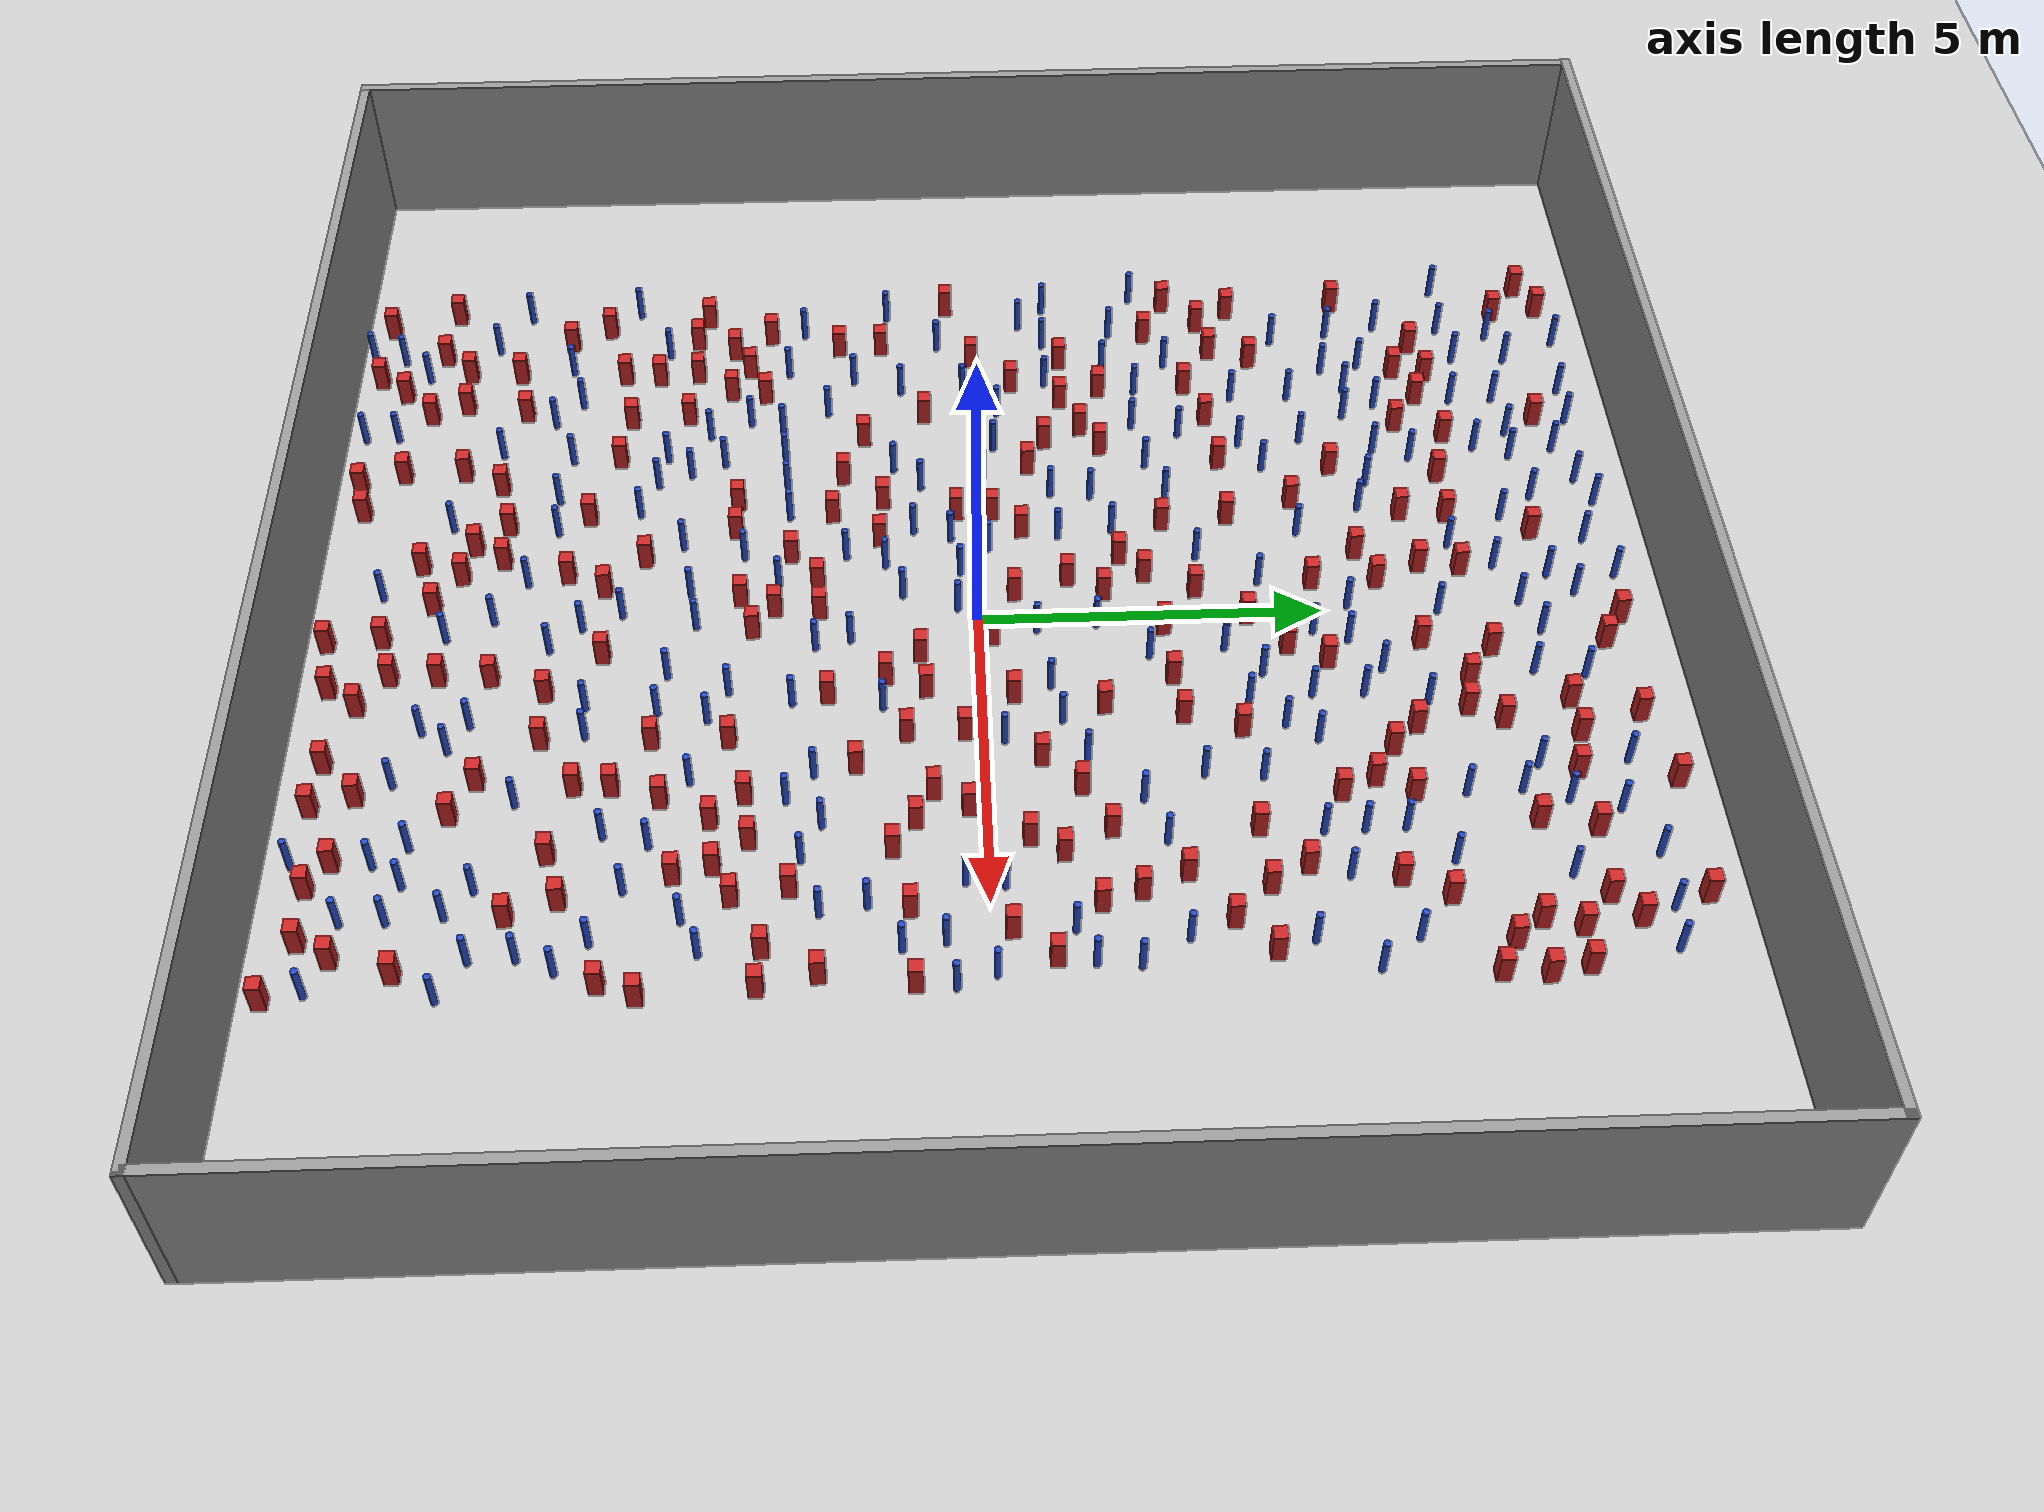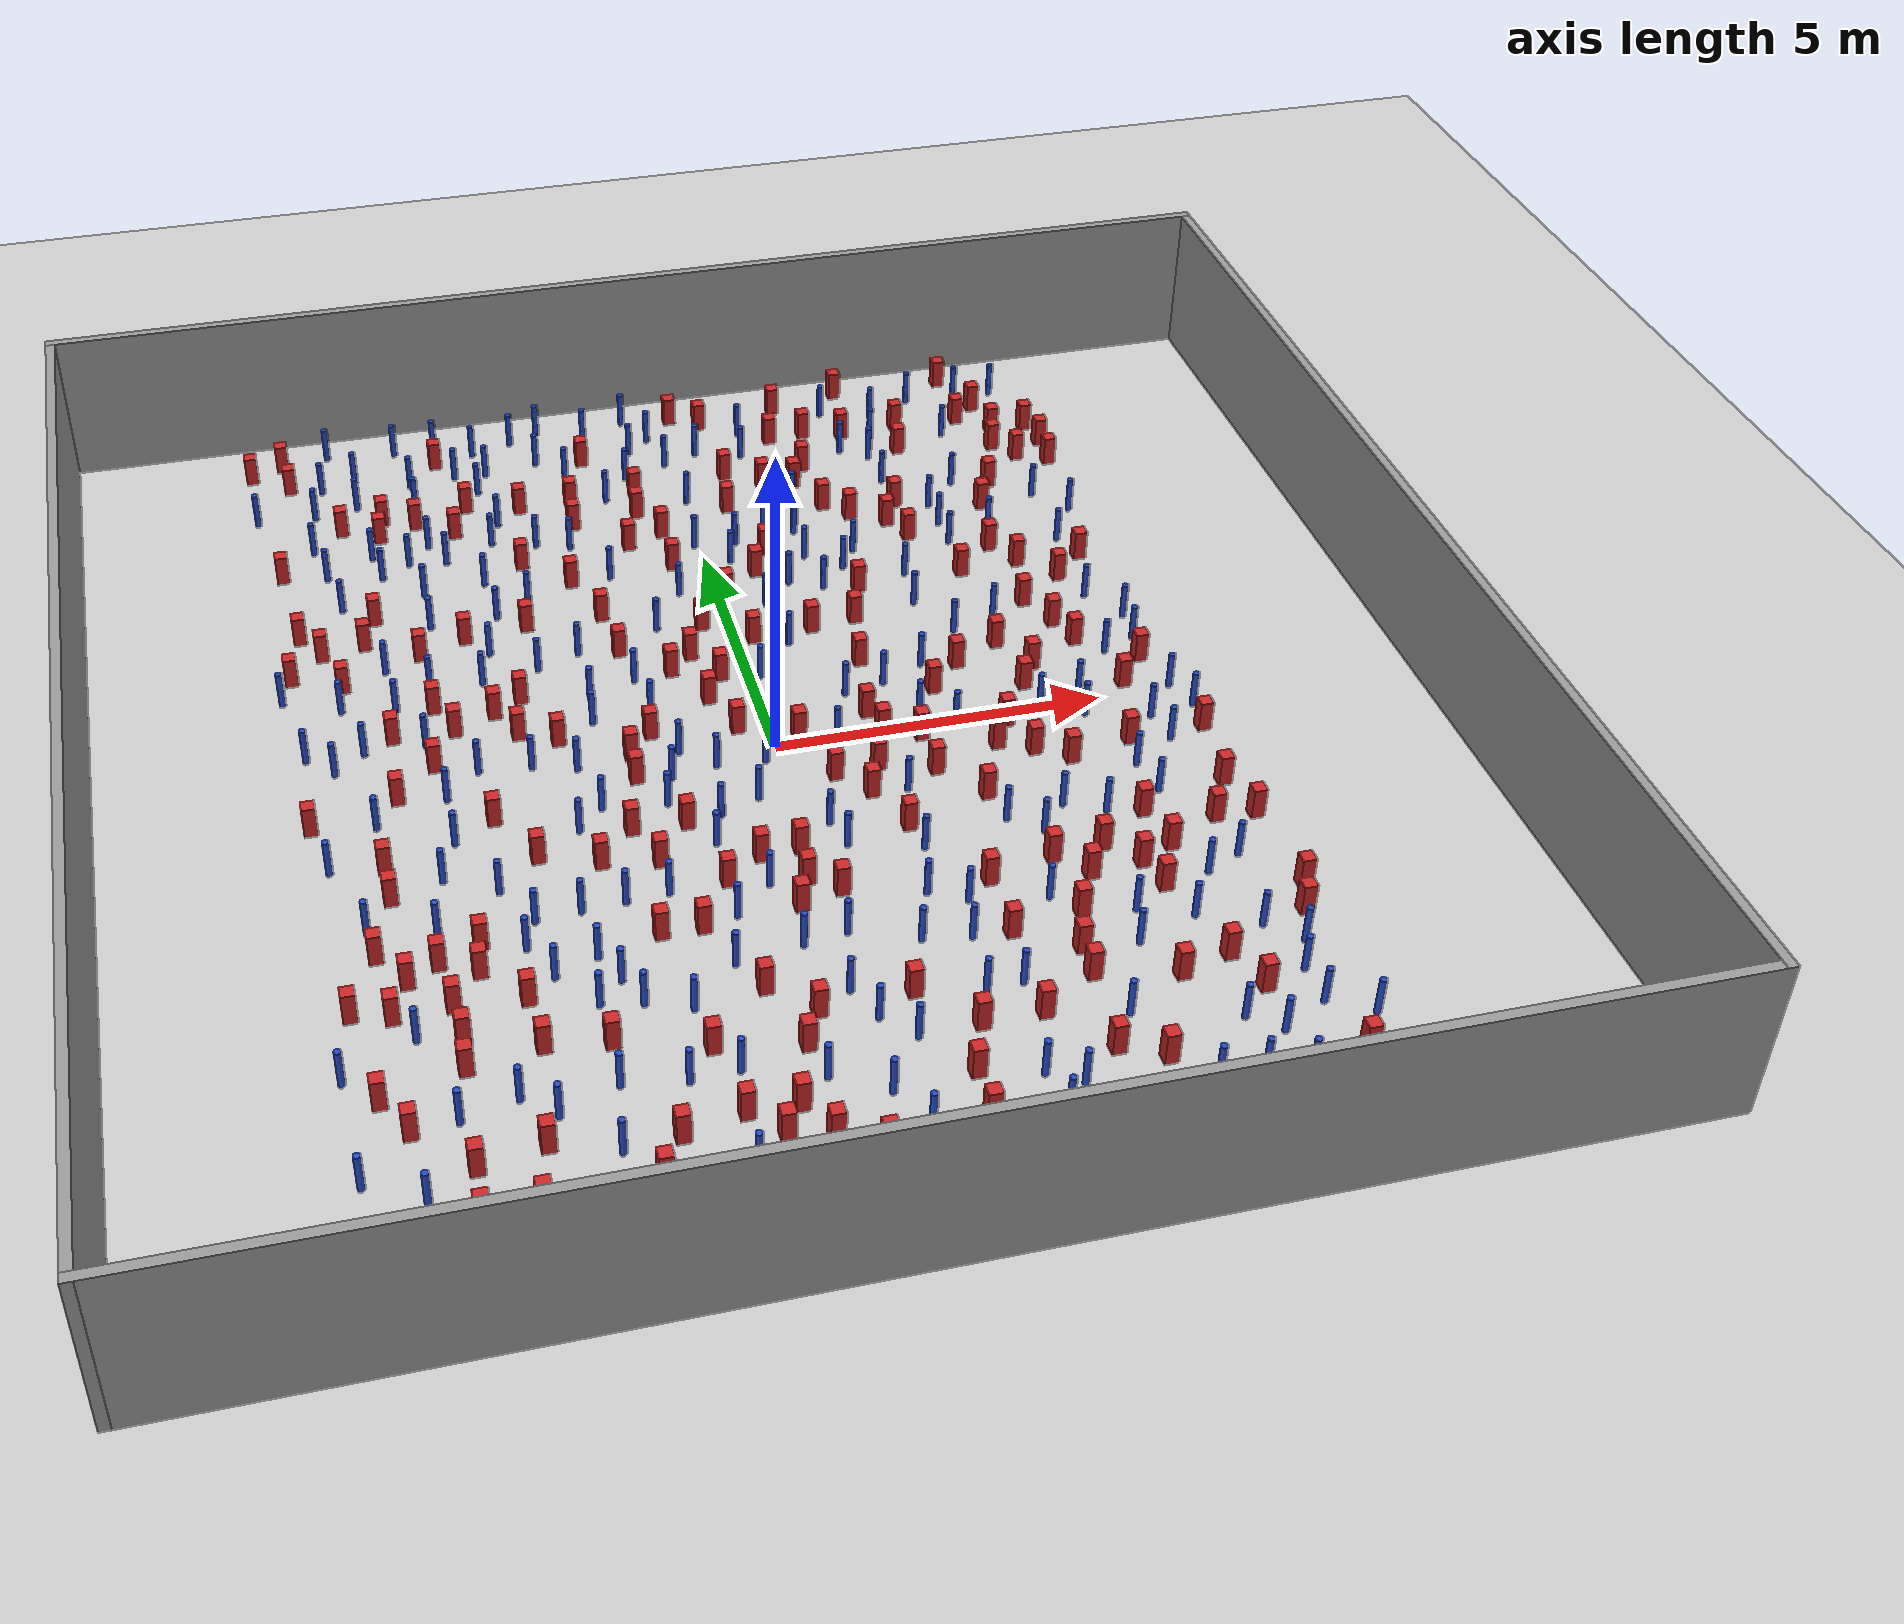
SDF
<sdf version="1.6">
 <world name="default">
  <light name="sun" type="directional">
   <pose>0 0 1000 0 -0 0</pose>
   <diffuse>0.8 0.8 0.8 1</diffuse>
   <specular>0.1 0.1 0.1 1</specular>
   <attenuation>
    <range>1000</range>
    <constant>0.9</constant>
    <linear>0.01</linear>
    <quadratic>0.001</quadratic>
   </attenuation>
   <direction>-0.5 0.5 -1</direction>
  </light>
  <model name="ground_plane">
   <static>1</static>
   <link name="link">
    <collision name="collision">
     <geometry><plane><normal>0 0 1</normal><size>100 100</size></plane></geometry>
     <surface><friction><ode><mu>100</mu><mu2>50</mu2></ode></friction></surface>
    </collision>
    <visual name="visual">
     <cast_shadows>0</cast_shadows>
     <geometry><plane><normal>0 0 1</normal><size>100 100</size></plane></geometry>
     <material>
      <ambient>1.0 1.0 1.0 1.0</ambient>
      <diffuse>0.8 0.8 0.8 1.0</diffuse>
      <specular>0.01 0.01 0.01 1.000000</specular>
     </material>
    </visual>
   </link>
  </model>
  <gravity>0 0 -9.8</gravity>
  <magnetic_field>6e-06 2.3e-05 -4.2e-05</magnetic_field>
  <atmosphere type="adiabatic"/>
  <physics name="default_physics" default="0" type="ode">
   <max_step_size>0.001</max_step_size>
   <real_time_factor>1</real_time_factor>
   <real_time_update_rate>1000</real_time_update_rate>
  </physics>
  <scene><ambient>0.4 0.4 0.4 1</ambient><background>0.7 0.7 0.7 1</background><shadows>1</shadows></scene>
  <spherical_coordinates>
   <surface_model>EARTH_WGS84</surface_model>
   <latitude_deg>0</latitude_deg>
   <longitude_deg>0</longitude_deg>
   <elevation>0</elevation>
   <heading_deg>0</heading_deg>
  </spherical_coordinates>
  <plugin name="gazebo_occupancy_map" filename="libgazebo_2Dmap_plugin.so">
   <map_resolution>0.05</map_resolution>
   <map_topic>generated_map</map_topic>
   <map_height>0.01</map_height>
   <map_size_x>50</map_size_x>
   <map_size_y>50</map_size_y>
  </plugin>
  <model name="NamedLocations">
   <static>true</static>
   <link name="DefaultStart"><pose>8.5 0 0 0 0 3.14</pose></link>
  </model>
  <model name="20x20_walls">
   <pose>0.044518 0.176112 0 0 -0 0</pose>
   <link name="Wall_1">
    <collision name="Wall_1_Collision">
     <geometry><box><size>20 0.15 2.5</size></box></geometry>
     <pose>0 0 1.25 0 -0 0</pose>
    </collision>
    <visual name="Wall_1_Visual">
     <pose>0 0 1.25 0 -0 0</pose>
     <geometry><box><size>20 0.15 2.5</size></box></geometry>
     <material>
      <script><uri>file://media/materials/scripts/gazebo.material</uri><name>Gazebo/Grey</name></script>
      <ambient>0.976471 0.992157 1 1</ambient>
     </material>
     <meta><layer>0</layer></meta>
    </visual>
    <pose>0 9.925 0 0 -0 0</pose>
   </link>
   <link name="Wall_3">
    <collision name="Wall_3_Collision">
     <geometry><box><size>20 0.15 2.5</size></box></geometry>
     <pose>0 0 1.25 0 -0 0</pose>
    </collision>
    <visual name="Wall_3_Visual">
     <pose>0 0 1.25 0 -0 0</pose>
     <geometry><box><size>20 0.15 2.5</size></box></geometry>
     <material>
      <script><uri>file://media/materials/scripts/gazebo.material</uri><name>Gazebo/Grey</name></script>
      <ambient>0.976471 0.992157 1 1</ambient>
     </material>
     <meta><layer>0</layer></meta>
    </visual>
    <pose>9.925 0 0 0 0 -1.5708</pose>
   </link>
   <link name="Wall_4">
    <collision name="Wall_4_Collision">
     <geometry><box><size>20 0.15 2.5</size></box></geometry>
     <pose>0 0 1.25 0 -0 0</pose>
    </collision>
    <visual name="Wall_4_Visual">
     <pose>0 0 1.25 0 -0 0</pose>
     <geometry><box><size>20 0.15 2.5</size></box></geometry>
     <material>
      <script><uri>file://media/materials/scripts/gazebo.material</uri><name>Gazebo/Grey</name></script>
      <ambient>0.976471 0.992157 1 1</ambient>
     </material>
     <meta><layer>0</layer></meta>
    </visual>
    <pose>0 -9.925 0 0 -0 3.14159</pose>
   </link>
   <link name="Wall_5">
    <collision name="Wall_5_Collision">
     <geometry><box><size>20 0.15 2.5</size></box></geometry>
     <pose>0 0 1.25 0 -0 0</pose>
    </collision>
    <visual name="Wall_5_Visual">
     <pose>0 0 1.25 0 -0 0</pose>
     <geometry><box><size>20 0.15 2.5</size></box></geometry>
     <material>
      <script><uri>file://media/materials/scripts/gazebo.material</uri><name>Gazebo/Grey</name></script>
      <ambient>0.976471 0.992157 1 1</ambient>
     </material>
     <meta><layer>0</layer></meta>
    </visual>
    <pose>-9.925 0 0 0 -0 1.5708</pose>
   </link>
   <static>1</static>
  </model>
  <model name="square_post_obstacle0">
   <static>true</static>
   <pose>-6.26751508779 3.72826211818 1.91545236811e-07 -7.35059704564e-06 1.12565212e-07 2.39332434364e-05</pose>
   <link name="link">
    <pose>0 0 0.25 0 -0 0</pose>
    <inertial>
     <mass>100</mass>
     <inertia>
      <ixx>0.166667</ixx>
      <ixy>0</ixy>
      <ixz>0</ixz>
      <iyy>0.166667</iyy>
      <iyz>0</iyz>
      <izz>0.166667</izz>
     </inertia>
    </inertial>
    <collision name="collision"><geometry><box><size>.2 .2 .5</size></box></geometry></collision>
    <visual name="visual">
     <geometry><box><size>.2 .2 .5</size></box></geometry>
     <material>
      <script><name>Gazebo/Red</name><uri>file://media/materials/scripts/gazebo.material</uri></script>
     </material>
    </visual>
   </link>
  </model>
  <model name="square_post_obstacle1">
   <static>true</static>
   <pose>-4.26526882868 -0.711887170166 1.91545236811e-07 -7.35059704564e-06 1.12565212e-07 2.39332434364e-05</pose>
   <link name="link">
    <pose>0 0 0.25 0 -0 0</pose>
    <inertial>
     <mass>100</mass>
     <inertia>
      <ixx>0.166667</ixx>
      <ixy>0</ixy>
      <ixz>0</ixz>
      <iyy>0.166667</iyy>
      <iyz>0</iyz>
      <izz>0.166667</izz>
     </inertia>
    </inertial>
    <collision name="collision"><geometry><box><size>.2 .2 .5</size></box></geometry></collision>
    <visual name="visual">
     <geometry><box><size>.2 .2 .5</size></box></geometry>
     <material>
      <script><name>Gazebo/Red</name><uri>file://media/materials/scripts/gazebo.material</uri></script>
     </material>
    </visual>
   </link>
  </model>
  <model name="pole_obstacle0">
   <static>true</static>
   <pose>5.76128852781 5.56607418223 7.38925637345e-09 -8.47170692796e-08 1.24976764786e-08 -1.74513093032e-07</pose>
   <link name="link">
    <pose>0 0 0.3 0 -0 0</pose>
    <inertial>
     <mass>1</mass>
     <inertia><ixx>0.145833</ixx><ixy>0</ixy><ixz>0</ixz><iyy>0.145833</iyy><iyz>0</iyz><izz>0.125</izz></inertia>
    </inertial>
    <collision name="collision">
     <geometry><cylinder><radius>0.05</radius><length>.6</length></cylinder></geometry>
    </collision>
    <visual name="visual">
     <geometry><cylinder><radius>0.05</radius><length>.6</length></cylinder></geometry>
     <material>
      <script><name>Gazebo/Blue</name><uri>file://media/materials/scripts/gazebo.material</uri></script>
     </material>
    </visual>
   </link>
  </model>
  <model name="square_post_obstacle2">
   <static>true</static>
   <pose>1.61059530566 -0.0328276457561 1.91545236811e-07 -7.35059704564e-06 1.12565212e-07 2.39332434364e-05</pose>
   <link name="link">
    <pose>0 0 0.25 0 -0 0</pose>
    <inertial>
     <mass>100</mass>
     <inertia>
      <ixx>0.166667</ixx>
      <ixy>0</ixy>
      <ixz>0</ixz>
      <iyy>0.166667</iyy>
      <iyz>0</iyz>
      <izz>0.166667</izz>
     </inertia>
    </inertial>
    <collision name="collision"><geometry><box><size>.2 .2 .5</size></box></geometry></collision>
    <visual name="visual">
     <geometry><box><size>.2 .2 .5</size></box></geometry>
     <material>
      <script><name>Gazebo/Red</name><uri>file://media/materials/scripts/gazebo.material</uri></script>
     </material>
    </visual>
   </link>
  </model>
  <model name="pole_obstacle1">
   <static>true</static>
   <pose>-6.63601493796 -1.28461203914 7.38925637345e-09 -8.471706928e-08 1.24976765134e-08 -1.74513093015e-07</pose>
   <link name="link">
    <pose>0 0 0.3 0 -0 0</pose>
    <inertial>
     <mass>1</mass>
     <inertia><ixx>0.145833</ixx><ixy>0</ixy><ixz>0</ixz><iyy>0.145833</iyy><iyz>0</iyz><izz>0.125</izz></inertia>
    </inertial>
    <collision name="collision">
     <geometry><cylinder><radius>0.05</radius><length>.6</length></cylinder></geometry>
    </collision>
    <visual name="visual">
     <geometry><cylinder><radius>0.05</radius><length>.6</length></cylinder></geometry>
     <material>
      <script><name>Gazebo/Blue</name><uri>file://media/materials/scripts/gazebo.material</uri></script>
     </material>
    </visual>
   </link>
  </model>
  <model name="square_post_obstacle3">
   <static>true</static>
   <pose>3.39269414633 4.85101991493 1.91545236811e-07 -7.35059704564e-06 1.12565212e-07 2.39332434364e-05</pose>
   <link name="link">
    <pose>0 0 0.25 0 -0 0</pose>
    <inertial>
     <mass>100</mass>
     <inertia>
      <ixx>0.166667</ixx>
      <ixy>0</ixy>
      <ixz>0</ixz>
      <iyy>0.166667</iyy>
      <iyz>0</iyz>
      <izz>0.166667</izz>
     </inertia>
    </inertial>
    <collision name="collision"><geometry><box><size>.2 .2 .5</size></box></geometry></collision>
    <visual name="visual">
     <geometry><box><size>.2 .2 .5</size></box></geometry>
     <material>
      <script><name>Gazebo/Red</name><uri>file://media/materials/scripts/gazebo.material</uri></script>
     </material>
    </visual>
   </link>
  </model>
  <model name="pole_obstacle2">
   <static>true</static>
   <pose>0.0751189451723 6.69348405141 7.38925637345e-09 -8.47170692799e-08 1.24976765062e-08 -1.74513093018e-07</pose>
   <link name="link">
    <pose>0 0 0.3 0 -0 0</pose>
    <inertial>
     <mass>1</mass>
     <inertia><ixx>0.145833</ixx><ixy>0</ixy><ixz>0</ixz><iyy>0.145833</iyy><iyz>0</iyz><izz>0.125</izz></inertia>
    </inertial>
    <collision name="collision">
     <geometry><cylinder><radius>0.05</radius><length>.6</length></cylinder></geometry>
    </collision>
    <visual name="visual">
     <geometry><cylinder><radius>0.05</radius><length>.6</length></cylinder></geometry>
     <material>
      <script><name>Gazebo/Blue</name><uri>file://media/materials/scripts/gazebo.material</uri></script>
     </material>
    </visual>
   </link>
  </model>
  <model name="pole_obstacle3">
   <static>true</static>
   <pose>0.141307437427 -7.68088082343 7.38925637345e-09 -8.471706928e-08 1.24976765036e-08 -1.74513093019e-07</pose>
   <link name="link">
    <pose>0 0 0.3 0 -0 0</pose>
    <inertial>
     <mass>1</mass>
     <inertia><ixx>0.145833</ixx><ixy>0</ixy><ixz>0</ixz><iyy>0.145833</iyy><iyz>0</iyz><izz>0.125</izz></inertia>
    </inertial>
    <collision name="collision">
     <geometry><cylinder><radius>0.05</radius><length>.6</length></cylinder></geometry>
    </collision>
    <visual name="visual">
     <geometry><cylinder><radius>0.05</radius><length>.6</length></cylinder></geometry>
     <material>
      <script><name>Gazebo/Blue</name><uri>file://media/materials/scripts/gazebo.material</uri></script>
     </material>
    </visual>
   </link>
  </model>
  <model name="square_post_obstacle4">
   <static>true</static>
   <pose>1.247294603 -6.15242603051 1.91545236811e-07 -7.35059704564e-06 1.12565212e-07 2.39332434364e-05</pose>
   <link name="link">
    <pose>0 0 0.25 0 -0 0</pose>
    <inertial>
     <mass>100</mass>
     <inertia>
      <ixx>0.166667</ixx>
      <ixy>0</ixy>
      <ixz>0</ixz>
      <iyy>0.166667</iyy>
      <iyz>0</iyz>
      <izz>0.166667</izz>
     </inertia>
    </inertial>
    <collision name="collision"><geometry><box><size>.2 .2 .5</size></box></geometry></collision>
    <visual name="visual">
     <geometry><box><size>.2 .2 .5</size></box></geometry>
     <material>
      <script><name>Gazebo/Red</name><uri>file://media/materials/scripts/gazebo.material</uri></script>
     </material>
    </visual>
   </link>
  </model>
  <model name="square_post_obstacle5">
   <static>true</static>
   <pose>0.161578494931 -8.57052492048 1.91545236811e-07 -7.35059704564e-06 1.12565212e-07 2.39332434364e-05</pose>
   <link name="link">
    <pose>0 0 0.25 0 -0 0</pose>
    <inertial>
     <mass>100</mass>
     <inertia>
      <ixx>0.166667</ixx>
      <ixy>0</ixy>
      <ixz>0</ixz>
      <iyy>0.166667</iyy>
      <iyz>0</iyz>
      <izz>0.166667</izz>
     </inertia>
    </inertial>
    <collision name="collision"><geometry><box><size>.2 .2 .5</size></box></geometry></collision>
    <visual name="visual">
     <geometry><box><size>.2 .2 .5</size></box></geometry>
     <material>
      <script><name>Gazebo/Red</name><uri>file://media/materials/scripts/gazebo.material</uri></script>
     </material>
    </visual>
   </link>
  </model>
  <model name="square_post_obstacle6">
   <static>true</static>
   <pose>-5.04222654512 6.75807206972 1.91545236811e-07 -7.35059704564e-06 1.12565212e-07 2.39332434364e-05</pose>
   <link name="link">
    <pose>0 0 0.25 0 -0 0</pose>
    <inertial>
     <mass>100</mass>
     <inertia>
      <ixx>0.166667</ixx>
      <ixy>0</ixy>
      <ixz>0</ixz>
      <iyy>0.166667</iyy>
      <iyz>0</iyz>
      <izz>0.166667</izz>
     </inertia>
    </inertial>
    <collision name="collision"><geometry><box><size>.2 .2 .5</size></box></geometry></collision>
    <visual name="visual">
     <geometry><box><size>.2 .2 .5</size></box></geometry>
     <material>
      <script><name>Gazebo/Red</name><uri>file://media/materials/scripts/gazebo.material</uri></script>
     </material>
    </visual>
   </link>
  </model>
  <model name="pole_obstacle4">
   <static>true</static>
   <pose>2.73617658869 -0.0764324424072 7.38925637345e-09 -8.471706928e-08 1.24976765088e-08 -1.74513093017e-07</pose>
   <link name="link">
    <pose>0 0 0.3 0 -0 0</pose>
    <inertial>
     <mass>1</mass>
     <inertia><ixx>0.145833</ixx><ixy>0</ixy><ixz>0</ixz><iyy>0.145833</iyy><iyz>0</iyz><izz>0.125</izz></inertia>
    </inertial>
    <collision name="collision">
     <geometry><cylinder><radius>0.05</radius><length>.6</length></cylinder></geometry>
    </collision>
    <visual name="visual">
     <geometry><cylinder><radius>0.05</radius><length>.6</length></cylinder></geometry>
     <material>
      <script><name>Gazebo/Blue</name><uri>file://media/materials/scripts/gazebo.material</uri></script>
     </material>
    </visual>
   </link>
  </model>
  <model name="pole_obstacle5">
   <static>true</static>
   <pose>2.62684425303 1.42801959995 7.38925637345e-09 -8.471706928e-08 1.24976765152e-08 -1.74513093012e-07</pose>
   <link name="link">
    <pose>0 0 0.3 0 -0 0</pose>
    <inertial>
     <mass>1</mass>
     <inertia><ixx>0.145833</ixx><ixy>0</ixy><ixz>0</ixz><iyy>0.145833</iyy><iyz>0</iyz><izz>0.125</izz></inertia>
    </inertial>
    <collision name="collision">
     <geometry><cylinder><radius>0.05</radius><length>.6</length></cylinder></geometry>
    </collision>
    <visual name="visual">
     <geometry><cylinder><radius>0.05</radius><length>.6</length></cylinder></geometry>
     <material>
      <script><name>Gazebo/Blue</name><uri>file://media/materials/scripts/gazebo.material</uri></script>
     </material>
    </visual>
   </link>
  </model>
  <model name="square_post_obstacle7">
   <static>true</static>
   <pose>4.10316415654 8.22295791466 1.91545236811e-07 -7.35059704564e-06 1.12565212e-07 2.39332434364e-05</pose>
   <link name="link">
    <pose>0 0 0.25 0 -0 0</pose>
    <inertial>
     <mass>100</mass>
     <inertia>
      <ixx>0.166667</ixx>
      <ixy>0</ixy>
      <ixz>0</ixz>
      <iyy>0.166667</iyy>
      <iyz>0</iyz>
      <izz>0.166667</izz>
     </inertia>
    </inertial>
    <collision name="collision"><geometry><box><size>.2 .2 .5</size></box></geometry></collision>
    <visual name="visual">
     <geometry><box><size>.2 .2 .5</size></box></geometry>
     <material>
      <script><name>Gazebo/Red</name><uri>file://media/materials/scripts/gazebo.material</uri></script>
     </material>
    </visual>
   </link>
  </model>
  <model name="square_post_obstacle8">
   <static>true</static>
   <pose>5.90578186092 -7.71212455294 1.91545236811e-07 -7.35059704564e-06 1.12565212e-07 2.39332434364e-05</pose>
   <link name="link">
    <pose>0 0 0.25 0 -0 0</pose>
    <inertial>
     <mass>100</mass>
     <inertia>
      <ixx>0.166667</ixx>
      <ixy>0</ixy>
      <ixz>0</ixz>
      <iyy>0.166667</iyy>
      <iyz>0</iyz>
      <izz>0.166667</izz>
     </inertia>
    </inertial>
    <collision name="collision"><geometry><box><size>.2 .2 .5</size></box></geometry></collision>
    <visual name="visual">
     <geometry><box><size>.2 .2 .5</size></box></geometry>
     <material>
      <script><name>Gazebo/Red</name><uri>file://media/materials/scripts/gazebo.material</uri></script>
     </material>
    </visual>
   </link>
  </model>
  <model name="pole_obstacle6">
   <static>true</static>
   <pose>-5.83699710048 8.39616868612 7.38925637345e-09 -8.471706928e-08 1.24976765081e-08 -1.74513093015e-07</pose>
   <link name="link">
    <pose>0 0 0.3 0 -0 0</pose>
    <inertial>
     <mass>1</mass>
     <inertia><ixx>0.145833</ixx><ixy>0</ixy><ixz>0</ixz><iyy>0.145833</iyy><iyz>0</iyz><izz>0.125</izz></inertia>
    </inertial>
    <collision name="collision">
     <geometry><cylinder><radius>0.05</radius><length>.6</length></cylinder></geometry>
    </collision>
    <visual name="visual">
     <geometry><cylinder><radius>0.05</radius><length>.6</length></cylinder></geometry>
     <material>
      <script><name>Gazebo/Blue</name><uri>file://media/materials/scripts/gazebo.material</uri></script>
     </material>
    </visual>
   </link>
  </model>
  <model name="pole_obstacle7">
   <static>true</static>
   <pose>3.04893697726 3.82194776182 7.38925637345e-09 -8.47170692798e-08 1.24976764939e-08 -1.74513093025e-07</pose>
   <link name="link">
    <pose>0 0 0.3 0 -0 0</pose>
    <inertial>
     <mass>1</mass>
     <inertia><ixx>0.145833</ixx><ixy>0</ixy><ixz>0</ixz><iyy>0.145833</iyy><iyz>0</iyz><izz>0.125</izz></inertia>
    </inertial>
    <collision name="collision">
     <geometry><cylinder><radius>0.05</radius><length>.6</length></cylinder></geometry>
    </collision>
    <visual name="visual">
     <geometry><cylinder><radius>0.05</radius><length>.6</length></cylinder></geometry>
     <material>
      <script><name>Gazebo/Blue</name><uri>file://media/materials/scripts/gazebo.material</uri></script>
     </material>
    </visual>
   </link>
  </model>
  <model name="square_post_obstacle9">
   <static>true</static>
   <pose>4.83220556354 5.45083646995 1.91545236811e-07 -7.35059704564e-06 1.12565212e-07 2.39332434364e-05</pose>
   <link name="link">
    <pose>0 0 0.25 0 -0 0</pose>
    <inertial>
     <mass>100</mass>
     <inertia>
      <ixx>0.166667</ixx>
      <ixy>0</ixy>
      <ixz>0</ixz>
      <iyy>0.166667</iyy>
      <iyz>0</iyz>
      <izz>0.166667</izz>
     </inertia>
    </inertial>
    <collision name="collision"><geometry><box><size>.2 .2 .5</size></box></geometry></collision>
    <visual name="visual">
     <geometry><box><size>.2 .2 .5</size></box></geometry>
     <material>
      <script><name>Gazebo/Red</name><uri>file://media/materials/scripts/gazebo.material</uri></script>
     </material>
    </visual>
   </link>
  </model>
  <model name="square_post_obstacle10">
   <static>true</static>
   <pose>-3.8304520646 6.61883451732 1.91545236811e-07 -7.35059704564e-06 1.12565212e-07 2.39332434364e-05</pose>
   <link name="link">
    <pose>0 0 0.25 0 -0 0</pose>
    <inertial>
     <mass>100</mass>
     <inertia>
      <ixx>0.166667</ixx>
      <ixy>0</ixy>
      <ixz>0</ixz>
      <iyy>0.166667</iyy>
      <iyz>0</iyz>
      <izz>0.166667</izz>
     </inertia>
    </inertial>
    <collision name="collision"><geometry><box><size>.2 .2 .5</size></box></geometry></collision>
    <visual name="visual">
     <geometry><box><size>.2 .2 .5</size></box></geometry>
     <material>
      <script><name>Gazebo/Red</name><uri>file://media/materials/scripts/gazebo.material</uri></script>
     </material>
    </visual>
   </link>
  </model>
  <model name="square_post_obstacle11">
   <static>true</static>
   <pose>-3.46584824441 1.98512690318 1.91545236811e-07 -7.35059704564e-06 1.12565212e-07 2.39332434364e-05</pose>
   <link name="link">
    <pose>0 0 0.25 0 -0 0</pose>
    <inertial>
     <mass>100</mass>
     <inertia>
      <ixx>0.166667</ixx>
      <ixy>0</ixy>
      <ixz>0</ixz>
      <iyy>0.166667</iyy>
      <iyz>0</iyz>
      <izz>0.166667</izz>
     </inertia>
    </inertial>
    <collision name="collision"><geometry><box><size>.2 .2 .5</size></box></geometry></collision>
    <visual name="visual">
     <geometry><box><size>.2 .2 .5</size></box></geometry>
     <material>
      <script><name>Gazebo/Red</name><uri>file://media/materials/scripts/gazebo.material</uri></script>
     </material>
    </visual>
   </link>
  </model>
  <model name="square_post_obstacle12">
   <static>true</static>
   <pose>-5.41068607509 -7.08402210731 1.91545236811e-07 -7.35059704564e-06 1.12565212e-07 2.39332434364e-05</pose>
   <link name="link">
    <pose>0 0 0.25 0 -0 0</pose>
    <inertial>
     <mass>100</mass>
     <inertia>
      <ixx>0.166667</ixx>
      <ixy>0</ixy>
      <ixz>0</ixz>
      <iyy>0.166667</iyy>
      <iyz>0</iyz>
      <izz>0.166667</izz>
     </inertia>
    </inertial>
    <collision name="collision"><geometry><box><size>.2 .2 .5</size></box></geometry></collision>
    <visual name="visual">
     <geometry><box><size>.2 .2 .5</size></box></geometry>
     <material>
      <script><name>Gazebo/Red</name><uri>file://media/materials/scripts/gazebo.material</uri></script>
     </material>
    </visual>
   </link>
  </model>
  <model name="square_post_obstacle13">
   <static>true</static>
   <pose>-4.93012539754 0.668586995232 1.91545236811e-07 -7.35059704564e-06 1.12565212e-07 2.39332434364e-05</pose>
   <link name="link">
    <pose>0 0 0.25 0 -0 0</pose>
    <inertial>
     <mass>100</mass>
     <inertia>
      <ixx>0.166667</ixx>
      <ixy>0</ixy>
      <ixz>0</ixz>
      <iyy>0.166667</iyy>
      <iyz>0</iyz>
      <izz>0.166667</izz>
     </inertia>
    </inertial>
    <collision name="collision"><geometry><box><size>.2 .2 .5</size></box></geometry></collision>
    <visual name="visual">
     <geometry><box><size>.2 .2 .5</size></box></geometry>
     <material>
      <script><name>Gazebo/Red</name><uri>file://media/materials/scripts/gazebo.material</uri></script>
     </material>
    </visual>
   </link>
  </model>
  <model name="pole_obstacle8">
   <static>true</static>
   <pose>4.23675840631 -2.50700964312 7.38925637345e-09 -8.47170692798e-08 1.24976764937e-08 -1.74513093023e-07</pose>
   <link name="link">
    <pose>0 0 0.3 0 -0 0</pose>
    <inertial>
     <mass>1</mass>
     <inertia><ixx>0.145833</ixx><ixy>0</ixy><ixz>0</ixz><iyy>0.145833</iyy><iyz>0</iyz><izz>0.125</izz></inertia>
    </inertial>
    <collision name="collision">
     <geometry><cylinder><radius>0.05</radius><length>.6</length></cylinder></geometry>
    </collision>
    <visual name="visual">
     <geometry><cylinder><radius>0.05</radius><length>.6</length></cylinder></geometry>
     <material>
      <script><name>Gazebo/Blue</name><uri>file://media/materials/scripts/gazebo.material</uri></script>
     </material>
    </visual>
   </link>
  </model>
  <model name="square_post_obstacle14">
   <static>true</static>
   <pose>1.41845635646 -8.77849370848 1.91545236811e-07 -7.35059704564e-06 1.12565212e-07 2.39332434364e-05</pose>
   <link name="link">
    <pose>0 0 0.25 0 -0 0</pose>
    <inertial>
     <mass>100</mass>
     <inertia>
      <ixx>0.166667</ixx>
      <ixy>0</ixy>
      <ixz>0</ixz>
      <iyy>0.166667</iyy>
      <iyz>0</iyz>
      <izz>0.166667</izz>
     </inertia>
    </inertial>
    <collision name="collision"><geometry><box><size>.2 .2 .5</size></box></geometry></collision>
    <visual name="visual">
     <geometry><box><size>.2 .2 .5</size></box></geometry>
     <material>
      <script><name>Gazebo/Red</name><uri>file://media/materials/scripts/gazebo.material</uri></script>
     </material>
    </visual>
   </link>
  </model>
  <model name="square_post_obstacle15">
   <static>true</static>
   <pose>2.46411569563 8.30953991213 1.91545236811e-07 -7.35059704564e-06 1.12565212e-07 2.39332434364e-05</pose>
   <link name="link">
    <pose>0 0 0.25 0 -0 0</pose>
    <inertial>
     <mass>100</mass>
     <inertia>
      <ixx>0.166667</ixx>
      <ixy>0</ixy>
      <ixz>0</ixz>
      <iyy>0.166667</iyy>
      <iyz>0</iyz>
      <izz>0.166667</izz>
     </inertia>
    </inertial>
    <collision name="collision"><geometry><box><size>.2 .2 .5</size></box></geometry></collision>
    <visual name="visual">
     <geometry><box><size>.2 .2 .5</size></box></geometry>
     <material>
      <script><name>Gazebo/Red</name><uri>file://media/materials/scripts/gazebo.material</uri></script>
     </material>
    </visual>
   </link>
  </model>
  <model name="square_post_obstacle16">
   <static>true</static>
   <pose>6.3573693927 6.53001208499 1.91545236811e-07 -7.35059704564e-06 1.12565212e-07 2.39332434364e-05</pose>
   <link name="link">
    <pose>0 0 0.25 0 -0 0</pose>
    <inertial>
     <mass>100</mass>
     <inertia>
      <ixx>0.166667</ixx>
      <ixy>0</ixy>
      <ixz>0</ixz>
      <iyy>0.166667</iyy>
      <iyz>0</iyz>
      <izz>0.166667</izz>
     </inertia>
    </inertial>
    <collision name="collision"><geometry><box><size>.2 .2 .5</size></box></geometry></collision>
    <visual name="visual">
     <geometry><box><size>.2 .2 .5</size></box></geometry>
     <material>
      <script><name>Gazebo/Red</name><uri>file://media/materials/scripts/gazebo.material</uri></script>
     </material>
    </visual>
   </link>
  </model>
  <model name="pole_obstacle9">
   <static>true</static>
   <pose>-4.84726449901 -0.0963658252567 7.38925637345e-09 -8.47170692799e-08 1.24976765039e-08 -1.74513093019e-07</pose>
   <link name="link">
    <pose>0 0 0.3 0 -0 0</pose>
    <inertial>
     <mass>1</mass>
     <inertia><ixx>0.145833</ixx><ixy>0</ixy><ixz>0</ixz><iyy>0.145833</iyy><iyz>0</iyz><izz>0.125</izz></inertia>
    </inertial>
    <collision name="collision">
     <geometry><cylinder><radius>0.05</radius><length>.6</length></cylinder></geometry>
    </collision>
    <visual name="visual">
     <geometry><cylinder><radius>0.05</radius><length>.6</length></cylinder></geometry>
     <material>
      <script><name>Gazebo/Blue</name><uri>file://media/materials/scripts/gazebo.material</uri></script>
     </material>
    </visual>
   </link>
  </model>
  <model name="square_post_obstacle17">
   <static>true</static>
   <pose>-3.43209271855 -5.3860651551 1.91545236811e-07 -7.35059704564e-06 1.12565212e-07 2.39332434364e-05</pose>
   <link name="link">
    <pose>0 0 0.25 0 -0 0</pose>
    <inertial>
     <mass>100</mass>
     <inertia>
      <ixx>0.166667</ixx>
      <ixy>0</ixy>
      <ixz>0</ixz>
      <iyy>0.166667</iyy>
      <iyz>0</iyz>
      <izz>0.166667</izz>
     </inertia>
    </inertial>
    <collision name="collision"><geometry><box><size>.2 .2 .5</size></box></geometry></collision>
    <visual name="visual">
     <geometry><box><size>.2 .2 .5</size></box></geometry>
     <material>
      <script><name>Gazebo/Red</name><uri>file://media/materials/scripts/gazebo.material</uri></script>
     </material>
    </visual>
   </link>
  </model>
  <model name="square_post_obstacle18">
   <static>true</static>
   <pose>0.291771999807 9.30222031321 1.91545236811e-07 -7.35059704564e-06 1.12565212e-07 2.39332434364e-05</pose>
   <link name="link">
    <pose>0 0 0.25 0 -0 0</pose>
    <inertial>
     <mass>100</mass>
     <inertia>
      <ixx>0.166667</ixx>
      <ixy>0</ixy>
      <ixz>0</ixz>
      <iyy>0.166667</iyy>
      <iyz>0</iyz>
      <izz>0.166667</izz>
     </inertia>
    </inertial>
    <collision name="collision"><geometry><box><size>.2 .2 .5</size></box></geometry></collision>
    <visual name="visual">
     <geometry><box><size>.2 .2 .5</size></box></geometry>
     <material>
      <script><name>Gazebo/Red</name><uri>file://media/materials/scripts/gazebo.material</uri></script>
     </material>
    </visual>
   </link>
  </model>
  <model name="pole_obstacle10">
   <static>true</static>
   <pose>-5.36167186587 3.1312678507 7.38925637345e-09 -8.47170692798e-08 1.24976764937e-08 -1.74513093023e-07</pose>
   <link name="link">
    <pose>0 0 0.3 0 -0 0</pose>
    <inertial>
     <mass>1</mass>
     <inertia><ixx>0.145833</ixx><ixy>0</ixy><ixz>0</ixz><iyy>0.145833</iyy><iyz>0</iyz><izz>0.125</izz></inertia>
    </inertial>
    <collision name="collision">
     <geometry><cylinder><radius>0.05</radius><length>.6</length></cylinder></geometry>
    </collision>
    <visual name="visual">
     <geometry><cylinder><radius>0.05</radius><length>.6</length></cylinder></geometry>
     <material>
      <script><name>Gazebo/Blue</name><uri>file://media/materials/scripts/gazebo.material</uri></script>
     </material>
    </visual>
   </link>
  </model>
  <model name="square_post_obstacle19">
   <static>true</static>
   <pose>4.82646554091 -5.68072084667 1.91545236811e-07 -7.35059704564e-06 1.12565212e-07 2.39332434364e-05</pose>
   <link name="link">
    <pose>0 0 0.25 0 -0 0</pose>
    <inertial>
     <mass>100</mass>
     <inertia>
      <ixx>0.166667</ixx>
      <ixy>0</ixy>
      <ixz>0</ixz>
      <iyy>0.166667</iyy>
      <iyz>0</iyz>
      <izz>0.166667</izz>
     </inertia>
    </inertial>
    <collision name="collision"><geometry><box><size>.2 .2 .5</size></box></geometry></collision>
    <visual name="visual">
     <geometry><box><size>.2 .2 .5</size></box></geometry>
     <material>
      <script><name>Gazebo/Red</name><uri>file://media/materials/scripts/gazebo.material</uri></script>
     </material>
    </visual>
   </link>
  </model>
  <model name="pole_obstacle11">
   <static>true</static>
   <pose>-4.07201410686 5.84191338444 7.38925637345e-09 -8.47170692796e-08 1.24976764786e-08 -1.74513093032e-07</pose>
   <link name="link">
    <pose>0 0 0.3 0 -0 0</pose>
    <inertial>
     <mass>1</mass>
     <inertia><ixx>0.145833</ixx><ixy>0</ixy><ixz>0</ixz><iyy>0.145833</iyy><iyz>0</iyz><izz>0.125</izz></inertia>
    </inertial>
    <collision name="collision">
     <geometry><cylinder><radius>0.05</radius><length>.6</length></cylinder></geometry>
    </collision>
    <visual name="visual">
     <geometry><cylinder><radius>0.05</radius><length>.6</length></cylinder></geometry>
     <material>
      <script><name>Gazebo/Blue</name><uri>file://media/materials/scripts/gazebo.material</uri></script>
     </material>
    </visual>
   </link>
  </model>
  <model name="square_post_obstacle20">
   <static>true</static>
   <pose>1.0768508336 -9.2199925486 1.91545236811e-07 -7.35059704564e-06 1.12565212e-07 2.39332434364e-05</pose>
   <link name="link">
    <pose>0 0 0.25 0 -0 0</pose>
    <inertial>
     <mass>100</mass>
     <inertia>
      <ixx>0.166667</ixx>
      <ixy>0</ixy>
      <ixz>0</ixz>
      <iyy>0.166667</iyy>
      <iyz>0</iyz>
      <izz>0.166667</izz>
     </inertia>
    </inertial>
    <collision name="collision"><geometry><box><size>.2 .2 .5</size></box></geometry></collision>
    <visual name="visual">
     <geometry><box><size>.2 .2 .5</size></box></geometry>
     <material>
      <script><name>Gazebo/Red</name><uri>file://media/materials/scripts/gazebo.material</uri></script>
     </material>
    </visual>
   </link>
  </model>
  <model name="pole_obstacle12">
   <static>true</static>
   <pose>-6.95213012178 7.66707469394 7.38925637345e-09 -8.47170692796e-08 1.24976764786e-08 -1.74513093032e-07</pose>
   <link name="link">
    <pose>0 0 0.3 0 -0 0</pose>
    <inertial>
     <mass>1</mass>
     <inertia><ixx>0.145833</ixx><ixy>0</ixy><ixz>0</ixz><iyy>0.145833</iyy><iyz>0</iyz><izz>0.125</izz></inertia>
    </inertial>
    <collision name="collision">
     <geometry><cylinder><radius>0.05</radius><length>.6</length></cylinder></geometry>
    </collision>
    <visual name="visual">
     <geometry><cylinder><radius>0.05</radius><length>.6</length></cylinder></geometry>
     <material>
      <script><name>Gazebo/Blue</name><uri>file://media/materials/scripts/gazebo.material</uri></script>
     </material>
    </visual>
   </link>
  </model>
  <model name="square_post_obstacle21">
   <static>true</static>
   <pose>0.146579969582 -3.2607515876 1.91545236811e-07 -7.35059704564e-06 1.12565212e-07 2.39332434364e-05</pose>
   <link name="link">
    <pose>0 0 0.25 0 -0 0</pose>
    <inertial>
     <mass>100</mass>
     <inertia>
      <ixx>0.166667</ixx>
      <ixy>0</ixy>
      <ixz>0</ixz>
      <iyy>0.166667</iyy>
      <iyz>0</iyz>
      <izz>0.166667</izz>
     </inertia>
    </inertial>
    <collision name="collision"><geometry><box><size>.2 .2 .5</size></box></geometry></collision>
    <visual name="visual">
     <geometry><box><size>.2 .2 .5</size></box></geometry>
     <material>
      <script><name>Gazebo/Red</name><uri>file://media/materials/scripts/gazebo.material</uri></script>
     </material>
    </visual>
   </link>
  </model>
  <model name="pole_obstacle13">
   <static>true</static>
   <pose>-0.584820534755 4.12830127704 7.38925637345e-09 -8.471706928e-08 1.24976765086e-08 -1.74513093015e-07</pose>
   <link name="link">
    <pose>0 0 0.3 0 -0 0</pose>
    <inertial>
     <mass>1</mass>
     <inertia><ixx>0.145833</ixx><ixy>0</ixy><ixz>0</ixz><iyy>0.145833</iyy><iyz>0</iyz><izz>0.125</izz></inertia>
    </inertial>
    <collision name="collision">
     <geometry><cylinder><radius>0.05</radius><length>.6</length></cylinder></geometry>
    </collision>
    <visual name="visual">
     <geometry><cylinder><radius>0.05</radius><length>.6</length></cylinder></geometry>
     <material>
      <script><name>Gazebo/Blue</name><uri>file://media/materials/scripts/gazebo.material</uri></script>
     </material>
    </visual>
   </link>
  </model>
  <model name="square_post_obstacle22">
   <static>true</static>
   <pose>-2.038368199 -6.95661025734 1.91545236811e-07 -7.35059704564e-06 1.12565212e-07 2.39332434364e-05</pose>
   <link name="link">
    <pose>0 0 0.25 0 -0 0</pose>
    <inertial>
     <mass>100</mass>
     <inertia>
      <ixx>0.166667</ixx>
      <ixy>0</ixy>
      <ixz>0</ixz>
      <iyy>0.166667</iyy>
      <iyz>0</iyz>
      <izz>0.166667</izz>
     </inertia>
    </inertial>
    <collision name="collision"><geometry><box><size>.2 .2 .5</size></box></geometry></collision>
    <visual name="visual">
     <geometry><box><size>.2 .2 .5</size></box></geometry>
     <material>
      <script><name>Gazebo/Red</name><uri>file://media/materials/scripts/gazebo.material</uri></script>
     </material>
    </visual>
   </link>
  </model>
  <model name="pole_obstacle14">
   <static>true</static>
   <pose>-3.08421789567 8.29486062052 7.38925637345e-09 -8.47170692793e-08 1.24976764408e-08 -1.74513093041e-07</pose>
   <link name="link">
    <pose>0 0 0.3 0 -0 0</pose>
    <inertial>
     <mass>1</mass>
     <inertia><ixx>0.145833</ixx><ixy>0</ixy><ixz>0</ixz><iyy>0.145833</iyy><iyz>0</iyz><izz>0.125</izz></inertia>
    </inertial>
    <collision name="collision">
     <geometry><cylinder><radius>0.05</radius><length>.6</length></cylinder></geometry>
    </collision>
    <visual name="visual">
     <geometry><cylinder><radius>0.05</radius><length>.6</length></cylinder></geometry>
     <material>
      <script><name>Gazebo/Blue</name><uri>file://media/materials/scripts/gazebo.material</uri></script>
     </material>
    </visual>
   </link>
  </model>
  <model name="pole_obstacle15">
   <static>true</static>
   <pose>0.688545159779 3.51589472263 7.38925637345e-09 -8.47170692799e-08 1.2497676509e-08 -1.74513093016e-07</pose>
   <link name="link">
    <pose>0 0 0.3 0 -0 0</pose>
    <inertial>
     <mass>1</mass>
     <inertia><ixx>0.145833</ixx><ixy>0</ixy><ixz>0</ixz><iyy>0.145833</iyy><iyz>0</iyz><izz>0.125</izz></inertia>
    </inertial>
    <collision name="collision">
     <geometry><cylinder><radius>0.05</radius><length>.6</length></cylinder></geometry>
    </collision>
    <visual name="visual">
     <geometry><cylinder><radius>0.05</radius><length>.6</length></cylinder></geometry>
     <material>
      <script><name>Gazebo/Blue</name><uri>file://media/materials/scripts/gazebo.material</uri></script>
     </material>
    </visual>
   </link>
  </model>
  <model name="pole_obstacle16">
   <static>true</static>
   <pose>3.93698666208 -4.55390573233 7.38925637345e-09 -8.47170692798e-08 1.24976765033e-08 -1.74513093019e-07</pose>
   <link name="link">
    <pose>0 0 0.3 0 -0 0</pose>
    <inertial>
     <mass>1</mass>
     <inertia><ixx>0.145833</ixx><ixy>0</ixy><ixz>0</ixz><iyy>0.145833</iyy><iyz>0</iyz><izz>0.125</izz></inertia>
    </inertial>
    <collision name="collision">
     <geometry><cylinder><radius>0.05</radius><length>.6</length></cylinder></geometry>
    </collision>
    <visual name="visual">
     <geometry><cylinder><radius>0.05</radius><length>.6</length></cylinder></geometry>
     <material>
      <script><name>Gazebo/Blue</name><uri>file://media/materials/scripts/gazebo.material</uri></script>
     </material>
    </visual>
   </link>
  </model>
  <model name="square_post_obstacle23">
   <static>true</static>
   <pose>3.93727904672 3.65878601379 1.91545236811e-07 -7.35059704564e-06 1.12565212e-07 2.39332434364e-05</pose>
   <link name="link">
    <pose>0 0 0.25 0 -0 0</pose>
    <inertial>
     <mass>100</mass>
     <inertia>
      <ixx>0.166667</ixx>
      <ixy>0</ixy>
      <ixz>0</ixz>
      <iyy>0.166667</iyy>
      <iyz>0</iyz>
      <izz>0.166667</izz>
     </inertia>
    </inertial>
    <collision name="collision"><geometry><box><size>.2 .2 .5</size></box></geometry></collision>
    <visual name="visual">
     <geometry><box><size>.2 .2 .5</size></box></geometry>
     <material>
      <script><name>Gazebo/Red</name><uri>file://media/materials/scripts/gazebo.material</uri></script>
     </material>
    </visual>
   </link>
  </model>
  <model name="pole_obstacle17">
   <static>true</static>
   <pose>-0.780352660675 -2.9070580991 7.38925637345e-09 -8.47170692799e-08 1.2497676509e-08 -1.74513093016e-07</pose>
   <link name="link">
    <pose>0 0 0.3 0 -0 0</pose>
    <inertial>
     <mass>1</mass>
     <inertia><ixx>0.145833</ixx><ixy>0</ixy><ixz>0</ixz><iyy>0.145833</iyy><iyz>0</iyz><izz>0.125</izz></inertia>
    </inertial>
    <collision name="collision">
     <geometry><cylinder><radius>0.05</radius><length>.6</length></cylinder></geometry>
    </collision>
    <visual name="visual">
     <geometry><cylinder><radius>0.05</radius><length>.6</length></cylinder></geometry>
     <material>
      <script><name>Gazebo/Blue</name><uri>file://media/materials/scripts/gazebo.material</uri></script>
     </material>
    </visual>
   </link>
  </model>
  <model name="square_post_obstacle24">
   <static>true</static>
   <pose>-3.20584514164 -8.66685840395 1.91545236811e-07 -7.35059704564e-06 1.12565212e-07 2.39332434364e-05</pose>
   <link name="link">
    <pose>0 0 0.25 0 -0 0</pose>
    <inertial>
     <mass>100</mass>
     <inertia>
      <ixx>0.166667</ixx>
      <ixy>0</ixy>
      <ixz>0</ixz>
      <iyy>0.166667</iyy>
      <iyz>0</iyz>
      <izz>0.166667</izz>
     </inertia>
    </inertial>
    <collision name="collision"><geometry><box><size>.2 .2 .5</size></box></geometry></collision>
    <visual name="visual">
     <geometry><box><size>.2 .2 .5</size></box></geometry>
     <material>
      <script><name>Gazebo/Red</name><uri>file://media/materials/scripts/gazebo.material</uri></script>
     </material>
    </visual>
   </link>
  </model>
  <model name="square_post_obstacle25">
   <static>true</static>
   <pose>-1.90355383326 3.78758159417 1.91545236811e-07 -7.35059704564e-06 1.12565212e-07 2.39332434364e-05</pose>
   <link name="link">
    <pose>0 0 0.25 0 -0 0</pose>
    <inertial>
     <mass>100</mass>
     <inertia>
      <ixx>0.166667</ixx>
      <ixy>0</ixy>
      <ixz>0</ixz>
      <iyy>0.166667</iyy>
      <iyz>0</iyz>
      <izz>0.166667</izz>
     </inertia>
    </inertial>
    <collision name="collision"><geometry><box><size>.2 .2 .5</size></box></geometry></collision>
    <visual name="visual">
     <geometry><box><size>.2 .2 .5</size></box></geometry>
     <material>
      <script><name>Gazebo/Red</name><uri>file://media/materials/scripts/gazebo.material</uri></script>
     </material>
    </visual>
   </link>
  </model>
  <model name="square_post_obstacle26">
   <static>true</static>
   <pose>-1.80765000594 2.80278748641 1.91545236811e-07 -7.35059704564e-06 1.12565212e-07 2.39332434364e-05</pose>
   <link name="link">
    <pose>0 0 0.25 0 -0 0</pose>
    <inertial>
     <mass>100</mass>
     <inertia>
      <ixx>0.166667</ixx>
      <ixy>0</ixy>
      <ixz>0</ixz>
      <iyy>0.166667</iyy>
      <iyz>0</iyz>
      <izz>0.166667</izz>
     </inertia>
    </inertial>
    <collision name="collision"><geometry><box><size>.2 .2 .5</size></box></geometry></collision>
    <visual name="visual">
     <geometry><box><size>.2 .2 .5</size></box></geometry>
     <material>
      <script><name>Gazebo/Red</name><uri>file://media/materials/scripts/gazebo.material</uri></script>
     </material>
    </visual>
   </link>
  </model>
  <model name="square_post_obstacle27">
   <static>true</static>
   <pose>-5.6024415163 3.86342693756 1.91545236811e-07 -7.35059704564e-06 1.12565212e-07 2.39332434364e-05</pose>
   <link name="link">
    <pose>0 0 0.25 0 -0 0</pose>
    <inertial>
     <mass>100</mass>
     <inertia>
      <ixx>0.166667</ixx>
      <ixy>0</ixy>
      <ixz>0</ixz>
      <iyy>0.166667</iyy>
      <iyz>0</iyz>
      <izz>0.166667</izz>
     </inertia>
    </inertial>
    <collision name="collision"><geometry><box><size>.2 .2 .5</size></box></geometry></collision>
    <visual name="visual">
     <geometry><box><size>.2 .2 .5</size></box></geometry>
     <material>
      <script><name>Gazebo/Red</name><uri>file://media/materials/scripts/gazebo.material</uri></script>
     </material>
    </visual>
   </link>
  </model>
  <model name="pole_obstacle18">
   <static>true</static>
   <pose>-3.46971509979 -6.12122088916 7.38925637345e-09 -8.47170692794e-08 1.24976764468e-08 -1.7451309304e-07</pose>
   <link name="link">
    <pose>0 0 0.3 0 -0 0</pose>
    <inertial>
     <mass>1</mass>
     <inertia><ixx>0.145833</ixx><ixy>0</ixy><ixz>0</ixz><iyy>0.145833</iyy><iyz>0</iyz><izz>0.125</izz></inertia>
    </inertial>
    <collision name="collision">
     <geometry><cylinder><radius>0.05</radius><length>.6</length></cylinder></geometry>
    </collision>
    <visual name="visual">
     <geometry><cylinder><radius>0.05</radius><length>.6</length></cylinder></geometry>
     <material>
      <script><name>Gazebo/Blue</name><uri>file://media/materials/scripts/gazebo.material</uri></script>
     </material>
    </visual>
   </link>
  </model>
  <model name="square_post_obstacle28">
   <static>true</static>
   <pose>-4.29787141564 -5.25751584329 1.91545236811e-07 -7.35059704564e-06 1.12565212e-07 2.39332434364e-05</pose>
   <link name="link">
    <pose>0 0 0.25 0 -0 0</pose>
    <inertial>
     <mass>100</mass>
     <inertia>
      <ixx>0.166667</ixx>
      <ixy>0</ixy>
      <ixz>0</ixz>
      <iyy>0.166667</iyy>
      <iyz>0</iyz>
      <izz>0.166667</izz>
     </inertia>
    </inertial>
    <collision name="collision"><geometry><box><size>.2 .2 .5</size></box></geometry></collision>
    <visual name="visual">
     <geometry><box><size>.2 .2 .5</size></box></geometry>
     <material>
      <script><name>Gazebo/Red</name><uri>file://media/materials/scripts/gazebo.material</uri></script>
     </material>
    </visual>
   </link>
  </model>
  <model name="pole_obstacle19">
   <static>true</static>
   <pose>-2.72758485795 -0.791963947445 7.38925637345e-09 -8.471706928e-08 1.24976765177e-08 -1.74513093012e-07</pose>
   <link name="link">
    <pose>0 0 0.3 0 -0 0</pose>
    <inertial>
     <mass>1</mass>
     <inertia><ixx>0.145833</ixx><ixy>0</ixy><ixz>0</ixz><iyy>0.145833</iyy><iyz>0</iyz><izz>0.125</izz></inertia>
    </inertial>
    <collision name="collision">
     <geometry><cylinder><radius>0.05</radius><length>.6</length></cylinder></geometry>
    </collision>
    <visual name="visual">
     <geometry><cylinder><radius>0.05</radius><length>.6</length></cylinder></geometry>
     <material>
      <script><name>Gazebo/Blue</name><uri>file://media/materials/scripts/gazebo.material</uri></script>
     </material>
    </visual>
   </link>
  </model>
  <model name="square_post_obstacle29">
   <static>true</static>
   <pose>2.1378875512 -1.06292923352 1.91545236811e-07 -7.35059704564e-06 1.12565212e-07 2.39332434364e-05</pose>
   <link name="link">
    <pose>0 0 0.25 0 -0 0</pose>
    <inertial>
     <mass>100</mass>
     <inertia>
      <ixx>0.166667</ixx>
      <ixy>0</ixy>
      <ixz>0</ixz>
      <iyy>0.166667</iyy>
      <iyz>0</iyz>
      <izz>0.166667</izz>
     </inertia>
    </inertial>
    <collision name="collision"><geometry><box><size>.2 .2 .5</size></box></geometry></collision>
    <visual name="visual">
     <geometry><box><size>.2 .2 .5</size></box></geometry>
     <material>
      <script><name>Gazebo/Red</name><uri>file://media/materials/scripts/gazebo.material</uri></script>
     </material>
    </visual>
   </link>
  </model>
  <model name="square_post_obstacle30">
   <static>true</static>
   <pose>4.59109555486 4.25223819643 1.91545236811e-07 -7.35059704564e-06 1.12565212e-07 2.39332434364e-05</pose>
   <link name="link">
    <pose>0 0 0.25 0 -0 0</pose>
    <inertial>
     <mass>100</mass>
     <inertia>
      <ixx>0.166667</ixx>
      <ixy>0</ixy>
      <ixz>0</ixz>
      <iyy>0.166667</iyy>
      <iyz>0</iyz>
      <izz>0.166667</izz>
     </inertia>
    </inertial>
    <collision name="collision"><geometry><box><size>.2 .2 .5</size></box></geometry></collision>
    <visual name="visual">
     <geometry><box><size>.2 .2 .5</size></box></geometry>
     <material>
      <script><name>Gazebo/Red</name><uri>file://media/materials/scripts/gazebo.material</uri></script>
     </material>
    </visual>
   </link>
  </model>
  <model name="pole_obstacle20">
   <static>true</static>
   <pose>-5.83680416563 -8.98309227645 7.38925637345e-09 -8.471706928e-08 1.24976765081e-08 -1.74513093015e-07</pose>
   <link name="link">
    <pose>0 0 0.3 0 -0 0</pose>
    <inertial>
     <mass>1</mass>
     <inertia><ixx>0.145833</ixx><ixy>0</ixy><ixz>0</ixz><iyy>0.145833</iyy><iyz>0</iyz><izz>0.125</izz></inertia>
    </inertial>
    <collision name="collision">
     <geometry><cylinder><radius>0.05</radius><length>.6</length></cylinder></geometry>
    </collision>
    <visual name="visual">
     <geometry><cylinder><radius>0.05</radius><length>.6</length></cylinder></geometry>
     <material>
      <script><name>Gazebo/Blue</name><uri>file://media/materials/scripts/gazebo.material</uri></script>
     </material>
    </visual>
   </link>
  </model>
  <model name="pole_obstacle21">
   <static>true</static>
   <pose>3.37043640496 2.15173362106 7.38925637345e-09 -8.47170692798e-08 1.24976764939e-08 -1.74513093025e-07</pose>
   <link name="link">
    <pose>0 0 0.3 0 -0 0</pose>
    <inertial>
     <mass>1</mass>
     <inertia><ixx>0.145833</ixx><ixy>0</ixy><ixz>0</ixz><iyy>0.145833</iyy><iyz>0</iyz><izz>0.125</izz></inertia>
    </inertial>
    <collision name="collision">
     <geometry><cylinder><radius>0.05</radius><length>.6</length></cylinder></geometry>
    </collision>
    <visual name="visual">
     <geometry><cylinder><radius>0.05</radius><length>.6</length></cylinder></geometry>
     <material>
      <script><name>Gazebo/Blue</name><uri>file://media/materials/scripts/gazebo.material</uri></script>
     </material>
    </visual>
   </link>
  </model>
  <model name="square_post_obstacle31">
   <static>true</static>
   <pose>5.14535601493 6.07199148333 1.91545236811e-07 -7.35059704564e-06 1.12565212e-07 2.39332434364e-05</pose>
   <link name="link">
    <pose>0 0 0.25 0 -0 0</pose>
    <inertial>
     <mass>100</mass>
     <inertia>
      <ixx>0.166667</ixx>
      <ixy>0</ixy>
      <ixz>0</ixz>
      <iyy>0.166667</iyy>
      <iyz>0</iyz>
      <izz>0.166667</izz>
     </inertia>
    </inertial>
    <collision name="collision"><geometry><box><size>.2 .2 .5</size></box></geometry></collision>
    <visual name="visual">
     <geometry><box><size>.2 .2 .5</size></box></geometry>
     <material>
      <script><name>Gazebo/Red</name><uri>file://media/materials/scripts/gazebo.material</uri></script>
     </material>
    </visual>
   </link>
  </model>
  <model name="pole_obstacle22">
   <static>true</static>
   <pose>-4.53107333322 5.02013985977 7.38925637345e-09 -8.47170692796e-08 1.24976764786e-08 -1.74513093032e-07</pose>
   <link name="link">
    <pose>0 0 0.3 0 -0 0</pose>
    <inertial>
     <mass>1</mass>
     <inertia><ixx>0.145833</ixx><ixy>0</ixy><ixz>0</ixz><iyy>0.145833</iyy><iyz>0</iyz><izz>0.125</izz></inertia>
    </inertial>
    <collision name="collision">
     <geometry><cylinder><radius>0.05</radius><length>.6</length></cylinder></geometry>
    </collision>
    <visual name="visual">
     <geometry><cylinder><radius>0.05</radius><length>.6</length></cylinder></geometry>
     <material>
      <script><name>Gazebo/Blue</name><uri>file://media/materials/scripts/gazebo.material</uri></script>
     </material>
    </visual>
   </link>
  </model>
  <model name="pole_obstacle23">
   <static>true</static>
   <pose>-4.06241376683 -9.38380228096 7.38925637345e-09 -8.471706928e-08 1.24976765081e-08 -1.74513093015e-07</pose>
   <link name="link">
    <pose>0 0 0.3 0 -0 0</pose>
    <inertial>
     <mass>1</mass>
     <inertia><ixx>0.145833</ixx><ixy>0</ixy><ixz>0</ixz><iyy>0.145833</iyy><iyz>0</iyz><izz>0.125</izz></inertia>
    </inertial>
    <collision name="collision">
     <geometry><cylinder><radius>0.05</radius><length>.6</length></cylinder></geometry>
    </collision>
    <visual name="visual">
     <geometry><cylinder><radius>0.05</radius><length>.6</length></cylinder></geometry>
     <material>
      <script><name>Gazebo/Blue</name><uri>file://media/materials/scripts/gazebo.material</uri></script>
     </material>
    </visual>
   </link>
  </model>
  <model name="pole_obstacle24">
   <static>true</static>
   <pose>6.28574504298 -7.13417489419 7.38925637345e-09 -8.47170692796e-08 1.24976764786e-08 -1.74513093032e-07</pose>
   <link name="link">
    <pose>0 0 0.3 0 -0 0</pose>
    <inertial>
     <mass>1</mass>
     <inertia><ixx>0.145833</ixx><ixy>0</ixy><ixz>0</ixz><iyy>0.145833</iyy><iyz>0</iyz><izz>0.125</izz></inertia>
    </inertial>
    <collision name="collision">
     <geometry><cylinder><radius>0.05</radius><length>.6</length></cylinder></geometry>
    </collision>
    <visual name="visual">
     <geometry><cylinder><radius>0.05</radius><length>.6</length></cylinder></geometry>
     <material>
      <script><name>Gazebo/Blue</name><uri>file://media/materials/scripts/gazebo.material</uri></script>
     </material>
    </visual>
   </link>
  </model>
  <model name="pole_obstacle25">
   <static>true</static>
   <pose>5.16710583971 -4.06470053934 7.38925637345e-09 -8.47170692796e-08 1.24976764786e-08 -1.74513093032e-07</pose>
   <link name="link">
    <pose>0 0 0.3 0 -0 0</pose>
    <inertial>
     <mass>1</mass>
     <inertia><ixx>0.145833</ixx><ixy>0</ixy><ixz>0</ixz><iyy>0.145833</iyy><iyz>0</iyz><izz>0.125</izz></inertia>
    </inertial>
    <collision name="collision">
     <geometry><cylinder><radius>0.05</radius><length>.6</length></cylinder></geometry>
    </collision>
    <visual name="visual">
     <geometry><cylinder><radius>0.05</radius><length>.6</length></cylinder></geometry>
     <material>
      <script><name>Gazebo/Blue</name><uri>file://media/materials/scripts/gazebo.material</uri></script>
     </material>
    </visual>
   </link>
  </model>
  <model name="pole_obstacle26">
   <static>true</static>
   <pose>5.70061826502 -3.81848525613 7.38925637345e-09 -8.47170692798e-08 1.24976764937e-08 -1.74513093023e-07</pose>
   <link name="link">
    <pose>0 0 0.3 0 -0 0</pose>
    <inertial>
     <mass>1</mass>
     <inertia><ixx>0.145833</ixx><ixy>0</ixy><ixz>0</ixz><iyy>0.145833</iyy><iyz>0</iyz><izz>0.125</izz></inertia>
    </inertial>
    <collision name="collision">
     <geometry><cylinder><radius>0.05</radius><length>.6</length></cylinder></geometry>
    </collision>
    <visual name="visual">
     <geometry><cylinder><radius>0.05</radius><length>.6</length></cylinder></geometry>
     <material>
      <script><name>Gazebo/Blue</name><uri>file://media/materials/scripts/gazebo.material</uri></script>
     </material>
    </visual>
   </link>
  </model>
  <model name="pole_obstacle27">
   <static>true</static>
   <pose>3.42169772487 6.56206708569 7.38925637345e-09 -8.47170692798e-08 1.24976765033e-08 -1.74513093019e-07</pose>
   <link name="link">
    <pose>0 0 0.3 0 -0 0</pose>
    <inertial>
     <mass>1</mass>
     <inertia><ixx>0.145833</ixx><ixy>0</ixy><ixz>0</ixz><iyy>0.145833</iyy><iyz>0</iyz><izz>0.125</izz></inertia>
    </inertial>
    <collision name="collision">
     <geometry><cylinder><radius>0.05</radius><length>.6</length></cylinder></geometry>
    </collision>
    <visual name="visual">
     <geometry><cylinder><radius>0.05</radius><length>.6</length></cylinder></geometry>
     <material>
      <script><name>Gazebo/Blue</name><uri>file://media/materials/scripts/gazebo.material</uri></script>
     </material>
    </visual>
   </link>
  </model>
  <model name="square_post_obstacle32">
   <static>true</static>
   <pose>4.52101651909 -9.02843025565 1.91545236811e-07 -7.35059704564e-06 1.12565212e-07 2.39332434364e-05</pose>
   <link name="link">
    <pose>0 0 0.25 0 -0 0</pose>
    <inertial>
     <mass>100</mass>
     <inertia>
      <ixx>0.166667</ixx>
      <ixy>0</ixy>
      <ixz>0</ixz>
      <iyy>0.166667</iyy>
      <iyz>0</iyz>
      <izz>0.166667</izz>
     </inertia>
    </inertial>
    <collision name="collision"><geometry><box><size>.2 .2 .5</size></box></geometry></collision>
    <visual name="visual">
     <geometry><box><size>.2 .2 .5</size></box></geometry>
     <material>
      <script><name>Gazebo/Red</name><uri>file://media/materials/scripts/gazebo.material</uri></script>
     </material>
    </visual>
   </link>
  </model>
  <model name="square_post_obstacle33">
   <static>true</static>
   <pose>-4.94480398703 7.25404683142 1.91545236811e-07 -7.35059704564e-06 1.12565212e-07 2.39332434364e-05</pose>
   <link name="link">
    <pose>0 0 0.25 0 -0 0</pose>
    <inertial>
     <mass>100</mass>
     <inertia>
      <ixx>0.166667</ixx>
      <ixy>0</ixy>
      <ixz>0</ixz>
      <iyy>0.166667</iyy>
      <iyz>0</iyz>
      <izz>0.166667</izz>
     </inertia>
    </inertial>
    <collision name="collision"><geometry><box><size>.2 .2 .5</size></box></geometry></collision>
    <visual name="visual">
     <geometry><box><size>.2 .2 .5</size></box></geometry>
     <material>
      <script><name>Gazebo/Red</name><uri>file://media/materials/scripts/gazebo.material</uri></script>
     </material>
    </visual>
   </link>
  </model>
  <model name="pole_obstacle28">
   <static>true</static>
   <pose>1.7791517619 -3.85272754722 7.38925637345e-09 -8.47170692799e-08 1.24976765053e-08 -1.74513093017e-07</pose>
   <link name="link">
    <pose>0 0 0.3 0 -0 0</pose>
    <inertial>
     <mass>1</mass>
     <inertia><ixx>0.145833</ixx><ixy>0</ixy><ixz>0</ixz><iyy>0.145833</iyy><iyz>0</iyz><izz>0.125</izz></inertia>
    </inertial>
    <collision name="collision">
     <geometry><cylinder><radius>0.05</radius><length>.6</length></cylinder></geometry>
    </collision>
    <visual name="visual">
     <geometry><cylinder><radius>0.05</radius><length>.6</length></cylinder></geometry>
     <material>
      <script><name>Gazebo/Blue</name><uri>file://media/materials/scripts/gazebo.material</uri></script>
     </material>
    </visual>
   </link>
  </model>
  <model name="pole_obstacle29">
   <static>true</static>
   <pose>-0.505523517764 -1.08619555104 7.38925637345e-09 -8.471706928e-08 1.24976765092e-08 -1.74513093016e-07</pose>
   <link name="link">
    <pose>0 0 0.3 0 -0 0</pose>
    <inertial>
     <mass>1</mass>
     <inertia><ixx>0.145833</ixx><ixy>0</ixy><ixz>0</ixz><iyy>0.145833</iyy><iyz>0</iyz><izz>0.125</izz></inertia>
    </inertial>
    <collision name="collision">
     <geometry><cylinder><radius>0.05</radius><length>.6</length></cylinder></geometry>
    </collision>
    <visual name="visual">
     <geometry><cylinder><radius>0.05</radius><length>.6</length></cylinder></geometry>
     <material>
      <script><name>Gazebo/Blue</name><uri>file://media/materials/scripts/gazebo.material</uri></script>
     </material>
    </visual>
   </link>
  </model>
  <model name="square_post_obstacle34">
   <static>true</static>
   <pose>6.29326271975 7.68353820615 1.91545236811e-07 -7.35059704564e-06 1.12565212e-07 2.39332434364e-05</pose>
   <link name="link">
    <pose>0 0 0.25 0 -0 0</pose>
    <inertial>
     <mass>100</mass>
     <inertia>
      <ixx>0.166667</ixx>
      <ixy>0</ixy>
      <ixz>0</ixz>
      <iyy>0.166667</iyy>
      <iyz>0</iyz>
      <izz>0.166667</izz>
     </inertia>
    </inertial>
    <collision name="collision"><geometry><box><size>.2 .2 .5</size></box></geometry></collision>
    <visual name="visual">
     <geometry><box><size>.2 .2 .5</size></box></geometry>
     <material>
      <script><name>Gazebo/Red</name><uri>file://media/materials/scripts/gazebo.material</uri></script>
     </material>
    </visual>
   </link>
  </model>
  <model name="pole_obstacle30">
   <static>true</static>
   <pose>-0.0682992994698 5.38502403464 7.38925637345e-09 -8.471706928e-08 1.24976765084e-08 -1.74513093017e-07</pose>
   <link name="link">
    <pose>0 0 0.3 0 -0 0</pose>
    <inertial>
     <mass>1</mass>
     <inertia><ixx>0.145833</ixx><ixy>0</ixy><ixz>0</ixz><iyy>0.145833</iyy><iyz>0</iyz><izz>0.125</izz></inertia>
    </inertial>
    <collision name="collision">
     <geometry><cylinder><radius>0.05</radius><length>.6</length></cylinder></geometry>
    </collision>
    <visual name="visual">
     <geometry><cylinder><radius>0.05</radius><length>.6</length></cylinder></geometry>
     <material>
      <script><name>Gazebo/Blue</name><uri>file://media/materials/scripts/gazebo.material</uri></script>
     </material>
    </visual>
   </link>
  </model>
  <model name="pole_obstacle31">
   <static>true</static>
   <pose>-2.44170621021 1.77530506528 7.38925637345e-09 -8.471706928e-08 1.24976765152e-08 -1.74513093012e-07</pose>
   <link name="link">
    <pose>0 0 0.3 0 -0 0</pose>
    <inertial>
     <mass>1</mass>
     <inertia><ixx>0.145833</ixx><ixy>0</ixy><ixz>0</ixz><iyy>0.145833</iyy><iyz>0</iyz><izz>0.125</izz></inertia>
    </inertial>
    <collision name="collision">
     <geometry><cylinder><radius>0.05</radius><length>.6</length></cylinder></geometry>
    </collision>
    <visual name="visual">
     <geometry><cylinder><radius>0.05</radius><length>.6</length></cylinder></geometry>
     <material>
      <script><name>Gazebo/Blue</name><uri>file://media/materials/scripts/gazebo.material</uri></script>
     </material>
    </visual>
   </link>
  </model>
  <model name="pole_obstacle32">
   <static>true</static>
   <pose>-3.60720750429 8.32943406692 7.38925637345e-09 -8.47170692799e-08 1.24976765012e-08 -1.74513093021e-07</pose>
   <link name="link">
    <pose>0 0 0.3 0 -0 0</pose>
    <inertial>
     <mass>1</mass>
     <inertia><ixx>0.145833</ixx><ixy>0</ixy><ixz>0</ixz><iyy>0.145833</iyy><iyz>0</iyz><izz>0.125</izz></inertia>
    </inertial>
    <collision name="collision">
     <geometry><cylinder><radius>0.05</radius><length>.6</length></cylinder></geometry>
    </collision>
    <visual name="visual">
     <geometry><cylinder><radius>0.05</radius><length>.6</length></cylinder></geometry>
     <material>
      <script><name>Gazebo/Blue</name><uri>file://media/materials/scripts/gazebo.material</uri></script>
     </material>
    </visual>
   </link>
  </model>
  <model name="pole_obstacle33">
   <static>true</static>
   <pose>-3.46158631779 -4.66086411762 7.38925637345e-09 -8.47170692798e-08 1.24976765033e-08 -1.74513093019e-07</pose>
   <link name="link">
    <pose>0 0 0.3 0 -0 0</pose>
    <inertial>
     <mass>1</mass>
     <inertia><ixx>0.145833</ixx><ixy>0</ixy><ixz>0</ixz><iyy>0.145833</iyy><iyz>0</iyz><izz>0.125</izz></inertia>
    </inertial>
    <collision name="collision">
     <geometry><cylinder><radius>0.05</radius><length>.6</length></cylinder></geometry>
    </collision>
    <visual name="visual">
     <geometry><cylinder><radius>0.05</radius><length>.6</length></cylinder></geometry>
     <material>
      <script><name>Gazebo/Blue</name><uri>file://media/materials/scripts/gazebo.material</uri></script>
     </material>
    </visual>
   </link>
  </model>
  <model name="square_post_obstacle35">
   <static>true</static>
   <pose>-2.13155603779 -0.265494612136 1.91545236811e-07 -7.35059704564e-06 1.12565212e-07 2.39332434364e-05</pose>
   <link name="link">
    <pose>0 0 0.25 0 -0 0</pose>
    <inertial>
     <mass>100</mass>
     <inertia>
      <ixx>0.166667</ixx>
      <ixy>0</ixy>
      <ixz>0</ixz>
      <iyy>0.166667</iyy>
      <iyz>0</iyz>
      <izz>0.166667</izz>
     </inertia>
    </inertial>
    <collision name="collision"><geometry><box><size>.2 .2 .5</size></box></geometry></collision>
    <visual name="visual">
     <geometry><box><size>.2 .2 .5</size></box></geometry>
     <material>
      <script><name>Gazebo/Red</name><uri>file://media/materials/scripts/gazebo.material</uri></script>
     </material>
    </visual>
   </link>
  </model>
  <model name="pole_obstacle34">
   <static>true</static>
   <pose>0.469606990065 -2.35509854013 7.38925637345e-09 -8.471706928e-08 1.24976765089e-08 -1.74513093016e-07</pose>
   <link name="link">
    <pose>0 0 0.3 0 -0 0</pose>
    <inertial>
     <mass>1</mass>
     <inertia><ixx>0.145833</ixx><ixy>0</ixy><ixz>0</ixz><iyy>0.145833</iyy><iyz>0</iyz><izz>0.125</izz></inertia>
    </inertial>
    <collision name="collision">
     <geometry><cylinder><radius>0.05</radius><length>.6</length></cylinder></geometry>
    </collision>
    <visual name="visual">
     <geometry><cylinder><radius>0.05</radius><length>.6</length></cylinder></geometry>
     <material>
      <script><name>Gazebo/Blue</name><uri>file://media/materials/scripts/gazebo.material</uri></script>
     </material>
    </visual>
   </link>
  </model>
  <model name="pole_obstacle35">
   <static>true</static>
   <pose>-0.710234434921 -8.68471318132 7.38925637345e-09 -8.47170692797e-08 1.249767648e-08 -1.74513093032e-07</pose>
   <link name="link">
    <pose>0 0 0.3 0 -0 0</pose>
    <inertial>
     <mass>1</mass>
     <inertia><ixx>0.145833</ixx><ixy>0</ixy><ixz>0</ixz><iyy>0.145833</iyy><iyz>0</iyz><izz>0.125</izz></inertia>
    </inertial>
    <collision name="collision">
     <geometry><cylinder><radius>0.05</radius><length>.6</length></cylinder></geometry>
    </collision>
    <visual name="visual">
     <geometry><cylinder><radius>0.05</radius><length>.6</length></cylinder></geometry>
     <material>
      <script><name>Gazebo/Blue</name><uri>file://media/materials/scripts/gazebo.material</uri></script>
     </material>
    </visual>
   </link>
  </model>
  <model name="pole_obstacle36">
   <static>true</static>
   <pose>-3.10428934199 6.74589195194 7.38925637345e-09 -8.47170692798e-08 1.24976765033e-08 -1.74513093019e-07</pose>
   <link name="link">
    <pose>0 0 0.3 0 -0 0</pose>
    <inertial>
     <mass>1</mass>
     <inertia><ixx>0.145833</ixx><ixy>0</ixy><ixz>0</ixz><iyy>0.145833</iyy><iyz>0</iyz><izz>0.125</izz></inertia>
    </inertial>
    <collision name="collision">
     <geometry><cylinder><radius>0.05</radius><length>.6</length></cylinder></geometry>
    </collision>
    <visual name="visual">
     <geometry><cylinder><radius>0.05</radius><length>.6</length></cylinder></geometry>
     <material>
      <script><name>Gazebo/Blue</name><uri>file://media/materials/scripts/gazebo.material</uri></script>
     </material>
    </visual>
   </link>
  </model>
  <model name="square_post_obstacle36">
   <static>true</static>
   <pose>6.26679489834 -0.997740800648 1.91545236811e-07 -7.35059704564e-06 1.12565212e-07 2.39332434364e-05</pose>
   <link name="link">
    <pose>0 0 0.25 0 -0 0</pose>
    <inertial>
     <mass>100</mass>
     <inertia>
      <ixx>0.166667</ixx>
      <ixy>0</ixy>
      <ixz>0</ixz>
      <iyy>0.166667</iyy>
      <iyz>0</iyz>
      <izz>0.166667</izz>
     </inertia>
    </inertial>
    <collision name="collision"><geometry><box><size>.2 .2 .5</size></box></geometry></collision>
    <visual name="visual">
     <geometry><box><size>.2 .2 .5</size></box></geometry>
     <material>
      <script><name>Gazebo/Red</name><uri>file://media/materials/scripts/gazebo.material</uri></script>
     </material>
    </visual>
   </link>
  </model>
  <model name="square_post_obstacle37">
   <static>true</static>
   <pose>-1.11692758528 5.6239052445 1.91545236811e-07 -7.35059704564e-06 1.12565212e-07 2.39332434364e-05</pose>
   <link name="link">
    <pose>0 0 0.25 0 -0 0</pose>
    <inertial>
     <mass>100</mass>
     <inertia>
      <ixx>0.166667</ixx>
      <ixy>0</ixy>
      <ixz>0</ixz>
      <iyy>0.166667</iyy>
      <iyz>0</iyz>
      <izz>0.166667</izz>
     </inertia>
    </inertial>
    <collision name="collision"><geometry><box><size>.2 .2 .5</size></box></geometry></collision>
    <visual name="visual">
     <geometry><box><size>.2 .2 .5</size></box></geometry>
     <material>
      <script><name>Gazebo/Red</name><uri>file://media/materials/scripts/gazebo.material</uri></script>
     </material>
    </visual>
   </link>
  </model>
  <model name="pole_obstacle37">
   <static>true</static>
   <pose>5.05941591067 -7.91602911837 7.38925637345e-09 -8.47170692796e-08 1.24976764786e-08 -1.74513093032e-07</pose>
   <link name="link">
    <pose>0 0 0.3 0 -0 0</pose>
    <inertial>
     <mass>1</mass>
     <inertia><ixx>0.145833</ixx><ixy>0</ixy><ixz>0</ixz><iyy>0.145833</iyy><iyz>0</iyz><izz>0.125</izz></inertia>
    </inertial>
    <collision name="collision">
     <geometry><cylinder><radius>0.05</radius><length>.6</length></cylinder></geometry>
    </collision>
    <visual name="visual">
     <geometry><cylinder><radius>0.05</radius><length>.6</length></cylinder></geometry>
     <material>
      <script><name>Gazebo/Blue</name><uri>file://media/materials/scripts/gazebo.material</uri></script>
     </material>
    </visual>
   </link>
  </model>
  <model name="pole_obstacle38">
   <static>true</static>
   <pose>4.66620318073 -4.85279607327 7.38925637345e-09 -8.47170692796e-08 1.24976764786e-08 -1.74513093032e-07</pose>
   <link name="link">
    <pose>0 0 0.3 0 -0 0</pose>
    <inertial>
     <mass>1</mass>
     <inertia><ixx>0.145833</ixx><ixy>0</ixy><ixz>0</ixz><iyy>0.145833</iyy><iyz>0</iyz><izz>0.125</izz></inertia>
    </inertial>
    <collision name="collision">
     <geometry><cylinder><radius>0.05</radius><length>.6</length></cylinder></geometry>
    </collision>
    <visual name="visual">
     <geometry><cylinder><radius>0.05</radius><length>.6</length></cylinder></geometry>
     <material>
      <script><name>Gazebo/Blue</name><uri>file://media/materials/scripts/gazebo.material</uri></script>
     </material>
    </visual>
   </link>
  </model>
  <model name="square_post_obstacle38">
   <static>true</static>
   <pose>3.01587520829 -8.57592726186 1.91545236811e-07 -7.35059704564e-06 1.12565212e-07 2.39332434364e-05</pose>
   <link name="link">
    <pose>0 0 0.25 0 -0 0</pose>
    <inertial>
     <mass>100</mass>
     <inertia>
      <ixx>0.166667</ixx>
      <ixy>0</ixy>
      <ixz>0</ixz>
      <iyy>0.166667</iyy>
      <iyz>0</iyz>
      <izz>0.166667</izz>
     </inertia>
    </inertial>
    <collision name="collision"><geometry><box><size>.2 .2 .5</size></box></geometry></collision>
    <visual name="visual">
     <geometry><box><size>.2 .2 .5</size></box></geometry>
     <material>
      <script><name>Gazebo/Red</name><uri>file://media/materials/scripts/gazebo.material</uri></script>
     </material>
    </visual>
   </link>
  </model>
  <model name="square_post_obstacle39">
   <static>true</static>
   <pose>-3.55115821189 7.33247185414 1.91545236811e-07 -7.35059704564e-06 1.12565212e-07 2.39332434364e-05</pose>
   <link name="link">
    <pose>0 0 0.25 0 -0 0</pose>
    <inertial>
     <mass>100</mass>
     <inertia>
      <ixx>0.166667</ixx>
      <ixy>0</ixy>
      <ixz>0</ixz>
      <iyy>0.166667</iyy>
      <iyz>0</iyz>
      <izz>0.166667</izz>
     </inertia>
    </inertial>
    <collision name="collision"><geometry><box><size>.2 .2 .5</size></box></geometry></collision>
    <visual name="visual">
     <geometry><box><size>.2 .2 .5</size></box></geometry>
     <material>
      <script><name>Gazebo/Red</name><uri>file://media/materials/scripts/gazebo.material</uri></script>
     </material>
    </visual>
   </link>
  </model>
  <model name="pole_obstacle39">
   <static>true</static>
   <pose>5.48624549172 -5.23455754882 7.38925637345e-09 -8.47170692796e-08 1.24976764786e-08 -1.74513093032e-07</pose>
   <link name="link">
    <pose>0 0 0.3 0 -0 0</pose>
    <inertial>
     <mass>1</mass>
     <inertia><ixx>0.145833</ixx><ixy>0</ixy><ixz>0</ixz><iyy>0.145833</iyy><iyz>0</iyz><izz>0.125</izz></inertia>
    </inertial>
    <collision name="collision">
     <geometry><cylinder><radius>0.05</radius><length>.6</length></cylinder></geometry>
    </collision>
    <visual name="visual">
     <geometry><cylinder><radius>0.05</radius><length>.6</length></cylinder></geometry>
     <material>
      <script><name>Gazebo/Blue</name><uri>file://media/materials/scripts/gazebo.material</uri></script>
     </material>
    </visual>
   </link>
  </model>
  <model name="pole_obstacle40">
   <static>true</static>
   <pose>-1.71395417419 2.05187552667 7.38925637345e-09 -8.47170692799e-08 1.24976765053e-08 -1.74513093017e-07</pose>
   <link name="link">
    <pose>0 0 0.3 0 -0 0</pose>
    <inertial>
     <mass>1</mass>
     <inertia><ixx>0.145833</ixx><ixy>0</ixy><ixz>0</ixz><iyy>0.145833</iyy><iyz>0</iyz><izz>0.125</izz></inertia>
    </inertial>
    <collision name="collision">
     <geometry><cylinder><radius>0.05</radius><length>.6</length></cylinder></geometry>
    </collision>
    <visual name="visual">
     <geometry><cylinder><radius>0.05</radius><length>.6</length></cylinder></geometry>
     <material>
      <script><name>Gazebo/Blue</name><uri>file://media/materials/scripts/gazebo.material</uri></script>
     </material>
    </visual>
   </link>
  </model>
  <model name="pole_obstacle41">
   <static>true</static>
   <pose>0.797271641177 2.42979202568 7.38925637345e-09 -8.47170692799e-08 1.2497676509e-08 -1.74513093016e-07</pose>
   <link name="link">
    <pose>0 0 0.3 0 -0 0</pose>
    <inertial>
     <mass>1</mass>
     <inertia><ixx>0.145833</ixx><ixy>0</ixy><ixz>0</ixz><iyy>0.145833</iyy><iyz>0</iyz><izz>0.125</izz></inertia>
    </inertial>
    <collision name="collision">
     <geometry><cylinder><radius>0.05</radius><length>.6</length></cylinder></geometry>
    </collision>
    <visual name="visual">
     <geometry><cylinder><radius>0.05</radius><length>.6</length></cylinder></geometry>
     <material>
      <script><name>Gazebo/Blue</name><uri>file://media/materials/scripts/gazebo.material</uri></script>
     </material>
    </visual>
   </link>
  </model>
  <model name="pole_obstacle42">
   <static>true</static>
   <pose>-3.12457049123 -1.19997467191 7.38925637345e-09 -8.471706928e-08 1.24976765152e-08 -1.74513093012e-07</pose>
   <link name="link">
    <pose>0 0 0.3 0 -0 0</pose>
    <inertial>
     <mass>1</mass>
     <inertia><ixx>0.145833</ixx><ixy>0</ixy><ixz>0</ixz><iyy>0.145833</iyy><iyz>0</iyz><izz>0.125</izz></inertia>
    </inertial>
    <collision name="collision">
     <geometry><cylinder><radius>0.05</radius><length>.6</length></cylinder></geometry>
    </collision>
    <visual name="visual">
     <geometry><cylinder><radius>0.05</radius><length>.6</length></cylinder></geometry>
     <material>
      <script><name>Gazebo/Blue</name><uri>file://media/materials/scripts/gazebo.material</uri></script>
     </material>
    </visual>
   </link>
  </model>
  <model name="pole_obstacle43">
   <static>true</static>
   <pose>-4.06300433239 -8.88145770165 7.38925637345e-09 -8.471706928e-08 1.24976765081e-08 -1.74513093015e-07</pose>
   <link name="link">
    <pose>0 0 0.3 0 -0 0</pose>
    <inertial>
     <mass>1</mass>
     <inertia><ixx>0.145833</ixx><ixy>0</ixy><ixz>0</ixz><iyy>0.145833</iyy><iyz>0</iyz><izz>0.125</izz></inertia>
    </inertial>
    <collision name="collision">
     <geometry><cylinder><radius>0.05</radius><length>.6</length></cylinder></geometry>
    </collision>
    <visual name="visual">
     <geometry><cylinder><radius>0.05</radius><length>.6</length></cylinder></geometry>
     <material>
      <script><name>Gazebo/Blue</name><uri>file://media/materials/scripts/gazebo.material</uri></script>
     </material>
    </visual>
   </link>
  </model>
  <model name="square_post_obstacle40">
   <static>true</static>
   <pose>2.79253574585 -6.95926911857 1.91545236811e-07 -7.35059704564e-06 1.12565212e-07 2.39332434364e-05</pose>
   <link name="link">
    <pose>0 0 0.25 0 -0 0</pose>
    <inertial>
     <mass>100</mass>
     <inertia>
      <ixx>0.166667</ixx>
      <ixy>0</ixy>
      <ixz>0</ixz>
      <iyy>0.166667</iyy>
      <iyz>0</iyz>
      <izz>0.166667</izz>
     </inertia>
    </inertial>
    <collision name="collision"><geometry><box><size>.2 .2 .5</size></box></geometry></collision>
    <visual name="visual">
     <geometry><box><size>.2 .2 .5</size></box></geometry>
     <material>
      <script><name>Gazebo/Red</name><uri>file://media/materials/scripts/gazebo.material</uri></script>
     </material>
    </visual>
   </link>
  </model>
  <model name="square_post_obstacle41">
   <static>true</static>
   <pose>-4.07237400024 3.67004723282 1.91545236811e-07 -7.35059704564e-06 1.12565212e-07 2.39332434364e-05</pose>
   <link name="link">
    <pose>0 0 0.25 0 -0 0</pose>
    <inertial>
     <mass>100</mass>
     <inertia>
      <ixx>0.166667</ixx>
      <ixy>0</ixy>
      <ixz>0</ixz>
      <iyy>0.166667</iyy>
      <iyz>0</iyz>
      <izz>0.166667</izz>
     </inertia>
    </inertial>
    <collision name="collision"><geometry><box><size>.2 .2 .5</size></box></geometry></collision>
    <visual name="visual">
     <geometry><box><size>.2 .2 .5</size></box></geometry>
     <material>
      <script><name>Gazebo/Red</name><uri>file://media/materials/scripts/gazebo.material</uri></script>
     </material>
    </visual>
   </link>
  </model>
  <model name="pole_obstacle44">
   <static>true</static>
   <pose>3.99302795289 5.09321217439 7.38925637345e-09 -8.47170692798e-08 1.24976764915e-08 -1.74513093026e-07</pose>
   <link name="link">
    <pose>0 0 0.3 0 -0 0</pose>
    <inertial>
     <mass>1</mass>
     <inertia><ixx>0.145833</ixx><ixy>0</ixy><ixz>0</ixz><iyy>0.145833</iyy><iyz>0</iyz><izz>0.125</izz></inertia>
    </inertial>
    <collision name="collision">
     <geometry><cylinder><radius>0.05</radius><length>.6</length></cylinder></geometry>
    </collision>
    <visual name="visual">
     <geometry><cylinder><radius>0.05</radius><length>.6</length></cylinder></geometry>
     <material>
      <script><name>Gazebo/Blue</name><uri>file://media/materials/scripts/gazebo.material</uri></script>
     </material>
    </visual>
   </link>
  </model>
  <model name="pole_obstacle45">
   <static>true</static>
   <pose>-4.86580959171 -1.06866118118 7.38925637345e-09 -8.471706928e-08 1.24976765134e-08 -1.74513093015e-07</pose>
   <link name="link">
    <pose>0 0 0.3 0 -0 0</pose>
    <inertial>
     <mass>1</mass>
     <inertia><ixx>0.145833</ixx><ixy>0</ixy><ixz>0</ixz><iyy>0.145833</iyy><iyz>0</iyz><izz>0.125</izz></inertia>
    </inertial>
    <collision name="collision">
     <geometry><cylinder><radius>0.05</radius><length>.6</length></cylinder></geometry>
    </collision>
    <visual name="visual">
     <geometry><cylinder><radius>0.05</radius><length>.6</length></cylinder></geometry>
     <material>
      <script><name>Gazebo/Blue</name><uri>file://media/materials/scripts/gazebo.material</uri></script>
     </material>
    </visual>
   </link>
  </model>
  <model name="square_post_obstacle42">
   <static>true</static>
   <pose>1.34623121676 -0.776068083378 1.91545236811e-07 -7.35059704564e-06 1.12565212e-07 2.39332434364e-05</pose>
   <link name="link">
    <pose>0 0 0.25 0 -0 0</pose>
    <inertial>
     <mass>100</mass>
     <inertia>
      <ixx>0.166667</ixx>
      <ixy>0</ixy>
      <ixz>0</ixz>
      <iyy>0.166667</iyy>
      <iyz>0</iyz>
      <izz>0.166667</izz>
     </inertia>
    </inertial>
    <collision name="collision"><geometry><box><size>.2 .2 .5</size></box></geometry></collision>
    <visual name="visual">
     <geometry><box><size>.2 .2 .5</size></box></geometry>
     <material>
      <script><name>Gazebo/Red</name><uri>file://media/materials/scripts/gazebo.material</uri></script>
     </material>
    </visual>
   </link>
  </model>
  <model name="square_post_obstacle43">
   <static>true</static>
   <pose>1.94496075502 2.81742902487 1.91545236811e-07 -7.35059704564e-06 1.12565212e-07 2.39332434364e-05</pose>
   <link name="link">
    <pose>0 0 0.25 0 -0 0</pose>
    <inertial>
     <mass>100</mass>
     <inertia>
      <ixx>0.166667</ixx>
      <ixy>0</ixy>
      <ixz>0</ixz>
      <iyy>0.166667</iyy>
      <iyz>0</iyz>
      <izz>0.166667</izz>
     </inertia>
    </inertial>
    <collision name="collision"><geometry><box><size>.2 .2 .5</size></box></geometry></collision>
    <visual name="visual">
     <geometry><box><size>.2 .2 .5</size></box></geometry>
     <material>
      <script><name>Gazebo/Red</name><uri>file://media/materials/scripts/gazebo.material</uri></script>
     </material>
    </visual>
   </link>
  </model>
  <model name="square_post_obstacle44">
   <static>true</static>
   <pose>2.24640377928 6.04788490273 1.91545236811e-07 -7.35059704564e-06 1.12565212e-07 2.39332434364e-05</pose>
   <link name="link">
    <pose>0 0 0.25 0 -0 0</pose>
    <inertial>
     <mass>100</mass>
     <inertia>
      <ixx>0.166667</ixx>
      <ixy>0</ixy>
      <ixz>0</ixz>
      <iyy>0.166667</iyy>
      <iyz>0</iyz>
      <izz>0.166667</izz>
     </inertia>
    </inertial>
    <collision name="collision"><geometry><box><size>.2 .2 .5</size></box></geometry></collision>
    <visual name="visual">
     <geometry><box><size>.2 .2 .5</size></box></geometry>
     <material>
      <script><name>Gazebo/Red</name><uri>file://media/materials/scripts/gazebo.material</uri></script>
     </material>
    </visual>
   </link>
  </model>
  <model name="square_post_obstacle45">
   <static>true</static>
   <pose>-3.09388307639 3.78134132226 1.91545236811e-07 -7.35059704564e-06 1.12565212e-07 2.39332434364e-05</pose>
   <link name="link">
    <pose>0 0 0.25 0 -0 0</pose>
    <inertial>
     <mass>100</mass>
     <inertia>
      <ixx>0.166667</ixx>
      <ixy>0</ixy>
      <ixz>0</ixz>
      <iyy>0.166667</iyy>
      <iyz>0</iyz>
      <izz>0.166667</izz>
     </inertia>
    </inertial>
    <collision name="collision"><geometry><box><size>.2 .2 .5</size></box></geometry></collision>
    <visual name="visual">
     <geometry><box><size>.2 .2 .5</size></box></geometry>
     <material>
      <script><name>Gazebo/Red</name><uri>file://media/materials/scripts/gazebo.material</uri></script>
     </material>
    </visual>
   </link>
  </model>
  <model name="square_post_obstacle46">
   <static>true</static>
   <pose>5.93546276615 0.833515930917 1.91545236811e-07 -7.35059704564e-06 1.12565212e-07 2.39332434364e-05</pose>
   <link name="link">
    <pose>0 0 0.25 0 -0 0</pose>
    <inertial>
     <mass>100</mass>
     <inertia>
      <ixx>0.166667</ixx>
      <ixy>0</ixy>
      <ixz>0</ixz>
      <iyy>0.166667</iyy>
      <iyz>0</iyz>
      <izz>0.166667</izz>
     </inertia>
    </inertial>
    <collision name="collision"><geometry><box><size>.2 .2 .5</size></box></geometry></collision>
    <visual name="visual">
     <geometry><box><size>.2 .2 .5</size></box></geometry>
     <material>
      <script><name>Gazebo/Red</name><uri>file://media/materials/scripts/gazebo.material</uri></script>
     </material>
    </visual>
   </link>
  </model>
  <model name="square_post_obstacle47">
   <static>true</static>
   <pose>0.874681205363 -8.3783853455 1.91545236811e-07 -7.35059704564e-06 1.12565212e-07 2.39332434364e-05</pose>
   <link name="link">
    <pose>0 0 0.25 0 -0 0</pose>
    <inertial>
     <mass>100</mass>
     <inertia>
      <ixx>0.166667</ixx>
      <ixy>0</ixy>
      <ixz>0</ixz>
      <iyy>0.166667</iyy>
      <iyz>0</iyz>
      <izz>0.166667</izz>
     </inertia>
    </inertial>
    <collision name="collision"><geometry><box><size>.2 .2 .5</size></box></geometry></collision>
    <visual name="visual">
     <geometry><box><size>.2 .2 .5</size></box></geometry>
     <material>
      <script><name>Gazebo/Red</name><uri>file://media/materials/scripts/gazebo.material</uri></script>
     </material>
    </visual>
   </link>
  </model>
  <model name="square_post_obstacle48">
   <static>true</static>
   <pose>-4.89228621747 -3.72092902733 1.91545236811e-07 -7.35059704564e-06 1.12565212e-07 2.39332434364e-05</pose>
   <link name="link">
    <pose>0 0 0.25 0 -0 0</pose>
    <inertial>
     <mass>100</mass>
     <inertia>
      <ixx>0.166667</ixx>
      <ixy>0</ixy>
      <ixz>0</ixz>
      <iyy>0.166667</iyy>
      <iyz>0</iyz>
      <izz>0.166667</izz>
     </inertia>
    </inertial>
    <collision name="collision"><geometry><box><size>.2 .2 .5</size></box></geometry></collision>
    <visual name="visual">
     <geometry><box><size>.2 .2 .5</size></box></geometry>
     <material>
      <script><name>Gazebo/Red</name><uri>file://media/materials/scripts/gazebo.material</uri></script>
     </material>
    </visual>
   </link>
  </model>
  <model name="pole_obstacle46">
   <static>true</static>
   <pose>1.7686049959 -7.164342052 7.38925637345e-09 -8.47170692799e-08 1.24976765033e-08 -1.74513093018e-07</pose>
   <link name="link">
    <pose>0 0 0.3 0 -0 0</pose>
    <inertial>
     <mass>1</mass>
     <inertia><ixx>0.145833</ixx><ixy>0</ixy><ixz>0</ixz><iyy>0.145833</iyy><iyz>0</iyz><izz>0.125</izz></inertia>
    </inertial>
    <collision name="collision">
     <geometry><cylinder><radius>0.05</radius><length>.6</length></cylinder></geometry>
    </collision>
    <visual name="visual">
     <geometry><cylinder><radius>0.05</radius><length>.6</length></cylinder></geometry>
     <material>
      <script><name>Gazebo/Blue</name><uri>file://media/materials/scripts/gazebo.material</uri></script>
     </material>
    </visual>
   </link>
  </model>
  <model name="pole_obstacle47">
   <static>true</static>
   <pose>6.13645625663 0.0512715596379 7.38925637345e-09 -8.471706928e-08 1.24976765155e-08 -1.74513093014e-07</pose>
   <link name="link">
    <pose>0 0 0.3 0 -0 0</pose>
    <inertial>
     <mass>1</mass>
     <inertia><ixx>0.145833</ixx><ixy>0</ixy><ixz>0</ixz><iyy>0.145833</iyy><iyz>0</iyz><izz>0.125</izz></inertia>
    </inertial>
    <collision name="collision">
     <geometry><cylinder><radius>0.05</radius><length>.6</length></cylinder></geometry>
    </collision>
    <visual name="visual">
     <geometry><cylinder><radius>0.05</radius><length>.6</length></cylinder></geometry>
     <material>
      <script><name>Gazebo/Blue</name><uri>file://media/materials/scripts/gazebo.material</uri></script>
     </material>
    </visual>
   </link>
  </model>
  <model name="pole_obstacle48">
   <static>true</static>
   <pose>5.91869057345 -5.65414367045 7.38925637345e-09 -8.47170692796e-08 1.24976764786e-08 -1.74513093032e-07</pose>
   <link name="link">
    <pose>0 0 0.3 0 -0 0</pose>
    <inertial>
     <mass>1</mass>
     <inertia><ixx>0.145833</ixx><ixy>0</ixy><ixz>0</ixz><iyy>0.145833</iyy><iyz>0</iyz><izz>0.125</izz></inertia>
    </inertial>
    <collision name="collision">
     <geometry><cylinder><radius>0.05</radius><length>.6</length></cylinder></geometry>
    </collision>
    <visual name="visual">
     <geometry><cylinder><radius>0.05</radius><length>.6</length></cylinder></geometry>
     <material>
      <script><name>Gazebo/Blue</name><uri>file://media/materials/scripts/gazebo.material</uri></script>
     </material>
    </visual>
   </link>
  </model>
  <model name="pole_obstacle49">
   <static>true</static>
   <pose>5.48091124922 1.10294031606 7.38925637345e-09 -8.471706928e-08 1.24976765134e-08 -1.74513093015e-07</pose>
   <link name="link">
    <pose>0 0 0.3 0 -0 0</pose>
    <inertial>
     <mass>1</mass>
     <inertia><ixx>0.145833</ixx><ixy>0</ixy><ixz>0</ixz><iyy>0.145833</iyy><iyz>0</iyz><izz>0.125</izz></inertia>
    </inertial>
    <collision name="collision">
     <geometry><cylinder><radius>0.05</radius><length>.6</length></cylinder></geometry>
    </collision>
    <visual name="visual">
     <geometry><cylinder><radius>0.05</radius><length>.6</length></cylinder></geometry>
     <material>
      <script><name>Gazebo/Blue</name><uri>file://media/materials/scripts/gazebo.material</uri></script>
     </material>
    </visual>
   </link>
  </model>
  <model name="pole_obstacle50">
   <static>true</static>
   <pose>-5.31853069491 2.13925772895 7.38925637345e-09 -8.47170692798e-08 1.24976764937e-08 -1.74513093023e-07</pose>
   <link name="link">
    <pose>0 0 0.3 0 -0 0</pose>
    <inertial>
     <mass>1</mass>
     <inertia><ixx>0.145833</ixx><ixy>0</ixy><ixz>0</ixz><iyy>0.145833</iyy><iyz>0</iyz><izz>0.125</izz></inertia>
    </inertial>
    <collision name="collision">
     <geometry><cylinder><radius>0.05</radius><length>.6</length></cylinder></geometry>
    </collision>
    <visual name="visual">
     <geometry><cylinder><radius>0.05</radius><length>.6</length></cylinder></geometry>
     <material>
      <script><name>Gazebo/Blue</name><uri>file://media/materials/scripts/gazebo.material</uri></script>
     </material>
    </visual>
   </link>
  </model>
  <model name="square_post_obstacle49">
   <static>true</static>
   <pose>-5.62773222494 7.09899345736 1.91545236811e-07 -7.35059704564e-06 1.12565212e-07 2.39332434364e-05</pose>
   <link name="link">
    <pose>0 0 0.25 0 -0 0</pose>
    <inertial>
     <mass>100</mass>
     <inertia>
      <ixx>0.166667</ixx>
      <ixy>0</ixy>
      <ixz>0</ixz>
      <iyy>0.166667</iyy>
      <iyz>0</iyz>
      <izz>0.166667</izz>
     </inertia>
    </inertial>
    <collision name="collision"><geometry><box><size>.2 .2 .5</size></box></geometry></collision>
    <visual name="visual">
     <geometry><box><size>.2 .2 .5</size></box></geometry>
     <material>
      <script><name>Gazebo/Red</name><uri>file://media/materials/scripts/gazebo.material</uri></script>
     </material>
    </visual>
   </link>
  </model>
  <model name="square_post_obstacle50">
   <static>true</static>
   <pose>1.73080677805 1.72229558547 1.91545236811e-07 -7.35059704564e-06 1.12565212e-07 2.39332434364e-05</pose>
   <link name="link">
    <pose>0 0 0.25 0 -0 0</pose>
    <inertial>
     <mass>100</mass>
     <inertia>
      <ixx>0.166667</ixx>
      <ixy>0</ixy>
      <ixz>0</ixz>
      <iyy>0.166667</iyy>
      <iyz>0</iyz>
      <izz>0.166667</izz>
     </inertia>
    </inertial>
    <collision name="collision"><geometry><box><size>.2 .2 .5</size></box></geometry></collision>
    <visual name="visual">
     <geometry><box><size>.2 .2 .5</size></box></geometry>
     <material>
      <script><name>Gazebo/Red</name><uri>file://media/materials/scripts/gazebo.material</uri></script>
     </material>
    </visual>
   </link>
  </model>
  <model name="square_post_obstacle51">
   <static>true</static>
   <pose>-6.6805653706 5.97484447035 1.91545236811e-07 -7.35059704564e-06 1.12565212e-07 2.39332434364e-05</pose>
   <link name="link">
    <pose>0 0 0.25 0 -0 0</pose>
    <inertial>
     <mass>100</mass>
     <inertia>
      <ixx>0.166667</ixx>
      <ixy>0</ixy>
      <ixz>0</ixz>
      <iyy>0.166667</iyy>
      <iyz>0</iyz>
      <izz>0.166667</izz>
     </inertia>
    </inertial>
    <collision name="collision"><geometry><box><size>.2 .2 .5</size></box></geometry></collision>
    <visual name="visual">
     <geometry><box><size>.2 .2 .5</size></box></geometry>
     <material>
      <script><name>Gazebo/Red</name><uri>file://media/materials/scripts/gazebo.material</uri></script>
     </material>
    </visual>
   </link>
  </model>
  <model name="square_post_obstacle52">
   <static>true</static>
   <pose>2.96372649649 -5.10758367308 1.91545236811e-07 -7.35059704564e-06 1.12565212e-07 2.39332434364e-05</pose>
   <link name="link">
    <pose>0 0 0.25 0 -0 0</pose>
    <inertial>
     <mass>100</mass>
     <inertia>
      <ixx>0.166667</ixx>
      <ixy>0</ixy>
      <ixz>0</ixz>
      <iyy>0.166667</iyy>
      <iyz>0</iyz>
      <izz>0.166667</izz>
     </inertia>
    </inertial>
    <collision name="collision"><geometry><box><size>.2 .2 .5</size></box></geometry></collision>
    <visual name="visual">
     <geometry><box><size>.2 .2 .5</size></box></geometry>
     <material>
      <script><name>Gazebo/Red</name><uri>file://media/materials/scripts/gazebo.material</uri></script>
     </material>
    </visual>
   </link>
  </model>
  <model name="square_post_obstacle53">
   <static>true</static>
   <pose>-1.05053099818 -7.55533912154 1.91545236811e-07 -7.35059704564e-06 1.12565212e-07 2.39332434364e-05</pose>
   <link name="link">
    <pose>0 0 0.25 0 -0 0</pose>
    <inertial>
     <mass>100</mass>
     <inertia>
      <ixx>0.166667</ixx>
      <ixy>0</ixy>
      <ixz>0</ixz>
      <iyy>0.166667</iyy>
      <iyz>0</iyz>
      <izz>0.166667</izz>
     </inertia>
    </inertial>
    <collision name="collision"><geometry><box><size>.2 .2 .5</size></box></geometry></collision>
    <visual name="visual">
     <geometry><box><size>.2 .2 .5</size></box></geometry>
     <material>
      <script><name>Gazebo/Red</name><uri>file://media/materials/scripts/gazebo.material</uri></script>
     </material>
    </visual>
   </link>
  </model>
  <model name="pole_obstacle51">
   <static>true</static>
   <pose>-2.19869617125 8.4587377386 7.38925637345e-09 -8.47170692793e-08 1.24976764408e-08 -1.74513093041e-07</pose>
   <link name="link">
    <pose>0 0 0.3 0 -0 0</pose>
    <inertial>
     <mass>1</mass>
     <inertia><ixx>0.145833</ixx><ixy>0</ixy><ixz>0</ixz><iyy>0.145833</iyy><iyz>0</iyz><izz>0.125</izz></inertia>
    </inertial>
    <collision name="collision">
     <geometry><cylinder><radius>0.05</radius><length>.6</length></cylinder></geometry>
    </collision>
    <visual name="visual">
     <geometry><cylinder><radius>0.05</radius><length>.6</length></cylinder></geometry>
     <material>
      <script><name>Gazebo/Blue</name><uri>file://media/materials/scripts/gazebo.material</uri></script>
     </material>
    </visual>
   </link>
  </model>
  <model name="square_post_obstacle54">
   <static>true</static>
   <pose>-5.36515370955 -9.29335347738 1.91545236811e-07 -7.35059704564e-06 1.12565212e-07 2.39332434364e-05</pose>
   <link name="link">
    <pose>0 0 0.25 0 -0 0</pose>
    <inertial>
     <mass>100</mass>
     <inertia>
      <ixx>0.166667</ixx>
      <ixy>0</ixy>
      <ixz>0</ixz>
      <iyy>0.166667</iyy>
      <iyz>0</iyz>
      <izz>0.166667</izz>
     </inertia>
    </inertial>
    <collision name="collision"><geometry><box><size>.2 .2 .5</size></box></geometry></collision>
    <visual name="visual">
     <geometry><box><size>.2 .2 .5</size></box></geometry>
     <material>
      <script><name>Gazebo/Red</name><uri>file://media/materials/scripts/gazebo.material</uri></script>
     </material>
    </visual>
   </link>
  </model>
  <model name="square_post_obstacle55">
   <static>true</static>
   <pose>-1.62393495487 -1.41475054832 1.91545236811e-07 -7.35059704564e-06 1.12565212e-07 2.39332434364e-05</pose>
   <link name="link">
    <pose>0 0 0.25 0 -0 0</pose>
    <inertial>
     <mass>100</mass>
     <inertia>
      <ixx>0.166667</ixx>
      <ixy>0</ixy>
      <ixz>0</ixz>
      <iyy>0.166667</iyy>
      <iyz>0</iyz>
      <izz>0.166667</izz>
     </inertia>
    </inertial>
    <collision name="collision"><geometry><box><size>.2 .2 .5</size></box></geometry></collision>
    <visual name="visual">
     <geometry><box><size>.2 .2 .5</size></box></geometry>
     <material>
      <script><name>Gazebo/Red</name><uri>file://media/materials/scripts/gazebo.material</uri></script>
     </material>
    </visual>
   </link>
  </model>
  <model name="pole_obstacle52">
   <static>true</static>
   <pose>-0.211108417461 8.75379830106 7.38925637345e-09 -8.47170692796e-08 1.24976764767e-08 -1.74513093034e-07</pose>
   <link name="link">
    <pose>0 0 0.3 0 -0 0</pose>
    <inertial>
     <mass>1</mass>
     <inertia><ixx>0.145833</ixx><ixy>0</ixy><ixz>0</ixz><iyy>0.145833</iyy><iyz>0</iyz><izz>0.125</izz></inertia>
    </inertial>
    <collision name="collision">
     <geometry><cylinder><radius>0.05</radius><length>.6</length></cylinder></geometry>
    </collision>
    <visual name="visual">
     <geometry><cylinder><radius>0.05</radius><length>.6</length></cylinder></geometry>
     <material>
      <script><name>Gazebo/Blue</name><uri>file://media/materials/scripts/gazebo.material</uri></script>
     </material>
    </visual>
   </link>
  </model>
  <model name="square_post_obstacle56">
   <static>true</static>
   <pose>-6.56269119229 4.24138942581 1.91545236811e-07 -7.35059704564e-06 1.12565212e-07 2.39332434364e-05</pose>
   <link name="link">
    <pose>0 0 0.25 0 -0 0</pose>
    <inertial>
     <mass>100</mass>
     <inertia>
      <ixx>0.166667</ixx>
      <ixy>0</ixy>
      <ixz>0</ixz>
      <iyy>0.166667</iyy>
      <iyz>0</iyz>
      <izz>0.166667</izz>
     </inertia>
    </inertial>
    <collision name="collision"><geometry><box><size>.2 .2 .5</size></box></geometry></collision>
    <visual name="visual">
     <geometry><box><size>.2 .2 .5</size></box></geometry>
     <material>
      <script><name>Gazebo/Red</name><uri>file://media/materials/scripts/gazebo.material</uri></script>
     </material>
    </visual>
   </link>
  </model>
  <model name="pole_obstacle53">
   <static>true</static>
   <pose>5.75095059479 4.20559724311 7.38925637345e-09 -8.47170692796e-08 1.24976764786e-08 -1.74513093032e-07</pose>
   <link name="link">
    <pose>0 0 0.3 0 -0 0</pose>
    <inertial>
     <mass>1</mass>
     <inertia><ixx>0.145833</ixx><ixy>0</ixy><ixz>0</ixz><iyy>0.145833</iyy><iyz>0</iyz><izz>0.125</izz></inertia>
    </inertial>
    <collision name="collision">
     <geometry><cylinder><radius>0.05</radius><length>.6</length></cylinder></geometry>
    </collision>
    <visual name="visual">
     <geometry><cylinder><radius>0.05</radius><length>.6</length></cylinder></geometry>
     <material>
      <script><name>Gazebo/Blue</name><uri>file://media/materials/scripts/gazebo.material</uri></script>
     </material>
    </visual>
   </link>
  </model>
  <model name="square_post_obstacle57">
   <static>true</static>
   <pose>-5.88093063493 -1.38299816439 1.91545236811e-07 -7.35059704564e-06 1.12565212e-07 2.39332434364e-05</pose>
   <link name="link">
    <pose>0 0 0.25 0 -0 0</pose>
    <inertial>
     <mass>100</mass>
     <inertia>
      <ixx>0.166667</ixx>
      <ixy>0</ixy>
      <ixz>0</ixz>
      <iyy>0.166667</iyy>
      <iyz>0</iyz>
      <izz>0.166667</izz>
     </inertia>
    </inertial>
    <collision name="collision"><geometry><box><size>.2 .2 .5</size></box></geometry></collision>
    <visual name="visual">
     <geometry><box><size>.2 .2 .5</size></box></geometry>
     <material>
      <script><name>Gazebo/Red</name><uri>file://media/materials/scripts/gazebo.material</uri></script>
     </material>
    </visual>
   </link>
  </model>
  <model name="pole_obstacle54">
   <static>true</static>
   <pose>4.74827124884 0.211581626598 7.38925637345e-09 -8.471706928e-08 1.24976765136e-08 -1.74513093014e-07</pose>
   <link name="link">
    <pose>0 0 0.3 0 -0 0</pose>
    <inertial>
     <mass>1</mass>
     <inertia><ixx>0.145833</ixx><ixy>0</ixy><ixz>0</ixz><iyy>0.145833</iyy><iyz>0</iyz><izz>0.125</izz></inertia>
    </inertial>
    <collision name="collision">
     <geometry><cylinder><radius>0.05</radius><length>.6</length></cylinder></geometry>
    </collision>
    <visual name="visual">
     <geometry><cylinder><radius>0.05</radius><length>.6</length></cylinder></geometry>
     <material>
      <script><name>Gazebo/Blue</name><uri>file://media/materials/scripts/gazebo.material</uri></script>
     </material>
    </visual>
   </link>
  </model>
  <model name="pole_obstacle55">
   <static>true</static>
   <pose>1.31430388696 0.986021853492 7.38925637345e-09 -8.47170692799e-08 1.24976765135e-08 -1.74513093013e-07</pose>
   <link name="link">
    <pose>0 0 0.3 0 -0 0</pose>
    <inertial>
     <mass>1</mass>
     <inertia><ixx>0.145833</ixx><ixy>0</ixy><ixz>0</ixz><iyy>0.145833</iyy><iyz>0</iyz><izz>0.125</izz></inertia>
    </inertial>
    <collision name="collision">
     <geometry><cylinder><radius>0.05</radius><length>.6</length></cylinder></geometry>
    </collision>
    <visual name="visual">
     <geometry><cylinder><radius>0.05</radius><length>.6</length></cylinder></geometry>
     <material>
      <script><name>Gazebo/Blue</name><uri>file://media/materials/scripts/gazebo.material</uri></script>
     </material>
    </visual>
   </link>
  </model>
  <model name="square_post_obstacle58">
   <static>true</static>
   <pose>-1.32920908359 -2.72755203425 1.91545236811e-07 -7.35059704564e-06 1.12565212e-07 2.39332434364e-05</pose>
   <link name="link">
    <pose>0 0 0.25 0 -0 0</pose>
    <inertial>
     <mass>100</mass>
     <inertia>
      <ixx>0.166667</ixx>
      <ixy>0</ixy>
      <ixz>0</ixz>
      <iyy>0.166667</iyy>
      <iyz>0</iyz>
      <izz>0.166667</izz>
     </inertia>
    </inertial>
    <collision name="collision"><geometry><box><size>.2 .2 .5</size></box></geometry></collision>
    <visual name="visual">
     <geometry><box><size>.2 .2 .5</size></box></geometry>
     <material>
      <script><name>Gazebo/Red</name><uri>file://media/materials/scripts/gazebo.material</uri></script>
     </material>
    </visual>
   </link>
  </model>
  <model name="square_post_obstacle59">
   <static>true</static>
   <pose>-1.84909285894 -3.56050498082 1.91545236811e-07 -7.35059704564e-06 1.12565212e-07 2.39332434364e-05</pose>
   <link name="link">
    <pose>0 0 0.25 0 -0 0</pose>
    <inertial>
     <mass>100</mass>
     <inertia>
      <ixx>0.166667</ixx>
      <ixy>0</ixy>
      <ixz>0</ixz>
      <iyy>0.166667</iyy>
      <iyz>0</iyz>
      <izz>0.166667</izz>
     </inertia>
    </inertial>
    <collision name="collision"><geometry><box><size>.2 .2 .5</size></box></geometry></collision>
    <visual name="visual">
     <geometry><box><size>.2 .2 .5</size></box></geometry>
     <material>
      <script><name>Gazebo/Red</name><uri>file://media/materials/scripts/gazebo.material</uri></script>
     </material>
    </visual>
   </link>
  </model>
  <model name="square_post_obstacle60">
   <static>true</static>
   <pose>-2.88829652533 -7.14655431873 1.91545236811e-07 -7.35059704564e-06 1.12565212e-07 2.39332434364e-05</pose>
   <link name="link">
    <pose>0 0 0.25 0 -0 0</pose>
    <inertial>
     <mass>100</mass>
     <inertia>
      <ixx>0.166667</ixx>
      <ixy>0</ixy>
      <ixz>0</ixz>
      <iyy>0.166667</iyy>
      <iyz>0</iyz>
      <izz>0.166667</izz>
     </inertia>
    </inertial>
    <collision name="collision"><geometry><box><size>.2 .2 .5</size></box></geometry></collision>
    <visual name="visual">
     <geometry><box><size>.2 .2 .5</size></box></geometry>
     <material>
      <script><name>Gazebo/Red</name><uri>file://media/materials/scripts/gazebo.material</uri></script>
     </material>
    </visual>
   </link>
  </model>
  <model name="pole_obstacle56">
   <static>true</static>
   <pose>0.344715864385 -1.84982258749 7.38925637345e-09 -8.47170692798e-08 1.24976765025e-08 -1.74513093018e-07</pose>
   <link name="link">
    <pose>0 0 0.3 0 -0 0</pose>
    <inertial>
     <mass>1</mass>
     <inertia><ixx>0.145833</ixx><ixy>0</ixy><ixz>0</ixz><iyy>0.145833</iyy><iyz>0</iyz><izz>0.125</izz></inertia>
    </inertial>
    <collision name="collision">
     <geometry><cylinder><radius>0.05</radius><length>.6</length></cylinder></geometry>
    </collision>
    <visual name="visual">
     <geometry><cylinder><radius>0.05</radius><length>.6</length></cylinder></geometry>
     <material>
      <script><name>Gazebo/Blue</name><uri>file://media/materials/scripts/gazebo.material</uri></script>
     </material>
    </visual>
   </link>
  </model>
  <model name="pole_obstacle57">
   <static>true</static>
   <pose>-3.38586564021 -2.8536109097 7.38925637345e-09 -8.471706928e-08 1.24976765098e-08 -1.74513093016e-07</pose>
   <link name="link">
    <pose>0 0 0.3 0 -0 0</pose>
    <inertial>
     <mass>1</mass>
     <inertia><ixx>0.145833</ixx><ixy>0</ixy><ixz>0</ixz><iyy>0.145833</iyy><iyz>0</iyz><izz>0.125</izz></inertia>
    </inertial>
    <collision name="collision">
     <geometry><cylinder><radius>0.05</radius><length>.6</length></cylinder></geometry>
    </collision>
    <visual name="visual">
     <geometry><cylinder><radius>0.05</radius><length>.6</length></cylinder></geometry>
     <material>
      <script><name>Gazebo/Blue</name><uri>file://media/materials/scripts/gazebo.material</uri></script>
     </material>
    </visual>
   </link>
  </model>
  <model name="square_post_obstacle61">
   <static>true</static>
   <pose>-0.718454725162 1.32841768803 1.91545236811e-07 -7.35059704564e-06 1.12565212e-07 2.39332434364e-05</pose>
   <link name="link">
    <pose>0 0 0.25 0 -0 0</pose>
    <inertial>
     <mass>100</mass>
     <inertia>
      <ixx>0.166667</ixx>
      <ixy>0</ixy>
      <ixz>0</ixz>
      <iyy>0.166667</iyy>
      <iyz>0</iyz>
      <izz>0.166667</izz>
     </inertia>
    </inertial>
    <collision name="collision"><geometry><box><size>.2 .2 .5</size></box></geometry></collision>
    <visual name="visual">
     <geometry><box><size>.2 .2 .5</size></box></geometry>
     <material>
      <script><name>Gazebo/Red</name><uri>file://media/materials/scripts/gazebo.material</uri></script>
     </material>
    </visual>
   </link>
  </model>
  <model name="pole_obstacle58">
   <static>true</static>
   <pose>-4.52280086864 9.32079651259 7.38925637345e-09 -8.471706928e-08 1.24976765081e-08 -1.74513093015e-07</pose>
   <link name="link">
    <pose>0 0 0.3 0 -0 0</pose>
    <inertial>
     <mass>1</mass>
     <inertia><ixx>0.145833</ixx><ixy>0</ixy><ixz>0</ixz><iyy>0.145833</iyy><iyz>0</iyz><izz>0.125</izz></inertia>
    </inertial>
    <collision name="collision">
     <geometry><cylinder><radius>0.05</radius><length>.6</length></cylinder></geometry>
    </collision>
    <visual name="visual">
     <geometry><cylinder><radius>0.05</radius><length>.6</length></cylinder></geometry>
     <material>
      <script><name>Gazebo/Blue</name><uri>file://media/materials/scripts/gazebo.material</uri></script>
     </material>
    </visual>
   </link>
  </model>
  <model name="pole_obstacle59">
   <static>true</static>
   <pose>1.59656061625 4.67010316386 7.38925637345e-09 -8.47170692799e-08 1.24976765033e-08 -1.74513093018e-07</pose>
   <link name="link">
    <pose>0 0 0.3 0 -0 0</pose>
    <inertial>
     <mass>1</mass>
     <inertia><ixx>0.145833</ixx><ixy>0</ixy><ixz>0</ixz><iyy>0.145833</iyy><iyz>0</iyz><izz>0.125</izz></inertia>
    </inertial>
    <collision name="collision">
     <geometry><cylinder><radius>0.05</radius><length>.6</length></cylinder></geometry>
    </collision>
    <visual name="visual">
     <geometry><cylinder><radius>0.05</radius><length>.6</length></cylinder></geometry>
     <material>
      <script><name>Gazebo/Blue</name><uri>file://media/materials/scripts/gazebo.material</uri></script>
     </material>
    </visual>
   </link>
  </model>
  <model name="pole_obstacle60">
   <static>true</static>
   <pose>-1.94277217032 -6.22820637611 7.38925637345e-09 -8.47170692799e-08 1.24976765033e-08 -1.74513093018e-07</pose>
   <link name="link">
    <pose>0 0 0.3 0 -0 0</pose>
    <inertial>
     <mass>1</mass>
     <inertia><ixx>0.145833</ixx><ixy>0</ixy><ixz>0</ixz><iyy>0.145833</iyy><iyz>0</iyz><izz>0.125</izz></inertia>
    </inertial>
    <collision name="collision">
     <geometry><cylinder><radius>0.05</radius><length>.6</length></cylinder></geometry>
    </collision>
    <visual name="visual">
     <geometry><cylinder><radius>0.05</radius><length>.6</length></cylinder></geometry>
     <material>
      <script><name>Gazebo/Blue</name><uri>file://media/materials/scripts/gazebo.material</uri></script>
     </material>
    </visual>
   </link>
  </model>
  <model name="square_post_obstacle62">
   <static>true</static>
   <pose>-1.633328484 -7.4171841754 1.91545236811e-07 -7.35059704564e-06 1.12565212e-07 2.39332434364e-05</pose>
   <link name="link">
    <pose>0 0 0.25 0 -0 0</pose>
    <inertial>
     <mass>100</mass>
     <inertia>
      <ixx>0.166667</ixx>
      <ixy>0</ixy>
      <ixz>0</ixz>
      <iyy>0.166667</iyy>
      <iyz>0</iyz>
      <izz>0.166667</izz>
     </inertia>
    </inertial>
    <collision name="collision"><geometry><box><size>.2 .2 .5</size></box></geometry></collision>
    <visual name="visual">
     <geometry><box><size>.2 .2 .5</size></box></geometry>
     <material>
      <script><name>Gazebo/Red</name><uri>file://media/materials/scripts/gazebo.material</uri></script>
     </material>
    </visual>
   </link>
  </model>
  <model name="square_post_obstacle63">
   <static>true</static>
   <pose>2.15338307017 -4.60433572408 1.91545236811e-07 -7.35059704564e-06 1.12565212e-07 2.39332434364e-05</pose>
   <link name="link">
    <pose>0 0 0.25 0 -0 0</pose>
    <inertial>
     <mass>100</mass>
     <inertia>
      <ixx>0.166667</ixx>
      <ixy>0</ixy>
      <ixz>0</ixz>
      <iyy>0.166667</iyy>
      <iyz>0</iyz>
      <izz>0.166667</izz>
     </inertia>
    </inertial>
    <collision name="collision"><geometry><box><size>.2 .2 .5</size></box></geometry></collision>
    <visual name="visual">
     <geometry><box><size>.2 .2 .5</size></box></geometry>
     <material>
      <script><name>Gazebo/Red</name><uri>file://media/materials/scripts/gazebo.material</uri></script>
     </material>
    </visual>
   </link>
  </model>
  <model name="pole_obstacle61">
   <static>true</static>
   <pose>0.247560478542 0.840741562802 7.38925637345e-09 -8.47170692798e-08 1.24976764994e-08 -1.7451309302e-07</pose>
   <link name="link">
    <pose>0 0 0.3 0 -0 0</pose>
    <inertial>
     <mass>1</mass>
     <inertia><ixx>0.145833</ixx><ixy>0</ixy><ixz>0</ixz><iyy>0.145833</iyy><iyz>0</iyz><izz>0.125</izz></inertia>
    </inertial>
    <collision name="collision">
     <geometry><cylinder><radius>0.05</radius><length>.6</length></cylinder></geometry>
    </collision>
    <visual name="visual">
     <geometry><cylinder><radius>0.05</radius><length>.6</length></cylinder></geometry>
     <material>
      <script><name>Gazebo/Blue</name><uri>file://media/materials/scripts/gazebo.material</uri></script>
     </material>
    </visual>
   </link>
  </model>
  <model name="pole_obstacle62">
   <static>true</static>
   <pose>1.50318069083 -2.67019156084 7.38925637345e-09 -8.47170692799e-08 1.24976765053e-08 -1.74513093017e-07</pose>
   <link name="link">
    <pose>0 0 0.3 0 -0 0</pose>
    <inertial>
     <mass>1</mass>
     <inertia><ixx>0.145833</ixx><ixy>0</ixy><ixz>0</ixz><iyy>0.145833</iyy><iyz>0</iyz><izz>0.125</izz></inertia>
    </inertial>
    <collision name="collision">
     <geometry><cylinder><radius>0.05</radius><length>.6</length></cylinder></geometry>
    </collision>
    <visual name="visual">
     <geometry><cylinder><radius>0.05</radius><length>.6</length></cylinder></geometry>
     <material>
      <script><name>Gazebo/Blue</name><uri>file://media/materials/scripts/gazebo.material</uri></script>
     </material>
    </visual>
   </link>
  </model>
  <model name="square_post_obstacle64">
   <static>true</static>
   <pose>4.85339600324 -3.4198819224 1.91545236811e-07 -7.35059704564e-06 1.12565212e-07 2.39332434364e-05</pose>
   <link name="link">
    <pose>0 0 0.25 0 -0 0</pose>
    <inertial>
     <mass>100</mass>
     <inertia>
      <ixx>0.166667</ixx>
      <ixy>0</ixy>
      <ixz>0</ixz>
      <iyy>0.166667</iyy>
      <iyz>0</iyz>
      <izz>0.166667</izz>
     </inertia>
    </inertial>
    <collision name="collision"><geometry><box><size>.2 .2 .5</size></box></geometry></collision>
    <visual name="visual">
     <geometry><box><size>.2 .2 .5</size></box></geometry>
     <material>
      <script><name>Gazebo/Red</name><uri>file://media/materials/scripts/gazebo.material</uri></script>
     </material>
    </visual>
   </link>
  </model>
  <model name="square_post_obstacle65">
   <static>true</static>
   <pose>3.56748725642 -3.73807085254 1.91545236811e-07 -7.35059704564e-06 1.12565212e-07 2.39332434364e-05</pose>
   <link name="link">
    <pose>0 0 0.25 0 -0 0</pose>
    <inertial>
     <mass>100</mass>
     <inertia>
      <ixx>0.166667</ixx>
      <ixy>0</ixy>
      <ixz>0</ixz>
      <iyy>0.166667</iyy>
      <iyz>0</iyz>
      <izz>0.166667</izz>
     </inertia>
    </inertial>
    <collision name="collision"><geometry><box><size>.2 .2 .5</size></box></geometry></collision>
    <visual name="visual">
     <geometry><box><size>.2 .2 .5</size></box></geometry>
     <material>
      <script><name>Gazebo/Red</name><uri>file://media/materials/scripts/gazebo.material</uri></script>
     </material>
    </visual>
   </link>
  </model>
  <model name="pole_obstacle63">
   <static>true</static>
   <pose>-1.58286187129 -4.33795926756 7.38925637345e-09 -8.47170692799e-08 1.24976765033e-08 -1.74513093018e-07</pose>
   <link name="link">
    <pose>0 0 0.3 0 -0 0</pose>
    <inertial>
     <mass>1</mass>
     <inertia><ixx>0.145833</ixx><ixy>0</ixy><ixz>0</ixz><iyy>0.145833</iyy><iyz>0</iyz><izz>0.125</izz></inertia>
    </inertial>
    <collision name="collision">
     <geometry><cylinder><radius>0.05</radius><length>.6</length></cylinder></geometry>
    </collision>
    <visual name="visual">
     <geometry><cylinder><radius>0.05</radius><length>.6</length></cylinder></geometry>
     <material>
      <script><name>Gazebo/Blue</name><uri>file://media/materials/scripts/gazebo.material</uri></script>
     </material>
    </visual>
   </link>
  </model>
  <model name="square_post_obstacle66">
   <static>true</static>
   <pose>-6.12490160005 -6.32883046452 1.91545236811e-07 -7.35059704564e-06 1.12565212e-07 2.39332434364e-05</pose>
   <link name="link">
    <pose>0 0 0.25 0 -0 0</pose>
    <inertial>
     <mass>100</mass>
     <inertia>
      <ixx>0.166667</ixx>
      <ixy>0</ixy>
      <ixz>0</ixz>
      <iyy>0.166667</iyy>
      <iyz>0</iyz>
      <izz>0.166667</izz>
     </inertia>
    </inertial>
    <collision name="collision"><geometry><box><size>.2 .2 .5</size></box></geometry></collision>
    <visual name="visual">
     <geometry><box><size>.2 .2 .5</size></box></geometry>
     <material>
      <script><name>Gazebo/Red</name><uri>file://media/materials/scripts/gazebo.material</uri></script>
     </material>
    </visual>
   </link>
  </model>
  <model name="pole_obstacle64">
   <static>true</static>
   <pose>1.691365969 3.76829729912 7.38925637345e-09 -8.47170692799e-08 1.24976765053e-08 -1.74513093017e-07</pose>
   <link name="link">
    <pose>0 0 0.3 0 -0 0</pose>
    <inertial>
     <mass>1</mass>
     <inertia><ixx>0.145833</ixx><ixy>0</ixy><ixz>0</ixz><iyy>0.145833</iyy><iyz>0</iyz><izz>0.125</izz></inertia>
    </inertial>
    <collision name="collision">
     <geometry><cylinder><radius>0.05</radius><length>.6</length></cylinder></geometry>
    </collision>
    <visual name="visual">
     <geometry><cylinder><radius>0.05</radius><length>.6</length></cylinder></geometry>
     <material>
      <script><name>Gazebo/Blue</name><uri>file://media/materials/scripts/gazebo.material</uri></script>
     </material>
    </visual>
   </link>
  </model>
  <model name="square_post_obstacle67">
   <static>true</static>
   <pose>-2.4062331315 -1.36412563275 1.91545236811e-07 -7.35059704564e-06 1.12565212e-07 2.39332434364e-05</pose>
   <link name="link">
    <pose>0 0 0.25 0 -0 0</pose>
    <inertial>
     <mass>100</mass>
     <inertia>
      <ixx>0.166667</ixx>
      <ixy>0</ixy>
      <ixz>0</ixz>
      <iyy>0.166667</iyy>
      <iyz>0</iyz>
      <izz>0.166667</izz>
     </inertia>
    </inertial>
    <collision name="collision"><geometry><box><size>.2 .2 .5</size></box></geometry></collision>
    <visual name="visual">
     <geometry><box><size>.2 .2 .5</size></box></geometry>
     <material>
      <script><name>Gazebo/Red</name><uri>file://media/materials/scripts/gazebo.material</uri></script>
     </material>
    </visual>
   </link>
  </model>
  <model name="pole_obstacle65">
   <static>true</static>
   <pose>5.11539753924 -2.25362012433 7.38925637345e-09 -8.47170692798e-08 1.24976764937e-08 -1.74513093023e-07</pose>
   <link name="link">
    <pose>0 0 0.3 0 -0 0</pose>
    <inertial>
     <mass>1</mass>
     <inertia><ixx>0.145833</ixx><ixy>0</ixy><ixz>0</ixz><iyy>0.145833</iyy><iyz>0</iyz><izz>0.125</izz></inertia>
    </inertial>
    <collision name="collision">
     <geometry><cylinder><radius>0.05</radius><length>.6</length></cylinder></geometry>
    </collision>
    <visual name="visual">
     <geometry><cylinder><radius>0.05</radius><length>.6</length></cylinder></geometry>
     <material>
      <script><name>Gazebo/Blue</name><uri>file://media/materials/scripts/gazebo.material</uri></script>
     </material>
    </visual>
   </link>
  </model>
  <model name="square_post_obstacle68">
   <static>true</static>
   <pose>-0.760852131063 2.45943947834 1.91545236811e-07 -7.35059704564e-06 1.12565212e-07 2.39332434364e-05</pose>
   <link name="link">
    <pose>0 0 0.25 0 -0 0</pose>
    <inertial>
     <mass>100</mass>
     <inertia>
      <ixx>0.166667</ixx>
      <ixy>0</ixy>
      <ixz>0</ixz>
      <iyy>0.166667</iyy>
      <iyz>0</iyz>
      <izz>0.166667</izz>
     </inertia>
    </inertial>
    <collision name="collision"><geometry><box><size>.2 .2 .5</size></box></geometry></collision>
    <visual name="visual">
     <geometry><box><size>.2 .2 .5</size></box></geometry>
     <material>
      <script><name>Gazebo/Red</name><uri>file://media/materials/scripts/gazebo.material</uri></script>
     </material>
    </visual>
   </link>
  </model>
  <model name="pole_obstacle66">
   <static>true</static>
   <pose>-0.935268300344 -0.232720809685 7.38925637345e-09 -8.471706928e-08 1.24976765152e-08 -1.74513093011e-07</pose>
   <link name="link">
    <pose>0 0 0.3 0 -0 0</pose>
    <inertial>
     <mass>1</mass>
     <inertia><ixx>0.145833</ixx><ixy>0</ixy><ixz>0</ixz><iyy>0.145833</iyy><iyz>0</iyz><izz>0.125</izz></inertia>
    </inertial>
    <collision name="collision">
     <geometry><cylinder><radius>0.05</radius><length>.6</length></cylinder></geometry>
    </collision>
    <visual name="visual">
     <geometry><cylinder><radius>0.05</radius><length>.6</length></cylinder></geometry>
     <material>
      <script><name>Gazebo/Blue</name><uri>file://media/materials/scripts/gazebo.material</uri></script>
     </material>
    </visual>
   </link>
  </model>
  <model name="square_post_obstacle69">
   <static>true</static>
   <pose>-5.40521460969 -3.44993451107 1.91545236811e-07 -7.35059704564e-06 1.12565212e-07 2.39332434364e-05</pose>
   <link name="link">
    <pose>0 0 0.25 0 -0 0</pose>
    <inertial>
     <mass>100</mass>
     <inertia>
      <ixx>0.166667</ixx>
      <ixy>0</ixy>
      <ixz>0</ixz>
      <iyy>0.166667</iyy>
      <iyz>0</iyz>
      <izz>0.166667</izz>
     </inertia>
    </inertial>
    <collision name="collision"><geometry><box><size>.2 .2 .5</size></box></geometry></collision>
    <visual name="visual">
     <geometry><box><size>.2 .2 .5</size></box></geometry>
     <material>
      <script><name>Gazebo/Red</name><uri>file://media/materials/scripts/gazebo.material</uri></script>
     </material>
    </visual>
   </link>
  </model>
  <model name="square_post_obstacle70">
   <static>true</static>
   <pose>-0.769732269394 -2.33192935458 1.91545236811e-07 -7.35059704564e-06 1.12565212e-07 2.39332434364e-05</pose>
   <link name="link">
    <pose>0 0 0.25 0 -0 0</pose>
    <inertial>
     <mass>100</mass>
     <inertia>
      <ixx>0.166667</ixx>
      <ixy>0</ixy>
      <ixz>0</ixz>
      <iyy>0.166667</iyy>
      <iyz>0</iyz>
      <izz>0.166667</izz>
     </inertia>
    </inertial>
    <collision name="collision"><geometry><box><size>.2 .2 .5</size></box></geometry></collision>
    <visual name="visual">
     <geometry><box><size>.2 .2 .5</size></box></geometry>
     <material>
      <script><name>Gazebo/Red</name><uri>file://media/materials/scripts/gazebo.material</uri></script>
     </material>
    </visual>
   </link>
  </model>
  <model name="pole_obstacle67">
   <static>true</static>
   <pose>-5.89477469104 -0.48539854308 7.38925637345e-09 -8.471706928e-08 1.24976765164e-08 -1.74513093013e-07</pose>
   <link name="link">
    <pose>0 0 0.3 0 -0 0</pose>
    <inertial>
     <mass>1</mass>
     <inertia><ixx>0.145833</ixx><ixy>0</ixy><ixz>0</ixz><iyy>0.145833</iyy><iyz>0</iyz><izz>0.125</izz></inertia>
    </inertial>
    <collision name="collision">
     <geometry><cylinder><radius>0.05</radius><length>.6</length></cylinder></geometry>
    </collision>
    <visual name="visual">
     <geometry><cylinder><radius>0.05</radius><length>.6</length></cylinder></geometry>
     <material>
      <script><name>Gazebo/Blue</name><uri>file://media/materials/scripts/gazebo.material</uri></script>
     </material>
    </visual>
   </link>
  </model>
  <model name="square_post_obstacle71">
   <static>true</static>
   <pose>-6.4228862466 9.30618783547 1.91545236811e-07 -7.35059704564e-06 1.12565212e-07 2.39332434364e-05</pose>
   <link name="link">
    <pose>0 0 0.25 0 -0 0</pose>
    <inertial>
     <mass>100</mass>
     <inertia>
      <ixx>0.166667</ixx>
      <ixy>0</ixy>
      <ixz>0</ixz>
      <iyy>0.166667</iyy>
      <iyz>0</iyz>
      <izz>0.166667</izz>
     </inertia>
    </inertial>
    <collision name="collision"><geometry><box><size>.2 .2 .5</size></box></geometry></collision>
    <visual name="visual">
     <geometry><box><size>.2 .2 .5</size></box></geometry>
     <material>
      <script><name>Gazebo/Red</name><uri>file://media/materials/scripts/gazebo.material</uri></script>
     </material>
    </visual>
   </link>
  </model>
  <model name="pole_obstacle68">
   <static>true</static>
   <pose>6.22227778418 5.00015274147 7.38925637345e-09 -8.47170692796e-08 1.24976764786e-08 -1.74513093032e-07</pose>
   <link name="link">
    <pose>0 0 0.3 0 -0 0</pose>
    <inertial>
     <mass>1</mass>
     <inertia><ixx>0.145833</ixx><ixy>0</ixy><ixz>0</ixz><iyy>0.145833</iyy><iyz>0</iyz><izz>0.125</izz></inertia>
    </inertial>
    <collision name="collision">
     <geometry><cylinder><radius>0.05</radius><length>.6</length></cylinder></geometry>
    </collision>
    <visual name="visual">
     <geometry><cylinder><radius>0.05</radius><length>.6</length></cylinder></geometry>
     <material>
      <script><name>Gazebo/Blue</name><uri>file://media/materials/scripts/gazebo.material</uri></script>
     </material>
    </visual>
   </link>
  </model>
  <model name="square_post_obstacle72">
   <static>true</static>
   <pose>-2.99029878786 -9.30736781049 1.91545236811e-07 -7.35059704564e-06 1.12565212e-07 2.39332434364e-05</pose>
   <link name="link">
    <pose>0 0 0.25 0 -0 0</pose>
    <inertial>
     <mass>100</mass>
     <inertia>
      <ixx>0.166667</ixx>
      <ixy>0</ixy>
      <ixz>0</ixz>
      <iyy>0.166667</iyy>
      <iyz>0</iyz>
      <izz>0.166667</izz>
     </inertia>
    </inertial>
    <collision name="collision"><geometry><box><size>.2 .2 .5</size></box></geometry></collision>
    <visual name="visual">
     <geometry><box><size>.2 .2 .5</size></box></geometry>
     <material>
      <script><name>Gazebo/Red</name><uri>file://media/materials/scripts/gazebo.material</uri></script>
     </material>
    </visual>
   </link>
  </model>
  <model name="square_post_obstacle73">
   <static>true</static>
   <pose>-4.49659342837 -8.39695221917 1.91545236811e-07 -7.35059704564e-06 1.12565212e-07 2.39332434364e-05</pose>
   <link name="link">
    <pose>0 0 0.25 0 -0 0</pose>
    <inertial>
     <mass>100</mass>
     <inertia>
      <ixx>0.166667</ixx>
      <ixy>0</ixy>
      <ixz>0</ixz>
      <iyy>0.166667</iyy>
      <iyz>0</iyz>
      <izz>0.166667</izz>
     </inertia>
    </inertial>
    <collision name="collision"><geometry><box><size>.2 .2 .5</size></box></geometry></collision>
    <visual name="visual">
     <geometry><box><size>.2 .2 .5</size></box></geometry>
     <material>
      <script><name>Gazebo/Red</name><uri>file://media/materials/scripts/gazebo.material</uri></script>
     </material>
    </visual>
   </link>
  </model>
  <model name="square_post_obstacle74">
   <static>true</static>
   <pose>-2.41072366628 -9.18370162744 1.91545236811e-07 -7.35059704564e-06 1.12565212e-07 2.39332434364e-05</pose>
   <link name="link">
    <pose>0 0 0.25 0 -0 0</pose>
    <inertial>
     <mass>100</mass>
     <inertia>
      <ixx>0.166667</ixx>
      <ixy>0</ixy>
      <ixz>0</ixz>
      <iyy>0.166667</iyy>
      <iyz>0</iyz>
      <izz>0.166667</izz>
     </inertia>
    </inertial>
    <collision name="collision"><geometry><box><size>.2 .2 .5</size></box></geometry></collision>
    <visual name="visual">
     <geometry><box><size>.2 .2 .5</size></box></geometry>
     <material>
      <script><name>Gazebo/Red</name><uri>file://media/materials/scripts/gazebo.material</uri></script>
     </material>
    </visual>
   </link>
  </model>
  <model name="square_post_obstacle75">
   <static>true</static>
   <pose>2.10214812445 -6.14550689388 1.91545236811e-07 -7.35059704564e-06 1.12565212e-07 2.39332434364e-05</pose>
   <link name="link">
    <pose>0 0 0.25 0 -0 0</pose>
    <inertial>
     <mass>100</mass>
     <inertia>
      <ixx>0.166667</ixx>
      <ixy>0</ixy>
      <ixz>0</ixz>
      <iyy>0.166667</iyy>
      <iyz>0</iyz>
      <izz>0.166667</izz>
     </inertia>
    </inertial>
    <collision name="collision"><geometry><box><size>.2 .2 .5</size></box></geometry></collision>
    <visual name="visual">
     <geometry><box><size>.2 .2 .5</size></box></geometry>
     <material>
      <script><name>Gazebo/Red</name><uri>file://media/materials/scripts/gazebo.material</uri></script>
     </material>
    </visual>
   </link>
  </model>
  <model name="pole_obstacle69">
   <static>true</static>
   <pose>1.60723801786 5.40578053974 7.38925637345e-09 -8.47170692799e-08 1.24976765033e-08 -1.74513093018e-07</pose>
   <link name="link">
    <pose>0 0 0.3 0 -0 0</pose>
    <inertial>
     <mass>1</mass>
     <inertia><ixx>0.145833</ixx><ixy>0</ixy><ixz>0</ixz><iyy>0.145833</iyy><iyz>0</iyz><izz>0.125</izz></inertia>
    </inertial>
    <collision name="collision">
     <geometry><cylinder><radius>0.05</radius><length>.6</length></cylinder></geometry>
    </collision>
    <visual name="visual">
     <geometry><cylinder><radius>0.05</radius><length>.6</length></cylinder></geometry>
     <material>
      <script><name>Gazebo/Blue</name><uri>file://media/materials/scripts/gazebo.material</uri></script>
     </material>
    </visual>
   </link>
  </model>
  <model name="pole_obstacle70">
   <static>true</static>
   <pose>-0.791818067919 7.64563131138 7.38925637345e-09 -8.471706928e-08 1.24976765086e-08 -1.74513093015e-07</pose>
   <link name="link">
    <pose>0 0 0.3 0 -0 0</pose>
    <inertial>
     <mass>1</mass>
     <inertia><ixx>0.145833</ixx><ixy>0</ixy><ixz>0</ixz><iyy>0.145833</iyy><iyz>0</iyz><izz>0.125</izz></inertia>
    </inertial>
    <collision name="collision">
     <geometry><cylinder><radius>0.05</radius><length>.6</length></cylinder></geometry>
    </collision>
    <visual name="visual">
     <geometry><cylinder><radius>0.05</radius><length>.6</length></cylinder></geometry>
     <material>
      <script><name>Gazebo/Blue</name><uri>file://media/materials/scripts/gazebo.material</uri></script>
     </material>
    </visual>
   </link>
  </model>
  <model name="pole_obstacle71">
   <static>true</static>
   <pose>1.27139068139 -3.57328264883 7.38925637345e-09 -8.47170692799e-08 1.24976765053e-08 -1.74513093017e-07</pose>
   <link name="link">
    <pose>0 0 0.3 0 -0 0</pose>
    <inertial>
     <mass>1</mass>
     <inertia><ixx>0.145833</ixx><ixy>0</ixy><ixz>0</ixz><iyy>0.145833</iyy><iyz>0</iyz><izz>0.125</izz></inertia>
    </inertial>
    <collision name="collision">
     <geometry><cylinder><radius>0.05</radius><length>.6</length></cylinder></geometry>
    </collision>
    <visual name="visual">
     <geometry><cylinder><radius>0.05</radius><length>.6</length></cylinder></geometry>
     <material>
      <script><name>Gazebo/Blue</name><uri>file://media/materials/scripts/gazebo.material</uri></script>
     </material>
    </visual>
   </link>
  </model>
  <model name="square_post_obstacle76">
   <static>true</static>
   <pose>3.37809625496 -7.26938653703 1.91545236811e-07 -7.35059704564e-06 1.12565212e-07 2.39332434364e-05</pose>
   <link name="link">
    <pose>0 0 0.25 0 -0 0</pose>
    <inertial>
     <mass>100</mass>
     <inertia>
      <ixx>0.166667</ixx>
      <ixy>0</ixy>
      <ixz>0</ixz>
      <iyy>0.166667</iyy>
      <iyz>0</iyz>
      <izz>0.166667</izz>
     </inertia>
    </inertial>
    <collision name="collision"><geometry><box><size>.2 .2 .5</size></box></geometry></collision>
    <visual name="visual">
     <geometry><box><size>.2 .2 .5</size></box></geometry>
     <material>
      <script><name>Gazebo/Red</name><uri>file://media/materials/scripts/gazebo.material</uri></script>
     </material>
    </visual>
   </link>
  </model>
  <model name="pole_obstacle72">
   <static>true</static>
   <pose>1.16589366603 5.72822567329 7.38925637345e-09 -8.47170692799e-08 1.24976765033e-08 -1.74513093018e-07</pose>
   <link name="link">
    <pose>0 0 0.3 0 -0 0</pose>
    <inertial>
     <mass>1</mass>
     <inertia><ixx>0.145833</ixx><ixy>0</ixy><ixz>0</ixz><iyy>0.145833</iyy><iyz>0</iyz><izz>0.125</izz></inertia>
    </inertial>
    <collision name="collision">
     <geometry><cylinder><radius>0.05</radius><length>.6</length></cylinder></geometry>
    </collision>
    <visual name="visual">
     <geometry><cylinder><radius>0.05</radius><length>.6</length></cylinder></geometry>
     <material>
      <script><name>Gazebo/Blue</name><uri>file://media/materials/scripts/gazebo.material</uri></script>
     </material>
    </visual>
   </link>
  </model>
  <model name="pole_obstacle73">
   <static>true</static>
   <pose>-5.33891521916 -2.83716065819 7.38925637345e-09 -8.47170692798e-08 1.24976764937e-08 -1.74513093023e-07</pose>
   <link name="link">
    <pose>0 0 0.3 0 -0 0</pose>
    <inertial>
     <mass>1</mass>
     <inertia><ixx>0.145833</ixx><ixy>0</ixy><ixz>0</ixz><iyy>0.145833</iyy><iyz>0</iyz><izz>0.125</izz></inertia>
    </inertial>
    <collision name="collision">
     <geometry><cylinder><radius>0.05</radius><length>.6</length></cylinder></geometry>
    </collision>
    <visual name="visual">
     <geometry><cylinder><radius>0.05</radius><length>.6</length></cylinder></geometry>
     <material>
      <script><name>Gazebo/Blue</name><uri>file://media/materials/scripts/gazebo.material</uri></script>
     </material>
    </visual>
   </link>
  </model>
  <model name="pole_obstacle74">
   <static>true</static>
   <pose>-4.3648094271 7.57871124197 7.38925637345e-09 -8.47170692796e-08 1.24976764786e-08 -1.74513093032e-07</pose>
   <link name="link">
    <pose>0 0 0.3 0 -0 0</pose>
    <inertial>
     <mass>1</mass>
     <inertia><ixx>0.145833</ixx><ixy>0</ixy><ixz>0</ixz><iyy>0.145833</iyy><iyz>0</iyz><izz>0.125</izz></inertia>
    </inertial>
    <collision name="collision">
     <geometry><cylinder><radius>0.05</radius><length>.6</length></cylinder></geometry>
    </collision>
    <visual name="visual">
     <geometry><cylinder><radius>0.05</radius><length>.6</length></cylinder></geometry>
     <material>
      <script><name>Gazebo/Blue</name><uri>file://media/materials/scripts/gazebo.material</uri></script>
     </material>
    </visual>
   </link>
  </model>
  <model name="pole_obstacle75">
   <static>true</static>
   <pose>-0.175077576671 -7.01942484182 7.38925637345e-09 -8.47170692799e-08 1.24976765068e-08 -1.74513093018e-07</pose>
   <link name="link">
    <pose>0 0 0.3 0 -0 0</pose>
    <inertial>
     <mass>1</mass>
     <inertia><ixx>0.145833</ixx><ixy>0</ixy><ixz>0</ixz><iyy>0.145833</iyy><iyz>0</iyz><izz>0.125</izz></inertia>
    </inertial>
    <collision name="collision">
     <geometry><cylinder><radius>0.05</radius><length>.6</length></cylinder></geometry>
    </collision>
    <visual name="visual">
     <geometry><cylinder><radius>0.05</radius><length>.6</length></cylinder></geometry>
     <material>
      <script><name>Gazebo/Blue</name><uri>file://media/materials/scripts/gazebo.material</uri></script>
     </material>
    </visual>
   </link>
  </model>
  <model name="pole_obstacle76">
   <static>true</static>
   <pose>-6.73254689458 1.24661607163 7.38925637345e-09 -8.471706928e-08 1.24976765134e-08 -1.74513093015e-07</pose>
   <link name="link">
    <pose>0 0 0.3 0 -0 0</pose>
    <inertial>
     <mass>1</mass>
     <inertia><ixx>0.145833</ixx><ixy>0</ixy><ixz>0</ixz><iyy>0.145833</iyy><iyz>0</iyz><izz>0.125</izz></inertia>
    </inertial>
    <collision name="collision">
     <geometry><cylinder><radius>0.05</radius><length>.6</length></cylinder></geometry>
    </collision>
    <visual name="visual">
     <geometry><cylinder><radius>0.05</radius><length>.6</length></cylinder></geometry>
     <material>
      <script><name>Gazebo/Blue</name><uri>file://media/materials/scripts/gazebo.material</uri></script>
     </material>
    </visual>
   </link>
  </model>
  <model name="pole_obstacle77">
   <static>true</static>
   <pose>2.7989449195 -2.34813624145 7.38925637345e-09 -8.47170692798e-08 1.24976764939e-08 -1.74513093025e-07</pose>
   <link name="link">
    <pose>0 0 0.3 0 -0 0</pose>
    <inertial>
     <mass>1</mass>
     <inertia><ixx>0.145833</ixx><ixy>0</ixy><ixz>0</ixz><iyy>0.145833</iyy><iyz>0</iyz><izz>0.125</izz></inertia>
    </inertial>
    <collision name="collision">
     <geometry><cylinder><radius>0.05</radius><length>.6</length></cylinder></geometry>
    </collision>
    <visual name="visual">
     <geometry><cylinder><radius>0.05</radius><length>.6</length></cylinder></geometry>
     <material>
      <script><name>Gazebo/Blue</name><uri>file://media/materials/scripts/gazebo.material</uri></script>
     </material>
    </visual>
   </link>
  </model>
  <model name="pole_obstacle78">
   <static>true</static>
   <pose>-2.08131502087 -7.80772590746 7.38925637345e-09 -8.47170692798e-08 1.24976765033e-08 -1.74513093019e-07</pose>
   <link name="link">
    <pose>0 0 0.3 0 -0 0</pose>
    <inertial>
     <mass>1</mass>
     <inertia><ixx>0.145833</ixx><ixy>0</ixy><ixz>0</ixz><iyy>0.145833</iyy><iyz>0</iyz><izz>0.125</izz></inertia>
    </inertial>
    <collision name="collision">
     <geometry><cylinder><radius>0.05</radius><length>.6</length></cylinder></geometry>
    </collision>
    <visual name="visual">
     <geometry><cylinder><radius>0.05</radius><length>.6</length></cylinder></geometry>
     <material>
      <script><name>Gazebo/Blue</name><uri>file://media/materials/scripts/gazebo.material</uri></script>
     </material>
    </visual>
   </link>
  </model>
  <model name="square_post_obstacle77">
   <static>true</static>
   <pose>0.85280260007 7.3304968766 1.91545236811e-07 -7.35059704564e-06 1.12565212e-07 2.39332434364e-05</pose>
   <link name="link">
    <pose>0 0 0.25 0 -0 0</pose>
    <inertial>
     <mass>100</mass>
     <inertia>
      <ixx>0.166667</ixx>
      <ixy>0</ixy>
      <ixz>0</ixz>
      <iyy>0.166667</iyy>
      <iyz>0</iyz>
      <izz>0.166667</izz>
     </inertia>
    </inertial>
    <collision name="collision"><geometry><box><size>.2 .2 .5</size></box></geometry></collision>
    <visual name="visual">
     <geometry><box><size>.2 .2 .5</size></box></geometry>
     <material>
      <script><name>Gazebo/Red</name><uri>file://media/materials/scripts/gazebo.material</uri></script>
     </material>
    </visual>
   </link>
  </model>
  <model name="pole_obstacle79">
   <static>true</static>
   <pose>-5.22256206254 6.22706692064 7.38925637345e-09 -8.47170692796e-08 1.24976764786e-08 -1.74513093032e-07</pose>
   <link name="link">
    <pose>0 0 0.3 0 -0 0</pose>
    <inertial>
     <mass>1</mass>
     <inertia><ixx>0.145833</ixx><ixy>0</ixy><ixz>0</ixz><iyy>0.145833</iyy><iyz>0</iyz><izz>0.125</izz></inertia>
    </inertial>
    <collision name="collision">
     <geometry><cylinder><radius>0.05</radius><length>.6</length></cylinder></geometry>
    </collision>
    <visual name="visual">
     <geometry><cylinder><radius>0.05</radius><length>.6</length></cylinder></geometry>
     <material>
      <script><name>Gazebo/Blue</name><uri>file://media/materials/scripts/gazebo.material</uri></script>
     </material>
    </visual>
   </link>
  </model>
  <model name="square_post_obstacle78">
   <static>true</static>
   <pose>5.09931796158 -1.05200808845 1.91545236811e-07 -7.35059704564e-06 1.12565212e-07 2.39332434364e-05</pose>
   <link name="link">
    <pose>0 0 0.25 0 -0 0</pose>
    <inertial>
     <mass>100</mass>
     <inertia>
      <ixx>0.166667</ixx>
      <ixy>0</ixy>
      <ixz>0</ixz>
      <iyy>0.166667</iyy>
      <iyz>0</iyz>
      <izz>0.166667</izz>
     </inertia>
    </inertial>
    <collision name="collision"><geometry><box><size>.2 .2 .5</size></box></geometry></collision>
    <visual name="visual">
     <geometry><box><size>.2 .2 .5</size></box></geometry>
     <material>
      <script><name>Gazebo/Red</name><uri>file://media/materials/scripts/gazebo.material</uri></script>
     </material>
    </visual>
   </link>
  </model>
  <model name="square_post_obstacle79">
   <static>true</static>
   <pose>-2.68884868081 7.10233746913 1.91545236811e-07 -7.35059704564e-06 1.12565212e-07 2.39332434364e-05</pose>
   <link name="link">
    <pose>0 0 0.25 0 -0 0</pose>
    <inertial>
     <mass>100</mass>
     <inertia>
      <ixx>0.166667</ixx>
      <ixy>0</ixy>
      <ixz>0</ixz>
      <iyy>0.166667</iyy>
      <iyz>0</iyz>
      <izz>0.166667</izz>
     </inertia>
    </inertial>
    <collision name="collision"><geometry><box><size>.2 .2 .5</size></box></geometry></collision>
    <visual name="visual">
     <geometry><box><size>.2 .2 .5</size></box></geometry>
     <material>
      <script><name>Gazebo/Red</name><uri>file://media/materials/scripts/gazebo.material</uri></script>
     </material>
    </visual>
   </link>
  </model>
  <model name="pole_obstacle80">
   <static>true</static>
   <pose>-1.12456285723 3.26364188311 7.38925637345e-09 -8.47170692799e-08 1.24976765053e-08 -1.74513093017e-07</pose>
   <link name="link">
    <pose>0 0 0.3 0 -0 0</pose>
    <inertial>
     <mass>1</mass>
     <inertia><ixx>0.145833</ixx><ixy>0</ixy><ixz>0</ixz><iyy>0.145833</iyy><iyz>0</iyz><izz>0.125</izz></inertia>
    </inertial>
    <collision name="collision">
     <geometry><cylinder><radius>0.05</radius><length>.6</length></cylinder></geometry>
    </collision>
    <visual name="visual">
     <geometry><cylinder><radius>0.05</radius><length>.6</length></cylinder></geometry>
     <material>
      <script><name>Gazebo/Blue</name><uri>file://media/materials/scripts/gazebo.material</uri></script>
     </material>
    </visual>
   </link>
  </model>
  <model name="pole_obstacle81">
   <static>true</static>
   <pose>2.27905216194 0.297636904026 7.38925637345e-09 -8.471706928e-08 1.24976765126e-08 -1.74513093015e-07</pose>
   <link name="link">
    <pose>0 0 0.3 0 -0 0</pose>
    <inertial>
     <mass>1</mass>
     <inertia><ixx>0.145833</ixx><ixy>0</ixy><ixz>0</ixz><iyy>0.145833</iyy><iyz>0</iyz><izz>0.125</izz></inertia>
    </inertial>
    <collision name="collision">
     <geometry><cylinder><radius>0.05</radius><length>.6</length></cylinder></geometry>
    </collision>
    <visual name="visual">
     <geometry><cylinder><radius>0.05</radius><length>.6</length></cylinder></geometry>
     <material>
      <script><name>Gazebo/Blue</name><uri>file://media/materials/scripts/gazebo.material</uri></script>
     </material>
    </visual>
   </link>
  </model>
  <model name="pole_obstacle82">
   <static>true</static>
   <pose>4.53029374698 8.97616509681 7.38925637345e-09 -8.471706928e-08 1.24976765081e-08 -1.74513093015e-07</pose>
   <link name="link">
    <pose>0 0 0.3 0 -0 0</pose>
    <inertial>
     <mass>1</mass>
     <inertia><ixx>0.145833</ixx><ixy>0</ixy><ixz>0</ixz><iyy>0.145833</iyy><iyz>0</iyz><izz>0.125</izz></inertia>
    </inertial>
    <collision name="collision">
     <geometry><cylinder><radius>0.05</radius><length>.6</length></cylinder></geometry>
    </collision>
    <visual name="visual">
     <geometry><cylinder><radius>0.05</radius><length>.6</length></cylinder></geometry>
     <material>
      <script><name>Gazebo/Blue</name><uri>file://media/materials/scripts/gazebo.material</uri></script>
     </material>
    </visual>
   </link>
  </model>
  <model name="pole_obstacle83">
   <static>true</static>
   <pose>-0.618331014408 -4.18906041752 7.38925637345e-09 -8.471706928e-08 1.24976765086e-08 -1.74513093015e-07</pose>
   <link name="link">
    <pose>0 0 0.3 0 -0 0</pose>
    <inertial>
     <mass>1</mass>
     <inertia><ixx>0.145833</ixx><ixy>0</ixy><ixz>0</ixz><iyy>0.145833</iyy><iyz>0</iyz><izz>0.125</izz></inertia>
    </inertial>
    <collision name="collision">
     <geometry><cylinder><radius>0.05</radius><length>.6</length></cylinder></geometry>
    </collision>
    <visual name="visual">
     <geometry><cylinder><radius>0.05</radius><length>.6</length></cylinder></geometry>
     <material>
      <script><name>Gazebo/Blue</name><uri>file://media/materials/scripts/gazebo.material</uri></script>
     </material>
    </visual>
   </link>
  </model>
  <model name="pole_obstacle84">
   <static>true</static>
   <pose>-3.28351288301 6.20397184424 7.38925637345e-09 -8.47170692798e-08 1.24976765033e-08 -1.74513093019e-07</pose>
   <link name="link">
    <pose>0 0 0.3 0 -0 0</pose>
    <inertial>
     <mass>1</mass>
     <inertia><ixx>0.145833</ixx><ixy>0</ixy><ixz>0</ixz><iyy>0.145833</iyy><iyz>0</iyz><izz>0.125</izz></inertia>
    </inertial>
    <collision name="collision">
     <geometry><cylinder><radius>0.05</radius><length>.6</length></cylinder></geometry>
    </collision>
    <visual name="visual">
     <geometry><cylinder><radius>0.05</radius><length>.6</length></cylinder></geometry>
     <material>
      <script><name>Gazebo/Blue</name><uri>file://media/materials/scripts/gazebo.material</uri></script>
     </material>
    </visual>
   </link>
  </model>
  <model name="pole_obstacle85">
   <static>true</static>
   <pose>0.398781622146 -6.17395219763 7.38925637345e-09 -8.471706928e-08 1.24976765079e-08 -1.74513093015e-07</pose>
   <link name="link">
    <pose>0 0 0.3 0 -0 0</pose>
    <inertial>
     <mass>1</mass>
     <inertia><ixx>0.145833</ixx><ixy>0</ixy><ixz>0</ixz><iyy>0.145833</iyy><iyz>0</iyz><izz>0.125</izz></inertia>
    </inertial>
    <collision name="collision">
     <geometry><cylinder><radius>0.05</radius><length>.6</length></cylinder></geometry>
    </collision>
    <visual name="visual">
     <geometry><cylinder><radius>0.05</radius><length>.6</length></cylinder></geometry>
     <material>
      <script><name>Gazebo/Blue</name><uri>file://media/materials/scripts/gazebo.material</uri></script>
     </material>
    </visual>
   </link>
  </model>
  <model name="square_post_obstacle80">
   <static>true</static>
   <pose>4.72459626377 -2.6483694078 1.91545236811e-07 -7.35059704564e-06 1.12565212e-07 2.39332434364e-05</pose>
   <link name="link">
    <pose>0 0 0.25 0 -0 0</pose>
    <inertial>
     <mass>100</mass>
     <inertia>
      <ixx>0.166667</ixx>
      <ixy>0</ixy>
      <ixz>0</ixz>
      <iyy>0.166667</iyy>
      <iyz>0</iyz>
      <izz>0.166667</izz>
     </inertia>
    </inertial>
    <collision name="collision"><geometry><box><size>.2 .2 .5</size></box></geometry></collision>
    <visual name="visual">
     <geometry><box><size>.2 .2 .5</size></box></geometry>
     <material>
      <script><name>Gazebo/Red</name><uri>file://media/materials/scripts/gazebo.material</uri></script>
     </material>
    </visual>
   </link>
  </model>
  <model name="pole_obstacle86">
   <static>true</static>
   <pose>-2.58511004783 5.99748606893 7.38925637345e-09 -8.47170692798e-08 1.24976765033e-08 -1.74513093019e-07</pose>
   <link name="link">
    <pose>0 0 0.3 0 -0 0</pose>
    <inertial>
     <mass>1</mass>
     <inertia><ixx>0.145833</ixx><ixy>0</ixy><ixz>0</ixz><iyy>0.145833</iyy><iyz>0</iyz><izz>0.125</izz></inertia>
    </inertial>
    <collision name="collision">
     <geometry><cylinder><radius>0.05</radius><length>.6</length></cylinder></geometry>
    </collision>
    <visual name="visual">
     <geometry><cylinder><radius>0.05</radius><length>.6</length></cylinder></geometry>
     <material>
      <script><name>Gazebo/Blue</name><uri>file://media/materials/scripts/gazebo.material</uri></script>
     </material>
    </visual>
   </link>
  </model>
  <model name="pole_obstacle87">
   <static>true</static>
   <pose>4.08213212582 0.0347120378168 7.38925637345e-09 -8.471706928e-08 1.24976765155e-08 -1.74513093014e-07</pose>
   <link name="link">
    <pose>0 0 0.3 0 -0 0</pose>
    <inertial>
     <mass>1</mass>
     <inertia><ixx>0.145833</ixx><ixy>0</ixy><ixz>0</ixz><iyy>0.145833</iyy><iyz>0</iyz><izz>0.125</izz></inertia>
    </inertial>
    <collision name="collision">
     <geometry><cylinder><radius>0.05</radius><length>.6</length></cylinder></geometry>
    </collision>
    <visual name="visual">
     <geometry><cylinder><radius>0.05</radius><length>.6</length></cylinder></geometry>
     <material>
      <script><name>Gazebo/Blue</name><uri>file://media/materials/scripts/gazebo.material</uri></script>
     </material>
    </visual>
   </link>
  </model>
  <model name="square_post_obstacle81">
   <static>true</static>
   <pose>3.17203997662 -0.708834607267 1.91545236811e-07 -7.35059704564e-06 1.12565212e-07 2.39332434364e-05</pose>
   <link name="link">
    <pose>0 0 0.25 0 -0 0</pose>
    <inertial>
     <mass>100</mass>
     <inertia>
      <ixx>0.166667</ixx>
      <ixy>0</ixy>
      <ixz>0</ixz>
      <iyy>0.166667</iyy>
      <iyz>0</iyz>
      <izz>0.166667</izz>
     </inertia>
    </inertial>
    <collision name="collision"><geometry><box><size>.2 .2 .5</size></box></geometry></collision>
    <visual name="visual">
     <geometry><box><size>.2 .2 .5</size></box></geometry>
     <material>
      <script><name>Gazebo/Red</name><uri>file://media/materials/scripts/gazebo.material</uri></script>
     </material>
    </visual>
   </link>
  </model>
  <model name="pole_obstacle88">
   <static>true</static>
   <pose>-2.76405227803 -2.81121883038 7.38925637345e-09 -8.47170692798e-08 1.24976764939e-08 -1.74513093025e-07</pose>
   <link name="link">
    <pose>0 0 0.3 0 -0 0</pose>
    <inertial>
     <mass>1</mass>
     <inertia><ixx>0.145833</ixx><ixy>0</ixy><ixz>0</ixz><iyy>0.145833</iyy><iyz>0</iyz><izz>0.125</izz></inertia>
    </inertial>
    <collision name="collision">
     <geometry><cylinder><radius>0.05</radius><length>.6</length></cylinder></geometry>
    </collision>
    <visual name="visual">
     <geometry><cylinder><radius>0.05</radius><length>.6</length></cylinder></geometry>
     <material>
      <script><name>Gazebo/Blue</name><uri>file://media/materials/scripts/gazebo.material</uri></script>
     </material>
    </visual>
   </link>
  </model>
  <model name="pole_obstacle89">
   <static>true</static>
   <pose>-6.8022423894 -7.04252857617 7.38925637345e-09 -8.47170692796e-08 1.24976764786e-08 -1.74513093032e-07</pose>
   <link name="link">
    <pose>0 0 0.3 0 -0 0</pose>
    <inertial>
     <mass>1</mass>
     <inertia><ixx>0.145833</ixx><ixy>0</ixy><ixz>0</ixz><iyy>0.145833</iyy><iyz>0</iyz><izz>0.125</izz></inertia>
    </inertial>
    <collision name="collision">
     <geometry><cylinder><radius>0.05</radius><length>.6</length></cylinder></geometry>
    </collision>
    <visual name="visual">
     <geometry><cylinder><radius>0.05</radius><length>.6</length></cylinder></geometry>
     <material>
      <script><name>Gazebo/Blue</name><uri>file://media/materials/scripts/gazebo.material</uri></script>
     </material>
    </visual>
   </link>
  </model>
  <model name="square_post_obstacle82">
   <static>true</static>
   <pose>-5.27118096039 -4.87388183172 1.91545236811e-07 -7.35059704564e-06 1.12565212e-07 2.39332434364e-05</pose>
   <link name="link">
    <pose>0 0 0.25 0 -0 0</pose>
    <inertial>
     <mass>100</mass>
     <inertia>
      <ixx>0.166667</ixx>
      <ixy>0</ixy>
      <ixz>0</ixz>
      <iyy>0.166667</iyy>
      <iyz>0</iyz>
      <izz>0.166667</izz>
     </inertia>
    </inertial>
    <collision name="collision"><geometry><box><size>.2 .2 .5</size></box></geometry></collision>
    <visual name="visual">
     <geometry><box><size>.2 .2 .5</size></box></geometry>
     <material>
      <script><name>Gazebo/Red</name><uri>file://media/materials/scripts/gazebo.material</uri></script>
     </material>
    </visual>
   </link>
  </model>
  <model name="pole_obstacle90">
   <static>true</static>
   <pose>-1.40539435352 0.194600641974 7.38925637345e-09 -8.47170692799e-08 1.24976765003e-08 -1.7451309302e-07</pose>
   <link name="link">
    <pose>0 0 0.3 0 -0 0</pose>
    <inertial>
     <mass>1</mass>
     <inertia><ixx>0.145833</ixx><ixy>0</ixy><ixz>0</ixz><iyy>0.145833</iyy><iyz>0</iyz><izz>0.125</izz></inertia>
    </inertial>
    <collision name="collision">
     <geometry><cylinder><radius>0.05</radius><length>.6</length></cylinder></geometry>
    </collision>
    <visual name="visual">
     <geometry><cylinder><radius>0.05</radius><length>.6</length></cylinder></geometry>
     <material>
      <script><name>Gazebo/Blue</name><uri>file://media/materials/scripts/gazebo.material</uri></script>
     </material>
    </visual>
   </link>
  </model>
  <model name="pole_obstacle91">
   <static>true</static>
   <pose>-5.93264494707 -9.48637314836 7.38925637345e-09 -8.471706928e-08 1.24976765081e-08 -1.74513093015e-07</pose>
   <link name="link">
    <pose>0 0 0.3 0 -0 0</pose>
    <inertial>
     <mass>1</mass>
     <inertia><ixx>0.145833</ixx><ixy>0</ixy><ixz>0</ixz><iyy>0.145833</iyy><iyz>0</iyz><izz>0.125</izz></inertia>
    </inertial>
    <collision name="collision">
     <geometry><cylinder><radius>0.05</radius><length>.6</length></cylinder></geometry>
    </collision>
    <visual name="visual">
     <geometry><cylinder><radius>0.05</radius><length>.6</length></cylinder></geometry>
     <material>
      <script><name>Gazebo/Blue</name><uri>file://media/materials/scripts/gazebo.material</uri></script>
     </material>
    </visual>
   </link>
  </model>
  <model name="pole_obstacle92">
   <static>true</static>
   <pose>-1.27379688817 9.08377206896 7.38925637345e-09 -8.47170692798e-08 1.24976764881e-08 -1.74513093027e-07</pose>
   <link name="link">
    <pose>0 0 0.3 0 -0 0</pose>
    <inertial>
     <mass>1</mass>
     <inertia><ixx>0.145833</ixx><ixy>0</ixy><ixz>0</ixz><iyy>0.145833</iyy><iyz>0</iyz><izz>0.125</izz></inertia>
    </inertial>
    <collision name="collision">
     <geometry><cylinder><radius>0.05</radius><length>.6</length></cylinder></geometry>
    </collision>
    <visual name="visual">
     <geometry><cylinder><radius>0.05</radius><length>.6</length></cylinder></geometry>
     <material>
      <script><name>Gazebo/Blue</name><uri>file://media/materials/scripts/gazebo.material</uri></script>
     </material>
    </visual>
   </link>
  </model>
  <model name="pole_obstacle93">
   <static>true</static>
   <pose>-2.91851841071 0.152679662754 7.38925637345e-09 -8.471706928e-08 1.2497676517e-08 -1.74513093012e-07</pose>
   <link name="link">
    <pose>0 0 0.3 0 -0 0</pose>
    <inertial>
     <mass>1</mass>
     <inertia><ixx>0.145833</ixx><ixy>0</ixy><ixz>0</ixz><iyy>0.145833</iyy><iyz>0</iyz><izz>0.125</izz></inertia>
    </inertial>
    <collision name="collision">
     <geometry><cylinder><radius>0.05</radius><length>.6</length></cylinder></geometry>
    </collision>
    <visual name="visual">
     <geometry><cylinder><radius>0.05</radius><length>.6</length></cylinder></geometry>
     <material>
      <script><name>Gazebo/Blue</name><uri>file://media/materials/scripts/gazebo.material</uri></script>
     </material>
    </visual>
   </link>
  </model>
  <model name="pole_obstacle94">
   <static>true</static>
   <pose>-4.02808985476 -2.90569835696 7.38925637345e-09 -8.47170692798e-08 1.24976764953e-08 -1.74513093023e-07</pose>
   <link name="link">
    <pose>0 0 0.3 0 -0 0</pose>
    <inertial>
     <mass>1</mass>
     <inertia><ixx>0.145833</ixx><ixy>0</ixy><ixz>0</ixz><iyy>0.145833</iyy><iyz>0</iyz><izz>0.125</izz></inertia>
    </inertial>
    <collision name="collision">
     <geometry><cylinder><radius>0.05</radius><length>.6</length></cylinder></geometry>
    </collision>
    <visual name="visual">
     <geometry><cylinder><radius>0.05</radius><length>.6</length></cylinder></geometry>
     <material>
      <script><name>Gazebo/Blue</name><uri>file://media/materials/scripts/gazebo.material</uri></script>
     </material>
    </visual>
   </link>
  </model>
  <model name="square_post_obstacle83">
   <static>true</static>
   <pose>2.41957839297 -9.09022849704 1.91545236811e-07 -7.35059704564e-06 1.12565212e-07 2.39332434364e-05</pose>
   <link name="link">
    <pose>0 0 0.25 0 -0 0</pose>
    <inertial>
     <mass>100</mass>
     <inertia>
      <ixx>0.166667</ixx>
      <ixy>0</ixy>
      <ixz>0</ixz>
      <iyy>0.166667</iyy>
      <iyz>0</iyz>
      <izz>0.166667</izz>
     </inertia>
    </inertial>
    <collision name="collision"><geometry><box><size>.2 .2 .5</size></box></geometry></collision>
    <visual name="visual">
     <geometry><box><size>.2 .2 .5</size></box></geometry>
     <material>
      <script><name>Gazebo/Red</name><uri>file://media/materials/scripts/gazebo.material</uri></script>
     </material>
    </visual>
   </link>
  </model>
  <model name="pole_obstacle95">
   <static>true</static>
   <pose>-0.536408846597 9.41058317554 7.38925637345e-09 -8.47170692796e-08 1.24976764704e-08 -1.74513093037e-07</pose>
   <link name="link">
    <pose>0 0 0.3 0 -0 0</pose>
    <inertial>
     <mass>1</mass>
     <inertia><ixx>0.145833</ixx><ixy>0</ixy><ixz>0</ixz><iyy>0.145833</iyy><iyz>0</iyz><izz>0.125</izz></inertia>
    </inertial>
    <collision name="collision">
     <geometry><cylinder><radius>0.05</radius><length>.6</length></cylinder></geometry>
    </collision>
    <visual name="visual">
     <geometry><cylinder><radius>0.05</radius><length>.6</length></cylinder></geometry>
     <material>
      <script><name>Gazebo/Blue</name><uri>file://media/materials/scripts/gazebo.material</uri></script>
     </material>
    </visual>
   </link>
  </model>
  <model name="pole_obstacle96">
   <static>true</static>
   <pose>3.97979917331 5.65232760509 7.38925637345e-09 -8.47170692798e-08 1.24976764915e-08 -1.74513093026e-07</pose>
   <link name="link">
    <pose>0 0 0.3 0 -0 0</pose>
    <inertial>
     <mass>1</mass>
     <inertia><ixx>0.145833</ixx><ixy>0</ixy><ixz>0</ixz><iyy>0.145833</iyy><iyz>0</iyz><izz>0.125</izz></inertia>
    </inertial>
    <collision name="collision">
     <geometry><cylinder><radius>0.05</radius><length>.6</length></cylinder></geometry>
    </collision>
    <visual name="visual">
     <geometry><cylinder><radius>0.05</radius><length>.6</length></cylinder></geometry>
     <material>
      <script><name>Gazebo/Blue</name><uri>file://media/materials/scripts/gazebo.material</uri></script>
     </material>
    </visual>
   </link>
  </model>
  <model name="square_post_obstacle84">
   <static>true</static>
   <pose>-2.95177054765 -1.96494600228 1.91545236811e-07 -7.35059704564e-06 1.12565212e-07 2.39332434364e-05</pose>
   <link name="link">
    <pose>0 0 0.25 0 -0 0</pose>
    <inertial>
     <mass>100</mass>
     <inertia>
      <ixx>0.166667</ixx>
      <ixy>0</ixy>
      <ixz>0</ixz>
      <iyy>0.166667</iyy>
      <iyz>0</iyz>
      <izz>0.166667</izz>
     </inertia>
    </inertial>
    <collision name="collision"><geometry><box><size>.2 .2 .5</size></box></geometry></collision>
    <visual name="visual">
     <geometry><box><size>.2 .2 .5</size></box></geometry>
     <material>
      <script><name>Gazebo/Red</name><uri>file://media/materials/scripts/gazebo.material</uri></script>
     </material>
    </visual>
   </link>
  </model>
  <model name="square_post_obstacle85">
   <static>true</static>
   <pose>0.126522414941 3.89223521169 1.91545236811e-07 -7.35059704564e-06 1.12565212e-07 2.39332434364e-05</pose>
   <link name="link">
    <pose>0 0 0.25 0 -0 0</pose>
    <inertial>
     <mass>100</mass>
     <inertia>
      <ixx>0.166667</ixx>
      <ixy>0</ixy>
      <ixz>0</ixz>
      <iyy>0.166667</iyy>
      <iyz>0</iyz>
      <izz>0.166667</izz>
     </inertia>
    </inertial>
    <collision name="collision"><geometry><box><size>.2 .2 .5</size></box></geometry></collision>
    <visual name="visual">
     <geometry><box><size>.2 .2 .5</size></box></geometry>
     <material>
      <script><name>Gazebo/Red</name><uri>file://media/materials/scripts/gazebo.material</uri></script>
     </material>
    </visual>
   </link>
  </model>
  <model name="square_post_obstacle86">
   <static>true</static>
   <pose>-4.76609665487 2.03961601395 1.91545236811e-07 -7.35059704564e-06 1.12565212e-07 2.39332434364e-05</pose>
   <link name="link">
    <pose>0 0 0.25 0 -0 0</pose>
    <inertial>
     <mass>100</mass>
     <inertia>
      <ixx>0.166667</ixx>
      <ixy>0</ixy>
      <ixz>0</ixz>
      <iyy>0.166667</iyy>
      <iyz>0</iyz>
      <izz>0.166667</izz>
     </inertia>
    </inertial>
    <collision name="collision"><geometry><box><size>.2 .2 .5</size></box></geometry></collision>
    <visual name="visual">
     <geometry><box><size>.2 .2 .5</size></box></geometry>
     <material>
      <script><name>Gazebo/Red</name><uri>file://media/materials/scripts/gazebo.material</uri></script>
     </material>
    </visual>
   </link>
  </model>
  <model name="square_post_obstacle87">
   <static>true</static>
   <pose>0.682684380117 6.34291749218 1.91545236811e-07 -7.35059704564e-06 1.12565212e-07 2.39332434364e-05</pose>
   <link name="link">
    <pose>0 0 0.25 0 -0 0</pose>
    <inertial>
     <mass>100</mass>
     <inertia>
      <ixx>0.166667</ixx>
      <ixy>0</ixy>
      <ixz>0</ixz>
      <iyy>0.166667</iyy>
      <iyz>0</iyz>
      <izz>0.166667</izz>
     </inertia>
    </inertial>
    <collision name="collision"><geometry><box><size>.2 .2 .5</size></box></geometry></collision>
    <visual name="visual">
     <geometry><box><size>.2 .2 .5</size></box></geometry>
     <material>
      <script><name>Gazebo/Red</name><uri>file://media/materials/scripts/gazebo.material</uri></script>
     </material>
    </visual>
   </link>
  </model>
  <model name="pole_obstacle97">
   <static>true</static>
   <pose>-5.41301992296 -8.54826556517 7.38925637345e-09 -8.471706928e-08 1.24976765081e-08 -1.74513093015e-07</pose>
   <link name="link">
    <pose>0 0 0.3 0 -0 0</pose>
    <inertial>
     <mass>1</mass>
     <inertia><ixx>0.145833</ixx><ixy>0</ixy><ixz>0</ixz><iyy>0.145833</iyy><iyz>0</iyz><izz>0.125</izz></inertia>
    </inertial>
    <collision name="collision">
     <geometry><cylinder><radius>0.05</radius><length>.6</length></cylinder></geometry>
    </collision>
    <visual name="visual">
     <geometry><cylinder><radius>0.05</radius><length>.6</length></cylinder></geometry>
     <material>
      <script><name>Gazebo/Blue</name><uri>file://media/materials/scripts/gazebo.material</uri></script>
     </material>
    </visual>
   </link>
  </model>
  <model name="pole_obstacle98">
   <static>true</static>
   <pose>-3.94500633103 -4.02688731204 7.38925637345e-09 -8.47170692793e-08 1.24976764468e-08 -1.74513093039e-07</pose>
   <link name="link">
    <pose>0 0 0.3 0 -0 0</pose>
    <inertial>
     <mass>1</mass>
     <inertia><ixx>0.145833</ixx><ixy>0</ixy><ixz>0</ixz><iyy>0.145833</iyy><iyz>0</iyz><izz>0.125</izz></inertia>
    </inertial>
    <collision name="collision">
     <geometry><cylinder><radius>0.05</radius><length>.6</length></cylinder></geometry>
    </collision>
    <visual name="visual">
     <geometry><cylinder><radius>0.05</radius><length>.6</length></cylinder></geometry>
     <material>
      <script><name>Gazebo/Blue</name><uri>file://media/materials/scripts/gazebo.material</uri></script>
     </material>
    </visual>
   </link>
  </model>
  <model name="pole_obstacle99">
   <static>true</static>
   <pose>-3.55109913614 0.34456630186 7.38925637345e-09 -8.471706928e-08 1.24976765172e-08 -1.74513093013e-07</pose>
   <link name="link">
    <pose>0 0 0.3 0 -0 0</pose>
    <inertial>
     <mass>1</mass>
     <inertia><ixx>0.145833</ixx><ixy>0</ixy><ixz>0</ixz><iyy>0.145833</iyy><iyz>0</iyz><izz>0.125</izz></inertia>
    </inertial>
    <collision name="collision">
     <geometry><cylinder><radius>0.05</radius><length>.6</length></cylinder></geometry>
    </collision>
    <visual name="visual">
     <geometry><cylinder><radius>0.05</radius><length>.6</length></cylinder></geometry>
     <material>
      <script><name>Gazebo/Blue</name><uri>file://media/materials/scripts/gazebo.material</uri></script>
     </material>
    </visual>
   </link>
  </model>
  <model name="pole_obstacle100">
   <static>true</static>
   <pose>3.3953193528 7.33643980055 7.38925637345e-09 -8.47170692798e-08 1.24976765033e-08 -1.74513093019e-07</pose>
   <link name="link">
    <pose>0 0 0.3 0 -0 0</pose>
    <inertial>
     <mass>1</mass>
     <inertia><ixx>0.145833</ixx><ixy>0</ixy><ixz>0</ixz><iyy>0.145833</iyy><iyz>0</iyz><izz>0.125</izz></inertia>
    </inertial>
    <collision name="collision">
     <geometry><cylinder><radius>0.05</radius><length>.6</length></cylinder></geometry>
    </collision>
    <visual name="visual">
     <geometry><cylinder><radius>0.05</radius><length>.6</length></cylinder></geometry>
     <material>
      <script><name>Gazebo/Blue</name><uri>file://media/materials/scripts/gazebo.material</uri></script>
     </material>
    </visual>
   </link>
  </model>
  <model name="square_post_obstacle88">
   <static>true</static>
   <pose>-5.84811692595 -3.70355250228 1.91545236811e-07 -7.35059704564e-06 1.12565212e-07 2.39332434364e-05</pose>
   <link name="link">
    <pose>0 0 0.25 0 -0 0</pose>
    <inertial>
     <mass>100</mass>
     <inertia>
      <ixx>0.166667</ixx>
      <ixy>0</ixy>
      <ixz>0</ixz>
      <iyy>0.166667</iyy>
      <iyz>0</iyz>
      <izz>0.166667</izz>
     </inertia>
    </inertial>
    <collision name="collision"><geometry><box><size>.2 .2 .5</size></box></geometry></collision>
    <visual name="visual">
     <geometry><box><size>.2 .2 .5</size></box></geometry>
     <material>
      <script><name>Gazebo/Red</name><uri>file://media/materials/scripts/gazebo.material</uri></script>
     </material>
    </visual>
   </link>
  </model>
  <model name="pole_obstacle101">
   <static>true</static>
   <pose>3.17291739853 -6.40830455927 7.38925637345e-09 -8.47170692798e-08 1.24976765033e-08 -1.74513093019e-07</pose>
   <link name="link">
    <pose>0 0 0.3 0 -0 0</pose>
    <inertial>
     <mass>1</mass>
     <inertia><ixx>0.145833</ixx><ixy>0</ixy><ixz>0</ixz><iyy>0.145833</iyy><iyz>0</iyz><izz>0.125</izz></inertia>
    </inertial>
    <collision name="collision">
     <geometry><cylinder><radius>0.05</radius><length>.6</length></cylinder></geometry>
    </collision>
    <visual name="visual">
     <geometry><cylinder><radius>0.05</radius><length>.6</length></cylinder></geometry>
     <material>
      <script><name>Gazebo/Blue</name><uri>file://media/materials/scripts/gazebo.material</uri></script>
     </material>
    </visual>
   </link>
  </model>
  <model name="square_post_obstacle89">
   <static>true</static>
   <pose>-6.11195427561 -4.30634215229 1.91545236811e-07 -7.35059704564e-06 1.12565212e-07 2.39332434364e-05</pose>
   <link name="link">
    <pose>0 0 0.25 0 -0 0</pose>
    <inertial>
     <mass>100</mass>
     <inertia>
      <ixx>0.166667</ixx>
      <ixy>0</ixy>
      <ixz>0</ixz>
      <iyy>0.166667</iyy>
      <iyz>0</iyz>
      <izz>0.166667</izz>
     </inertia>
    </inertial>
    <collision name="collision"><geometry><box><size>.2 .2 .5</size></box></geometry></collision>
    <visual name="visual">
     <geometry><box><size>.2 .2 .5</size></box></geometry>
     <material>
      <script><name>Gazebo/Red</name><uri>file://media/materials/scripts/gazebo.material</uri></script>
     </material>
    </visual>
   </link>
  </model>
  <model name="square_post_obstacle90">
   <static>true</static>
   <pose>-4.80779694408 -3.19485197217 1.91545236811e-07 -7.35059704564e-06 1.12565212e-07 2.39332434364e-05</pose>
   <link name="link">
    <pose>0 0 0.25 0 -0 0</pose>
    <inertial>
     <mass>100</mass>
     <inertia>
      <ixx>0.166667</ixx>
      <ixy>0</ixy>
      <ixz>0</ixz>
      <iyy>0.166667</iyy>
      <iyz>0</iyz>
      <izz>0.166667</izz>
     </inertia>
    </inertial>
    <collision name="collision"><geometry><box><size>.2 .2 .5</size></box></geometry></collision>
    <visual name="visual">
     <geometry><box><size>.2 .2 .5</size></box></geometry>
     <material>
      <script><name>Gazebo/Red</name><uri>file://media/materials/scripts/gazebo.material</uri></script>
     </material>
    </visual>
   </link>
  </model>
  <model name="pole_obstacle102">
   <static>true</static>
   <pose>-6.35195689966 0.841429002527 7.38925637345e-09 -8.47170692799e-08 1.24976765038e-08 -1.74513093018e-07</pose>
   <link name="link">
    <pose>0 0 0.3 0 -0 0</pose>
    <inertial>
     <mass>1</mass>
     <inertia><ixx>0.145833</ixx><ixy>0</ixy><ixz>0</ixz><iyy>0.145833</iyy><iyz>0</iyz><izz>0.125</izz></inertia>
    </inertial>
    <collision name="collision">
     <geometry><cylinder><radius>0.05</radius><length>.6</length></cylinder></geometry>
    </collision>
    <visual name="visual">
     <geometry><cylinder><radius>0.05</radius><length>.6</length></cylinder></geometry>
     <material>
      <script><name>Gazebo/Blue</name><uri>file://media/materials/scripts/gazebo.material</uri></script>
     </material>
    </visual>
   </link>
  </model>
  <model name="square_post_obstacle91">
   <static>true</static>
   <pose>-6.64189005051 -4.14414729263 1.91545236811e-07 -7.35059704564e-06 1.12565212e-07 2.39332434364e-05</pose>
   <link name="link">
    <pose>0 0 0.25 0 -0 0</pose>
    <inertial>
     <mass>100</mass>
     <inertia>
      <ixx>0.166667</ixx>
      <ixy>0</ixy>
      <ixz>0</ixz>
      <iyy>0.166667</iyy>
      <iyz>0</iyz>
      <izz>0.166667</izz>
     </inertia>
    </inertial>
    <collision name="collision"><geometry><box><size>.2 .2 .5</size></box></geometry></collision>
    <visual name="visual">
     <geometry><box><size>.2 .2 .5</size></box></geometry>
     <material>
      <script><name>Gazebo/Red</name><uri>file://media/materials/scripts/gazebo.material</uri></script>
     </material>
    </visual>
   </link>
  </model>
  <model name="pole_obstacle103">
   <static>true</static>
   <pose>6.04791954776 8.90420454646 7.38925637345e-09 -8.471706928e-08 1.24976765081e-08 -1.74513093015e-07</pose>
   <link name="link">
    <pose>0 0 0.3 0 -0 0</pose>
    <inertial>
     <mass>1</mass>
     <inertia><ixx>0.145833</ixx><ixy>0</ixy><ixz>0</ixz><iyy>0.145833</iyy><iyz>0</iyz><izz>0.125</izz></inertia>
    </inertial>
    <collision name="collision">
     <geometry><cylinder><radius>0.05</radius><length>.6</length></cylinder></geometry>
    </collision>
    <visual name="visual">
     <geometry><cylinder><radius>0.05</radius><length>.6</length></cylinder></geometry>
     <material>
      <script><name>Gazebo/Blue</name><uri>file://media/materials/scripts/gazebo.material</uri></script>
     </material>
    </visual>
   </link>
  </model>
  <model name="pole_obstacle104">
   <static>true</static>
   <pose>2.86870506734 -4.04880718577 7.38925637345e-09 -8.47170692799e-08 1.24976764995e-08 -1.74513093021e-07</pose>
   <link name="link">
    <pose>0 0 0.3 0 -0 0</pose>
    <inertial>
     <mass>1</mass>
     <inertia><ixx>0.145833</ixx><ixy>0</ixy><ixz>0</ixz><iyy>0.145833</iyy><iyz>0</iyz><izz>0.125</izz></inertia>
    </inertial>
    <collision name="collision">
     <geometry><cylinder><radius>0.05</radius><length>.6</length></cylinder></geometry>
    </collision>
    <visual name="visual">
     <geometry><cylinder><radius>0.05</radius><length>.6</length></cylinder></geometry>
     <material>
      <script><name>Gazebo/Blue</name><uri>file://media/materials/scripts/gazebo.material</uri></script>
     </material>
    </visual>
   </link>
  </model>
  <model name="square_post_obstacle92">
   <static>true</static>
   <pose>-1.34104956124 -6.97358590977 1.91545236811e-07 -7.35059704564e-06 1.12565212e-07 2.39332434364e-05</pose>
   <link name="link">
    <pose>0 0 0.25 0 -0 0</pose>
    <inertial>
     <mass>100</mass>
     <inertia>
      <ixx>0.166667</ixx>
      <ixy>0</ixy>
      <ixz>0</ixz>
      <iyy>0.166667</iyy>
      <iyz>0</iyz>
      <izz>0.166667</izz>
     </inertia>
    </inertial>
    <collision name="collision"><geometry><box><size>.2 .2 .5</size></box></geometry></collision>
    <visual name="visual">
     <geometry><box><size>.2 .2 .5</size></box></geometry>
     <material>
      <script><name>Gazebo/Red</name><uri>file://media/materials/scripts/gazebo.material</uri></script>
     </material>
    </visual>
   </link>
  </model>
  <model name="square_post_obstacle93">
   <static>true</static>
   <pose>0.28300252163 2.66964701724 1.91545236811e-07 -7.35059704564e-06 1.12565212e-07 2.39332434364e-05</pose>
   <link name="link">
    <pose>0 0 0.25 0 -0 0</pose>
    <inertial>
     <mass>100</mass>
     <inertia>
      <ixx>0.166667</ixx>
      <ixy>0</ixy>
      <ixz>0</ixz>
      <iyy>0.166667</iyy>
      <iyz>0</iyz>
      <izz>0.166667</izz>
     </inertia>
    </inertial>
    <collision name="collision"><geometry><box><size>.2 .2 .5</size></box></geometry></collision>
    <visual name="visual">
     <geometry><box><size>.2 .2 .5</size></box></geometry>
     <material>
      <script><name>Gazebo/Red</name><uri>file://media/materials/scripts/gazebo.material</uri></script>
     </material>
    </visual>
   </link>
  </model>
  <model name="pole_obstacle105">
   <static>true</static>
   <pose>-1.11126733627 -1.33633877075 7.38925637345e-09 -8.471706928e-08 1.24976765079e-08 -1.74513093017e-07</pose>
   <link name="link">
    <pose>0 0 0.3 0 -0 0</pose>
    <inertial>
     <mass>1</mass>
     <inertia><ixx>0.145833</ixx><ixy>0</ixy><ixz>0</ixz><iyy>0.145833</iyy><iyz>0</iyz><izz>0.125</izz></inertia>
    </inertial>
    <collision name="collision">
     <geometry><cylinder><radius>0.05</radius><length>.6</length></cylinder></geometry>
    </collision>
    <visual name="visual">
     <geometry><cylinder><radius>0.05</radius><length>.6</length></cylinder></geometry>
     <material>
      <script><name>Gazebo/Blue</name><uri>file://media/materials/scripts/gazebo.material</uri></script>
     </material>
    </visual>
   </link>
  </model>
  <model name="pole_obstacle106">
   <static>true</static>
   <pose>-2.50994527466 1.17356923849 7.38925637345e-09 -8.471706928e-08 1.24976765152e-08 -1.74513093012e-07</pose>
   <link name="link">
    <pose>0 0 0.3 0 -0 0</pose>
    <inertial>
     <mass>1</mass>
     <inertia><ixx>0.145833</ixx><ixy>0</ixy><ixz>0</ixz><iyy>0.145833</iyy><iyz>0</iyz><izz>0.125</izz></inertia>
    </inertial>
    <collision name="collision">
     <geometry><cylinder><radius>0.05</radius><length>.6</length></cylinder></geometry>
    </collision>
    <visual name="visual">
     <geometry><cylinder><radius>0.05</radius><length>.6</length></cylinder></geometry>
     <material>
      <script><name>Gazebo/Blue</name><uri>file://media/materials/scripts/gazebo.material</uri></script>
     </material>
    </visual>
   </link>
  </model>
  <model name="square_post_obstacle94">
   <static>true</static>
   <pose>3.94307932074 7.45140852487 1.91545236811e-07 -7.35059704564e-06 1.12565212e-07 2.39332434364e-05</pose>
   <link name="link">
    <pose>0 0 0.25 0 -0 0</pose>
    <inertial>
     <mass>100</mass>
     <inertia>
      <ixx>0.166667</ixx>
      <ixy>0</ixy>
      <ixz>0</ixz>
      <iyy>0.166667</iyy>
      <iyz>0</iyz>
      <izz>0.166667</izz>
     </inertia>
    </inertial>
    <collision name="collision"><geometry><box><size>.2 .2 .5</size></box></geometry></collision>
    <visual name="visual">
     <geometry><box><size>.2 .2 .5</size></box></geometry>
     <material>
      <script><name>Gazebo/Red</name><uri>file://media/materials/scripts/gazebo.material</uri></script>
     </material>
    </visual>
   </link>
  </model>
  <model name="pole_obstacle107">
   <static>true</static>
   <pose>-5.12755100078 5.62983232443 7.38925637345e-09 -8.47170692796e-08 1.24976764786e-08 -1.74513093032e-07</pose>
   <link name="link">
    <pose>0 0 0.3 0 -0 0</pose>
    <inertial>
     <mass>1</mass>
     <inertia><ixx>0.145833</ixx><ixy>0</ixy><ixz>0</ixz><iyy>0.145833</iyy><iyz>0</iyz><izz>0.125</izz></inertia>
    </inertial>
    <collision name="collision">
     <geometry><cylinder><radius>0.05</radius><length>.6</length></cylinder></geometry>
    </collision>
    <visual name="visual">
     <geometry><cylinder><radius>0.05</radius><length>.6</length></cylinder></geometry>
     <material>
      <script><name>Gazebo/Blue</name><uri>file://media/materials/scripts/gazebo.material</uri></script>
     </material>
    </visual>
   </link>
  </model>
  <model name="square_post_obstacle95">
   <static>true</static>
   <pose>-3.88314466818 8.80376058349 1.91545236811e-07 -7.35059704564e-06 1.12565212e-07 2.39332434364e-05</pose>
   <link name="link">
    <pose>0 0 0.25 0 -0 0</pose>
    <inertial>
     <mass>100</mass>
     <inertia>
      <ixx>0.166667</ixx>
      <ixy>0</ixy>
      <ixz>0</ixz>
      <iyy>0.166667</iyy>
      <iyz>0</iyz>
      <izz>0.166667</izz>
     </inertia>
    </inertial>
    <collision name="collision"><geometry><box><size>.2 .2 .5</size></box></geometry></collision>
    <visual name="visual">
     <geometry><box><size>.2 .2 .5</size></box></geometry>
     <material>
      <script><name>Gazebo/Red</name><uri>file://media/materials/scripts/gazebo.material</uri></script>
     </material>
    </visual>
   </link>
  </model>
  <model name="pole_obstacle108">
   <static>true</static>
   <pose>-6.0496645316 -7.49928744489 7.38925637345e-09 -8.47170692796e-08 1.24976764786e-08 -1.74513093032e-07</pose>
   <link name="link">
    <pose>0 0 0.3 0 -0 0</pose>
    <inertial>
     <mass>1</mass>
     <inertia><ixx>0.145833</ixx><ixy>0</ixy><ixz>0</ixz><iyy>0.145833</iyy><iyz>0</iyz><izz>0.125</izz></inertia>
    </inertial>
    <collision name="collision">
     <geometry><cylinder><radius>0.05</radius><length>.6</length></cylinder></geometry>
    </collision>
    <visual name="visual">
     <geometry><cylinder><radius>0.05</radius><length>.6</length></cylinder></geometry>
     <material>
      <script><name>Gazebo/Blue</name><uri>file://media/materials/scripts/gazebo.material</uri></script>
     </material>
    </visual>
   </link>
  </model>
  <model name="square_post_obstacle96">
   <static>true</static>
   <pose>-6.5650696146 -9.25164843919 1.91545236811e-07 -7.35059704564e-06 1.12565212e-07 2.39332434364e-05</pose>
   <link name="link">
    <pose>0 0 0.25 0 -0 0</pose>
    <inertial>
     <mass>100</mass>
     <inertia>
      <ixx>0.166667</ixx>
      <ixy>0</ixy>
      <ixz>0</ixz>
      <iyy>0.166667</iyy>
      <iyz>0</iyz>
      <izz>0.166667</izz>
     </inertia>
    </inertial>
    <collision name="collision"><geometry><box><size>.2 .2 .5</size></box></geometry></collision>
    <visual name="visual">
     <geometry><box><size>.2 .2 .5</size></box></geometry>
     <material>
      <script><name>Gazebo/Red</name><uri>file://media/materials/scripts/gazebo.material</uri></script>
     </material>
    </visual>
   </link>
  </model>
  <model name="pole_obstacle109">
   <static>true</static>
   <pose>4.67372574074 -0.314949304033 7.38925637345e-09 -8.47170692798e-08 1.24976765003e-08 -1.7451309302e-07</pose>
   <link name="link">
    <pose>0 0 0.3 0 -0 0</pose>
    <inertial>
     <mass>1</mass>
     <inertia><ixx>0.145833</ixx><ixy>0</ixy><ixz>0</ixz><iyy>0.145833</iyy><iyz>0</iyz><izz>0.125</izz></inertia>
    </inertial>
    <collision name="collision">
     <geometry><cylinder><radius>0.05</radius><length>.6</length></cylinder></geometry>
    </collision>
    <visual name="visual">
     <geometry><cylinder><radius>0.05</radius><length>.6</length></cylinder></geometry>
     <material>
      <script><name>Gazebo/Blue</name><uri>file://media/materials/scripts/gazebo.material</uri></script>
     </material>
    </visual>
   </link>
  </model>
  <model name="square_post_obstacle97">
   <static>true</static>
   <pose>4.89265047885 3.71552252274 1.91545236811e-07 -7.35059704564e-06 1.12565212e-07 2.39332434364e-05</pose>
   <link name="link">
    <pose>0 0 0.25 0 -0 0</pose>
    <inertial>
     <mass>100</mass>
     <inertia>
      <ixx>0.166667</ixx>
      <ixy>0</ixy>
      <ixz>0</ixz>
      <iyy>0.166667</iyy>
      <iyz>0</iyz>
      <izz>0.166667</izz>
     </inertia>
    </inertial>
    <collision name="collision"><geometry><box><size>.2 .2 .5</size></box></geometry></collision>
    <visual name="visual">
     <geometry><box><size>.2 .2 .5</size></box></geometry>
     <material>
      <script><name>Gazebo/Red</name><uri>file://media/materials/scripts/gazebo.material</uri></script>
     </material>
    </visual>
   </link>
  </model>
  <model name="square_post_obstacle98">
   <static>true</static>
   <pose>3.1556546642 1.31788239723 1.91545236811e-07 -7.35059704564e-06 1.12565212e-07 2.39332434364e-05</pose>
   <link name="link">
    <pose>0 0 0.25 0 -0 0</pose>
    <inertial>
     <mass>100</mass>
     <inertia>
      <ixx>0.166667</ixx>
      <ixy>0</ixy>
      <ixz>0</ixz>
      <iyy>0.166667</iyy>
      <iyz>0</iyz>
      <izz>0.166667</izz>
     </inertia>
    </inertial>
    <collision name="collision"><geometry><box><size>.2 .2 .5</size></box></geometry></collision>
    <visual name="visual">
     <geometry><box><size>.2 .2 .5</size></box></geometry>
     <material>
      <script><name>Gazebo/Red</name><uri>file://media/materials/scripts/gazebo.material</uri></script>
     </material>
    </visual>
   </link>
  </model>
  <model name="pole_obstacle110">
   <static>true</static>
   <pose>2.4119110043 4.66040776027 7.38925637345e-09 -8.47170692798e-08 1.24976765033e-08 -1.74513093019e-07</pose>
   <link name="link">
    <pose>0 0 0.3 0 -0 0</pose>
    <inertial>
     <mass>1</mass>
     <inertia><ixx>0.145833</ixx><ixy>0</ixy><ixz>0</ixz><iyy>0.145833</iyy><iyz>0</iyz><izz>0.125</izz></inertia>
    </inertial>
    <collision name="collision">
     <geometry><cylinder><radius>0.05</radius><length>.6</length></cylinder></geometry>
    </collision>
    <visual name="visual">
     <geometry><cylinder><radius>0.05</radius><length>.6</length></cylinder></geometry>
     <material>
      <script><name>Gazebo/Blue</name><uri>file://media/materials/scripts/gazebo.material</uri></script>
     </material>
    </visual>
   </link>
  </model>
  <model name="pole_obstacle111">
   <static>true</static>
   <pose>-0.240811397069 -5.16509340527 7.38925637345e-09 -8.47170692799e-08 1.2497676507e-08 -1.74513093018e-07</pose>
   <link name="link">
    <pose>0 0 0.3 0 -0 0</pose>
    <inertial>
     <mass>1</mass>
     <inertia><ixx>0.145833</ixx><ixy>0</ixy><ixz>0</ixz><iyy>0.145833</iyy><iyz>0</iyz><izz>0.125</izz></inertia>
    </inertial>
    <collision name="collision">
     <geometry><cylinder><radius>0.05</radius><length>.6</length></cylinder></geometry>
    </collision>
    <visual name="visual">
     <geometry><cylinder><radius>0.05</radius><length>.6</length></cylinder></geometry>
     <material>
      <script><name>Gazebo/Blue</name><uri>file://media/materials/scripts/gazebo.material</uri></script>
     </material>
    </visual>
   </link>
  </model>
  <model name="pole_obstacle112">
   <static>true</static>
   <pose>-5.65830604018 9.44890726719 7.38925637345e-09 -8.471706928e-08 1.24976765081e-08 -1.74513093015e-07</pose>
   <link name="link">
    <pose>0 0 0.3 0 -0 0</pose>
    <inertial>
     <mass>1</mass>
     <inertia><ixx>0.145833</ixx><ixy>0</ixy><ixz>0</ixz><iyy>0.145833</iyy><iyz>0</iyz><izz>0.125</izz></inertia>
    </inertial>
    <collision name="collision">
     <geometry><cylinder><radius>0.05</radius><length>.6</length></cylinder></geometry>
    </collision>
    <visual name="visual">
     <geometry><cylinder><radius>0.05</radius><length>.6</length></cylinder></geometry>
     <material>
      <script><name>Gazebo/Blue</name><uri>file://media/materials/scripts/gazebo.material</uri></script>
     </material>
    </visual>
   </link>
  </model>
  <model name="square_post_obstacle99">
   <static>true</static>
   <pose>0.211255953364 -9.36707420106 1.91545236811e-07 -7.35059704564e-06 1.12565212e-07 2.39332434364e-05</pose>
   <link name="link">
    <pose>0 0 0.25 0 -0 0</pose>
    <inertial>
     <mass>100</mass>
     <inertia>
      <ixx>0.166667</ixx>
      <ixy>0</ixy>
      <ixz>0</ixz>
      <iyy>0.166667</iyy>
      <iyz>0</iyz>
      <izz>0.166667</izz>
     </inertia>
    </inertial>
    <collision name="collision"><geometry><box><size>.2 .2 .5</size></box></geometry></collision>
    <visual name="visual">
     <geometry><box><size>.2 .2 .5</size></box></geometry>
     <material>
      <script><name>Gazebo/Red</name><uri>file://media/materials/scripts/gazebo.material</uri></script>
     </material>
    </visual>
   </link>
  </model>
  <model name="pole_obstacle113">
   <static>true</static>
   <pose>4.48523671766 -7.77732234313 7.38925637345e-09 -8.47170692796e-08 1.24976764786e-08 -1.74513093032e-07</pose>
   <link name="link">
    <pose>0 0 0.3 0 -0 0</pose>
    <inertial>
     <mass>1</mass>
     <inertia><ixx>0.145833</ixx><ixy>0</ixy><ixz>0</ixz><iyy>0.145833</iyy><iyz>0</iyz><izz>0.125</izz></inertia>
    </inertial>
    <collision name="collision">
     <geometry><cylinder><radius>0.05</radius><length>.6</length></cylinder></geometry>
    </collision>
    <visual name="visual">
     <geometry><cylinder><radius>0.05</radius><length>.6</length></cylinder></geometry>
     <material>
      <script><name>Gazebo/Blue</name><uri>file://media/materials/scripts/gazebo.material</uri></script>
     </material>
    </visual>
   </link>
  </model>
  <model name="square_post_obstacle100">
   <static>true</static>
   <pose>3.662148018 -0.959219348587 1.91545236811e-07 -7.35059704564e-06 1.12565212e-07 2.39332434364e-05</pose>
   <link name="link">
    <pose>0 0 0.25 0 -0 0</pose>
    <inertial>
     <mass>100</mass>
     <inertia>
      <ixx>0.166667</ixx>
      <ixy>0</ixy>
      <ixz>0</ixz>
      <iyy>0.166667</iyy>
      <iyz>0</iyz>
      <izz>0.166667</izz>
     </inertia>
    </inertial>
    <collision name="collision"><geometry><box><size>.2 .2 .5</size></box></geometry></collision>
    <visual name="visual">
     <geometry><box><size>.2 .2 .5</size></box></geometry>
     <material>
      <script><name>Gazebo/Red</name><uri>file://media/materials/scripts/gazebo.material</uri></script>
     </material>
    </visual>
   </link>
  </model>
  <model name="square_post_obstacle101">
   <static>true</static>
   <pose>-0.524228767625 5.85957678765 1.91545236811e-07 -7.35059704564e-06 1.12565212e-07 2.39332434364e-05</pose>
   <link name="link">
    <pose>0 0 0.25 0 -0 0</pose>
    <inertial>
     <mass>100</mass>
     <inertia>
      <ixx>0.166667</ixx>
      <ixy>0</ixy>
      <ixz>0</ixz>
      <iyy>0.166667</iyy>
      <iyz>0</iyz>
      <izz>0.166667</izz>
     </inertia>
    </inertial>
    <collision name="collision"><geometry><box><size>.2 .2 .5</size></box></geometry></collision>
    <visual name="visual">
     <geometry><box><size>.2 .2 .5</size></box></geometry>
     <material>
      <script><name>Gazebo/Red</name><uri>file://media/materials/scripts/gazebo.material</uri></script>
     </material>
    </visual>
   </link>
  </model>
  <model name="pole_obstacle114">
   <static>true</static>
   <pose>-3.21876895388 8.98443016584 7.38925637345e-09 -8.47170692793e-08 1.24976764408e-08 -1.74513093041e-07</pose>
   <link name="link">
    <pose>0 0 0.3 0 -0 0</pose>
    <inertial>
     <mass>1</mass>
     <inertia><ixx>0.145833</ixx><ixy>0</ixy><ixz>0</ixz><iyy>0.145833</iyy><iyz>0</iyz><izz>0.125</izz></inertia>
    </inertial>
    <collision name="collision">
     <geometry><cylinder><radius>0.05</radius><length>.6</length></cylinder></geometry>
    </collision>
    <visual name="visual">
     <geometry><cylinder><radius>0.05</radius><length>.6</length></cylinder></geometry>
     <material>
      <script><name>Gazebo/Blue</name><uri>file://media/materials/scripts/gazebo.material</uri></script>
     </material>
    </visual>
   </link>
  </model>
  <model name="pole_obstacle115">
   <static>true</static>
   <pose>1.94290935224 1.11754104903 7.38925637345e-09 -8.471706928e-08 1.24976765079e-08 -1.74513093017e-07</pose>
   <link name="link">
    <pose>0 0 0.3 0 -0 0</pose>
    <inertial>
     <mass>1</mass>
     <inertia><ixx>0.145833</ixx><ixy>0</ixy><ixz>0</ixz><iyy>0.145833</iyy><iyz>0</iyz><izz>0.125</izz></inertia>
    </inertial>
    <collision name="collision">
     <geometry><cylinder><radius>0.05</radius><length>.6</length></cylinder></geometry>
    </collision>
    <visual name="visual">
     <geometry><cylinder><radius>0.05</radius><length>.6</length></cylinder></geometry>
     <material>
      <script><name>Gazebo/Blue</name><uri>file://media/materials/scripts/gazebo.material</uri></script>
     </material>
    </visual>
   </link>
  </model>
  <model name="square_post_obstacle102">
   <static>true</static>
   <pose>3.16075236366 -3.28418885196 1.91545236811e-07 -7.35059704564e-06 1.12565212e-07 2.39332434364e-05</pose>
   <link name="link">
    <pose>0 0 0.25 0 -0 0</pose>
    <inertial>
     <mass>100</mass>
     <inertia>
      <ixx>0.166667</ixx>
      <ixy>0</ixy>
      <ixz>0</ixz>
      <iyy>0.166667</iyy>
      <iyz>0</iyz>
      <izz>0.166667</izz>
     </inertia>
    </inertial>
    <collision name="collision"><geometry><box><size>.2 .2 .5</size></box></geometry></collision>
    <visual name="visual">
     <geometry><box><size>.2 .2 .5</size></box></geometry>
     <material>
      <script><name>Gazebo/Red</name><uri>file://media/materials/scripts/gazebo.material</uri></script>
     </material>
    </visual>
   </link>
  </model>
  <model name="pole_obstacle116">
   <static>true</static>
   <pose>-3.55963117818 5.09897630997 7.38925637345e-09 -8.47170692798e-08 1.24976765033e-08 -1.74513093019e-07</pose>
   <link name="link">
    <pose>0 0 0.3 0 -0 0</pose>
    <inertial>
     <mass>1</mass>
     <inertia><ixx>0.145833</ixx><ixy>0</ixy><ixz>0</ixz><iyy>0.145833</iyy><iyz>0</iyz><izz>0.125</izz></inertia>
    </inertial>
    <collision name="collision">
     <geometry><cylinder><radius>0.05</radius><length>.6</length></cylinder></geometry>
    </collision>
    <visual name="visual">
     <geometry><cylinder><radius>0.05</radius><length>.6</length></cylinder></geometry>
     <material>
      <script><name>Gazebo/Blue</name><uri>file://media/materials/scripts/gazebo.material</uri></script>
     </material>
    </visual>
   </link>
  </model>
  <model name="pole_obstacle117">
   <static>true</static>
   <pose>-1.62160480567 1.23973842471 7.38925637345e-09 -8.471706928e-08 1.24976765079e-08 -1.74513093017e-07</pose>
   <link name="link">
    <pose>0 0 0.3 0 -0 0</pose>
    <inertial>
     <mass>1</mass>
     <inertia><ixx>0.145833</ixx><ixy>0</ixy><ixz>0</ixz><iyy>0.145833</iyy><iyz>0</iyz><izz>0.125</izz></inertia>
    </inertial>
    <collision name="collision">
     <geometry><cylinder><radius>0.05</radius><length>.6</length></cylinder></geometry>
    </collision>
    <visual name="visual">
     <geometry><cylinder><radius>0.05</radius><length>.6</length></cylinder></geometry>
     <material>
      <script><name>Gazebo/Blue</name><uri>file://media/materials/scripts/gazebo.material</uri></script>
     </material>
    </visual>
   </link>
  </model>
  <model name="pole_obstacle118">
   <static>true</static>
   <pose>0.410439473755 4.82484398117 7.38925637345e-09 -8.471706928e-08 1.24976765079e-08 -1.74513093015e-07</pose>
   <link name="link">
    <pose>0 0 0.3 0 -0 0</pose>
    <inertial>
     <mass>1</mass>
     <inertia><ixx>0.145833</ixx><ixy>0</ixy><ixz>0</ixz><iyy>0.145833</iyy><iyz>0</iyz><izz>0.125</izz></inertia>
    </inertial>
    <collision name="collision">
     <geometry><cylinder><radius>0.05</radius><length>.6</length></cylinder></geometry>
    </collision>
    <visual name="visual">
     <geometry><cylinder><radius>0.05</radius><length>.6</length></cylinder></geometry>
     <material>
      <script><name>Gazebo/Blue</name><uri>file://media/materials/scripts/gazebo.material</uri></script>
     </material>
    </visual>
   </link>
  </model>
  <model name="square_post_obstacle103">
   <static>true</static>
   <pose>-6.44052211273 -5.73712340366 1.91545236811e-07 -7.35059704564e-06 1.12565212e-07 2.39332434364e-05</pose>
   <link name="link">
    <pose>0 0 0.25 0 -0 0</pose>
    <inertial>
     <mass>100</mass>
     <inertia>
      <ixx>0.166667</ixx>
      <ixy>0</ixy>
      <ixz>0</ixz>
      <iyy>0.166667</iyy>
      <iyz>0</iyz>
      <izz>0.166667</izz>
     </inertia>
    </inertial>
    <collision name="collision"><geometry><box><size>.2 .2 .5</size></box></geometry></collision>
    <visual name="visual">
     <geometry><box><size>.2 .2 .5</size></box></geometry>
     <material>
      <script><name>Gazebo/Red</name><uri>file://media/materials/scripts/gazebo.material</uri></script>
     </material>
    </visual>
   </link>
  </model>
  <model name="square_post_obstacle104">
   <static>true</static>
   <pose>-4.53236744779 1.42019899009 1.91545236811e-07 -7.35059704564e-06 1.12565212e-07 2.39332434364e-05</pose>
   <link name="link">
    <pose>0 0 0.25 0 -0 0</pose>
    <inertial>
     <mass>100</mass>
     <inertia>
      <ixx>0.166667</ixx>
      <ixy>0</ixy>
      <ixz>0</ixz>
      <iyy>0.166667</iyy>
      <iyz>0</iyz>
      <izz>0.166667</izz>
     </inertia>
    </inertial>
    <collision name="collision"><geometry><box><size>.2 .2 .5</size></box></geometry></collision>
    <visual name="visual">
     <geometry><box><size>.2 .2 .5</size></box></geometry>
     <material>
      <script><name>Gazebo/Red</name><uri>file://media/materials/scripts/gazebo.material</uri></script>
     </material>
    </visual>
   </link>
  </model>
  <model name="square_post_obstacle105">
   <static>true</static>
   <pose>-5.3130401738 -5.42186706929 1.91545236811e-07 -7.35059704564e-06 1.12565212e-07 2.39332434364e-05</pose>
   <link name="link">
    <pose>0 0 0.25 0 -0 0</pose>
    <inertial>
     <mass>100</mass>
     <inertia>
      <ixx>0.166667</ixx>
      <ixy>0</ixy>
      <ixz>0</ixz>
      <iyy>0.166667</iyy>
      <iyz>0</iyz>
      <izz>0.166667</izz>
     </inertia>
    </inertial>
    <collision name="collision"><geometry><box><size>.2 .2 .5</size></box></geometry></collision>
    <visual name="visual">
     <geometry><box><size>.2 .2 .5</size></box></geometry>
     <material>
      <script><name>Gazebo/Red</name><uri>file://media/materials/scripts/gazebo.material</uri></script>
     </material>
    </visual>
   </link>
  </model>
  <model name="square_post_obstacle106">
   <static>true</static>
   <pose>2.19846030514 7.28143949949 1.91545236811e-07 -7.35059704564e-06 1.12565212e-07 2.39332434364e-05</pose>
   <link name="link">
    <pose>0 0 0.25 0 -0 0</pose>
    <inertial>
     <mass>100</mass>
     <inertia>
      <ixx>0.166667</ixx>
      <ixy>0</ixy>
      <ixz>0</ixz>
      <iyy>0.166667</iyy>
      <iyz>0</iyz>
      <izz>0.166667</izz>
     </inertia>
    </inertial>
    <collision name="collision"><geometry><box><size>.2 .2 .5</size></box></geometry></collision>
    <visual name="visual">
     <geometry><box><size>.2 .2 .5</size></box></geometry>
     <material>
      <script><name>Gazebo/Red</name><uri>file://media/materials/scripts/gazebo.material</uri></script>
     </material>
    </visual>
   </link>
  </model>
  <model name="square_post_obstacle107">
   <static>true</static>
   <pose>-5.45247419289 -7.88697230379 1.91545236811e-07 -7.35059704564e-06 1.12565212e-07 2.39332434364e-05</pose>
   <link name="link">
    <pose>0 0 0.25 0 -0 0</pose>
    <inertial>
     <mass>100</mass>
     <inertia>
      <ixx>0.166667</ixx>
      <ixy>0</ixy>
      <ixz>0</ixz>
      <iyy>0.166667</iyy>
      <iyz>0</iyz>
      <izz>0.166667</izz>
     </inertia>
    </inertial>
    <collision name="collision"><geometry><box><size>.2 .2 .5</size></box></geometry></collision>
    <visual name="visual">
     <geometry><box><size>.2 .2 .5</size></box></geometry>
     <material>
      <script><name>Gazebo/Red</name><uri>file://media/materials/scripts/gazebo.material</uri></script>
     </material>
    </visual>
   </link>
  </model>
  <model name="pole_obstacle119">
   <static>true</static>
   <pose>-2.05848564943 5.80485382445 7.38925637345e-09 -8.47170692798e-08 1.24976765033e-08 -1.74513093019e-07</pose>
   <link name="link">
    <pose>0 0 0.3 0 -0 0</pose>
    <inertial>
     <mass>1</mass>
     <inertia><ixx>0.145833</ixx><ixy>0</ixy><ixz>0</ixz><iyy>0.145833</iyy><iyz>0</iyz><izz>0.125</izz></inertia>
    </inertial>
    <collision name="collision">
     <geometry><cylinder><radius>0.05</radius><length>.6</length></cylinder></geometry>
    </collision>
    <visual name="visual">
     <geometry><cylinder><radius>0.05</radius><length>.6</length></cylinder></geometry>
     <material>
      <script><name>Gazebo/Blue</name><uri>file://media/materials/scripts/gazebo.material</uri></script>
     </material>
    </visual>
   </link>
  </model>
  <model name="square_post_obstacle108">
   <static>true</static>
   <pose>0.940062333671 -6.94157876831 1.91545236811e-07 -7.35059704564e-06 1.12565212e-07 2.39332434364e-05</pose>
   <link name="link">
    <pose>0 0 0.25 0 -0 0</pose>
    <inertial>
     <mass>100</mass>
     <inertia>
      <ixx>0.166667</ixx>
      <ixy>0</ixy>
      <ixz>0</ixz>
      <iyy>0.166667</iyy>
      <iyz>0</iyz>
      <izz>0.166667</izz>
     </inertia>
    </inertial>
    <collision name="collision"><geometry><box><size>.2 .2 .5</size></box></geometry></collision>
    <visual name="visual">
     <geometry><box><size>.2 .2 .5</size></box></geometry>
     <material>
      <script><name>Gazebo/Red</name><uri>file://media/materials/scripts/gazebo.material</uri></script>
     </material>
    </visual>
   </link>
  </model>
  <model name="square_post_obstacle109">
   <static>true</static>
   <pose>-2.9026986761 5.47261307972 1.91545236811e-07 -7.35059704564e-06 1.12565212e-07 2.39332434364e-05</pose>
   <link name="link">
    <pose>0 0 0.25 0 -0 0</pose>
    <inertial>
     <mass>100</mass>
     <inertia>
      <ixx>0.166667</ixx>
      <ixy>0</ixy>
      <ixz>0</ixz>
      <iyy>0.166667</iyy>
      <iyz>0</iyz>
      <izz>0.166667</izz>
     </inertia>
    </inertial>
    <collision name="collision"><geometry><box><size>.2 .2 .5</size></box></geometry></collision>
    <visual name="visual">
     <geometry><box><size>.2 .2 .5</size></box></geometry>
     <material>
      <script><name>Gazebo/Red</name><uri>file://media/materials/scripts/gazebo.material</uri></script>
     </material>
    </visual>
   </link>
  </model>
  <model name="square_post_obstacle110">
   <static>true</static>
   <pose>-5.53677619815 0.0565498946782 1.91545236811e-07 -7.35059704564e-06 1.12565212e-07 2.39332434364e-05</pose>
   <link name="link">
    <pose>0 0 0.25 0 -0 0</pose>
    <inertial>
     <mass>100</mass>
     <inertia>
      <ixx>0.166667</ixx>
      <ixy>0</ixy>
      <ixz>0</ixz>
      <iyy>0.166667</iyy>
      <iyz>0</iyz>
      <izz>0.166667</izz>
     </inertia>
    </inertial>
    <collision name="collision"><geometry><box><size>.2 .2 .5</size></box></geometry></collision>
    <visual name="visual">
     <geometry><box><size>.2 .2 .5</size></box></geometry>
     <material>
      <script><name>Gazebo/Red</name><uri>file://media/materials/scripts/gazebo.material</uri></script>
     </material>
    </visual>
   </link>
  </model>
  <model name="square_post_obstacle111">
   <static>true</static>
   <pose>3.17364835283 -9.17054178301 1.91545236811e-07 -7.35059704564e-06 1.12565212e-07 2.39332434364e-05</pose>
   <link name="link">
    <pose>0 0 0.25 0 -0 0</pose>
    <inertial>
     <mass>100</mass>
     <inertia>
      <ixx>0.166667</ixx>
      <ixy>0</ixy>
      <ixz>0</ixz>
      <iyy>0.166667</iyy>
      <iyz>0</iyz>
      <izz>0.166667</izz>
     </inertia>
    </inertial>
    <collision name="collision"><geometry><box><size>.2 .2 .5</size></box></geometry></collision>
    <visual name="visual">
     <geometry><box><size>.2 .2 .5</size></box></geometry>
     <material>
      <script><name>Gazebo/Red</name><uri>file://media/materials/scripts/gazebo.material</uri></script>
     </material>
    </visual>
   </link>
  </model>
  <model name="pole_obstacle120">
   <static>true</static>
   <pose>0.0106973379066 -4.08629757955 7.38925637345e-09 -8.471706928e-08 1.24976765094e-08 -1.74513093017e-07</pose>
   <link name="link">
    <pose>0 0 0.3 0 -0 0</pose>
    <inertial>
     <mass>1</mass>
     <inertia><ixx>0.145833</ixx><ixy>0</ixy><ixz>0</ixz><iyy>0.145833</iyy><iyz>0</iyz><izz>0.125</izz></inertia>
    </inertial>
    <collision name="collision">
     <geometry><cylinder><radius>0.05</radius><length>.6</length></cylinder></geometry>
    </collision>
    <visual name="visual">
     <geometry><cylinder><radius>0.05</radius><length>.6</length></cylinder></geometry>
     <material>
      <script><name>Gazebo/Blue</name><uri>file://media/materials/scripts/gazebo.material</uri></script>
     </material>
    </visual>
   </link>
  </model>
  <model name="square_post_obstacle112">
   <static>true</static>
   <pose>-6.95027445436 9.04635694806 1.91545236811e-07 -7.35059704564e-06 1.12565212e-07 2.39332434364e-05</pose>
   <link name="link">
    <pose>0 0 0.25 0 -0 0</pose>
    <inertial>
     <mass>100</mass>
     <inertia>
      <ixx>0.166667</ixx>
      <ixy>0</ixy>
      <ixz>0</ixz>
      <iyy>0.166667</iyy>
      <iyz>0</iyz>
      <izz>0.166667</izz>
     </inertia>
    </inertial>
    <collision name="collision"><geometry><box><size>.2 .2 .5</size></box></geometry></collision>
    <visual name="visual">
     <geometry><box><size>.2 .2 .5</size></box></geometry>
     <material>
      <script><name>Gazebo/Red</name><uri>file://media/materials/scripts/gazebo.material</uri></script>
     </material>
    </visual>
   </link>
  </model>
  <model name="pole_obstacle121">
   <static>true</static>
   <pose>0.172564939092 1.70826776019 7.38925637345e-09 -8.47170692799e-08 1.24976765106e-08 -1.74513093015e-07</pose>
   <link name="link">
    <pose>0 0 0.3 0 -0 0</pose>
    <inertial>
     <mass>1</mass>
     <inertia><ixx>0.145833</ixx><ixy>0</ixy><ixz>0</ixz><iyy>0.145833</iyy><iyz>0</iyz><izz>0.125</izz></inertia>
    </inertial>
    <collision name="collision">
     <geometry><cylinder><radius>0.05</radius><length>.6</length></cylinder></geometry>
    </collision>
    <visual name="visual">
     <geometry><cylinder><radius>0.05</radius><length>.6</length></cylinder></geometry>
     <material>
      <script><name>Gazebo/Blue</name><uri>file://media/materials/scripts/gazebo.material</uri></script>
     </material>
    </visual>
   </link>
  </model>
  <model name="pole_obstacle122">
   <static>true</static>
   <pose>-1.57235584041 4.81847363338 7.38925637345e-09 -8.47170692799e-08 1.24976765033e-08 -1.74513093018e-07</pose>
   <link name="link">
    <pose>0 0 0.3 0 -0 0</pose>
    <inertial>
     <mass>1</mass>
     <inertia><ixx>0.145833</ixx><ixy>0</ixy><ixz>0</ixz><iyy>0.145833</iyy><iyz>0</iyz><izz>0.125</izz></inertia>
    </inertial>
    <collision name="collision">
     <geometry><cylinder><radius>0.05</radius><length>.6</length></cylinder></geometry>
    </collision>
    <visual name="visual">
     <geometry><cylinder><radius>0.05</radius><length>.6</length></cylinder></geometry>
     <material>
      <script><name>Gazebo/Blue</name><uri>file://media/materials/scripts/gazebo.material</uri></script>
     </material>
    </visual>
   </link>
  </model>
  <model name="pole_obstacle123">
   <static>true</static>
   <pose>-5.85402552709 -4.7521753396 7.38925637345e-09 -8.47170692796e-08 1.24976764786e-08 -1.74513093032e-07</pose>
   <link name="link">
    <pose>0 0 0.3 0 -0 0</pose>
    <inertial>
     <mass>1</mass>
     <inertia><ixx>0.145833</ixx><ixy>0</ixy><ixz>0</ixz><iyy>0.145833</iyy><iyz>0</iyz><izz>0.125</izz></inertia>
    </inertial>
    <collision name="collision">
     <geometry><cylinder><radius>0.05</radius><length>.6</length></cylinder></geometry>
    </collision>
    <visual name="visual">
     <geometry><cylinder><radius>0.05</radius><length>.6</length></cylinder></geometry>
     <material>
      <script><name>Gazebo/Blue</name><uri>file://media/materials/scripts/gazebo.material</uri></script>
     </material>
    </visual>
   </link>
  </model>
  <model name="pole_obstacle124">
   <static>true</static>
   <pose>1.62397733272 -1.3896870218 7.38925637345e-09 -8.471706928e-08 1.24976765079e-08 -1.74513093017e-07</pose>
   <link name="link">
    <pose>0 0 0.3 0 -0 0</pose>
    <inertial>
     <mass>1</mass>
     <inertia><ixx>0.145833</ixx><ixy>0</ixy><ixz>0</ixz><iyy>0.145833</iyy><iyz>0</iyz><izz>0.125</izz></inertia>
    </inertial>
    <collision name="collision">
     <geometry><cylinder><radius>0.05</radius><length>.6</length></cylinder></geometry>
    </collision>
    <visual name="visual">
     <geometry><cylinder><radius>0.05</radius><length>.6</length></cylinder></geometry>
     <material>
      <script><name>Gazebo/Blue</name><uri>file://media/materials/scripts/gazebo.material</uri></script>
     </material>
    </visual>
   </link>
  </model>
  <model name="pole_obstacle125">
   <static>true</static>
   <pose>2.97301047857 3.01708872154 7.38925637345e-09 -8.47170692798e-08 1.24976764939e-08 -1.74513093025e-07</pose>
   <link name="link">
    <pose>0 0 0.3 0 -0 0</pose>
    <inertial>
     <mass>1</mass>
     <inertia><ixx>0.145833</ixx><ixy>0</ixy><ixz>0</ixz><iyy>0.145833</iyy><iyz>0</iyz><izz>0.125</izz></inertia>
    </inertial>
    <collision name="collision">
     <geometry><cylinder><radius>0.05</radius><length>.6</length></cylinder></geometry>
    </collision>
    <visual name="visual">
     <geometry><cylinder><radius>0.05</radius><length>.6</length></cylinder></geometry>
     <material>
      <script><name>Gazebo/Blue</name><uri>file://media/materials/scripts/gazebo.material</uri></script>
     </material>
    </visual>
   </link>
  </model>
  <model name="pole_obstacle126">
   <static>true</static>
   <pose>3.67093834897 -2.23318443548 7.38925637345e-09 -8.47170692798e-08 1.24976764939e-08 -1.74513093025e-07</pose>
   <link name="link">
    <pose>0 0 0.3 0 -0 0</pose>
    <inertial>
     <mass>1</mass>
     <inertia><ixx>0.145833</ixx><ixy>0</ixy><ixz>0</ixz><iyy>0.145833</iyy><iyz>0</iyz><izz>0.125</izz></inertia>
    </inertial>
    <collision name="collision">
     <geometry><cylinder><radius>0.05</radius><length>.6</length></cylinder></geometry>
    </collision>
    <visual name="visual">
     <geometry><cylinder><radius>0.05</radius><length>.6</length></cylinder></geometry>
     <material>
      <script><name>Gazebo/Blue</name><uri>file://media/materials/scripts/gazebo.material</uri></script>
     </material>
    </visual>
   </link>
  </model>
  <model name="pole_obstacle127">
   <static>true</static>
   <pose>-3.84503067705 9.31294180528 7.38925637345e-09 -8.47170692793e-08 1.24976764408e-08 -1.74513093041e-07</pose>
   <link name="link">
    <pose>0 0 0.3 0 -0 0</pose>
    <inertial>
     <mass>1</mass>
     <inertia><ixx>0.145833</ixx><ixy>0</ixy><ixz>0</ixz><iyy>0.145833</iyy><iyz>0</iyz><izz>0.125</izz></inertia>
    </inertial>
    <collision name="collision">
     <geometry><cylinder><radius>0.05</radius><length>.6</length></cylinder></geometry>
    </collision>
    <visual name="visual">
     <geometry><cylinder><radius>0.05</radius><length>.6</length></cylinder></geometry>
     <material>
      <script><name>Gazebo/Blue</name><uri>file://media/materials/scripts/gazebo.material</uri></script>
     </material>
    </visual>
   </link>
  </model>
  <model name="square_post_obstacle113">
   <static>true</static>
   <pose>4.34036449365 -3.67181402371 1.91545236811e-07 -7.35059704564e-06 1.12565212e-07 2.39332434364e-05</pose>
   <link name="link">
    <pose>0 0 0.25 0 -0 0</pose>
    <inertial>
     <mass>100</mass>
     <inertia>
      <ixx>0.166667</ixx>
      <ixy>0</ixy>
      <ixz>0</ixz>
      <iyy>0.166667</iyy>
      <iyz>0</iyz>
      <izz>0.166667</izz>
     </inertia>
    </inertial>
    <collision name="collision"><geometry><box><size>.2 .2 .5</size></box></geometry></collision>
    <visual name="visual">
     <geometry><box><size>.2 .2 .5</size></box></geometry>
     <material>
      <script><name>Gazebo/Red</name><uri>file://media/materials/scripts/gazebo.material</uri></script>
     </material>
    </visual>
   </link>
  </model>
  <model name="pole_obstacle128">
   <static>true</static>
   <pose>0.939144235032 -4.45148834467 7.38925637345e-09 -8.471706928e-08 1.24976765086e-08 -1.74513093015e-07</pose>
   <link name="link">
    <pose>0 0 0.3 0 -0 0</pose>
    <inertial>
     <mass>1</mass>
     <inertia><ixx>0.145833</ixx><ixy>0</ixy><ixz>0</ixz><iyy>0.145833</iyy><iyz>0</iyz><izz>0.125</izz></inertia>
    </inertial>
    <collision name="collision">
     <geometry><cylinder><radius>0.05</radius><length>.6</length></cylinder></geometry>
    </collision>
    <visual name="visual">
     <geometry><cylinder><radius>0.05</radius><length>.6</length></cylinder></geometry>
     <material>
      <script><name>Gazebo/Blue</name><uri>file://media/materials/scripts/gazebo.material</uri></script>
     </material>
    </visual>
   </link>
  </model>
  <model name="pole_obstacle129">
   <static>true</static>
   <pose>6.06992764632 1.92157409443 7.38925637345e-09 -8.471706928e-08 1.24976765134e-08 -1.74513093015e-07</pose>
   <link name="link">
    <pose>0 0 0.3 0 -0 0</pose>
    <inertial>
     <mass>1</mass>
     <inertia><ixx>0.145833</ixx><ixy>0</ixy><ixz>0</ixz><iyy>0.145833</iyy><iyz>0</iyz><izz>0.125</izz></inertia>
    </inertial>
    <collision name="collision">
     <geometry><cylinder><radius>0.05</radius><length>.6</length></cylinder></geometry>
    </collision>
    <visual name="visual">
     <geometry><cylinder><radius>0.05</radius><length>.6</length></cylinder></geometry>
     <material>
      <script><name>Gazebo/Blue</name><uri>file://media/materials/scripts/gazebo.material</uri></script>
     </material>
    </visual>
   </link>
  </model>
  <model name="square_post_obstacle114">
   <static>true</static>
   <pose>-6.8543479229 -8.21620341294 1.91545236811e-07 -7.35059704564e-06 1.12565212e-07 2.39332434364e-05</pose>
   <link name="link">
    <pose>0 0 0.25 0 -0 0</pose>
    <inertial>
     <mass>100</mass>
     <inertia>
      <ixx>0.166667</ixx>
      <ixy>0</ixy>
      <ixz>0</ixz>
      <iyy>0.166667</iyy>
      <iyz>0</iyz>
      <izz>0.166667</izz>
     </inertia>
    </inertial>
    <collision name="collision"><geometry><box><size>.2 .2 .5</size></box></geometry></collision>
    <visual name="visual">
     <geometry><box><size>.2 .2 .5</size></box></geometry>
     <material>
      <script><name>Gazebo/Red</name><uri>file://media/materials/scripts/gazebo.material</uri></script>
     </material>
    </visual>
   </link>
  </model>
  <model name="pole_obstacle130">
   <static>true</static>
   <pose>5.00984520852 -1.61740965451 7.38925637345e-09 -8.471706928e-08 1.24976765134e-08 -1.74513093015e-07</pose>
   <link name="link">
    <pose>0 0 0.3 0 -0 0</pose>
    <inertial>
     <mass>1</mass>
     <inertia><ixx>0.145833</ixx><ixy>0</ixy><ixz>0</ixz><iyy>0.145833</iyy><iyz>0</iyz><izz>0.125</izz></inertia>
    </inertial>
    <collision name="collision">
     <geometry><cylinder><radius>0.05</radius><length>.6</length></cylinder></geometry>
    </collision>
    <visual name="visual">
     <geometry><cylinder><radius>0.05</radius><length>.6</length></cylinder></geometry>
     <material>
      <script><name>Gazebo/Blue</name><uri>file://media/materials/scripts/gazebo.material</uri></script>
     </material>
    </visual>
   </link>
  </model>
  <model name="pole_obstacle131">
   <static>true</static>
   <pose>-3.32564139213 -3.78326779569 7.38925637345e-09 -8.47170692798e-08 1.24976764939e-08 -1.74513093025e-07</pose>
   <link name="link">
    <pose>0 0 0.3 0 -0 0</pose>
    <inertial>
     <mass>1</mass>
     <inertia><ixx>0.145833</ixx><ixy>0</ixy><ixz>0</ixz><iyy>0.145833</iyy><iyz>0</iyz><izz>0.125</izz></inertia>
    </inertial>
    <collision name="collision">
     <geometry><cylinder><radius>0.05</radius><length>.6</length></cylinder></geometry>
    </collision>
    <visual name="visual">
     <geometry><cylinder><radius>0.05</radius><length>.6</length></cylinder></geometry>
     <material>
      <script><name>Gazebo/Blue</name><uri>file://media/materials/scripts/gazebo.material</uri></script>
     </material>
    </visual>
   </link>
  </model>
  <model name="pole_obstacle132">
   <static>true</static>
   <pose>4.5471626173 6.22594026169 7.38925637345e-09 -8.47170692796e-08 1.24976764786e-08 -1.74513093032e-07</pose>
   <link name="link">
    <pose>0 0 0.3 0 -0 0</pose>
    <inertial>
     <mass>1</mass>
     <inertia><ixx>0.145833</ixx><ixy>0</ixy><ixz>0</ixz><iyy>0.145833</iyy><iyz>0</iyz><izz>0.125</izz></inertia>
    </inertial>
    <collision name="collision">
     <geometry><cylinder><radius>0.05</radius><length>.6</length></cylinder></geometry>
    </collision>
    <visual name="visual">
     <geometry><cylinder><radius>0.05</radius><length>.6</length></cylinder></geometry>
     <material>
      <script><name>Gazebo/Blue</name><uri>file://media/materials/scripts/gazebo.material</uri></script>
     </material>
    </visual>
   </link>
  </model>
  <model name="pole_obstacle133">
   <static>true</static>
   <pose>-3.9607911514 2.51612847083 7.38925637345e-09 -8.47170692797e-08 1.24976764812e-08 -1.74513093031e-07</pose>
   <link name="link">
    <pose>0 0 0.3 0 -0 0</pose>
    <inertial>
     <mass>1</mass>
     <inertia><ixx>0.145833</ixx><ixy>0</ixy><ixz>0</ixz><iyy>0.145833</iyy><iyz>0</iyz><izz>0.125</izz></inertia>
    </inertial>
    <collision name="collision">
     <geometry><cylinder><radius>0.05</radius><length>.6</length></cylinder></geometry>
    </collision>
    <visual name="visual">
     <geometry><cylinder><radius>0.05</radius><length>.6</length></cylinder></geometry>
     <material>
      <script><name>Gazebo/Blue</name><uri>file://media/materials/scripts/gazebo.material</uri></script>
     </material>
    </visual>
   </link>
  </model>
  <model name="square_post_obstacle115">
   <static>true</static>
   <pose>3.11151601661 8.14394241315 1.91545236811e-07 -7.35059704564e-06 1.12565212e-07 2.39332434364e-05</pose>
   <link name="link">
    <pose>0 0 0.25 0 -0 0</pose>
    <inertial>
     <mass>100</mass>
     <inertia>
      <ixx>0.166667</ixx>
      <ixy>0</ixy>
      <ixz>0</ixz>
      <iyy>0.166667</iyy>
      <iyz>0</iyz>
      <izz>0.166667</izz>
     </inertia>
    </inertial>
    <collision name="collision"><geometry><box><size>.2 .2 .5</size></box></geometry></collision>
    <visual name="visual">
     <geometry><box><size>.2 .2 .5</size></box></geometry>
     <material>
      <script><name>Gazebo/Red</name><uri>file://media/materials/scripts/gazebo.material</uri></script>
     </material>
    </visual>
   </link>
  </model>
  <model name="pole_obstacle134">
   <static>true</static>
   <pose>-1.79648043623 -0.912565793691 7.38925637345e-09 -8.47170692799e-08 1.24976765075e-08 -1.74513093017e-07</pose>
   <link name="link">
    <pose>0 0 0.3 0 -0 0</pose>
    <inertial>
     <mass>1</mass>
     <inertia><ixx>0.145833</ixx><ixy>0</ixy><ixz>0</ixz><iyy>0.145833</iyy><iyz>0</iyz><izz>0.125</izz></inertia>
    </inertial>
    <collision name="collision">
     <geometry><cylinder><radius>0.05</radius><length>.6</length></cylinder></geometry>
    </collision>
    <visual name="visual">
     <geometry><cylinder><radius>0.05</radius><length>.6</length></cylinder></geometry>
     <material>
      <script><name>Gazebo/Blue</name><uri>file://media/materials/scripts/gazebo.material</uri></script>
     </material>
    </visual>
   </link>
  </model>
  <model name="pole_obstacle135">
   <static>true</static>
   <pose>-4.22328069709 -3.40781659346 7.38925637345e-09 -8.47170692798e-08 1.24976764937e-08 -1.74513093023e-07</pose>
   <link name="link">
    <pose>0 0 0.3 0 -0 0</pose>
    <inertial>
     <mass>1</mass>
     <inertia><ixx>0.145833</ixx><ixy>0</ixy><ixz>0</ixz><iyy>0.145833</iyy><iyz>0</iyz><izz>0.125</izz></inertia>
    </inertial>
    <collision name="collision">
     <geometry><cylinder><radius>0.05</radius><length>.6</length></cylinder></geometry>
    </collision>
    <visual name="visual">
     <geometry><cylinder><radius>0.05</radius><length>.6</length></cylinder></geometry>
     <material>
      <script><name>Gazebo/Blue</name><uri>file://media/materials/scripts/gazebo.material</uri></script>
     </material>
    </visual>
   </link>
  </model>
  <model name="square_post_obstacle116">
   <static>true</static>
   <pose>-6.03181062725 2.85420940314 1.91545236811e-07 -7.35059704564e-06 1.12565212e-07 2.39332434364e-05</pose>
   <link name="link">
    <pose>0 0 0.25 0 -0 0</pose>
    <inertial>
     <mass>100</mass>
     <inertia>
      <ixx>0.166667</ixx>
      <ixy>0</ixy>
      <ixz>0</ixz>
      <iyy>0.166667</iyy>
      <iyz>0</iyz>
      <izz>0.166667</izz>
     </inertia>
    </inertial>
    <collision name="collision"><geometry><box><size>.2 .2 .5</size></box></geometry></collision>
    <visual name="visual">
     <geometry><box><size>.2 .2 .5</size></box></geometry>
     <material>
      <script><name>Gazebo/Red</name><uri>file://media/materials/scripts/gazebo.material</uri></script>
     </material>
    </visual>
   </link>
  </model>
  <model name="square_post_obstacle117">
   <static>true</static>
   <pose>-3.22059697371 -7.7479272865 1.91545236811e-07 -7.35059704564e-06 1.12565212e-07 2.39332434364e-05</pose>
   <link name="link">
    <pose>0 0 0.25 0 -0 0</pose>
    <inertial>
     <mass>100</mass>
     <inertia>
      <ixx>0.166667</ixx>
      <ixy>0</ixy>
      <ixz>0</ixz>
      <iyy>0.166667</iyy>
      <iyz>0</iyz>
      <izz>0.166667</izz>
     </inertia>
    </inertial>
    <collision name="collision"><geometry><box><size>.2 .2 .5</size></box></geometry></collision>
    <visual name="visual">
     <geometry><box><size>.2 .2 .5</size></box></geometry>
     <material>
      <script><name>Gazebo/Red</name><uri>file://media/materials/scripts/gazebo.material</uri></script>
     </material>
    </visual>
   </link>
  </model>
  <model name="pole_obstacle136">
   <static>true</static>
   <pose>-3.28884151807 7.77305704385 7.38925637345e-09 -8.47170692798e-08 1.24976765033e-08 -1.74513093019e-07</pose>
   <link name="link">
    <pose>0 0 0.3 0 -0 0</pose>
    <inertial>
     <mass>1</mass>
     <inertia><ixx>0.145833</ixx><ixy>0</ixy><ixz>0</ixz><iyy>0.145833</iyy><iyz>0</iyz><izz>0.125</izz></inertia>
    </inertial>
    <collision name="collision">
     <geometry><cylinder><radius>0.05</radius><length>.6</length></cylinder></geometry>
    </collision>
    <visual name="visual">
     <geometry><cylinder><radius>0.05</radius><length>.6</length></cylinder></geometry>
     <material>
      <script><name>Gazebo/Blue</name><uri>file://media/materials/scripts/gazebo.material</uri></script>
     </material>
    </visual>
   </link>
  </model>
  <model name="square_post_obstacle118">
   <static>true</static>
   <pose>-1.13069227005 2.11742852755 1.91545236811e-07 -7.35059704564e-06 1.12565212e-07 2.39332434364e-05</pose>
   <link name="link">
    <pose>0 0 0.25 0 -0 0</pose>
    <inertial>
     <mass>100</mass>
     <inertia>
      <ixx>0.166667</ixx>
      <ixy>0</ixy>
      <ixz>0</ixz>
      <iyy>0.166667</iyy>
      <iyz>0</iyz>
      <izz>0.166667</izz>
     </inertia>
    </inertial>
    <collision name="collision"><geometry><box><size>.2 .2 .5</size></box></geometry></collision>
    <visual name="visual">
     <geometry><box><size>.2 .2 .5</size></box></geometry>
     <material>
      <script><name>Gazebo/Red</name><uri>file://media/materials/scripts/gazebo.material</uri></script>
     </material>
    </visual>
   </link>
  </model>
  <model name="pole_obstacle137">
   <static>true</static>
   <pose>-4.66502731336 5.9263769425 7.38925637345e-09 -8.47170692796e-08 1.24976764786e-08 -1.74513093032e-07</pose>
   <link name="link">
    <pose>0 0 0.3 0 -0 0</pose>
    <inertial>
     <mass>1</mass>
     <inertia><ixx>0.145833</ixx><ixy>0</ixy><ixz>0</ixz><iyy>0.145833</iyy><iyz>0</iyz><izz>0.125</izz></inertia>
    </inertial>
    <collision name="collision">
     <geometry><cylinder><radius>0.05</radius><length>.6</length></cylinder></geometry>
    </collision>
    <visual name="visual">
     <geometry><cylinder><radius>0.05</radius><length>.6</length></cylinder></geometry>
     <material>
      <script><name>Gazebo/Blue</name><uri>file://media/materials/scripts/gazebo.material</uri></script>
     </material>
    </visual>
   </link>
  </model>
  <model name="pole_obstacle138">
   <static>true</static>
   <pose>-4.74799049961 2.61197424595 7.38925637345e-09 -8.47170692798e-08 1.24976764937e-08 -1.74513093023e-07</pose>
   <link name="link">
    <pose>0 0 0.3 0 -0 0</pose>
    <inertial>
     <mass>1</mass>
     <inertia><ixx>0.145833</ixx><ixy>0</ixy><ixz>0</ixz><iyy>0.145833</iyy><iyz>0</iyz><izz>0.125</izz></inertia>
    </inertial>
    <collision name="collision">
     <geometry><cylinder><radius>0.05</radius><length>.6</length></cylinder></geometry>
    </collision>
    <visual name="visual">
     <geometry><cylinder><radius>0.05</radius><length>.6</length></cylinder></geometry>
     <material>
      <script><name>Gazebo/Blue</name><uri>file://media/materials/scripts/gazebo.material</uri></script>
     </material>
    </visual>
   </link>
  </model>
  <model name="square_post_obstacle119">
   <static>true</static>
   <pose>5.92905910365 3.68125669373 1.91545236811e-07 -7.35059704564e-06 1.12565212e-07 2.39332434364e-05</pose>
   <link name="link">
    <pose>0 0 0.25 0 -0 0</pose>
    <inertial>
     <mass>100</mass>
     <inertia>
      <ixx>0.166667</ixx>
      <ixy>0</ixy>
      <ixz>0</ixz>
      <iyy>0.166667</iyy>
      <iyz>0</iyz>
      <izz>0.166667</izz>
     </inertia>
    </inertial>
    <collision name="collision"><geometry><box><size>.2 .2 .5</size></box></geometry></collision>
    <visual name="visual">
     <geometry><box><size>.2 .2 .5</size></box></geometry>
     <material>
      <script><name>Gazebo/Red</name><uri>file://media/materials/scripts/gazebo.material</uri></script>
     </material>
    </visual>
   </link>
  </model>
  <model name="square_post_obstacle120">
   <static>true</static>
   <pose>-2.14847834543 -2.12014857204 1.91545236811e-07 -7.35059704564e-06 1.12565212e-07 2.39332434364e-05</pose>
   <link name="link">
    <pose>0 0 0.25 0 -0 0</pose>
    <inertial>
     <mass>100</mass>
     <inertia>
      <ixx>0.166667</ixx>
      <ixy>0</ixy>
      <ixz>0</ixz>
      <iyy>0.166667</iyy>
      <iyz>0</iyz>
      <izz>0.166667</izz>
     </inertia>
    </inertial>
    <collision name="collision"><geometry><box><size>.2 .2 .5</size></box></geometry></collision>
    <visual name="visual">
     <geometry><box><size>.2 .2 .5</size></box></geometry>
     <material>
      <script><name>Gazebo/Red</name><uri>file://media/materials/scripts/gazebo.material</uri></script>
     </material>
    </visual>
   </link>
  </model>
  <model name="square_post_obstacle121">
   <static>true</static>
   <pose>5.06488862234 -6.3556465604 1.91545236811e-07 -7.35059704564e-06 1.12565212e-07 2.39332434364e-05</pose>
   <link name="link">
    <pose>0 0 0.25 0 -0 0</pose>
    <inertial>
     <mass>100</mass>
     <inertia>
      <ixx>0.166667</ixx>
      <ixy>0</ixy>
      <ixz>0</ixz>
      <iyy>0.166667</iyy>
      <iyz>0</iyz>
      <izz>0.166667</izz>
     </inertia>
    </inertial>
    <collision name="collision"><geometry><box><size>.2 .2 .5</size></box></geometry></collision>
    <visual name="visual">
     <geometry><box><size>.2 .2 .5</size></box></geometry>
     <material>
      <script><name>Gazebo/Red</name><uri>file://media/materials/scripts/gazebo.material</uri></script>
     </material>
    </visual>
   </link>
  </model>
  <model name="square_post_obstacle122">
   <static>true</static>
   <pose>0.560977104921 -5.38965633295 1.91545236811e-07 -7.35059704564e-06 1.12565212e-07 2.39332434364e-05</pose>
   <link name="link">
    <pose>0 0 0.25 0 -0 0</pose>
    <inertial>
     <mass>100</mass>
     <inertia>
      <ixx>0.166667</ixx>
      <ixy>0</ixy>
      <ixz>0</ixz>
      <iyy>0.166667</iyy>
      <iyz>0</iyz>
      <izz>0.166667</izz>
     </inertia>
    </inertial>
    <collision name="collision"><geometry><box><size>.2 .2 .5</size></box></geometry></collision>
    <visual name="visual">
     <geometry><box><size>.2 .2 .5</size></box></geometry>
     <material>
      <script><name>Gazebo/Red</name><uri>file://media/materials/scripts/gazebo.material</uri></script>
     </material>
    </visual>
   </link>
  </model>
  <model name="pole_obstacle139">
   <static>true</static>
   <pose>0.519294932014 8.12801999127 7.38925637345e-09 -8.47170692797e-08 1.24976764765e-08 -1.74513093034e-07</pose>
   <link name="link">
    <pose>0 0 0.3 0 -0 0</pose>
    <inertial>
     <mass>1</mass>
     <inertia><ixx>0.145833</ixx><ixy>0</ixy><ixz>0</ixz><iyy>0.145833</iyy><iyz>0</iyz><izz>0.125</izz></inertia>
    </inertial>
    <collision name="collision">
     <geometry><cylinder><radius>0.05</radius><length>.6</length></cylinder></geometry>
    </collision>
    <visual name="visual">
     <geometry><cylinder><radius>0.05</radius><length>.6</length></cylinder></geometry>
     <material>
      <script><name>Gazebo/Blue</name><uri>file://media/materials/scripts/gazebo.material</uri></script>
     </material>
    </visual>
   </link>
  </model>
  <model name="square_post_obstacle123">
   <static>true</static>
   <pose>-0.731444615216 -5.44779982728 1.91545236811e-07 -7.35059704564e-06 1.12565212e-07 2.39332434364e-05</pose>
   <link name="link">
    <pose>0 0 0.25 0 -0 0</pose>
    <inertial>
     <mass>100</mass>
     <inertia>
      <ixx>0.166667</ixx>
      <ixy>0</ixy>
      <ixz>0</ixz>
      <iyy>0.166667</iyy>
      <iyz>0</iyz>
      <izz>0.166667</izz>
     </inertia>
    </inertial>
    <collision name="collision"><geometry><box><size>.2 .2 .5</size></box></geometry></collision>
    <visual name="visual">
     <geometry><box><size>.2 .2 .5</size></box></geometry>
     <material>
      <script><name>Gazebo/Red</name><uri>file://media/materials/scripts/gazebo.material</uri></script>
     </material>
    </visual>
   </link>
  </model>
  <model name="square_post_obstacle124">
   <static>true</static>
   <pose>5.09976439391 1.46765656507 1.91545236811e-07 -7.35059704564e-06 1.12565212e-07 2.39332434364e-05</pose>
   <link name="link">
    <pose>0 0 0.25 0 -0 0</pose>
    <inertial>
     <mass>100</mass>
     <inertia>
      <ixx>0.166667</ixx>
      <ixy>0</ixy>
      <ixz>0</ixz>
      <iyy>0.166667</iyy>
      <iyz>0</iyz>
      <izz>0.166667</izz>
     </inertia>
    </inertial>
    <collision name="collision"><geometry><box><size>.2 .2 .5</size></box></geometry></collision>
    <visual name="visual">
     <geometry><box><size>.2 .2 .5</size></box></geometry>
     <material>
      <script><name>Gazebo/Red</name><uri>file://media/materials/scripts/gazebo.material</uri></script>
     </material>
    </visual>
   </link>
  </model>
  <model name="square_post_obstacle125">
   <static>true</static>
   <pose>4.08440343266 -5.88838927059 1.91545236811e-07 -7.35059704564e-06 1.12565212e-07 2.39332434364e-05</pose>
   <link name="link">
    <pose>0 0 0.25 0 -0 0</pose>
    <inertial>
     <mass>100</mass>
     <inertia>
      <ixx>0.166667</ixx>
      <ixy>0</ixy>
      <ixz>0</ixz>
      <iyy>0.166667</iyy>
      <iyz>0</iyz>
      <izz>0.166667</izz>
     </inertia>
    </inertial>
    <collision name="collision"><geometry><box><size>.2 .2 .5</size></box></geometry></collision>
    <visual name="visual">
     <geometry><box><size>.2 .2 .5</size></box></geometry>
     <material>
      <script><name>Gazebo/Red</name><uri>file://media/materials/scripts/gazebo.material</uri></script>
     </material>
    </visual>
   </link>
  </model>
  <model name="pole_obstacle140">
   <static>true</static>
   <pose>1.4941129854 -5.5767857747 7.38925637345e-09 -8.47170692799e-08 1.24976765033e-08 -1.74513093018e-07</pose>
   <link name="link">
    <pose>0 0 0.3 0 -0 0</pose>
    <inertial>
     <mass>1</mass>
     <inertia><ixx>0.145833</ixx><ixy>0</ixy><ixz>0</ixz><iyy>0.145833</iyy><iyz>0</iyz><izz>0.125</izz></inertia>
    </inertial>
    <collision name="collision">
     <geometry><cylinder><radius>0.05</radius><length>.6</length></cylinder></geometry>
    </collision>
    <visual name="visual">
     <geometry><cylinder><radius>0.05</radius><length>.6</length></cylinder></geometry>
     <material>
      <script><name>Gazebo/Blue</name><uri>file://media/materials/scripts/gazebo.material</uri></script>
     </material>
    </visual>
   </link>
  </model>
  <model name="pole_obstacle141">
   <static>true</static>
   <pose>5.00628651835 -7.16376802225 7.38925637345e-09 -8.47170692796e-08 1.24976764786e-08 -1.74513093032e-07</pose>
   <link name="link">
    <pose>0 0 0.3 0 -0 0</pose>
    <inertial>
     <mass>1</mass>
     <inertia><ixx>0.145833</ixx><ixy>0</ixy><ixz>0</ixz><iyy>0.145833</iyy><iyz>0</iyz><izz>0.125</izz></inertia>
    </inertial>
    <collision name="collision">
     <geometry><cylinder><radius>0.05</radius><length>.6</length></cylinder></geometry>
    </collision>
    <visual name="visual">
     <geometry><cylinder><radius>0.05</radius><length>.6</length></cylinder></geometry>
     <material>
      <script><name>Gazebo/Blue</name><uri>file://media/materials/scripts/gazebo.material</uri></script>
     </material>
    </visual>
   </link>
  </model>
  <model name="square_post_obstacle126">
   <static>true</static>
   <pose>0.905455721114 -7.68796364854 1.91545236811e-07 -7.35059704564e-06 1.12565212e-07 2.39332434364e-05</pose>
   <link name="link">
    <pose>0 0 0.25 0 -0 0</pose>
    <inertial>
     <mass>100</mass>
     <inertia>
      <ixx>0.166667</ixx>
      <ixy>0</ixy>
      <ixz>0</ixz>
      <iyy>0.166667</iyy>
      <iyz>0</iyz>
      <izz>0.166667</izz>
     </inertia>
    </inertial>
    <collision name="collision"><geometry><box><size>.2 .2 .5</size></box></geometry></collision>
    <visual name="visual">
     <geometry><box><size>.2 .2 .5</size></box></geometry>
     <material>
      <script><name>Gazebo/Red</name><uri>file://media/materials/scripts/gazebo.material</uri></script>
     </material>
    </visual>
   </link>
  </model>
  <model name="square_post_obstacle127">
   <static>true</static>
   <pose>6.09171476696 -2.25492640839 1.91545236811e-07 -7.35059704564e-06 1.12565212e-07 2.39332434364e-05</pose>
   <link name="link">
    <pose>0 0 0.25 0 -0 0</pose>
    <inertial>
     <mass>100</mass>
     <inertia>
      <ixx>0.166667</ixx>
      <ixy>0</ixy>
      <ixz>0</ixz>
      <iyy>0.166667</iyy>
      <iyz>0</iyz>
      <izz>0.166667</izz>
     </inertia>
    </inertial>
    <collision name="collision"><geometry><box><size>.2 .2 .5</size></box></geometry></collision>
    <visual name="visual">
     <geometry><box><size>.2 .2 .5</size></box></geometry>
     <material>
      <script><name>Gazebo/Red</name><uri>file://media/materials/scripts/gazebo.material</uri></script>
     </material>
    </visual>
   </link>
  </model>
  <model name="square_post_obstacle128">
   <static>true</static>
   <pose>5.41319225245 3.18257327118 1.91545236811e-07 -7.35059704564e-06 1.12565212e-07 2.39332434364e-05</pose>
   <link name="link">
    <pose>0 0 0.25 0 -0 0</pose>
    <inertial>
     <mass>100</mass>
     <inertia>
      <ixx>0.166667</ixx>
      <ixy>0</ixy>
      <ixz>0</ixz>
      <iyy>0.166667</iyy>
      <iyz>0</iyz>
      <izz>0.166667</izz>
     </inertia>
    </inertial>
    <collision name="collision"><geometry><box><size>.2 .2 .5</size></box></geometry></collision>
    <visual name="visual">
     <geometry><box><size>.2 .2 .5</size></box></geometry>
     <material>
      <script><name>Gazebo/Red</name><uri>file://media/materials/scripts/gazebo.material</uri></script>
     </material>
    </visual>
   </link>
  </model>
  <model name="square_post_obstacle129">
   <static>true</static>
   <pose>5.70563237857 7.70838193958 1.91545236811e-07 -7.35059704564e-06 1.12565212e-07 2.39332434364e-05</pose>
   <link name="link">
    <pose>0 0 0.25 0 -0 0</pose>
    <inertial>
     <mass>100</mass>
     <inertia>
      <ixx>0.166667</ixx>
      <ixy>0</ixy>
      <ixz>0</ixz>
      <iyy>0.166667</iyy>
      <iyz>0</iyz>
      <izz>0.166667</izz>
     </inertia>
    </inertial>
    <collision name="collision"><geometry><box><size>.2 .2 .5</size></box></geometry></collision>
    <visual name="visual">
     <geometry><box><size>.2 .2 .5</size></box></geometry>
     <material>
      <script><name>Gazebo/Red</name><uri>file://media/materials/scripts/gazebo.material</uri></script>
     </material>
    </visual>
   </link>
  </model>
  <model name="pole_obstacle142">
   <static>true</static>
   <pose>-1.7811476286 7.9233840048 7.38925637345e-09 -8.47170692799e-08 1.24976765033e-08 -1.74513093018e-07</pose>
   <link name="link">
    <pose>0 0 0.3 0 -0 0</pose>
    <inertial>
     <mass>1</mass>
     <inertia><ixx>0.145833</ixx><ixy>0</ixy><ixz>0</ixz><iyy>0.145833</iyy><iyz>0</iyz><izz>0.125</izz></inertia>
    </inertial>
    <collision name="collision">
     <geometry><cylinder><radius>0.05</radius><length>.6</length></cylinder></geometry>
    </collision>
    <visual name="visual">
     <geometry><cylinder><radius>0.05</radius><length>.6</length></cylinder></geometry>
     <material>
      <script><name>Gazebo/Blue</name><uri>file://media/materials/scripts/gazebo.material</uri></script>
     </material>
    </visual>
   </link>
  </model>
  <model name="square_post_obstacle130">
   <static>true</static>
   <pose>4.12660198588 -1.27682318704 1.91545236811e-07 -7.35059704564e-06 1.12565212e-07 2.39332434364e-05</pose>
   <link name="link">
    <pose>0 0 0.25 0 -0 0</pose>
    <inertial>
     <mass>100</mass>
     <inertia>
      <ixx>0.166667</ixx>
      <ixy>0</ixy>
      <ixz>0</ixz>
      <iyy>0.166667</iyy>
      <iyz>0</iyz>
      <izz>0.166667</izz>
     </inertia>
    </inertial>
    <collision name="collision"><geometry><box><size>.2 .2 .5</size></box></geometry></collision>
    <visual name="visual">
     <geometry><box><size>.2 .2 .5</size></box></geometry>
     <material>
      <script><name>Gazebo/Red</name><uri>file://media/materials/scripts/gazebo.material</uri></script>
     </material>
    </visual>
   </link>
  </model>
  <model name="square_post_obstacle131">
   <static>true</static>
   <pose>4.26537304499 1.01611656891 1.91545236811e-07 -7.35059704564e-06 1.12565212e-07 2.39332434364e-05</pose>
   <link name="link">
    <pose>0 0 0.25 0 -0 0</pose>
    <inertial>
     <mass>100</mass>
     <inertia>
      <ixx>0.166667</ixx>
      <ixy>0</ixy>
      <ixz>0</ixz>
      <iyy>0.166667</iyy>
      <iyz>0</iyz>
      <izz>0.166667</izz>
     </inertia>
    </inertial>
    <collision name="collision"><geometry><box><size>.2 .2 .5</size></box></geometry></collision>
    <visual name="visual">
     <geometry><box><size>.2 .2 .5</size></box></geometry>
     <material>
      <script><name>Gazebo/Red</name><uri>file://media/materials/scripts/gazebo.material</uri></script>
     </material>
    </visual>
   </link>
  </model>
  <model name="square_post_obstacle132">
   <static>true</static>
   <pose>-3.08438479073 0.850071333376 1.91545236811e-07 -7.35059704564e-06 1.12565212e-07 2.39332434364e-05</pose>
   <link name="link">
    <pose>0 0 0.25 0 -0 0</pose>
    <inertial>
     <mass>100</mass>
     <inertia>
      <ixx>0.166667</ixx>
      <ixy>0</ixy>
      <ixz>0</ixz>
      <iyy>0.166667</iyy>
      <iyz>0</iyz>
      <izz>0.166667</izz>
     </inertia>
    </inertial>
    <collision name="collision"><geometry><box><size>.2 .2 .5</size></box></geometry></collision>
    <visual name="visual">
     <geometry><box><size>.2 .2 .5</size></box></geometry>
     <material>
      <script><name>Gazebo/Red</name><uri>file://media/materials/scripts/gazebo.material</uri></script>
     </material>
    </visual>
   </link>
  </model>
  <model name="pole_obstacle143">
   <static>true</static>
   <pose>6.1460553851 -8.81904203596 7.38925637345e-09 -8.471706928e-08 1.24976765081e-08 -1.74513093015e-07</pose>
   <link name="link">
    <pose>0 0 0.3 0 -0 0</pose>
    <inertial>
     <mass>1</mass>
     <inertia><ixx>0.145833</ixx><ixy>0</ixy><ixz>0</ixz><iyy>0.145833</iyy><iyz>0</iyz><izz>0.125</izz></inertia>
    </inertial>
    <collision name="collision">
     <geometry><cylinder><radius>0.05</radius><length>.6</length></cylinder></geometry>
    </collision>
    <visual name="visual">
     <geometry><cylinder><radius>0.05</radius><length>.6</length></cylinder></geometry>
     <material>
      <script><name>Gazebo/Blue</name><uri>file://media/materials/scripts/gazebo.material</uri></script>
     </material>
    </visual>
   </link>
  </model>
  <model name="square_post_obstacle133">
   <static>true</static>
   <pose>3.43366580866 5.83981058334 1.91545236811e-07 -7.35059704564e-06 1.12565212e-07 2.39332434364e-05</pose>
   <link name="link">
    <pose>0 0 0.25 0 -0 0</pose>
    <inertial>
     <mass>100</mass>
     <inertia>
      <ixx>0.166667</ixx>
      <ixy>0</ixy>
      <ixz>0</ixz>
      <iyy>0.166667</iyy>
      <iyz>0</iyz>
      <izz>0.166667</izz>
     </inertia>
    </inertial>
    <collision name="collision"><geometry><box><size>.2 .2 .5</size></box></geometry></collision>
    <visual name="visual">
     <geometry><box><size>.2 .2 .5</size></box></geometry>
     <material>
      <script><name>Gazebo/Red</name><uri>file://media/materials/scripts/gazebo.material</uri></script>
     </material>
    </visual>
   </link>
  </model>
  <model name="pole_obstacle144">
   <static>true</static>
   <pose>-0.0593687090608 7.90791928932 7.38925637345e-09 -8.47170692799e-08 1.24976765086e-08 -1.74513093017e-07</pose>
   <link name="link">
    <pose>0 0 0.3 0 -0 0</pose>
    <inertial>
     <mass>1</mass>
     <inertia><ixx>0.145833</ixx><ixy>0</ixy><ixz>0</ixz><iyy>0.145833</iyy><iyz>0</iyz><izz>0.125</izz></inertia>
    </inertial>
    <collision name="collision">
     <geometry><cylinder><radius>0.05</radius><length>.6</length></cylinder></geometry>
    </collision>
    <visual name="visual">
     <geometry><cylinder><radius>0.05</radius><length>.6</length></cylinder></geometry>
     <material>
      <script><name>Gazebo/Blue</name><uri>file://media/materials/scripts/gazebo.material</uri></script>
     </material>
    </visual>
   </link>
  </model>
  <model name="square_post_obstacle134">
   <static>true</static>
   <pose>1.93615883682 6.81960525769 1.91545236811e-07 -7.35059704564e-06 1.12565212e-07 2.39332434364e-05</pose>
   <link name="link">
    <pose>0 0 0.25 0 -0 0</pose>
    <inertial>
     <mass>100</mass>
     <inertia>
      <ixx>0.166667</ixx>
      <ixy>0</ixy>
      <ixz>0</ixz>
      <iyy>0.166667</iyy>
      <iyz>0</iyz>
      <izz>0.166667</izz>
     </inertia>
    </inertial>
    <collision name="collision"><geometry><box><size>.2 .2 .5</size></box></geometry></collision>
    <visual name="visual">
     <geometry><box><size>.2 .2 .5</size></box></geometry>
     <material>
      <script><name>Gazebo/Red</name><uri>file://media/materials/scripts/gazebo.material</uri></script>
     </material>
    </visual>
   </link>
  </model>
  <model name="square_post_obstacle135">
   <static>true</static>
   <pose>-0.198296423023 -2.29974833375 1.91545236811e-07 -7.35059704564e-06 1.12565212e-07 2.39332434364e-05</pose>
   <link name="link">
    <pose>0 0 0.25 0 -0 0</pose>
    <inertial>
     <mass>100</mass>
     <inertia>
      <ixx>0.166667</ixx>
      <ixy>0</ixy>
      <ixz>0</ixz>
      <iyy>0.166667</iyy>
      <iyz>0</iyz>
      <izz>0.166667</izz>
     </inertia>
    </inertial>
    <collision name="collision"><geometry><box><size>.2 .2 .5</size></box></geometry></collision>
    <visual name="visual">
     <geometry><box><size>.2 .2 .5</size></box></geometry>
     <material>
      <script><name>Gazebo/Red</name><uri>file://media/materials/scripts/gazebo.material</uri></script>
     </material>
    </visual>
   </link>
  </model>
  <model name="pole_obstacle145">
   <static>true</static>
   <pose>5.66416612427 2.57891257541 7.38925637345e-09 -8.47170692798e-08 1.24976764937e-08 -1.74513093023e-07</pose>
   <link name="link">
    <pose>0 0 0.3 0 -0 0</pose>
    <inertial>
     <mass>1</mass>
     <inertia><ixx>0.145833</ixx><ixy>0</ixy><ixz>0</ixz><iyy>0.145833</iyy><iyz>0</iyz><izz>0.125</izz></inertia>
    </inertial>
    <collision name="collision">
     <geometry><cylinder><radius>0.05</radius><length>.6</length></cylinder></geometry>
    </collision>
    <visual name="visual">
     <geometry><cylinder><radius>0.05</radius><length>.6</length></cylinder></geometry>
     <material>
      <script><name>Gazebo/Blue</name><uri>file://media/materials/scripts/gazebo.material</uri></script>
     </material>
    </visual>
   </link>
  </model>
  <model name="square_post_obstacle136">
   <static>true</static>
   <pose>-1.2735293029 -8.16457493738 1.91545236811e-07 -7.35059704564e-06 1.12565212e-07 2.39332434364e-05</pose>
   <link name="link">
    <pose>0 0 0.25 0 -0 0</pose>
    <inertial>
     <mass>100</mass>
     <inertia>
      <ixx>0.166667</ixx>
      <ixy>0</ixy>
      <ixz>0</ixz>
      <iyy>0.166667</iyy>
      <iyz>0</iyz>
      <izz>0.166667</izz>
     </inertia>
    </inertial>
    <collision name="collision"><geometry><box><size>.2 .2 .5</size></box></geometry></collision>
    <visual name="visual">
     <geometry><box><size>.2 .2 .5</size></box></geometry>
     <material>
      <script><name>Gazebo/Red</name><uri>file://media/materials/scripts/gazebo.material</uri></script>
     </material>
    </visual>
   </link>
  </model>
  <model name="pole_obstacle146">
   <static>true</static>
   <pose>-4.29705899095 -6.45734727674 7.38925637345e-09 -8.47170692796e-08 1.24976764786e-08 -1.74513093032e-07</pose>
   <link name="link">
    <pose>0 0 0.3 0 -0 0</pose>
    <inertial>
     <mass>1</mass>
     <inertia><ixx>0.145833</ixx><ixy>0</ixy><ixz>0</ixz><iyy>0.145833</iyy><iyz>0</iyz><izz>0.125</izz></inertia>
    </inertial>
    <collision name="collision">
     <geometry><cylinder><radius>0.05</radius><length>.6</length></cylinder></geometry>
    </collision>
    <visual name="visual">
     <geometry><cylinder><radius>0.05</radius><length>.6</length></cylinder></geometry>
     <material>
      <script><name>Gazebo/Blue</name><uri>file://media/materials/scripts/gazebo.material</uri></script>
     </material>
    </visual>
   </link>
  </model>
  <model name="pole_obstacle147">
   <static>true</static>
   <pose>2.13382136571 4.23526740072 7.38925637345e-09 -8.47170692798e-08 1.24976765033e-08 -1.74513093019e-07</pose>
   <link name="link">
    <pose>0 0 0.3 0 -0 0</pose>
    <inertial>
     <mass>1</mass>
     <inertia><ixx>0.145833</ixx><ixy>0</ixy><ixz>0</ixz><iyy>0.145833</iyy><iyz>0</iyz><izz>0.125</izz></inertia>
    </inertial>
    <collision name="collision">
     <geometry><cylinder><radius>0.05</radius><length>.6</length></cylinder></geometry>
    </collision>
    <visual name="visual">
     <geometry><cylinder><radius>0.05</radius><length>.6</length></cylinder></geometry>
     <material>
      <script><name>Gazebo/Blue</name><uri>file://media/materials/scripts/gazebo.material</uri></script>
     </material>
    </visual>
   </link>
  </model>
  <model name="pole_obstacle148">
   <static>true</static>
   <pose>-2.89820600436 -4.78071408801 7.38925637345e-09 -8.47170692798e-08 1.24976765033e-08 -1.74513093019e-07</pose>
   <link name="link">
    <pose>0 0 0.3 0 -0 0</pose>
    <inertial>
     <mass>1</mass>
     <inertia><ixx>0.145833</ixx><ixy>0</ixy><ixz>0</ixz><iyy>0.145833</iyy><iyz>0</iyz><izz>0.125</izz></inertia>
    </inertial>
    <collision name="collision">
     <geometry><cylinder><radius>0.05</radius><length>.6</length></cylinder></geometry>
    </collision>
    <visual name="visual">
     <geometry><cylinder><radius>0.05</radius><length>.6</length></cylinder></geometry>
     <material>
      <script><name>Gazebo/Blue</name><uri>file://media/materials/scripts/gazebo.material</uri></script>
     </material>
    </visual>
   </link>
  </model>
  <model name="square_post_obstacle137">
   <static>true</static>
   <pose>3.31526058467 9.48041789392 1.91545236811e-07 -7.35059704564e-06 1.12565212e-07 2.39332434364e-05</pose>
   <link name="link">
    <pose>0 0 0.25 0 -0 0</pose>
    <inertial>
     <mass>100</mass>
     <inertia>
      <ixx>0.166667</ixx>
      <ixy>0</ixy>
      <ixz>0</ixz>
      <iyy>0.166667</iyy>
      <iyz>0</iyz>
      <izz>0.166667</izz>
     </inertia>
    </inertial>
    <collision name="collision"><geometry><box><size>.2 .2 .5</size></box></geometry></collision>
    <visual name="visual">
     <geometry><box><size>.2 .2 .5</size></box></geometry>
     <material>
      <script><name>Gazebo/Red</name><uri>file://media/materials/scripts/gazebo.material</uri></script>
     </material>
    </visual>
   </link>
  </model>
  <model name="square_post_obstacle138">
   <static>true</static>
   <pose>-0.458689608882 0.538735825372 1.91545236811e-07 -7.35059704564e-06 1.12565212e-07 2.39332434364e-05</pose>
   <link name="link">
    <pose>0 0 0.25 0 -0 0</pose>
    <inertial>
     <mass>100</mass>
     <inertia>
      <ixx>0.166667</ixx>
      <ixy>0</ixy>
      <ixz>0</ixz>
      <iyy>0.166667</iyy>
      <iyz>0</iyz>
      <izz>0.166667</izz>
     </inertia>
    </inertial>
    <collision name="collision"><geometry><box><size>.2 .2 .5</size></box></geometry></collision>
    <visual name="visual">
     <geometry><box><size>.2 .2 .5</size></box></geometry>
     <material>
      <script><name>Gazebo/Red</name><uri>file://media/materials/scripts/gazebo.material</uri></script>
     </material>
    </visual>
   </link>
  </model>
  <model name="square_post_obstacle139">
   <static>true</static>
   <pose>-0.738309847255 7.13124001648 1.91545236811e-07 -7.35059704564e-06 1.12565212e-07 2.39332434364e-05</pose>
   <link name="link">
    <pose>0 0 0.25 0 -0 0</pose>
    <inertial>
     <mass>100</mass>
     <inertia>
      <ixx>0.166667</ixx>
      <ixy>0</ixy>
      <ixz>0</ixz>
      <iyy>0.166667</iyy>
      <iyz>0</iyz>
      <izz>0.166667</izz>
     </inertia>
    </inertial>
    <collision name="collision"><geometry><box><size>.2 .2 .5</size></box></geometry></collision>
    <visual name="visual">
     <geometry><box><size>.2 .2 .5</size></box></geometry>
     <material>
      <script><name>Gazebo/Red</name><uri>file://media/materials/scripts/gazebo.material</uri></script>
     </material>
    </visual>
   </link>
  </model>
  <model name="square_post_obstacle140">
   <static>true</static>
   <pose>2.61641990499 5.66529505028 1.91545236811e-07 -7.35059704564e-06 1.12565212e-07 2.39332434364e-05</pose>
   <link name="link">
    <pose>0 0 0.25 0 -0 0</pose>
    <inertial>
     <mass>100</mass>
     <inertia>
      <ixx>0.166667</ixx>
      <ixy>0</ixy>
      <ixz>0</ixz>
      <iyy>0.166667</iyy>
      <iyz>0</iyz>
      <izz>0.166667</izz>
     </inertia>
    </inertial>
    <collision name="collision"><geometry><box><size>.2 .2 .5</size></box></geometry></collision>
    <visual name="visual">
     <geometry><box><size>.2 .2 .5</size></box></geometry>
     <material>
      <script><name>Gazebo/Red</name><uri>file://media/materials/scripts/gazebo.material</uri></script>
     </material>
    </visual>
   </link>
  </model>
  <model name="pole_obstacle149">
   <static>true</static>
   <pose>1.79020988053 6.28692920211 7.38925637345e-09 -8.47170692799e-08 1.24976765033e-08 -1.74513093018e-07</pose>
   <link name="link">
    <pose>0 0 0.3 0 -0 0</pose>
    <inertial>
     <mass>1</mass>
     <inertia><ixx>0.145833</ixx><ixy>0</ixy><ixz>0</ixz><iyy>0.145833</iyy><iyz>0</iyz><izz>0.125</izz></inertia>
    </inertial>
    <collision name="collision">
     <geometry><cylinder><radius>0.05</radius><length>.6</length></cylinder></geometry>
    </collision>
    <visual name="visual">
     <geometry><cylinder><radius>0.05</radius><length>.6</length></cylinder></geometry>
     <material>
      <script><name>Gazebo/Blue</name><uri>file://media/materials/scripts/gazebo.material</uri></script>
     </material>
    </visual>
   </link>
  </model>
  <model name="pole_obstacle150">
   <static>true</static>
   <pose>-2.28552594594 -5.02235626429 7.38925637345e-09 -8.47170692798e-08 1.24976765033e-08 -1.74513093019e-07</pose>
   <link name="link">
    <pose>0 0 0.3 0 -0 0</pose>
    <inertial>
     <mass>1</mass>
     <inertia><ixx>0.145833</ixx><ixy>0</ixy><ixz>0</ixz><iyy>0.145833</iyy><iyz>0</iyz><izz>0.125</izz></inertia>
    </inertial>
    <collision name="collision">
     <geometry><cylinder><radius>0.05</radius><length>.6</length></cylinder></geometry>
    </collision>
    <visual name="visual">
     <geometry><cylinder><radius>0.05</radius><length>.6</length></cylinder></geometry>
     <material>
      <script><name>Gazebo/Blue</name><uri>file://media/materials/scripts/gazebo.material</uri></script>
     </material>
    </visual>
   </link>
  </model>
  <model name="pole_obstacle151">
   <static>true</static>
   <pose>-3.75125599331 3.22466006409 7.38925637345e-09 -8.47170692798e-08 1.24976764939e-08 -1.74513093025e-07</pose>
   <link name="link">
    <pose>0 0 0.3 0 -0 0</pose>
    <inertial>
     <mass>1</mass>
     <inertia><ixx>0.145833</ixx><ixy>0</ixy><ixz>0</ixz><iyy>0.145833</iyy><iyz>0</iyz><izz>0.125</izz></inertia>
    </inertial>
    <collision name="collision">
     <geometry><cylinder><radius>0.05</radius><length>.6</length></cylinder></geometry>
    </collision>
    <visual name="visual">
     <geometry><cylinder><radius>0.05</radius><length>.6</length></cylinder></geometry>
     <material>
      <script><name>Gazebo/Blue</name><uri>file://media/materials/scripts/gazebo.material</uri></script>
     </material>
    </visual>
   </link>
  </model>
  <model name="square_post_obstacle141">
   <static>true</static>
   <pose>5.37119598864 -9.00990027287 1.91545236811e-07 -7.35059704564e-06 1.12565212e-07 2.39332434364e-05</pose>
   <link name="link">
    <pose>0 0 0.25 0 -0 0</pose>
    <inertial>
     <mass>100</mass>
     <inertia>
      <ixx>0.166667</ixx>
      <ixy>0</ixy>
      <ixz>0</ixz>
      <iyy>0.166667</iyy>
      <iyz>0</iyz>
      <izz>0.166667</izz>
     </inertia>
    </inertial>
    <collision name="collision"><geometry><box><size>.2 .2 .5</size></box></geometry></collision>
    <visual name="visual">
     <geometry><box><size>.2 .2 .5</size></box></geometry>
     <material>
      <script><name>Gazebo/Red</name><uri>file://media/materials/scripts/gazebo.material</uri></script>
     </material>
    </visual>
   </link>
  </model>
  <model name="pole_obstacle152">
   <static>true</static>
   <pose>4.09808947353 -9.29589958845 7.38925637345e-09 -8.471706928e-08 1.24976765081e-08 -1.74513093015e-07</pose>
   <link name="link">
    <pose>0 0 0.3 0 -0 0</pose>
    <inertial>
     <mass>1</mass>
     <inertia><ixx>0.145833</ixx><ixy>0</ixy><ixz>0</ixz><iyy>0.145833</iyy><iyz>0</iyz><izz>0.125</izz></inertia>
    </inertial>
    <collision name="collision">
     <geometry><cylinder><radius>0.05</radius><length>.6</length></cylinder></geometry>
    </collision>
    <visual name="visual">
     <geometry><cylinder><radius>0.05</radius><length>.6</length></cylinder></geometry>
     <material>
      <script><name>Gazebo/Blue</name><uri>file://media/materials/scripts/gazebo.material</uri></script>
     </material>
    </visual>
   </link>
  </model>
  <model name="pole_obstacle153">
   <static>true</static>
   <pose>1.87054598997 -7.82394654165 7.38925637345e-09 -8.47170692799e-08 1.24976765033e-08 -1.74513093018e-07</pose>
   <link name="link">
    <pose>0 0 0.3 0 -0 0</pose>
    <inertial>
     <mass>1</mass>
     <inertia><ixx>0.145833</ixx><ixy>0</ixy><ixz>0</ixz><iyy>0.145833</iyy><iyz>0</iyz><izz>0.125</izz></inertia>
    </inertial>
    <collision name="collision">
     <geometry><cylinder><radius>0.05</radius><length>.6</length></cylinder></geometry>
    </collision>
    <visual name="visual">
     <geometry><cylinder><radius>0.05</radius><length>.6</length></cylinder></geometry>
     <material>
      <script><name>Gazebo/Blue</name><uri>file://media/materials/scripts/gazebo.material</uri></script>
     </material>
    </visual>
   </link>
  </model>
  <model name="square_post_obstacle142">
   <static>true</static>
   <pose>3.99284052215 0.57163998861 1.91545236811e-07 -7.35059704564e-06 1.12565212e-07 2.39332434364e-05</pose>
   <link name="link">
    <pose>0 0 0.25 0 -0 0</pose>
    <inertial>
     <mass>100</mass>
     <inertia>
      <ixx>0.166667</ixx>
      <ixy>0</ixy>
      <ixz>0</ixz>
      <iyy>0.166667</iyy>
      <iyz>0</iyz>
      <izz>0.166667</izz>
     </inertia>
    </inertial>
    <collision name="collision"><geometry><box><size>.2 .2 .5</size></box></geometry></collision>
    <visual name="visual">
     <geometry><box><size>.2 .2 .5</size></box></geometry>
     <material>
      <script><name>Gazebo/Red</name><uri>file://media/materials/scripts/gazebo.material</uri></script>
     </material>
    </visual>
   </link>
  </model>
  <model name="square_post_obstacle143">
   <static>true</static>
   <pose>2.68973216567 -1.76808653397 1.91545236811e-07 -7.35059704564e-06 1.12565212e-07 2.39332434364e-05</pose>
   <link name="link">
    <pose>0 0 0.25 0 -0 0</pose>
    <inertial>
     <mass>100</mass>
     <inertia>
      <ixx>0.166667</ixx>
      <ixy>0</ixy>
      <ixz>0</ixz>
      <iyy>0.166667</iyy>
      <iyz>0</iyz>
      <izz>0.166667</izz>
     </inertia>
    </inertial>
    <collision name="collision"><geometry><box><size>.2 .2 .5</size></box></geometry></collision>
    <visual name="visual">
     <geometry><box><size>.2 .2 .5</size></box></geometry>
     <material>
      <script><name>Gazebo/Red</name><uri>file://media/materials/scripts/gazebo.material</uri></script>
     </material>
    </visual>
   </link>
  </model>
  <model name="pole_obstacle154">
   <static>true</static>
   <pose>3.76764204558 8.61747934037 7.38925637345e-09 -8.47170692793e-08 1.24976764408e-08 -1.74513093041e-07</pose>
   <link name="link">
    <pose>0 0 0.3 0 -0 0</pose>
    <inertial>
     <mass>1</mass>
     <inertia><ixx>0.145833</ixx><ixy>0</ixy><ixz>0</ixz><iyy>0.145833</iyy><iyz>0</iyz><izz>0.125</izz></inertia>
    </inertial>
    <collision name="collision">
     <geometry><cylinder><radius>0.05</radius><length>.6</length></cylinder></geometry>
    </collision>
    <visual name="visual">
     <geometry><cylinder><radius>0.05</radius><length>.6</length></cylinder></geometry>
     <material>
      <script><name>Gazebo/Blue</name><uri>file://media/materials/scripts/gazebo.material</uri></script>
     </material>
    </visual>
   </link>
  </model>
  <model name="square_post_obstacle144">
   <static>true</static>
   <pose>-3.90404201921 1.70245823979 1.91545236811e-07 -7.35059704564e-06 1.12565212e-07 2.39332434364e-05</pose>
   <link name="link">
    <pose>0 0 0.25 0 -0 0</pose>
    <inertial>
     <mass>100</mass>
     <inertia>
      <ixx>0.166667</ixx>
      <ixy>0</ixy>
      <ixz>0</ixz>
      <iyy>0.166667</iyy>
      <iyz>0</iyz>
      <izz>0.166667</izz>
     </inertia>
    </inertial>
    <collision name="collision"><geometry><box><size>.2 .2 .5</size></box></geometry></collision>
    <visual name="visual">
     <geometry><box><size>.2 .2 .5</size></box></geometry>
     <material>
      <script><name>Gazebo/Red</name><uri>file://media/materials/scripts/gazebo.material</uri></script>
     </material>
    </visual>
   </link>
  </model>
  <model name="pole_obstacle155">
   <static>true</static>
   <pose>-2.60984735376 -6.26531074343 7.38925637345e-09 -8.47170692798e-08 1.24976765033e-08 -1.74513093019e-07</pose>
   <link name="link">
    <pose>0 0 0.3 0 -0 0</pose>
    <inertial>
     <mass>1</mass>
     <inertia><ixx>0.145833</ixx><ixy>0</ixy><ixz>0</ixz><iyy>0.145833</iyy><iyz>0</iyz><izz>0.125</izz></inertia>
    </inertial>
    <collision name="collision">
     <geometry><cylinder><radius>0.05</radius><length>.6</length></cylinder></geometry>
    </collision>
    <visual name="visual">
     <geometry><cylinder><radius>0.05</radius><length>.6</length></cylinder></geometry>
     <material>
      <script><name>Gazebo/Blue</name><uri>file://media/materials/scripts/gazebo.material</uri></script>
     </material>
    </visual>
   </link>
  </model>
  <model name="square_post_obstacle145">
   <static>true</static>
   <pose>-3.6318515901 1.12919106698 1.91545236811e-07 -7.35059704564e-06 1.12565212e-07 2.39332434364e-05</pose>
   <link name="link">
    <pose>0 0 0.25 0 -0 0</pose>
    <inertial>
     <mass>100</mass>
     <inertia>
      <ixx>0.166667</ixx>
      <ixy>0</ixy>
      <ixz>0</ixz>
      <iyy>0.166667</iyy>
      <iyz>0</iyz>
      <izz>0.166667</izz>
     </inertia>
    </inertial>
    <collision name="collision"><geometry><box><size>.2 .2 .5</size></box></geometry></collision>
    <visual name="visual">
     <geometry><box><size>.2 .2 .5</size></box></geometry>
     <material>
      <script><name>Gazebo/Red</name><uri>file://media/materials/scripts/gazebo.material</uri></script>
     </material>
    </visual>
   </link>
  </model>
  <model name="square_post_obstacle146">
   <static>true</static>
   <pose>3.89326363849 1.68022036585 1.91545236811e-07 -7.35059704564e-06 1.12565212e-07 2.39332434364e-05</pose>
   <link name="link">
    <pose>0 0 0.25 0 -0 0</pose>
    <inertial>
     <mass>100</mass>
     <inertia>
      <ixx>0.166667</ixx>
      <ixy>0</ixy>
      <ixz>0</ixz>
      <iyy>0.166667</iyy>
      <iyz>0</iyz>
      <izz>0.166667</izz>
     </inertia>
    </inertial>
    <collision name="collision"><geometry><box><size>.2 .2 .5</size></box></geometry></collision>
    <visual name="visual">
     <geometry><box><size>.2 .2 .5</size></box></geometry>
     <material>
      <script><name>Gazebo/Red</name><uri>file://media/materials/scripts/gazebo.material</uri></script>
     </material>
    </visual>
   </link>
  </model>
  <model name="pole_obstacle156">
   <static>true</static>
   <pose>-2.04626329891 9.39892426092 7.38925637345e-09 -8.47170692797e-08 1.24976764827e-08 -1.7451309303e-07</pose>
   <link name="link">
    <pose>0 0 0.3 0 -0 0</pose>
    <inertial>
     <mass>1</mass>
     <inertia><ixx>0.145833</ixx><ixy>0</ixy><ixz>0</ixz><iyy>0.145833</iyy><iyz>0</iyz><izz>0.125</izz></inertia>
    </inertial>
    <collision name="collision">
     <geometry><cylinder><radius>0.05</radius><length>.6</length></cylinder></geometry>
    </collision>
    <visual name="visual">
     <geometry><cylinder><radius>0.05</radius><length>.6</length></cylinder></geometry>
     <material>
      <script><name>Gazebo/Blue</name><uri>file://media/materials/scripts/gazebo.material</uri></script>
     </material>
    </visual>
   </link>
  </model>
  <model name="square_post_obstacle147">
   <static>true</static>
   <pose>-5.44633265793 1.45571129157 1.91545236811e-07 -7.35059704564e-06 1.12565212e-07 2.39332434364e-05</pose>
   <link name="link">
    <pose>0 0 0.25 0 -0 0</pose>
    <inertial>
     <mass>100</mass>
     <inertia>
      <ixx>0.166667</ixx>
      <ixy>0</ixy>
      <ixz>0</ixz>
      <iyy>0.166667</iyy>
      <iyz>0</iyz>
      <izz>0.166667</izz>
     </inertia>
    </inertial>
    <collision name="collision"><geometry><box><size>.2 .2 .5</size></box></geometry></collision>
    <visual name="visual">
     <geometry><box><size>.2 .2 .5</size></box></geometry>
     <material>
      <script><name>Gazebo/Red</name><uri>file://media/materials/scripts/gazebo.material</uri></script>
     </material>
    </visual>
   </link>
  </model>
  <model name="square_post_obstacle148">
   <static>true</static>
   <pose>2.6325285896 0.793880602044 1.91545236811e-07 -7.35059704564e-06 1.12565212e-07 2.39332434364e-05</pose>
   <link name="link">
    <pose>0 0 0.25 0 -0 0</pose>
    <inertial>
     <mass>100</mass>
     <inertia>
      <ixx>0.166667</ixx>
      <ixy>0</ixy>
      <ixz>0</ixz>
      <iyy>0.166667</iyy>
      <iyz>0</iyz>
      <izz>0.166667</izz>
     </inertia>
    </inertial>
    <collision name="collision"><geometry><box><size>.2 .2 .5</size></box></geometry></collision>
    <visual name="visual">
     <geometry><box><size>.2 .2 .5</size></box></geometry>
     <material>
      <script><name>Gazebo/Red</name><uri>file://media/materials/scripts/gazebo.material</uri></script>
     </material>
    </visual>
   </link>
  </model>
  <model name="square_post_obstacle149">
   <static>true</static>
   <pose>1.00387183513 4.96047089195 1.91545236811e-07 -7.35059704564e-06 1.12565212e-07 2.39332434364e-05</pose>
   <link name="link">
    <pose>0 0 0.25 0 -0 0</pose>
    <inertial>
     <mass>100</mass>
     <inertia>
      <ixx>0.166667</ixx>
      <ixy>0</ixy>
      <ixz>0</ixz>
      <iyy>0.166667</iyy>
      <iyz>0</iyz>
      <izz>0.166667</izz>
     </inertia>
    </inertial>
    <collision name="collision"><geometry><box><size>.2 .2 .5</size></box></geometry></collision>
    <visual name="visual">
     <geometry><box><size>.2 .2 .5</size></box></geometry>
     <material>
      <script><name>Gazebo/Red</name><uri>file://media/materials/scripts/gazebo.material</uri></script>
     </material>
    </visual>
   </link>
  </model>
  <model name="square_post_obstacle150">
   <static>true</static>
   <pose>4.10524818177 -8.74398541489 1.91545236811e-07 -7.35059704564e-06 1.12565212e-07 2.39332434364e-05</pose>
   <link name="link">
    <pose>0 0 0.25 0 -0 0</pose>
    <inertial>
     <mass>100</mass>
     <inertia>
      <ixx>0.166667</ixx>
      <ixy>0</ixy>
      <ixz>0</ixz>
      <iyy>0.166667</iyy>
      <iyz>0</iyz>
      <izz>0.166667</izz>
     </inertia>
    </inertial>
    <collision name="collision"><geometry><box><size>.2 .2 .5</size></box></geometry></collision>
    <visual name="visual">
     <geometry><box><size>.2 .2 .5</size></box></geometry>
     <material>
      <script><name>Gazebo/Red</name><uri>file://media/materials/scripts/gazebo.material</uri></script>
     </material>
    </visual>
   </link>
  </model>
  <model name="square_post_obstacle151">
   <static>true</static>
   <pose>-0.46919944528 -3.44998623302 1.91545236811e-07 -7.35059704564e-06 1.12565212e-07 2.39332434364e-05</pose>
   <link name="link">
    <pose>0 0 0.25 0 -0 0</pose>
    <inertial>
     <mass>100</mass>
     <inertia>
      <ixx>0.166667</ixx>
      <ixy>0</ixy>
      <ixz>0</ixz>
      <iyy>0.166667</iyy>
      <iyz>0</iyz>
      <izz>0.166667</izz>
     </inertia>
    </inertial>
    <collision name="collision"><geometry><box><size>.2 .2 .5</size></box></geometry></collision>
    <visual name="visual">
     <geometry><box><size>.2 .2 .5</size></box></geometry>
     <material>
      <script><name>Gazebo/Red</name><uri>file://media/materials/scripts/gazebo.material</uri></script>
     </material>
    </visual>
   </link>
  </model>
  <model name="pole_obstacle157">
   <static>true</static>
   <pose>-3.63916560769 -7.21319885248 7.38925637345e-09 -8.47170692794e-08 1.24976764468e-08 -1.7451309304e-07</pose>
   <link name="link">
    <pose>0 0 0.3 0 -0 0</pose>
    <inertial>
     <mass>1</mass>
     <inertia><ixx>0.145833</ixx><ixy>0</ixy><ixz>0</ixz><iyy>0.145833</iyy><iyz>0</iyz><izz>0.125</izz></inertia>
    </inertial>
    <collision name="collision">
     <geometry><cylinder><radius>0.05</radius><length>.6</length></cylinder></geometry>
    </collision>
    <visual name="visual">
     <geometry><cylinder><radius>0.05</radius><length>.6</length></cylinder></geometry>
     <material>
      <script><name>Gazebo/Blue</name><uri>file://media/materials/scripts/gazebo.material</uri></script>
     </material>
    </visual>
   </link>
  </model>
  <model name="pole_obstacle158">
   <static>true</static>
   <pose>-5.84103006939 4.90160992572 7.38925637345e-09 -8.47170692796e-08 1.24976764786e-08 -1.74513093032e-07</pose>
   <link name="link">
    <pose>0 0 0.3 0 -0 0</pose>
    <inertial>
     <mass>1</mass>
     <inertia><ixx>0.145833</ixx><ixy>0</ixy><ixz>0</ixz><iyy>0.145833</iyy><iyz>0</iyz><izz>0.125</izz></inertia>
    </inertial>
    <collision name="collision">
     <geometry><cylinder><radius>0.05</radius><length>.6</length></cylinder></geometry>
    </collision>
    <visual name="visual">
     <geometry><cylinder><radius>0.05</radius><length>.6</length></cylinder></geometry>
     <material>
      <script><name>Gazebo/Blue</name><uri>file://media/materials/scripts/gazebo.material</uri></script>
     </material>
    </visual>
   </link>
  </model>
  <model name="pole_obstacle159">
   <static>true</static>
   <pose>5.70721134407 -6.78129491311 7.38925637345e-09 -8.47170692796e-08 1.24976764786e-08 -1.74513093032e-07</pose>
   <link name="link">
    <pose>0 0 0.3 0 -0 0</pose>
    <inertial>
     <mass>1</mass>
     <inertia><ixx>0.145833</ixx><ixy>0</ixy><ixz>0</ixz><iyy>0.145833</iyy><iyz>0</iyz><izz>0.125</izz></inertia>
    </inertial>
    <collision name="collision">
     <geometry><cylinder><radius>0.05</radius><length>.6</length></cylinder></geometry>
    </collision>
    <visual name="visual">
     <geometry><cylinder><radius>0.05</radius><length>.6</length></cylinder></geometry>
     <material>
      <script><name>Gazebo/Blue</name><uri>file://media/materials/scripts/gazebo.material</uri></script>
     </material>
    </visual>
   </link>
  </model>
  <model name="square_post_obstacle152">
   <static>true</static>
   <pose>2.21623363284 3.61220384763 1.91545236811e-07 -7.35059704564e-06 1.12565212e-07 2.39332434364e-05</pose>
   <link name="link">
    <pose>0 0 0.25 0 -0 0</pose>
    <inertial>
     <mass>100</mass>
     <inertia>
      <ixx>0.166667</ixx>
      <ixy>0</ixy>
      <ixz>0</ixz>
      <iyy>0.166667</iyy>
      <iyz>0</iyz>
      <izz>0.166667</izz>
     </inertia>
    </inertial>
    <collision name="collision"><geometry><box><size>.2 .2 .5</size></box></geometry></collision>
    <visual name="visual">
     <geometry><box><size>.2 .2 .5</size></box></geometry>
     <material>
      <script><name>Gazebo/Red</name><uri>file://media/materials/scripts/gazebo.material</uri></script>
     </material>
    </visual>
   </link>
  </model>
  <model name="square_post_obstacle153">
   <static>true</static>
   <pose>5.68228585424 -2.99391842571 1.91545236811e-07 -7.35059704564e-06 1.12565212e-07 2.39332434364e-05</pose>
   <link name="link">
    <pose>0 0 0.25 0 -0 0</pose>
    <inertial>
     <mass>100</mass>
     <inertia>
      <ixx>0.166667</ixx>
      <ixy>0</ixy>
      <ixz>0</ixz>
      <iyy>0.166667</iyy>
      <iyz>0</iyz>
      <izz>0.166667</izz>
     </inertia>
    </inertial>
    <collision name="collision"><geometry><box><size>.2 .2 .5</size></box></geometry></collision>
    <visual name="visual">
     <geometry><box><size>.2 .2 .5</size></box></geometry>
     <material>
      <script><name>Gazebo/Red</name><uri>file://media/materials/scripts/gazebo.material</uri></script>
     </material>
    </visual>
   </link>
  </model>
  <model name="pole_obstacle160">
   <static>true</static>
   <pose>-4.54586161563 4.12477991543 7.38925637345e-09 -8.47170692796e-08 1.24976764786e-08 -1.74513093032e-07</pose>
   <link name="link">
    <pose>0 0 0.3 0 -0 0</pose>
    <inertial>
     <mass>1</mass>
     <inertia><ixx>0.145833</ixx><ixy>0</ixy><ixz>0</ixz><iyy>0.145833</iyy><iyz>0</iyz><izz>0.125</izz></inertia>
    </inertial>
    <collision name="collision">
     <geometry><cylinder><radius>0.05</radius><length>.6</length></cylinder></geometry>
    </collision>
    <visual name="visual">
     <geometry><cylinder><radius>0.05</radius><length>.6</length></cylinder></geometry>
     <material>
      <script><name>Gazebo/Blue</name><uri>file://media/materials/scripts/gazebo.material</uri></script>
     </material>
    </visual>
   </link>
  </model>
  <model name="pole_obstacle161">
   <static>true</static>
   <pose>-5.98785781739 5.8086545625 7.38925637345e-09 -8.47170692796e-08 1.24976764786e-08 -1.74513093032e-07</pose>
   <link name="link">
    <pose>0 0 0.3 0 -0 0</pose>
    <inertial>
     <mass>1</mass>
     <inertia><ixx>0.145833</ixx><ixy>0</ixy><ixz>0</ixz><iyy>0.145833</iyy><iyz>0</iyz><izz>0.125</izz></inertia>
    </inertial>
    <collision name="collision">
     <geometry><cylinder><radius>0.05</radius><length>.6</length></cylinder></geometry>
    </collision>
    <visual name="visual">
     <geometry><cylinder><radius>0.05</radius><length>.6</length></cylinder></geometry>
     <material>
      <script><name>Gazebo/Blue</name><uri>file://media/materials/scripts/gazebo.material</uri></script>
     </material>
    </visual>
   </link>
  </model>
  <model name="pole_obstacle162">
   <static>true</static>
   <pose>-5.50503059505 -6.27062995031 7.38925637345e-09 -8.47170692796e-08 1.24976764786e-08 -1.74513093032e-07</pose>
   <link name="link">
    <pose>0 0 0.3 0 -0 0</pose>
    <inertial>
     <mass>1</mass>
     <inertia><ixx>0.145833</ixx><ixy>0</ixy><ixz>0</ixz><iyy>0.145833</iyy><iyz>0</iyz><izz>0.125</izz></inertia>
    </inertial>
    <collision name="collision">
     <geometry><cylinder><radius>0.05</radius><length>.6</length></cylinder></geometry>
    </collision>
    <visual name="visual">
     <geometry><cylinder><radius>0.05</radius><length>.6</length></cylinder></geometry>
     <material>
      <script><name>Gazebo/Blue</name><uri>file://media/materials/scripts/gazebo.material</uri></script>
     </material>
    </visual>
   </link>
  </model>
  <model name="square_post_obstacle154">
   <static>true</static>
   <pose>-2.20818507134 4.7955242394 1.91545236811e-07 -7.35059704564e-06 1.12565212e-07 2.39332434364e-05</pose>
   <link name="link">
    <pose>0 0 0.25 0 -0 0</pose>
    <inertial>
     <mass>100</mass>
     <inertia>
      <ixx>0.166667</ixx>
      <ixy>0</ixy>
      <ixz>0</ixz>
      <iyy>0.166667</iyy>
      <iyz>0</iyz>
      <izz>0.166667</izz>
     </inertia>
    </inertial>
    <collision name="collision"><geometry><box><size>.2 .2 .5</size></box></geometry></collision>
    <visual name="visual">
     <geometry><box><size>.2 .2 .5</size></box></geometry>
     <material>
      <script><name>Gazebo/Red</name><uri>file://media/materials/scripts/gazebo.material</uri></script>
     </material>
    </visual>
   </link>
  </model>
  <model name="pole_obstacle163">
   <static>true</static>
   <pose>-3.50225222375 4.14334456235 7.38925637345e-09 -8.47170692798e-08 1.24976765033e-08 -1.74513093019e-07</pose>
   <link name="link">
    <pose>0 0 0.3 0 -0 0</pose>
    <inertial>
     <mass>1</mass>
     <inertia><ixx>0.145833</ixx><ixy>0</ixy><ixz>0</ixz><iyy>0.145833</iyy><iyz>0</iyz><izz>0.125</izz></inertia>
    </inertial>
    <collision name="collision">
     <geometry><cylinder><radius>0.05</radius><length>.6</length></cylinder></geometry>
    </collision>
    <visual name="visual">
     <geometry><cylinder><radius>0.05</radius><length>.6</length></cylinder></geometry>
     <material>
      <script><name>Gazebo/Blue</name><uri>file://media/materials/scripts/gazebo.material</uri></script>
     </material>
    </visual>
   </link>
  </model>
  <model name="square_post_obstacle155">
   <static>true</static>
   <pose>-0.812875502283 6.52574940707 1.91545236811e-07 -7.35059704564e-06 1.12565212e-07 2.39332434364e-05</pose>
   <link name="link">
    <pose>0 0 0.25 0 -0 0</pose>
    <inertial>
     <mass>100</mass>
     <inertia>
      <ixx>0.166667</ixx>
      <ixy>0</ixy>
      <ixz>0</ixz>
      <iyy>0.166667</iyy>
      <iyz>0</iyz>
      <izz>0.166667</izz>
     </inertia>
    </inertial>
    <collision name="collision"><geometry><box><size>.2 .2 .5</size></box></geometry></collision>
    <visual name="visual">
     <geometry><box><size>.2 .2 .5</size></box></geometry>
     <material>
      <script><name>Gazebo/Red</name><uri>file://media/materials/scripts/gazebo.material</uri></script>
     </material>
    </visual>
   </link>
  </model>
  <model name="square_post_obstacle156">
   <static>true</static>
   <pose>0.721197845902 4.41073998046 1.91545236811e-07 -7.35059704564e-06 1.12565212e-07 2.39332434364e-05</pose>
   <link name="link">
    <pose>0 0 0.25 0 -0 0</pose>
    <inertial>
     <mass>100</mass>
     <inertia>
      <ixx>0.166667</ixx>
      <ixy>0</ixy>
      <ixz>0</ixz>
      <iyy>0.166667</iyy>
      <iyz>0</iyz>
      <izz>0.166667</izz>
     </inertia>
    </inertial>
    <collision name="collision"><geometry><box><size>.2 .2 .5</size></box></geometry></collision>
    <visual name="visual">
     <geometry><box><size>.2 .2 .5</size></box></geometry>
     <material>
      <script><name>Gazebo/Red</name><uri>file://media/materials/scripts/gazebo.material</uri></script>
     </material>
    </visual>
   </link>
  </model>
  <model name="square_post_obstacle157">
   <static>true</static>
   <pose>6.15237240143 -5.08408017497 1.91545236811e-07 -7.35059704564e-06 1.12565212e-07 2.39332434364e-05</pose>
   <link name="link">
    <pose>0 0 0.25 0 -0 0</pose>
    <inertial>
     <mass>100</mass>
     <inertia>
      <ixx>0.166667</ixx>
      <ixy>0</ixy>
      <ixz>0</ixz>
      <iyy>0.166667</iyy>
      <iyz>0</iyz>
      <izz>0.166667</izz>
     </inertia>
    </inertial>
    <collision name="collision"><geometry><box><size>.2 .2 .5</size></box></geometry></collision>
    <visual name="visual">
     <geometry><box><size>.2 .2 .5</size></box></geometry>
     <material>
      <script><name>Gazebo/Red</name><uri>file://media/materials/scripts/gazebo.material</uri></script>
     </material>
    </visual>
   </link>
  </model>
  <model name="pole_obstacle164">
   <static>true</static>
   <pose>2.78427755922 -8.11305190644 7.38925637345e-09 -8.47170692793e-08 1.24976764408e-08 -1.74513093041e-07</pose>
   <link name="link">
    <pose>0 0 0.3 0 -0 0</pose>
    <inertial>
     <mass>1</mass>
     <inertia><ixx>0.145833</ixx><ixy>0</ixy><ixz>0</ixz><iyy>0.145833</iyy><iyz>0</iyz><izz>0.125</izz></inertia>
    </inertial>
    <collision name="collision">
     <geometry><cylinder><radius>0.05</radius><length>.6</length></cylinder></geometry>
    </collision>
    <visual name="visual">
     <geometry><cylinder><radius>0.05</radius><length>.6</length></cylinder></geometry>
     <material>
      <script><name>Gazebo/Blue</name><uri>file://media/materials/scripts/gazebo.material</uri></script>
     </material>
    </visual>
   </link>
  </model>
  <model name="pole_obstacle165">
   <static>true</static>
   <pose>6.31590033848 -0.475854399833 7.38925637345e-09 -8.471706928e-08 1.24976765164e-08 -1.74513093013e-07</pose>
   <link name="link">
    <pose>0 0 0.3 0 -0 0</pose>
    <inertial>
     <mass>1</mass>
     <inertia><ixx>0.145833</ixx><ixy>0</ixy><ixz>0</ixz><iyy>0.145833</iyy><iyz>0</iyz><izz>0.125</izz></inertia>
    </inertial>
    <collision name="collision">
     <geometry><cylinder><radius>0.05</radius><length>.6</length></cylinder></geometry>
    </collision>
    <visual name="visual">
     <geometry><cylinder><radius>0.05</radius><length>.6</length></cylinder></geometry>
     <material>
      <script><name>Gazebo/Blue</name><uri>file://media/materials/scripts/gazebo.material</uri></script>
     </material>
    </visual>
   </link>
  </model>
  <model name="pole_obstacle166">
   <static>true</static>
   <pose>-6.13042038911 6.61105536372 7.38925637345e-09 -8.47170692796e-08 1.24976764786e-08 -1.74513093032e-07</pose>
   <link name="link">
    <pose>0 0 0.3 0 -0 0</pose>
    <inertial>
     <mass>1</mass>
     <inertia><ixx>0.145833</ixx><ixy>0</ixy><ixz>0</ixz><iyy>0.145833</iyy><iyz>0</iyz><izz>0.125</izz></inertia>
    </inertial>
    <collision name="collision">
     <geometry><cylinder><radius>0.05</radius><length>.6</length></cylinder></geometry>
    </collision>
    <visual name="visual">
     <geometry><cylinder><radius>0.05</radius><length>.6</length></cylinder></geometry>
     <material>
      <script><name>Gazebo/Blue</name><uri>file://media/materials/scripts/gazebo.material</uri></script>
     </material>
    </visual>
   </link>
  </model>
  <model name="square_post_obstacle158">
   <static>true</static>
   <pose>-4.51276837913 -6.91771646035 1.91545236811e-07 -7.35059704564e-06 1.12565212e-07 2.39332434364e-05</pose>
   <link name="link">
    <pose>0 0 0.25 0 -0 0</pose>
    <inertial>
     <mass>100</mass>
     <inertia>
      <ixx>0.166667</ixx>
      <ixy>0</ixy>
      <ixz>0</ixz>
      <iyy>0.166667</iyy>
      <iyz>0</iyz>
      <izz>0.166667</izz>
     </inertia>
    </inertial>
    <collision name="collision"><geometry><box><size>.2 .2 .5</size></box></geometry></collision>
    <visual name="visual">
     <geometry><box><size>.2 .2 .5</size></box></geometry>
     <material>
      <script><name>Gazebo/Red</name><uri>file://media/materials/scripts/gazebo.material</uri></script>
     </material>
    </visual>
   </link>
  </model>
  <model name="square_post_obstacle159">
   <static>true</static>
   <pose>-6.7762520307 3.21282207399 1.91545236811e-07 -7.35059704564e-06 1.12565212e-07 2.39332434364e-05</pose>
   <link name="link">
    <pose>0 0 0.25 0 -0 0</pose>
    <inertial>
     <mass>100</mass>
     <inertia>
      <ixx>0.166667</ixx>
      <ixy>0</ixy>
      <ixz>0</ixz>
      <iyy>0.166667</iyy>
      <iyz>0</iyz>
      <izz>0.166667</izz>
     </inertia>
    </inertial>
    <collision name="collision"><geometry><box><size>.2 .2 .5</size></box></geometry></collision>
    <visual name="visual">
     <geometry><box><size>.2 .2 .5</size></box></geometry>
     <material>
      <script><name>Gazebo/Red</name><uri>file://media/materials/scripts/gazebo.material</uri></script>
     </material>
    </visual>
   </link>
  </model>
  <model name="pole_obstacle167">
   <static>true</static>
   <pose>-5.31409764225 7.77214688776 7.38925637345e-09 -8.47170692796e-08 1.24976764786e-08 -1.74513093032e-07</pose>
   <link name="link">
    <pose>0 0 0.3 0 -0 0</pose>
    <inertial>
     <mass>1</mass>
     <inertia><ixx>0.145833</ixx><ixy>0</ixy><ixz>0</ixz><iyy>0.145833</iyy><iyz>0</iyz><izz>0.125</izz></inertia>
    </inertial>
    <collision name="collision">
     <geometry><cylinder><radius>0.05</radius><length>.6</length></cylinder></geometry>
    </collision>
    <visual name="visual">
     <geometry><cylinder><radius>0.05</radius><length>.6</length></cylinder></geometry>
     <material>
      <script><name>Gazebo/Blue</name><uri>file://media/materials/scripts/gazebo.material</uri></script>
     </material>
    </visual>
   </link>
  </model>
  <model name="square_post_obstacle160">
   <static>true</static>
   <pose>5.23786854367 9.45898043772 1.91545236811e-07 -7.35059704564e-06 1.12565212e-07 2.39332434364e-05</pose>
   <link name="link">
    <pose>0 0 0.25 0 -0 0</pose>
    <inertial>
     <mass>100</mass>
     <inertia>
      <ixx>0.166667</ixx>
      <ixy>0</ixy>
      <ixz>0</ixz>
      <iyy>0.166667</iyy>
      <iyz>0</iyz>
      <izz>0.166667</izz>
     </inertia>
    </inertial>
    <collision name="collision"><geometry><box><size>.2 .2 .5</size></box></geometry></collision>
    <visual name="visual">
     <geometry><box><size>.2 .2 .5</size></box></geometry>
     <material>
      <script><name>Gazebo/Red</name><uri>file://media/materials/scripts/gazebo.material</uri></script>
     </material>
    </visual>
   </link>
  </model>
  <model name="pole_obstacle168">
   <static>true</static>
   <pose>5.4042828332 8.98473060773 7.38925637345e-09 -8.471706928e-08 1.24976765081e-08 -1.74513093015e-07</pose>
   <link name="link">
    <pose>0 0 0.3 0 -0 0</pose>
    <inertial>
     <mass>1</mass>
     <inertia><ixx>0.145833</ixx><ixy>0</ixy><ixz>0</ixz><iyy>0.145833</iyy><iyz>0</iyz><izz>0.125</izz></inertia>
    </inertial>
    <collision name="collision">
     <geometry><cylinder><radius>0.05</radius><length>.6</length></cylinder></geometry>
    </collision>
    <visual name="visual">
     <geometry><cylinder><radius>0.05</radius><length>.6</length></cylinder></geometry>
     <material>
      <script><name>Gazebo/Blue</name><uri>file://media/materials/scripts/gazebo.material</uri></script>
     </material>
    </visual>
   </link>
  </model>
  <model name="pole_obstacle169">
   <static>true</static>
   <pose>-6.01660212536 7.62562904993 7.38925637345e-09 -8.47170692796e-08 1.24976764786e-08 -1.74513093032e-07</pose>
   <link name="link">
    <pose>0 0 0.3 0 -0 0</pose>
    <inertial>
     <mass>1</mass>
     <inertia><ixx>0.145833</ixx><ixy>0</ixy><ixz>0</ixz><iyy>0.145833</iyy><iyz>0</iyz><izz>0.125</izz></inertia>
    </inertial>
    <collision name="collision">
     <geometry><cylinder><radius>0.05</radius><length>.6</length></cylinder></geometry>
    </collision>
    <visual name="visual">
     <geometry><cylinder><radius>0.05</radius><length>.6</length></cylinder></geometry>
     <material>
      <script><name>Gazebo/Blue</name><uri>file://media/materials/scripts/gazebo.material</uri></script>
     </material>
    </visual>
   </link>
  </model>
  <model name="pole_obstacle170">
   <static>true</static>
   <pose>4.08973850944 2.41609732211 7.38925637345e-09 -8.47170692798e-08 1.24976764937e-08 -1.74513093023e-07</pose>
   <link name="link">
    <pose>0 0 0.3 0 -0 0</pose>
    <inertial>
     <mass>1</mass>
     <inertia><ixx>0.145833</ixx><ixy>0</ixy><ixz>0</ixz><iyy>0.145833</iyy><iyz>0</iyz><izz>0.125</izz></inertia>
    </inertial>
    <collision name="collision">
     <geometry><cylinder><radius>0.05</radius><length>.6</length></cylinder></geometry>
    </collision>
    <visual name="visual">
     <geometry><cylinder><radius>0.05</radius><length>.6</length></cylinder></geometry>
     <material>
      <script><name>Gazebo/Blue</name><uri>file://media/materials/scripts/gazebo.material</uri></script>
     </material>
    </visual>
   </link>
  </model>
  <model name="square_post_obstacle161">
   <static>true</static>
   <pose>-1.31505514524 -4.87814868228 1.91545236811e-07 -7.35059704564e-06 1.12565212e-07 2.39332434364e-05</pose>
   <link name="link">
    <pose>0 0 0.25 0 -0 0</pose>
    <inertial>
     <mass>100</mass>
     <inertia>
      <ixx>0.166667</ixx>
      <ixy>0</ixy>
      <ixz>0</ixz>
      <iyy>0.166667</iyy>
      <iyz>0</iyz>
      <izz>0.166667</izz>
     </inertia>
    </inertial>
    <collision name="collision"><geometry><box><size>.2 .2 .5</size></box></geometry></collision>
    <visual name="visual">
     <geometry><box><size>.2 .2 .5</size></box></geometry>
     <material>
      <script><name>Gazebo/Red</name><uri>file://media/materials/scripts/gazebo.material</uri></script>
     </material>
    </visual>
   </link>
  </model>
  <model name="pole_obstacle171">
   <static>true</static>
   <pose>1.37204413449 8.60377378565 7.38925637345e-09 -8.47170692798e-08 1.24976764881e-08 -1.74513093027e-07</pose>
   <link name="link">
    <pose>0 0 0.3 0 -0 0</pose>
    <inertial>
     <mass>1</mass>
     <inertia><ixx>0.145833</ixx><ixy>0</ixy><ixz>0</ixz><iyy>0.145833</iyy><iyz>0</iyz><izz>0.125</izz></inertia>
    </inertial>
    <collision name="collision">
     <geometry><cylinder><radius>0.05</radius><length>.6</length></cylinder></geometry>
    </collision>
    <visual name="visual">
     <geometry><cylinder><radius>0.05</radius><length>.6</length></cylinder></geometry>
     <material>
      <script><name>Gazebo/Blue</name><uri>file://media/materials/scripts/gazebo.material</uri></script>
     </material>
    </visual>
   </link>
  </model>
  <model name="square_post_obstacle162">
   <static>true</static>
   <pose>-0.422742088772 1.84501490467 1.91545236811e-07 -7.35059704564e-06 1.12565212e-07 2.39332434364e-05</pose>
   <link name="link">
    <pose>0 0 0.25 0 -0 0</pose>
    <inertial>
     <mass>100</mass>
     <inertia>
      <ixx>0.166667</ixx>
      <ixy>0</ixy>
      <ixz>0</ixz>
      <iyy>0.166667</iyy>
      <iyz>0</iyz>
      <izz>0.166667</izz>
     </inertia>
    </inertial>
    <collision name="collision"><geometry><box><size>.2 .2 .5</size></box></geometry></collision>
    <visual name="visual">
     <geometry><box><size>.2 .2 .5</size></box></geometry>
     <material>
      <script><name>Gazebo/Red</name><uri>file://media/materials/scripts/gazebo.material</uri></script>
     </material>
    </visual>
   </link>
  </model>
  <model name="pole_obstacle172">
   <static>true</static>
   <pose>-3.09007668689 2.66030524847 7.38925637345e-09 -8.47170692798e-08 1.24976764939e-08 -1.74513093025e-07</pose>
   <link name="link">
    <pose>0 0 0.3 0 -0 0</pose>
    <inertial>
     <mass>1</mass>
     <inertia><ixx>0.145833</ixx><ixy>0</ixy><ixz>0</ixz><iyy>0.145833</iyy><iyz>0</iyz><izz>0.125</izz></inertia>
    </inertial>
    <collision name="collision">
     <geometry><cylinder><radius>0.05</radius><length>.6</length></cylinder></geometry>
    </collision>
    <visual name="visual">
     <geometry><cylinder><radius>0.05</radius><length>.6</length></cylinder></geometry>
     <material>
      <script><name>Gazebo/Blue</name><uri>file://media/materials/scripts/gazebo.material</uri></script>
     </material>
    </visual>
   </link>
  </model>
  <model name="square_post_obstacle163">
   <static>true</static>
   <pose>-6.80715850713 -0.328575365514 1.91545236811e-07 -7.35059704564e-06 1.12565212e-07 2.39332434364e-05</pose>
   <link name="link">
    <pose>0 0 0.25 0 -0 0</pose>
    <inertial>
     <mass>100</mass>
     <inertia>
      <ixx>0.166667</ixx>
      <ixy>0</ixy>
      <ixz>0</ixz>
      <iyy>0.166667</iyy>
      <iyz>0</iyz>
      <izz>0.166667</izz>
     </inertia>
    </inertial>
    <collision name="collision"><geometry><box><size>.2 .2 .5</size></box></geometry></collision>
    <visual name="visual">
     <geometry><box><size>.2 .2 .5</size></box></geometry>
     <material>
      <script><name>Gazebo/Red</name><uri>file://media/materials/scripts/gazebo.material</uri></script>
     </material>
    </visual>
   </link>
  </model>
  <model name="pole_obstacle173">
   <static>true</static>
   <pose>-0.582232455901 8.4131425432 7.38925637345e-09 -8.47170692797e-08 1.249767648e-08 -1.74513093032e-07</pose>
   <link name="link">
    <pose>0 0 0.3 0 -0 0</pose>
    <inertial>
     <mass>1</mass>
     <inertia><ixx>0.145833</ixx><ixy>0</ixy><ixz>0</ixz><iyy>0.145833</iyy><iyz>0</iyz><izz>0.125</izz></inertia>
    </inertial>
    <collision name="collision">
     <geometry><cylinder><radius>0.05</radius><length>.6</length></cylinder></geometry>
    </collision>
    <visual name="visual">
     <geometry><cylinder><radius>0.05</radius><length>.6</length></cylinder></geometry>
     <material>
      <script><name>Gazebo/Blue</name><uri>file://media/materials/scripts/gazebo.material</uri></script>
     </material>
    </visual>
   </link>
  </model>
  <model name="pole_obstacle174">
   <static>true</static>
   <pose>-3.10294530206 -4.28800708873 7.38925637345e-09 -8.47170692794e-08 1.24976764468e-08 -1.7451309304e-07</pose>
   <link name="link">
    <pose>0 0 0.3 0 -0 0</pose>
    <inertial>
     <mass>1</mass>
     <inertia><ixx>0.145833</ixx><ixy>0</ixy><ixz>0</ixz><iyy>0.145833</iyy><iyz>0</iyz><izz>0.125</izz></inertia>
    </inertial>
    <collision name="collision">
     <geometry><cylinder><radius>0.05</radius><length>.6</length></cylinder></geometry>
    </collision>
    <visual name="visual">
     <geometry><cylinder><radius>0.05</radius><length>.6</length></cylinder></geometry>
     <material>
      <script><name>Gazebo/Blue</name><uri>file://media/materials/scripts/gazebo.material</uri></script>
     </material>
    </visual>
   </link>
  </model>
  <model name="square_post_obstacle164">
   <static>true</static>
   <pose>-3.78860021604 -1.64983771172 1.91545236811e-07 -7.35059704564e-06 1.12565212e-07 2.39332434364e-05</pose>
   <link name="link">
    <pose>0 0 0.25 0 -0 0</pose>
    <inertial>
     <mass>100</mass>
     <inertia>
      <ixx>0.166667</ixx>
      <ixy>0</ixy>
      <ixz>0</ixz>
      <iyy>0.166667</iyy>
      <iyz>0</iyz>
      <izz>0.166667</izz>
     </inertia>
    </inertial>
    <collision name="collision"><geometry><box><size>.2 .2 .5</size></box></geometry></collision>
    <visual name="visual">
     <geometry><box><size>.2 .2 .5</size></box></geometry>
     <material>
      <script><name>Gazebo/Red</name><uri>file://media/materials/scripts/gazebo.material</uri></script>
     </material>
    </visual>
   </link>
  </model>
  <model name="pole_obstacle175">
   <static>true</static>
   <pose>-4.29943839229 6.36418943323 7.38925637345e-09 -8.47170692796e-08 1.24976764786e-08 -1.74513093032e-07</pose>
   <link name="link">
    <pose>0 0 0.3 0 -0 0</pose>
    <inertial>
     <mass>1</mass>
     <inertia><ixx>0.145833</ixx><ixy>0</ixy><ixz>0</ixz><iyy>0.145833</iyy><iyz>0</iyz><izz>0.125</izz></inertia>
    </inertial>
    <collision name="collision">
     <geometry><cylinder><radius>0.05</radius><length>.6</length></cylinder></geometry>
    </collision>
    <visual name="visual">
     <geometry><cylinder><radius>0.05</radius><length>.6</length></cylinder></geometry>
     <material>
      <script><name>Gazebo/Blue</name><uri>file://media/materials/scripts/gazebo.material</uri></script>
     </material>
    </visual>
   </link>
  </model>
  <model name="pole_obstacle176">
   <static>true</static>
   <pose>1.27270523361 7.88354033009 7.38925637345e-09 -8.47170692799e-08 1.24976765033e-08 -1.74513093018e-07</pose>
   <link name="link">
    <pose>0 0 0.3 0 -0 0</pose>
    <inertial>
     <mass>1</mass>
     <inertia><ixx>0.145833</ixx><ixy>0</ixy><ixz>0</ixz><iyy>0.145833</iyy><iyz>0</iyz><izz>0.125</izz></inertia>
    </inertial>
    <collision name="collision">
     <geometry><cylinder><radius>0.05</radius><length>.6</length></cylinder></geometry>
    </collision>
    <visual name="visual">
     <geometry><cylinder><radius>0.05</radius><length>.6</length></cylinder></geometry>
     <material>
      <script><name>Gazebo/Blue</name><uri>file://media/materials/scripts/gazebo.material</uri></script>
     </material>
    </visual>
   </link>
  </model>
  <model name="square_post_obstacle165">
   <static>true</static>
   <pose>0.393749364266 0.191544421758 1.91545236811e-07 -7.35059704564e-06 1.12565212e-07 2.39332434364e-05</pose>
   <link name="link">
    <pose>0 0 0.25 0 -0 0</pose>
    <inertial>
     <mass>100</mass>
     <inertia>
      <ixx>0.166667</ixx>
      <ixy>0</ixy>
      <ixz>0</ixz>
      <iyy>0.166667</iyy>
      <iyz>0</iyz>
      <izz>0.166667</izz>
     </inertia>
    </inertial>
    <collision name="collision"><geometry><box><size>.2 .2 .5</size></box></geometry></collision>
    <visual name="visual">
     <geometry><box><size>.2 .2 .5</size></box></geometry>
     <material>
      <script><name>Gazebo/Red</name><uri>file://media/materials/scripts/gazebo.material</uri></script>
     </material>
    </visual>
   </link>
  </model>
  <model name="pole_obstacle177">
   <static>true</static>
   <pose>-0.0025706291422 -5.73239070693 7.38925637345e-09 -8.471706928e-08 1.24976765086e-08 -1.74513093017e-07</pose>
   <link name="link">
    <pose>0 0 0.3 0 -0 0</pose>
    <inertial>
     <mass>1</mass>
     <inertia><ixx>0.145833</ixx><ixy>0</ixy><ixz>0</ixz><iyy>0.145833</iyy><iyz>0</iyz><izz>0.125</izz></inertia>
    </inertial>
    <collision name="collision">
     <geometry><cylinder><radius>0.05</radius><length>.6</length></cylinder></geometry>
    </collision>
    <visual name="visual">
     <geometry><cylinder><radius>0.05</radius><length>.6</length></cylinder></geometry>
     <material>
      <script><name>Gazebo/Blue</name><uri>file://media/materials/scripts/gazebo.material</uri></script>
     </material>
    </visual>
   </link>
  </model>
  <model name="square_post_obstacle166">
   <static>true</static>
   <pose>0.681499119694 -0.847562115851 1.91545236811e-07 -7.35059704564e-06 1.12565212e-07 2.39332434364e-05</pose>
   <link name="link">
    <pose>0 0 0.25 0 -0 0</pose>
    <inertial>
     <mass>100</mass>
     <inertia>
      <ixx>0.166667</ixx>
      <ixy>0</ixy>
      <ixz>0</ixz>
      <iyy>0.166667</iyy>
      <iyz>0</iyz>
      <izz>0.166667</izz>
     </inertia>
    </inertial>
    <collision name="collision"><geometry><box><size>.2 .2 .5</size></box></geometry></collision>
    <visual name="visual">
     <geometry><box><size>.2 .2 .5</size></box></geometry>
     <material>
      <script><name>Gazebo/Red</name><uri>file://media/materials/scripts/gazebo.material</uri></script>
     </material>
    </visual>
   </link>
  </model>
  <model name="square_post_obstacle167">
   <static>true</static>
   <pose>0.760586316186 9.00207823131 1.91545236811e-07 -7.35059704564e-06 1.12565212e-07 2.39332434364e-05</pose>
   <link name="link">
    <pose>0 0 0.25 0 -0 0</pose>
    <inertial>
     <mass>100</mass>
     <inertia>
      <ixx>0.166667</ixx>
      <ixy>0</ixy>
      <ixz>0</ixz>
      <iyy>0.166667</iyy>
      <iyz>0</iyz>
      <izz>0.166667</izz>
     </inertia>
    </inertial>
    <collision name="collision"><geometry><box><size>.2 .2 .5</size></box></geometry></collision>
    <visual name="visual">
     <geometry><box><size>.2 .2 .5</size></box></geometry>
     <material>
      <script><name>Gazebo/Red</name><uri>file://media/materials/scripts/gazebo.material</uri></script>
     </material>
    </visual>
   </link>
  </model>
  <model name="square_post_obstacle168">
   <static>true</static>
   <pose>-6.35168361537 8.5732449643 1.91545236811e-07 -7.35059704564e-06 1.12565212e-07 2.39332434364e-05</pose>
   <link name="link">
    <pose>0 0 0.25 0 -0 0</pose>
    <inertial>
     <mass>100</mass>
     <inertia>
      <ixx>0.166667</ixx>
      <ixy>0</ixy>
      <ixz>0</ixz>
      <iyy>0.166667</iyy>
      <iyz>0</iyz>
      <izz>0.166667</izz>
     </inertia>
    </inertial>
    <collision name="collision"><geometry><box><size>.2 .2 .5</size></box></geometry></collision>
    <visual name="visual">
     <geometry><box><size>.2 .2 .5</size></box></geometry>
     <material>
      <script><name>Gazebo/Red</name><uri>file://media/materials/scripts/gazebo.material</uri></script>
     </material>
    </visual>
   </link>
  </model>
  <model name="pole_obstacle178">
   <static>true</static>
   <pose>2.93144835254 8.88573754031 7.38925637345e-09 -8.47170692793e-08 1.24976764408e-08 -1.74513093041e-07</pose>
   <link name="link">
    <pose>0 0 0.3 0 -0 0</pose>
    <inertial>
     <mass>1</mass>
     <inertia><ixx>0.145833</ixx><ixy>0</ixy><ixz>0</ixz><iyy>0.145833</iyy><iyz>0</iyz><izz>0.125</izz></inertia>
    </inertial>
    <collision name="collision">
     <geometry><cylinder><radius>0.05</radius><length>.6</length></cylinder></geometry>
    </collision>
    <visual name="visual">
     <geometry><cylinder><radius>0.05</radius><length>.6</length></cylinder></geometry>
     <material>
      <script><name>Gazebo/Blue</name><uri>file://media/materials/scripts/gazebo.material</uri></script>
     </material>
    </visual>
   </link>
  </model>
  <model name="square_post_obstacle169">
   <static>true</static>
   <pose>-2.20511327161 -5.76873931842 1.91545236811e-07 -7.35059704564e-06 1.12565212e-07 2.39332434364e-05</pose>
   <link name="link">
    <pose>0 0 0.25 0 -0 0</pose>
    <inertial>
     <mass>100</mass>
     <inertia>
      <ixx>0.166667</ixx>
      <ixy>0</ixy>
      <ixz>0</ixz>
      <iyy>0.166667</iyy>
      <iyz>0</iyz>
      <izz>0.166667</izz>
     </inertia>
    </inertial>
    <collision name="collision"><geometry><box><size>.2 .2 .5</size></box></geometry></collision>
    <visual name="visual">
     <geometry><box><size>.2 .2 .5</size></box></geometry>
     <material>
      <script><name>Gazebo/Red</name><uri>file://media/materials/scripts/gazebo.material</uri></script>
     </material>
    </visual>
   </link>
  </model>
  <model name="pole_obstacle179">
   <static>true</static>
   <pose>-5.13129581037 -1.80920459545 7.38925637345e-09 -8.471706928e-08 1.24976765134e-08 -1.74513093015e-07</pose>
   <link name="link">
    <pose>0 0 0.3 0 -0 0</pose>
    <inertial>
     <mass>1</mass>
     <inertia><ixx>0.145833</ixx><ixy>0</ixy><ixz>0</ixz><iyy>0.145833</iyy><iyz>0</iyz><izz>0.125</izz></inertia>
    </inertial>
    <collision name="collision">
     <geometry><cylinder><radius>0.05</radius><length>.6</length></cylinder></geometry>
    </collision>
    <visual name="visual">
     <geometry><cylinder><radius>0.05</radius><length>.6</length></cylinder></geometry>
     <material>
      <script><name>Gazebo/Blue</name><uri>file://media/materials/scripts/gazebo.material</uri></script>
     </material>
    </visual>
   </link>
  </model>
  <model name="pole_obstacle180">
   <static>true</static>
   <pose>-5.27151089346 8.59564503821 7.38925637345e-09 -8.471706928e-08 1.24976765081e-08 -1.74513093015e-07</pose>
   <link name="link">
    <pose>0 0 0.3 0 -0 0</pose>
    <inertial>
     <mass>1</mass>
     <inertia><ixx>0.145833</ixx><ixy>0</ixy><ixz>0</ixz><iyy>0.145833</iyy><iyz>0</iyz><izz>0.125</izz></inertia>
    </inertial>
    <collision name="collision">
     <geometry><cylinder><radius>0.05</radius><length>.6</length></cylinder></geometry>
    </collision>
    <visual name="visual">
     <geometry><cylinder><radius>0.05</radius><length>.6</length></cylinder></geometry>
     <material>
      <script><name>Gazebo/Blue</name><uri>file://media/materials/scripts/gazebo.material</uri></script>
     </material>
    </visual>
   </link>
  </model>
  <model name="pole_obstacle181">
   <static>true</static>
   <pose>-6.11627514967 2.29825125873 7.38925637345e-09 -8.47170692798e-08 1.24976764937e-08 -1.74513093023e-07</pose>
   <link name="link">
    <pose>0 0 0.3 0 -0 0</pose>
    <inertial>
     <mass>1</mass>
     <inertia><ixx>0.145833</ixx><ixy>0</ixy><ixz>0</ixz><iyy>0.145833</iyy><iyz>0</iyz><izz>0.125</izz></inertia>
    </inertial>
    <collision name="collision">
     <geometry><cylinder><radius>0.05</radius><length>.6</length></cylinder></geometry>
    </collision>
    <visual name="visual">
     <geometry><cylinder><radius>0.05</radius><length>.6</length></cylinder></geometry>
     <material>
      <script><name>Gazebo/Blue</name><uri>file://media/materials/scripts/gazebo.material</uri></script>
     </material>
    </visual>
   </link>
  </model>
  <model name="square_post_obstacle170">
   <static>true</static>
   <pose>5.19574575321 8.15967933562 1.91545236811e-07 -7.35059704564e-06 1.12565212e-07 2.39332434364e-05</pose>
   <link name="link">
    <pose>0 0 0.25 0 -0 0</pose>
    <inertial>
     <mass>100</mass>
     <inertia>
      <ixx>0.166667</ixx>
      <ixy>0</ixy>
      <ixz>0</ixz>
      <iyy>0.166667</iyy>
      <iyz>0</iyz>
      <izz>0.166667</izz>
     </inertia>
    </inertial>
    <collision name="collision"><geometry><box><size>.2 .2 .5</size></box></geometry></collision>
    <visual name="visual">
     <geometry><box><size>.2 .2 .5</size></box></geometry>
     <material>
      <script><name>Gazebo/Red</name><uri>file://media/materials/scripts/gazebo.material</uri></script>
     </material>
    </visual>
   </link>
  </model>
  <model name="pole_obstacle182">
   <static>true</static>
   <pose>-1.23469216909 7.04521803984 7.38925637345e-09 -8.47170692799e-08 1.24976765033e-08 -1.74513093018e-07</pose>
   <link name="link">
    <pose>0 0 0.3 0 -0 0</pose>
    <inertial>
     <mass>1</mass>
     <inertia><ixx>0.145833</ixx><ixy>0</ixy><ixz>0</ixz><iyy>0.145833</iyy><iyz>0</iyz><izz>0.125</izz></inertia>
    </inertial>
    <collision name="collision">
     <geometry><cylinder><radius>0.05</radius><length>.6</length></cylinder></geometry>
    </collision>
    <visual name="visual">
     <geometry><cylinder><radius>0.05</radius><length>.6</length></cylinder></geometry>
     <material>
      <script><name>Gazebo/Blue</name><uri>file://media/materials/scripts/gazebo.material</uri></script>
     </material>
    </visual>
   </link>
  </model>
  <model name="square_post_obstacle171">
   <static>true</static>
   <pose>3.46454592917 -0.235004821178 1.91545236811e-07 -7.35059704564e-06 1.12565212e-07 2.39332434364e-05</pose>
   <link name="link">
    <pose>0 0 0.25 0 -0 0</pose>
    <inertial>
     <mass>100</mass>
     <inertia>
      <ixx>0.166667</ixx>
      <ixy>0</ixy>
      <ixz>0</ixz>
      <iyy>0.166667</iyy>
      <iyz>0</iyz>
      <izz>0.166667</izz>
     </inertia>
    </inertial>
    <collision name="collision"><geometry><box><size>.2 .2 .5</size></box></geometry></collision>
    <visual name="visual">
     <geometry><box><size>.2 .2 .5</size></box></geometry>
     <material>
      <script><name>Gazebo/Red</name><uri>file://media/materials/scripts/gazebo.material</uri></script>
     </material>
    </visual>
   </link>
  </model>
  <model name="pole_obstacle183">
   <static>true</static>
   <pose>-4.32458472073 0.423088628732 7.38925637345e-09 -8.47170692798e-08 1.24976765003e-08 -1.7451309302e-07</pose>
   <link name="link">
    <pose>0 0 0.3 0 -0 0</pose>
    <inertial>
     <mass>1</mass>
     <inertia><ixx>0.145833</ixx><ixy>0</ixy><ixz>0</ixz><iyy>0.145833</iyy><iyz>0</iyz><izz>0.125</izz></inertia>
    </inertial>
    <collision name="collision">
     <geometry><cylinder><radius>0.05</radius><length>.6</length></cylinder></geometry>
    </collision>
    <visual name="visual">
     <geometry><cylinder><radius>0.05</radius><length>.6</length></cylinder></geometry>
     <material>
      <script><name>Gazebo/Blue</name><uri>file://media/materials/scripts/gazebo.material</uri></script>
     </material>
    </visual>
   </link>
  </model>
  <model name="square_post_obstacle172">
   <static>true</static>
   <pose>6.34941667171 -4.57788233304 1.91545236811e-07 -7.35059704564e-06 1.12565212e-07 2.39332434364e-05</pose>
   <link name="link">
    <pose>0 0 0.25 0 -0 0</pose>
    <inertial>
     <mass>100</mass>
     <inertia>
      <ixx>0.166667</ixx>
      <ixy>0</ixy>
      <ixz>0</ixz>
      <iyy>0.166667</iyy>
      <iyz>0</iyz>
      <izz>0.166667</izz>
     </inertia>
    </inertial>
    <collision name="collision"><geometry><box><size>.2 .2 .5</size></box></geometry></collision>
    <visual name="visual">
     <geometry><box><size>.2 .2 .5</size></box></geometry>
     <material>
      <script><name>Gazebo/Red</name><uri>file://media/materials/scripts/gazebo.material</uri></script>
     </material>
    </visual>
   </link>
  </model>
  <model name="pole_obstacle184">
   <static>true</static>
   <pose>-2.53613798521 9.20499178258 7.38925637345e-09 -8.47170692793e-08 1.24976764408e-08 -1.74513093041e-07</pose>
   <link name="link">
    <pose>0 0 0.3 0 -0 0</pose>
    <inertial>
     <mass>1</mass>
     <inertia><ixx>0.145833</ixx><ixy>0</ixy><ixz>0</ixz><iyy>0.145833</iyy><iyz>0</iyz><izz>0.125</izz></inertia>
    </inertial>
    <collision name="collision">
     <geometry><cylinder><radius>0.05</radius><length>.6</length></cylinder></geometry>
    </collision>
    <visual name="visual">
     <geometry><cylinder><radius>0.05</radius><length>.6</length></cylinder></geometry>
     <material>
      <script><name>Gazebo/Blue</name><uri>file://media/materials/scripts/gazebo.material</uri></script>
     </material>
    </visual>
   </link>
  </model>
  <model name="pole_obstacle185">
   <static>true</static>
   <pose>5.61284703899 -0.590283679597 7.38925637345e-09 -8.47170692799e-08 1.24976765038e-08 -1.74513093018e-07</pose>
   <link name="link">
    <pose>0 0 0.3 0 -0 0</pose>
    <inertial>
     <mass>1</mass>
     <inertia><ixx>0.145833</ixx><ixy>0</ixy><ixz>0</ixz><iyy>0.145833</iyy><iyz>0</iyz><izz>0.125</izz></inertia>
    </inertial>
    <collision name="collision">
     <geometry><cylinder><radius>0.05</radius><length>.6</length></cylinder></geometry>
    </collision>
    <visual name="visual">
     <geometry><cylinder><radius>0.05</radius><length>.6</length></cylinder></geometry>
     <material>
      <script><name>Gazebo/Blue</name><uri>file://media/materials/scripts/gazebo.material</uri></script>
     </material>
    </visual>
   </link>
  </model>
  <model name="pole_obstacle186">
   <static>true</static>
   <pose>3.86723107363 -7.7528822986 7.38925637345e-09 -8.47170692798e-08 1.24976765033e-08 -1.74513093019e-07</pose>
   <link name="link">
    <pose>0 0 0.3 0 -0 0</pose>
    <inertial>
     <mass>1</mass>
     <inertia><ixx>0.145833</ixx><ixy>0</ixy><ixz>0</ixz><iyy>0.145833</iyy><iyz>0</iyz><izz>0.125</izz></inertia>
    </inertial>
    <collision name="collision">
     <geometry><cylinder><radius>0.05</radius><length>.6</length></cylinder></geometry>
    </collision>
    <visual name="visual">
     <geometry><cylinder><radius>0.05</radius><length>.6</length></cylinder></geometry>
     <material>
      <script><name>Gazebo/Blue</name><uri>file://media/materials/scripts/gazebo.material</uri></script>
     </material>
    </visual>
   </link>
  </model>
  <model name="pole_obstacle187">
   <static>true</static>
   <pose>4.00444737899 4.53480388608 7.38925637345e-09 -8.47170692796e-08 1.24976764793e-08 -1.74513093032e-07</pose>
   <link name="link">
    <pose>0 0 0.3 0 -0 0</pose>
    <inertial>
     <mass>1</mass>
     <inertia><ixx>0.145833</ixx><ixy>0</ixy><ixz>0</ixz><iyy>0.145833</iyy><iyz>0</iyz><izz>0.125</izz></inertia>
    </inertial>
    <collision name="collision">
     <geometry><cylinder><radius>0.05</radius><length>.6</length></cylinder></geometry>
    </collision>
    <visual name="visual">
     <geometry><cylinder><radius>0.05</radius><length>.6</length></cylinder></geometry>
     <material>
      <script><name>Gazebo/Blue</name><uri>file://media/materials/scripts/gazebo.material</uri></script>
     </material>
    </visual>
   </link>
  </model>
  <model name="square_post_obstacle173">
   <static>true</static>
   <pose>3.92316273953 -3.20793788575 1.91545236811e-07 -7.35059704564e-06 1.12565212e-07 2.39332434364e-05</pose>
   <link name="link">
    <pose>0 0 0.25 0 -0 0</pose>
    <inertial>
     <mass>100</mass>
     <inertia>
      <ixx>0.166667</ixx>
      <ixy>0</ixy>
      <ixz>0</ixz>
      <iyy>0.166667</iyy>
      <iyz>0</iyz>
      <izz>0.166667</izz>
     </inertia>
    </inertial>
    <collision name="collision"><geometry><box><size>.2 .2 .5</size></box></geometry></collision>
    <visual name="visual">
     <geometry><box><size>.2 .2 .5</size></box></geometry>
     <material>
      <script><name>Gazebo/Red</name><uri>file://media/materials/scripts/gazebo.material</uri></script>
     </material>
    </visual>
   </link>
  </model>
  <model name="square_post_obstacle174">
   <static>true</static>
   <pose>-0.534682648421 4.90583235727 1.91545236811e-07 -7.35059704564e-06 1.12565212e-07 2.39332434364e-05</pose>
   <link name="link">
    <pose>0 0 0.25 0 -0 0</pose>
    <inertial>
     <mass>100</mass>
     <inertia>
      <ixx>0.166667</ixx>
      <ixy>0</ixy>
      <ixz>0</ixz>
      <iyy>0.166667</iyy>
      <iyz>0</iyz>
      <izz>0.166667</izz>
     </inertia>
    </inertial>
    <collision name="collision"><geometry><box><size>.2 .2 .5</size></box></geometry></collision>
    <visual name="visual">
     <geometry><box><size>.2 .2 .5</size></box></geometry>
     <material>
      <script><name>Gazebo/Red</name><uri>file://media/materials/scripts/gazebo.material</uri></script>
     </material>
    </visual>
   </link>
  </model>
  <model name="square_post_obstacle175">
   <static>true</static>
   <pose>-0.471311503338 -7.91204319302 1.91545236811e-07 -7.35059704564e-06 1.12565212e-07 2.39332434364e-05</pose>
   <link name="link">
    <pose>0 0 0.25 0 -0 0</pose>
    <inertial>
     <mass>100</mass>
     <inertia>
      <ixx>0.166667</ixx>
      <ixy>0</ixy>
      <ixz>0</ixz>
      <iyy>0.166667</iyy>
      <iyz>0</iyz>
      <izz>0.166667</izz>
     </inertia>
    </inertial>
    <collision name="collision"><geometry><box><size>.2 .2 .5</size></box></geometry></collision>
    <visual name="visual">
     <geometry><box><size>.2 .2 .5</size></box></geometry>
     <material>
      <script><name>Gazebo/Red</name><uri>file://media/materials/scripts/gazebo.material</uri></script>
     </material>
    </visual>
   </link>
  </model>
  <model name="square_post_obstacle176">
   <static>true</static>
   <pose>5.64333157966 -8.5544242851 1.91545236811e-07 -7.35059704564e-06 1.12565212e-07 2.39332434364e-05</pose>
   <link name="link">
    <pose>0 0 0.25 0 -0 0</pose>
    <inertial>
     <mass>100</mass>
     <inertia>
      <ixx>0.166667</ixx>
      <ixy>0</ixy>
      <ixz>0</ixz>
      <iyy>0.166667</iyy>
      <iyz>0</iyz>
      <izz>0.166667</izz>
     </inertia>
    </inertial>
    <collision name="collision"><geometry><box><size>.2 .2 .5</size></box></geometry></collision>
    <visual name="visual">
     <geometry><box><size>.2 .2 .5</size></box></geometry>
     <material>
      <script><name>Gazebo/Red</name><uri>file://media/materials/scripts/gazebo.material</uri></script>
     </material>
    </visual>
   </link>
  </model>
  <model name="square_post_obstacle177">
   <static>true</static>
   <pose>6.23191330108 -9.3463871881 1.91545236811e-07 -7.35059704564e-06 1.12565212e-07 2.39332434364e-05</pose>
   <link name="link">
    <pose>0 0 0.25 0 -0 0</pose>
    <inertial>
     <mass>100</mass>
     <inertia>
      <ixx>0.166667</ixx>
      <ixy>0</ixy>
      <ixz>0</ixz>
      <iyy>0.166667</iyy>
      <iyz>0</iyz>
      <izz>0.166667</izz>
     </inertia>
    </inertial>
    <collision name="collision"><geometry><box><size>.2 .2 .5</size></box></geometry></collision>
    <visual name="visual">
     <geometry><box><size>.2 .2 .5</size></box></geometry>
     <material>
      <script><name>Gazebo/Red</name><uri>file://media/materials/scripts/gazebo.material</uri></script>
     </material>
    </visual>
   </link>
  </model>
  <model name="square_post_obstacle178">
   <static>true</static>
   <pose>1.85557884383 8.27626512285 1.91545236811e-07 -7.35059704564e-06 1.12565212e-07 2.39332434364e-05</pose>
   <link name="link">
    <pose>0 0 0.25 0 -0 0</pose>
    <inertial>
     <mass>100</mass>
     <inertia>
      <ixx>0.166667</ixx>
      <ixy>0</ixy>
      <ixz>0</ixz>
      <iyy>0.166667</iyy>
      <iyz>0</iyz>
      <izz>0.166667</izz>
     </inertia>
    </inertial>
    <collision name="collision"><geometry><box><size>.2 .2 .5</size></box></geometry></collision>
    <visual name="visual">
     <geometry><box><size>.2 .2 .5</size></box></geometry>
     <material>
      <script><name>Gazebo/Red</name><uri>file://media/materials/scripts/gazebo.material</uri></script>
     </material>
    </visual>
   </link>
  </model>
  <model name="square_post_obstacle179">
   <static>true</static>
   <pose>-5.86843596142 -8.31386037906 1.91545236811e-07 -7.35059704564e-06 1.12565212e-07 2.39332434364e-05</pose>
   <link name="link">
    <pose>0 0 0.25 0 -0 0</pose>
    <inertial>
     <mass>100</mass>
     <inertia>
      <ixx>0.166667</ixx>
      <ixy>0</ixy>
      <ixz>0</ixz>
      <iyy>0.166667</iyy>
      <iyz>0</iyz>
      <izz>0.166667</izz>
     </inertia>
    </inertial>
    <collision name="collision"><geometry><box><size>.2 .2 .5</size></box></geometry></collision>
    <visual name="visual">
     <geometry><box><size>.2 .2 .5</size></box></geometry>
     <material>
      <script><name>Gazebo/Red</name><uri>file://media/materials/scripts/gazebo.material</uri></script>
     </material>
    </visual>
   </link>
  </model>
  <model name="square_post_obstacle180">
   <static>true</static>
   <pose>-4.71020834915 -7.86213813308 1.91545236811e-07 -7.35059704564e-06 1.12565212e-07 2.39332434364e-05</pose>
   <link name="link">
    <pose>0 0 0.25 0 -0 0</pose>
    <inertial>
     <mass>100</mass>
     <inertia>
      <ixx>0.166667</ixx>
      <ixy>0</ixy>
      <ixz>0</ixz>
      <iyy>0.166667</iyy>
      <iyz>0</iyz>
      <izz>0.166667</izz>
     </inertia>
    </inertial>
    <collision name="collision"><geometry><box><size>.2 .2 .5</size></box></geometry></collision>
    <visual name="visual">
     <geometry><box><size>.2 .2 .5</size></box></geometry>
     <material>
      <script><name>Gazebo/Red</name><uri>file://media/materials/scripts/gazebo.material</uri></script>
     </material>
    </visual>
   </link>
  </model>
  <model name="square_post_obstacle181">
   <static>true</static>
   <pose>2.93722635199 -5.61983908377 1.91545236811e-07 -7.35059704564e-06 1.12565212e-07 2.39332434364e-05</pose>
   <link name="link">
    <pose>0 0 0.25 0 -0 0</pose>
    <inertial>
     <mass>100</mass>
     <inertia>
      <ixx>0.166667</ixx>
      <ixy>0</ixy>
      <ixz>0</ixz>
      <iyy>0.166667</iyy>
      <iyz>0</iyz>
      <izz>0.166667</izz>
     </inertia>
    </inertial>
    <collision name="collision"><geometry><box><size>.2 .2 .5</size></box></geometry></collision>
    <visual name="visual">
     <geometry><box><size>.2 .2 .5</size></box></geometry>
     <material>
      <script><name>Gazebo/Red</name><uri>file://media/materials/scripts/gazebo.material</uri></script>
     </material>
    </visual>
   </link>
  </model>
  <model name="square_post_obstacle182">
   <static>true</static>
   <pose>-5.37368230419 4.49138306854 1.91545236811e-07 -7.35059704564e-06 1.12565212e-07 2.39332434364e-05</pose>
   <link name="link">
    <pose>0 0 0.25 0 -0 0</pose>
    <inertial>
     <mass>100</mass>
     <inertia>
      <ixx>0.166667</ixx>
      <ixy>0</ixy>
      <ixz>0</ixz>
      <iyy>0.166667</iyy>
      <iyz>0</iyz>
      <izz>0.166667</izz>
     </inertia>
    </inertial>
    <collision name="collision"><geometry><box><size>.2 .2 .5</size></box></geometry></collision>
    <visual name="visual">
     <geometry><box><size>.2 .2 .5</size></box></geometry>
     <material>
      <script><name>Gazebo/Red</name><uri>file://media/materials/scripts/gazebo.material</uri></script>
     </material>
    </visual>
   </link>
  </model>
  <model name="square_post_obstacle183">
   <static>true</static>
   <pose>1.49876886297 0.456941226907 1.91545236811e-07 -7.35059704564e-06 1.12565212e-07 2.39332434364e-05</pose>
   <link name="link">
    <pose>0 0 0.25 0 -0 0</pose>
    <inertial>
     <mass>100</mass>
     <inertia>
      <ixx>0.166667</ixx>
      <ixy>0</ixy>
      <ixz>0</ixz>
      <iyy>0.166667</iyy>
      <iyz>0</iyz>
      <izz>0.166667</izz>
     </inertia>
    </inertial>
    <collision name="collision"><geometry><box><size>.2 .2 .5</size></box></geometry></collision>
    <visual name="visual">
     <geometry><box><size>.2 .2 .5</size></box></geometry>
     <material>
      <script><name>Gazebo/Red</name><uri>file://media/materials/scripts/gazebo.material</uri></script>
     </material>
    </visual>
   </link>
  </model>
  <model name="square_post_obstacle184">
   <static>true</static>
   <pose>6.26685782234 -3.04559530051 1.91545236811e-07 -7.35059704564e-06 1.12565212e-07 2.39332434364e-05</pose>
   <link name="link">
    <pose>0 0 0.25 0 -0 0</pose>
    <inertial>
     <mass>100</mass>
     <inertia>
      <ixx>0.166667</ixx>
      <ixy>0</ixy>
      <ixz>0</ixz>
      <iyy>0.166667</iyy>
      <iyz>0</iyz>
      <izz>0.166667</izz>
     </inertia>
    </inertial>
    <collision name="collision"><geometry><box><size>.2 .2 .5</size></box></geometry></collision>
    <visual name="visual">
     <geometry><box><size>.2 .2 .5</size></box></geometry>
     <material>
      <script><name>Gazebo/Red</name><uri>file://media/materials/scripts/gazebo.material</uri></script>
     </material>
    </visual>
   </link>
  </model>
  <model name="square_post_obstacle185">
   <static>true</static>
   <pose>-4.35233707004 -4.36807843457 1.91545236811e-07 -7.35059704564e-06 1.12565212e-07 2.39332434364e-05</pose>
   <link name="link">
    <pose>0 0 0.25 0 -0 0</pose>
    <inertial>
     <mass>100</mass>
     <inertia>
      <ixx>0.166667</ixx>
      <ixy>0</ixy>
      <ixz>0</ixz>
      <iyy>0.166667</iyy>
      <iyz>0</iyz>
      <izz>0.166667</izz>
     </inertia>
    </inertial>
    <collision name="collision"><geometry><box><size>.2 .2 .5</size></box></geometry></collision>
    <visual name="visual">
     <geometry><box><size>.2 .2 .5</size></box></geometry>
     <material>
      <script><name>Gazebo/Red</name><uri>file://media/materials/scripts/gazebo.material</uri></script>
     </material>
    </visual>
   </link>
  </model>
  <model name="square_post_obstacle186">
   <static>true</static>
   <pose>-2.42969318851 -3.54860558464 1.91545236811e-07 -7.35059704564e-06 1.12565212e-07 2.39332434364e-05</pose>
   <link name="link">
    <pose>0 0 0.25 0 -0 0</pose>
    <inertial>
     <mass>100</mass>
     <inertia>
      <ixx>0.166667</ixx>
      <ixy>0</ixy>
      <ixz>0</ixz>
      <iyy>0.166667</iyy>
      <iyz>0</iyz>
      <izz>0.166667</izz>
     </inertia>
    </inertial>
    <collision name="collision"><geometry><box><size>.2 .2 .5</size></box></geometry></collision>
    <visual name="visual">
     <geometry><box><size>.2 .2 .5</size></box></geometry>
     <material>
      <script><name>Gazebo/Red</name><uri>file://media/materials/scripts/gazebo.material</uri></script>
     </material>
    </visual>
   </link>
  </model>
  <model name="square_post_obstacle187">
   <static>true</static>
   <pose>-1.7339725474 0.699323476227 1.91545236811e-07 -7.35059704564e-06 1.12565212e-07 2.39332434364e-05</pose>
   <link name="link">
    <pose>0 0 0.25 0 -0 0</pose>
    <inertial>
     <mass>100</mass>
     <inertia>
      <ixx>0.166667</ixx>
      <ixy>0</ixy>
      <ixz>0</ixz>
      <iyy>0.166667</iyy>
      <iyz>0</iyz>
      <izz>0.166667</izz>
     </inertia>
    </inertial>
    <collision name="collision"><geometry><box><size>.2 .2 .5</size></box></geometry></collision>
    <visual name="visual">
     <geometry><box><size>.2 .2 .5</size></box></geometry>
     <material>
      <script><name>Gazebo/Red</name><uri>file://media/materials/scripts/gazebo.material</uri></script>
     </material>
    </visual>
   </link>
  </model>
  <model name="square_post_obstacle188">
   <static>true</static>
   <pose>1.22717703073 2.72871970098 1.91545236811e-07 -7.35059704564e-06 1.12565212e-07 2.39332434364e-05</pose>
   <link name="link">
    <pose>0 0 0.25 0 -0 0</pose>
    <inertial>
     <mass>100</mass>
     <inertia>
      <ixx>0.166667</ixx>
      <ixy>0</ixy>
      <ixz>0</ixz>
      <iyy>0.166667</iyy>
      <iyz>0</iyz>
      <izz>0.166667</izz>
     </inertia>
    </inertial>
    <collision name="collision"><geometry><box><size>.2 .2 .5</size></box></geometry></collision>
    <visual name="visual">
     <geometry><box><size>.2 .2 .5</size></box></geometry>
     <material>
      <script><name>Gazebo/Red</name><uri>file://media/materials/scripts/gazebo.material</uri></script>
     </material>
    </visual>
   </link>
  </model>
  <model name="square_post_obstacle189">
   <static>true</static>
   <pose>-1.43552789497 8.3137487218 1.91545236811e-07 -7.35059704564e-06 1.12565212e-07 2.39332434364e-05</pose>
   <link name="link">
    <pose>0 0 0.25 0 -0 0</pose>
    <inertial>
     <mass>100</mass>
     <inertia>
      <ixx>0.166667</ixx>
      <ixy>0</ixy>
      <ixz>0</ixz>
      <iyy>0.166667</iyy>
      <iyz>0</iyz>
      <izz>0.166667</izz>
     </inertia>
    </inertial>
    <collision name="collision"><geometry><box><size>.2 .2 .5</size></box></geometry></collision>
    <visual name="visual">
     <geometry><box><size>.2 .2 .5</size></box></geometry>
     <material>
      <script><name>Gazebo/Red</name><uri>file://media/materials/scripts/gazebo.material</uri></script>
     </material>
    </visual>
   </link>
  </model>
  <model name="square_post_obstacle190">
   <static>true</static>
   <pose>5.55809327538 7.19021576448 1.91545236811e-07 -7.35059704564e-06 1.12565212e-07 2.39332434364e-05</pose>
   <link name="link">
    <pose>0 0 0.25 0 -0 0</pose>
    <inertial>
     <mass>100</mass>
     <inertia>
      <ixx>0.166667</ixx>
      <ixy>0</ixy>
      <ixz>0</ixz>
      <iyy>0.166667</iyy>
      <iyz>0</iyz>
      <izz>0.166667</izz>
     </inertia>
    </inertial>
    <collision name="collision"><geometry><box><size>.2 .2 .5</size></box></geometry></collision>
    <visual name="visual">
     <geometry><box><size>.2 .2 .5</size></box></geometry>
     <material>
      <script><name>Gazebo/Red</name><uri>file://media/materials/scripts/gazebo.material</uri></script>
     </material>
    </visual>
   </link>
  </model>
  <model name="square_post_obstacle191">
   <static>true</static>
   <pose>1.09443603973 -1.34567428648 1.91545236811e-07 -7.35059704564e-06 1.12565212e-07 2.39332434364e-05</pose>
   <link name="link">
    <pose>0 0 0.25 0 -0 0</pose>
    <inertial>
     <mass>100</mass>
     <inertia>
      <ixx>0.166667</ixx>
      <ixy>0</ixy>
      <ixz>0</ixz>
      <iyy>0.166667</iyy>
      <iyz>0</iyz>
      <izz>0.166667</izz>
     </inertia>
    </inertial>
    <collision name="collision"><geometry><box><size>.2 .2 .5</size></box></geometry></collision>
    <visual name="visual">
     <geometry><box><size>.2 .2 .5</size></box></geometry>
     <material>
      <script><name>Gazebo/Red</name><uri>file://media/materials/scripts/gazebo.material</uri></script>
     </material>
    </visual>
   </link>
  </model>
  <model name="square_post_obstacle192">
   <static>true</static>
   <pose>-4.79784711283 3.3987453536 1.91545236811e-07 -7.35059704564e-06 1.12565212e-07 2.39332434364e-05</pose>
   <link name="link">
    <pose>0 0 0.25 0 -0 0</pose>
    <inertial>
     <mass>100</mass>
     <inertia>
      <ixx>0.166667</ixx>
      <ixy>0</ixy>
      <ixz>0</ixz>
      <iyy>0.166667</iyy>
      <iyz>0</iyz>
      <izz>0.166667</izz>
     </inertia>
    </inertial>
    <collision name="collision"><geometry><box><size>.2 .2 .5</size></box></geometry></collision>
    <visual name="visual">
     <geometry><box><size>.2 .2 .5</size></box></geometry>
     <material>
      <script><name>Gazebo/Red</name><uri>file://media/materials/scripts/gazebo.material</uri></script>
     </material>
    </visual>
   </link>
  </model>
  <model name="square_post_obstacle193">
   <static>true</static>
   <pose>2.14258169579 -0.249772548937 1.91545236811e-07 -7.35059704564e-06 1.12565212e-07 2.39332434364e-05</pose>
   <link name="link">
    <pose>0 0 0.25 0 -0 0</pose>
    <inertial>
     <mass>100</mass>
     <inertia>
      <ixx>0.166667</ixx>
      <ixy>0</ixy>
      <ixz>0</ixz>
      <iyy>0.166667</iyy>
      <iyz>0</iyz>
      <izz>0.166667</izz>
     </inertia>
    </inertial>
    <collision name="collision"><geometry><box><size>.2 .2 .5</size></box></geometry></collision>
    <visual name="visual">
     <geometry><box><size>.2 .2 .5</size></box></geometry>
     <material>
      <script><name>Gazebo/Red</name><uri>file://media/materials/scripts/gazebo.material</uri></script>
     </material>
    </visual>
   </link>
  </model>
  <model name="square_post_obstacle194">
   <static>true</static>
   <pose>3.15646225264 5.33916087053 1.91545236811e-07 -7.35059704564e-06 1.12565212e-07 2.39332434364e-05</pose>
   <link name="link">
    <pose>0 0 0.25 0 -0 0</pose>
    <inertial>
     <mass>100</mass>
     <inertia>
      <ixx>0.166667</ixx>
      <ixy>0</ixy>
      <ixz>0</ixz>
      <iyy>0.166667</iyy>
      <iyz>0</iyz>
      <izz>0.166667</izz>
     </inertia>
    </inertial>
    <collision name="collision"><geometry><box><size>.2 .2 .5</size></box></geometry></collision>
    <visual name="visual">
     <geometry><box><size>.2 .2 .5</size></box></geometry>
     <material>
      <script><name>Gazebo/Red</name><uri>file://media/materials/scripts/gazebo.material</uri></script>
     </material>
    </visual>
   </link>
  </model>
  <model name="square_post_obstacle195">
   <static>true</static>
   <pose>-1.89839180534 6.40899714212 1.91545236811e-07 -7.35059704564e-06 1.12565212e-07 2.39332434364e-05</pose>
   <link name="link">
    <pose>0 0 0.25 0 -0 0</pose>
    <inertial>
     <mass>100</mass>
     <inertia>
      <ixx>0.166667</ixx>
      <ixy>0</ixy>
      <ixz>0</ixz>
      <iyy>0.166667</iyy>
      <iyz>0</iyz>
      <izz>0.166667</izz>
     </inertia>
    </inertial>
    <collision name="collision"><geometry><box><size>.2 .2 .5</size></box></geometry></collision>
    <visual name="visual">
     <geometry><box><size>.2 .2 .5</size></box></geometry>
     <material>
      <script><name>Gazebo/Red</name><uri>file://media/materials/scripts/gazebo.material</uri></script>
     </material>
    </visual>
   </link>
  </model>
  <model name="square_post_obstacle196">
   <static>true</static>
   <pose>-6.20023083942 -3.12920197595 1.91545236811e-07 -7.35059704564e-06 1.12565212e-07 2.39332434364e-05</pose>
   <link name="link">
    <pose>0 0 0.25 0 -0 0</pose>
    <inertial>
     <mass>100</mass>
     <inertia>
      <ixx>0.166667</ixx>
      <ixy>0</ixy>
      <ixz>0</ixz>
      <iyy>0.166667</iyy>
      <iyz>0</iyz>
      <izz>0.166667</izz>
     </inertia>
    </inertial>
    <collision name="collision"><geometry><box><size>.2 .2 .5</size></box></geometry></collision>
    <visual name="visual">
     <geometry><box><size>.2 .2 .5</size></box></geometry>
     <material>
      <script><name>Gazebo/Red</name><uri>file://media/materials/scripts/gazebo.material</uri></script>
     </material>
    </visual>
   </link>
  </model>
  <model name="square_post_obstacle197">
   <static>true</static>
   <pose>4.92701363904 2.01002847384 1.91545236811e-07 -7.35059704564e-06 1.12565212e-07 2.39332434364e-05</pose>
   <link name="link">
    <pose>0 0 0.25 0 -0 0</pose>
    <inertial>
     <mass>100</mass>
     <inertia>
      <ixx>0.166667</ixx>
      <ixy>0</ixy>
      <ixz>0</ixz>
      <iyy>0.166667</iyy>
      <iyz>0</iyz>
      <izz>0.166667</izz>
     </inertia>
    </inertial>
    <collision name="collision"><geometry><box><size>.2 .2 .5</size></box></geometry></collision>
    <visual name="visual">
     <geometry><box><size>.2 .2 .5</size></box></geometry>
     <material>
      <script><name>Gazebo/Red</name><uri>file://media/materials/scripts/gazebo.material</uri></script>
     </material>
    </visual>
   </link>
  </model>
  <model name="square_post_obstacle198">
   <static>true</static>
   <pose>2.17430039634 -3.5312448075 1.91545236811e-07 -7.35059704564e-06 1.12565212e-07 2.39332434364e-05</pose>
   <link name="link">
    <pose>0 0 0.25 0 -0 0</pose>
    <inertial>
     <mass>100</mass>
     <inertia>
      <ixx>0.166667</ixx>
      <ixy>0</ixy>
      <ixz>0</ixz>
      <iyy>0.166667</iyy>
      <iyz>0</iyz>
      <izz>0.166667</izz>
     </inertia>
    </inertial>
    <collision name="collision"><geometry><box><size>.2 .2 .5</size></box></geometry></collision>
    <visual name="visual">
     <geometry><box><size>.2 .2 .5</size></box></geometry>
     <material>
      <script><name>Gazebo/Red</name><uri>file://media/materials/scripts/gazebo.material</uri></script>
     </material>
    </visual>
   </link>
  </model>
  <model name="square_post_obstacle199">
   <static>true</static>
   <pose>-1.83220241124 7.09995461583 1.91545236811e-07 -7.35059704564e-06 1.12565212e-07 2.39332434364e-05</pose>
   <link name="link">
    <pose>0 0 0.25 0 -0 0</pose>
    <inertial>
     <mass>100</mass>
     <inertia>
      <ixx>0.166667</ixx>
      <ixy>0</ixy>
      <ixz>0</ixz>
      <iyy>0.166667</iyy>
      <iyz>0</iyz>
      <izz>0.166667</izz>
     </inertia>
    </inertial>
    <collision name="collision"><geometry><box><size>.2 .2 .5</size></box></geometry></collision>
    <visual name="visual">
     <geometry><box><size>.2 .2 .5</size></box></geometry>
     <material>
      <script><name>Gazebo/Red</name><uri>file://media/materials/scripts/gazebo.material</uri></script>
     </material>
    </visual>
   </link>
  </model>
  <model name="square_post_obstacle200">
   <static>true</static>
   <pose>1.41283943638 -2.16848718484 1.91545236811e-07 -7.35059704564e-06 1.12565212e-07 2.39332434364e-05</pose>
   <link name="link">
    <pose>0 0 0.25 0 -0 0</pose>
    <inertial>
     <mass>100</mass>
     <inertia>
      <ixx>0.166667</ixx>
      <ixy>0</ixy>
      <ixz>0</ixz>
      <iyy>0.166667</iyy>
      <iyz>0</iyz>
      <izz>0.166667</izz>
     </inertia>
    </inertial>
    <collision name="collision"><geometry><box><size>.2 .2 .5</size></box></geometry></collision>
    <visual name="visual">
     <geometry><box><size>.2 .2 .5</size></box></geometry>
     <material>
      <script><name>Gazebo/Red</name><uri>file://media/materials/scripts/gazebo.material</uri></script>
     </material>
    </visual>
   </link>
  </model>
  <model name="square_post_obstacle201">
   <static>true</static>
   <pose>4.65144211614 2.63866284139 1.91545236811e-07 -7.35059704564e-06 1.12565212e-07 2.39332434364e-05</pose>
   <link name="link">
    <pose>0 0 0.25 0 -0 0</pose>
    <inertial>
     <mass>100</mass>
     <inertia>
      <ixx>0.166667</ixx>
      <ixy>0</ixy>
      <ixz>0</ixz>
      <iyy>0.166667</iyy>
      <iyz>0</iyz>
      <izz>0.166667</izz>
     </inertia>
    </inertial>
    <collision name="collision"><geometry><box><size>.2 .2 .5</size></box></geometry></collision>
    <visual name="visual">
     <geometry><box><size>.2 .2 .5</size></box></geometry>
     <material>
      <script><name>Gazebo/Red</name><uri>file://media/materials/scripts/gazebo.material</uri></script>
     </material>
    </visual>
   </link>
  </model>
  <model name="square_post_obstacle202">
   <static>true</static>
   <pose>5.47544066183 0.276341708343 1.91545236811e-07 -7.35059704564e-06 1.12565212e-07 2.39332434364e-05</pose>
   <link name="link">
    <pose>0 0 0.25 0 -0 0</pose>
    <inertial>
     <mass>100</mass>
     <inertia>
      <ixx>0.166667</ixx>
      <ixy>0</ixy>
      <ixz>0</ixz>
      <iyy>0.166667</iyy>
      <iyz>0</iyz>
      <izz>0.166667</izz>
     </inertia>
    </inertial>
    <collision name="collision"><geometry><box><size>.2 .2 .5</size></box></geometry></collision>
    <visual name="visual">
     <geometry><box><size>.2 .2 .5</size></box></geometry>
     <material>
      <script><name>Gazebo/Red</name><uri>file://media/materials/scripts/gazebo.material</uri></script>
     </material>
    </visual>
   </link>
  </model>
  <model name="square_post_obstacle203">
   <static>true</static>
   <pose>5.58621675054 8.50245707353 1.91545236811e-07 -7.35059704564e-06 1.12565212e-07 2.39332434364e-05</pose>
   <link name="link">
    <pose>0 0 0.25 0 -0 0</pose>
    <inertial>
     <mass>100</mass>
     <inertia>
      <ixx>0.166667</ixx>
      <ixy>0</ixy>
      <ixz>0</ixz>
      <iyy>0.166667</iyy>
      <iyz>0</iyz>
      <izz>0.166667</izz>
     </inertia>
    </inertial>
    <collision name="collision"><geometry><box><size>.2 .2 .5</size></box></geometry></collision>
    <visual name="visual">
     <geometry><box><size>.2 .2 .5</size></box></geometry>
     <material>
      <script><name>Gazebo/Red</name><uri>file://media/materials/scripts/gazebo.material</uri></script>
     </material>
    </visual>
   </link>
  </model>
  <model name="pole_obstacle188">
   <static>true</static>
   <pose>4.75002381229 4.79271017495 7.38925637345e-09 -8.47170692796e-08 1.24976764786e-08 -1.74513093032e-07</pose>
   <link name="link">
    <pose>0 0 0.3 0 -0 0</pose>
    <inertial>
     <mass>1</mass>
     <inertia><ixx>0.145833</ixx><ixy>0</ixy><ixz>0</ixz><iyy>0.145833</iyy><iyz>0</iyz><izz>0.125</izz></inertia>
    </inertial>
    <collision name="collision">
     <geometry><cylinder><radius>0.05</radius><length>.6</length></cylinder></geometry>
    </collision>
    <visual name="visual">
     <geometry><cylinder><radius>0.05</radius><length>.6</length></cylinder></geometry>
     <material>
      <script><name>Gazebo/Blue</name><uri>file://media/materials/scripts/gazebo.material</uri></script>
     </material>
    </visual>
   </link>
  </model>
  <model name="pole_obstacle189">
   <static>true</static>
   <pose>-1.30495734551 -1.91685327122 7.38925637345e-09 -8.471706928e-08 1.24976765079e-08 -1.74513093017e-07</pose>
   <link name="link">
    <pose>0 0 0.3 0 -0 0</pose>
    <inertial>
     <mass>1</mass>
     <inertia><ixx>0.145833</ixx><ixy>0</ixy><ixz>0</ixz><iyy>0.145833</iyy><iyz>0</iyz><izz>0.125</izz></inertia>
    </inertial>
    <collision name="collision">
     <geometry><cylinder><radius>0.05</radius><length>.6</length></cylinder></geometry>
    </collision>
    <visual name="visual">
     <geometry><cylinder><radius>0.05</radius><length>.6</length></cylinder></geometry>
     <material>
      <script><name>Gazebo/Blue</name><uri>file://media/materials/scripts/gazebo.material</uri></script>
     </material>
    </visual>
   </link>
  </model>
  <model name="pole_obstacle190">
   <static>true</static>
   <pose>-6.8607998515 -5.28476498031 7.38925637345e-09 -8.47170692796e-08 1.24976764786e-08 -1.74513093032e-07</pose>
   <link name="link">
    <pose>0 0 0.3 0 -0 0</pose>
    <inertial>
     <mass>1</mass>
     <inertia><ixx>0.145833</ixx><ixy>0</ixy><ixz>0</ixz><iyy>0.145833</iyy><iyz>0</iyz><izz>0.125</izz></inertia>
    </inertial>
    <collision name="collision">
     <geometry><cylinder><radius>0.05</radius><length>.6</length></cylinder></geometry>
    </collision>
    <visual name="visual">
     <geometry><cylinder><radius>0.05</radius><length>.6</length></cylinder></geometry>
     <material>
      <script><name>Gazebo/Blue</name><uri>file://media/materials/scripts/gazebo.material</uri></script>
     </material>
    </visual>
   </link>
  </model>
  <model name="pole_obstacle191">
   <static>true</static>
   <pose>-4.36991859203 8.24784511788 7.38925637345e-09 -8.471706928e-08 1.24976765081e-08 -1.74513093015e-07</pose>
   <link name="link">
    <pose>0 0 0.3 0 -0 0</pose>
    <inertial>
     <mass>1</mass>
     <inertia><ixx>0.145833</ixx><ixy>0</ixy><ixz>0</ixz><iyy>0.145833</iyy><iyz>0</iyz><izz>0.125</izz></inertia>
    </inertial>
    <collision name="collision">
     <geometry><cylinder><radius>0.05</radius><length>.6</length></cylinder></geometry>
    </collision>
    <visual name="visual">
     <geometry><cylinder><radius>0.05</radius><length>.6</length></cylinder></geometry>
     <material>
      <script><name>Gazebo/Blue</name><uri>file://media/materials/scripts/gazebo.material</uri></script>
     </material>
    </visual>
   </link>
  </model>
  <model name="pole_obstacle192">
   <static>true</static>
   <pose>1.61608114682 -4.56202213802 7.38925637345e-09 -8.47170692799e-08 1.24976765033e-08 -1.74513093018e-07</pose>
   <link name="link">
    <pose>0 0 0.3 0 -0 0</pose>
    <inertial>
     <mass>1</mass>
     <inertia><ixx>0.145833</ixx><ixy>0</ixy><ixz>0</ixz><iyy>0.145833</iyy><iyz>0</iyz><izz>0.125</izz></inertia>
    </inertial>
    <collision name="collision">
     <geometry><cylinder><radius>0.05</radius><length>.6</length></cylinder></geometry>
    </collision>
    <visual name="visual">
     <geometry><cylinder><radius>0.05</radius><length>.6</length></cylinder></geometry>
     <material>
      <script><name>Gazebo/Blue</name><uri>file://media/materials/scripts/gazebo.material</uri></script>
     </material>
    </visual>
   </link>
  </model>
  <model name="pole_obstacle193">
   <static>true</static>
   <pose>-4.4104658705 -2.21011689492 7.38925637345e-09 -8.47170692798e-08 1.24976764937e-08 -1.74513093023e-07</pose>
   <link name="link">
    <pose>0 0 0.3 0 -0 0</pose>
    <inertial>
     <mass>1</mass>
     <inertia><ixx>0.145833</ixx><ixy>0</ixy><ixz>0</ixz><iyy>0.145833</iyy><iyz>0</iyz><izz>0.125</izz></inertia>
    </inertial>
    <collision name="collision">
     <geometry><cylinder><radius>0.05</radius><length>.6</length></cylinder></geometry>
    </collision>
    <visual name="visual">
     <geometry><cylinder><radius>0.05</radius><length>.6</length></cylinder></geometry>
     <material>
      <script><name>Gazebo/Blue</name><uri>file://media/materials/scripts/gazebo.material</uri></script>
     </material>
    </visual>
   </link>
  </model>
  <model name="pole_obstacle194">
   <static>true</static>
   <pose>2.96658496965 7.63372769512 7.38925637345e-09 -8.47170692798e-08 1.24976765033e-08 -1.74513093019e-07</pose>
   <link name="link">
    <pose>0 0 0.3 0 -0 0</pose>
    <inertial>
     <mass>1</mass>
     <inertia><ixx>0.145833</ixx><ixy>0</ixy><ixz>0</ixz><iyy>0.145833</iyy><iyz>0</iyz><izz>0.125</izz></inertia>
    </inertial>
    <collision name="collision">
     <geometry><cylinder><radius>0.05</radius><length>.6</length></cylinder></geometry>
    </collision>
    <visual name="visual">
     <geometry><cylinder><radius>0.05</radius><length>.6</length></cylinder></geometry>
     <material>
      <script><name>Gazebo/Blue</name><uri>file://media/materials/scripts/gazebo.material</uri></script>
     </material>
    </visual>
   </link>
  </model>
  <model name="pole_obstacle195">
   <static>true</static>
   <pose>3.23822229931 -2.72264248892 7.38925637345e-09 -8.47170692798e-08 1.24976764939e-08 -1.74513093025e-07</pose>
   <link name="link">
    <pose>0 0 0.3 0 -0 0</pose>
    <inertial>
     <mass>1</mass>
     <inertia><ixx>0.145833</ixx><ixy>0</ixy><ixz>0</ixz><iyy>0.145833</iyy><iyz>0</iyz><izz>0.125</izz></inertia>
    </inertial>
    <collision name="collision">
     <geometry><cylinder><radius>0.05</radius><length>.6</length></cylinder></geometry>
    </collision>
    <visual name="visual">
     <geometry><cylinder><radius>0.05</radius><length>.6</length></cylinder></geometry>
     <material>
      <script><name>Gazebo/Blue</name><uri>file://media/materials/scripts/gazebo.material</uri></script>
     </material>
    </visual>
   </link>
  </model>
  <model name="pole_obstacle196">
   <static>true</static>
   <pose>4.82664450695 7.74988269245 7.38925637345e-09 -8.47170692796e-08 1.24976764786e-08 -1.74513093032e-07</pose>
   <link name="link">
    <pose>0 0 0.3 0 -0 0</pose>
    <inertial>
     <mass>1</mass>
     <inertia><ixx>0.145833</ixx><ixy>0</ixy><ixz>0</ixz><iyy>0.145833</iyy><iyz>0</iyz><izz>0.125</izz></inertia>
    </inertial>
    <collision name="collision">
     <geometry><cylinder><radius>0.05</radius><length>.6</length></cylinder></geometry>
    </collision>
    <visual name="visual">
     <geometry><cylinder><radius>0.05</radius><length>.6</length></cylinder></geometry>
     <material>
      <script><name>Gazebo/Blue</name><uri>file://media/materials/scripts/gazebo.material</uri></script>
     </material>
    </visual>
   </link>
  </model>
  <model name="pole_obstacle197">
   <static>true</static>
   <pose>-6.2602159239 -2.6027189449 7.38925637345e-09 -8.47170692798e-08 1.24976764937e-08 -1.74513093023e-07</pose>
   <link name="link">
    <pose>0 0 0.3 0 -0 0</pose>
    <inertial>
     <mass>1</mass>
     <inertia><ixx>0.145833</ixx><ixy>0</ixy><ixz>0</ixz><iyy>0.145833</iyy><iyz>0</iyz><izz>0.125</izz></inertia>
    </inertial>
    <collision name="collision">
     <geometry><cylinder><radius>0.05</radius><length>.6</length></cylinder></geometry>
    </collision>
    <visual name="visual">
     <geometry><cylinder><radius>0.05</radius><length>.6</length></cylinder></geometry>
     <material>
      <script><name>Gazebo/Blue</name><uri>file://media/materials/scripts/gazebo.material</uri></script>
     </material>
    </visual>
   </link>
  </model>
  <model name="square_post_obstacle204">
   <static>true</static>
   <pose>-0.259212463172 -2.94779210157 1.91545236811e-07 -7.35059704564e-06 1.12565212e-07 2.39332434364e-05</pose>
   <link name="link">
    <pose>0 0 0.25 0 -0 0</pose>
    <inertial>
     <mass>100</mass>
     <inertia>
      <ixx>0.166667</ixx>
      <ixy>0</ixy>
      <ixz>0</ixz>
      <iyy>0.166667</iyy>
      <iyz>0</iyz>
      <izz>0.166667</izz>
     </inertia>
    </inertial>
    <collision name="collision"><geometry><box><size>.2 .2 .5</size></box></geometry></collision>
    <visual name="visual">
     <geometry><box><size>.2 .2 .5</size></box></geometry>
     <material>
      <script><name>Gazebo/Red</name><uri>file://media/materials/scripts/gazebo.material</uri></script>
     </material>
    </visual>
   </link>
  </model>
  <model name="pole_obstacle198">
   <static>true</static>
   <pose>5.69756616291 -6.1596850809 7.38925637345e-09 -8.47170692796e-08 1.24976764786e-08 -1.74513093032e-07</pose>
   <link name="link">
    <pose>0 0 0.3 0 -0 0</pose>
    <inertial>
     <mass>1</mass>
     <inertia><ixx>0.145833</ixx><ixy>0</ixy><ixz>0</ixz><iyy>0.145833</iyy><iyz>0</iyz><izz>0.125</izz></inertia>
    </inertial>
    <collision name="collision">
     <geometry><cylinder><radius>0.05</radius><length>.6</length></cylinder></geometry>
    </collision>
    <visual name="visual">
     <geometry><cylinder><radius>0.05</radius><length>.6</length></cylinder></geometry>
     <material>
      <script><name>Gazebo/Blue</name><uri>file://media/materials/scripts/gazebo.material</uri></script>
     </material>
    </visual>
   </link>
  </model>
  <model name="pole_obstacle199">
   <static>true</static>
   <pose>4.14174488082 -8.20616234236 7.38925637345e-09 -8.471706928e-08 1.24976765081e-08 -1.74513093015e-07</pose>
   <link name="link">
    <pose>0 0 0.3 0 -0 0</pose>
    <inertial>
     <mass>1</mass>
     <inertia><ixx>0.145833</ixx><ixy>0</ixy><ixz>0</ixz><iyy>0.145833</iyy><iyz>0</iyz><izz>0.125</izz></inertia>
    </inertial>
    <collision name="collision">
     <geometry><cylinder><radius>0.05</radius><length>.6</length></cylinder></geometry>
    </collision>
    <visual name="visual">
     <geometry><cylinder><radius>0.05</radius><length>.6</length></cylinder></geometry>
     <material>
      <script><name>Gazebo/Blue</name><uri>file://media/materials/scripts/gazebo.material</uri></script>
     </material>
    </visual>
   </link>
  </model>
  <model name="pole_obstacle200">
   <static>true</static>
   <pose>2.01210464607 -5.54568553842 7.38925637345e-09 -8.47170692799e-08 1.24976765014e-08 -1.7451309302e-07</pose>
   <link name="link">
    <pose>0 0 0.3 0 -0 0</pose>
    <inertial>
     <mass>1</mass>
     <inertia><ixx>0.145833</ixx><ixy>0</ixy><ixz>0</ixz><iyy>0.145833</iyy><iyz>0</iyz><izz>0.125</izz></inertia>
    </inertial>
    <collision name="collision">
     <geometry><cylinder><radius>0.05</radius><length>.6</length></cylinder></geometry>
    </collision>
    <visual name="visual">
     <geometry><cylinder><radius>0.05</radius><length>.6</length></cylinder></geometry>
     <material>
      <script><name>Gazebo/Blue</name><uri>file://media/materials/scripts/gazebo.material</uri></script>
     </material>
    </visual>
   </link>
  </model>
  <model name="pole_obstacle201">
   <static>true</static>
   <pose>-2.4274769497 2.91694867964 7.38925637345e-09 -8.47170692798e-08 1.24976764939e-08 -1.74513093025e-07</pose>
   <link name="link">
    <pose>0 0 0.3 0 -0 0</pose>
    <inertial>
     <mass>1</mass>
     <inertia><ixx>0.145833</ixx><ixy>0</ixy><ixz>0</ixz><iyy>0.145833</iyy><iyz>0</iyz><izz>0.125</izz></inertia>
    </inertial>
    <collision name="collision">
     <geometry><cylinder><radius>0.05</radius><length>.6</length></cylinder></geometry>
    </collision>
    <visual name="visual">
     <geometry><cylinder><radius>0.05</radius><length>.6</length></cylinder></geometry>
     <material>
      <script><name>Gazebo/Blue</name><uri>file://media/materials/scripts/gazebo.material</uri></script>
     </material>
    </visual>
   </link>
  </model>
  <model name="pole_obstacle202">
   <static>true</static>
   <pose>-2.96136306874 4.45009525376 7.38925637345e-09 -8.47170692798e-08 1.24976765033e-08 -1.74513093019e-07</pose>
   <link name="link">
    <pose>0 0 0.3 0 -0 0</pose>
    <inertial>
     <mass>1</mass>
     <inertia><ixx>0.145833</ixx><ixy>0</ixy><ixz>0</ixz><iyy>0.145833</iyy><iyz>0</iyz><izz>0.125</izz></inertia>
    </inertial>
    <collision name="collision">
     <geometry><cylinder><radius>0.05</radius><length>.6</length></cylinder></geometry>
    </collision>
    <visual name="visual">
     <geometry><cylinder><radius>0.05</radius><length>.6</length></cylinder></geometry>
     <material>
      <script><name>Gazebo/Blue</name><uri>file://media/materials/scripts/gazebo.material</uri></script>
     </material>
    </visual>
   </link>
  </model>
  <model name="pole_obstacle203">
   <static>true</static>
   <pose>-0.2200531856 -0.291371147695 7.38925637345e-09 -8.47170692798e-08 1.24976765032e-08 -1.74513093017e-07</pose>
   <link name="link">
    <pose>0 0 0.3 0 -0 0</pose>
    <inertial>
     <mass>1</mass>
     <inertia><ixx>0.145833</ixx><ixy>0</ixy><ixz>0</ixz><iyy>0.145833</iyy><iyz>0</iyz><izz>0.125</izz></inertia>
    </inertial>
    <collision name="collision">
     <geometry><cylinder><radius>0.05</radius><length>.6</length></cylinder></geometry>
    </collision>
    <visual name="visual">
     <geometry><cylinder><radius>0.05</radius><length>.6</length></cylinder></geometry>
     <material>
      <script><name>Gazebo/Blue</name><uri>file://media/materials/scripts/gazebo.material</uri></script>
     </material>
    </visual>
   </link>
  </model>
  <model name="pole_obstacle204">
   <static>true</static>
   <pose>-0.908190618324 -6.58870760293 7.38925637345e-09 -8.471706928e-08 1.24976765086e-08 -1.74513093015e-07</pose>
   <link name="link">
    <pose>0 0 0.3 0 -0 0</pose>
    <inertial>
     <mass>1</mass>
     <inertia><ixx>0.145833</ixx><ixy>0</ixy><ixz>0</ixz><iyy>0.145833</iyy><iyz>0</iyz><izz>0.125</izz></inertia>
    </inertial>
    <collision name="collision">
     <geometry><cylinder><radius>0.05</radius><length>.6</length></cylinder></geometry>
    </collision>
    <visual name="visual">
     <geometry><cylinder><radius>0.05</radius><length>.6</length></cylinder></geometry>
     <material>
      <script><name>Gazebo/Blue</name><uri>file://media/materials/scripts/gazebo.material</uri></script>
     </material>
    </visual>
   </link>
  </model>
  <model name="pole_obstacle205">
   <static>true</static>
   <pose>3.75430474108 -5.17872306962 7.38925637345e-09 -8.47170692798e-08 1.24976765033e-08 -1.74513093019e-07</pose>
   <link name="link">
    <pose>0 0 0.3 0 -0 0</pose>
    <inertial>
     <mass>1</mass>
     <inertia><ixx>0.145833</ixx><ixy>0</ixy><ixz>0</ixz><iyy>0.145833</iyy><iyz>0</iyz><izz>0.125</izz></inertia>
    </inertial>
    <collision name="collision">
     <geometry><cylinder><radius>0.05</radius><length>.6</length></cylinder></geometry>
    </collision>
    <visual name="visual">
     <geometry><cylinder><radius>0.05</radius><length>.6</length></cylinder></geometry>
     <material>
      <script><name>Gazebo/Blue</name><uri>file://media/materials/scripts/gazebo.material</uri></script>
     </material>
    </visual>
   </link>
  </model>
  <model name="pole_obstacle206">
   <static>true</static>
   <pose>-1.34864232215 -3.42454292631 7.38925637345e-09 -8.47170692799e-08 1.24976765053e-08 -1.74513093017e-07</pose>
   <link name="link">
    <pose>0 0 0.3 0 -0 0</pose>
    <inertial>
     <mass>1</mass>
     <inertia><ixx>0.145833</ixx><ixy>0</ixy><ixz>0</ixz><iyy>0.145833</iyy><iyz>0</iyz><izz>0.125</izz></inertia>
    </inertial>
    <collision name="collision">
     <geometry><cylinder><radius>0.05</radius><length>.6</length></cylinder></geometry>
    </collision>
    <visual name="visual">
     <geometry><cylinder><radius>0.05</radius><length>.6</length></cylinder></geometry>
     <material>
      <script><name>Gazebo/Blue</name><uri>file://media/materials/scripts/gazebo.material</uri></script>
     </material>
    </visual>
   </link>
  </model>
  <model name="pole_obstacle207">
   <static>true</static>
   <pose>-6.95882511793 2.68864603159 7.38925637345e-09 -8.47170692798e-08 1.24976764937e-08 -1.74513093023e-07</pose>
   <link name="link">
    <pose>0 0 0.3 0 -0 0</pose>
    <inertial>
     <mass>1</mass>
     <inertia><ixx>0.145833</ixx><ixy>0</ixy><ixz>0</ixz><iyy>0.145833</iyy><iyz>0</iyz><izz>0.125</izz></inertia>
    </inertial>
    <collision name="collision">
     <geometry><cylinder><radius>0.05</radius><length>.6</length></cylinder></geometry>
    </collision>
    <visual name="visual">
     <geometry><cylinder><radius>0.05</radius><length>.6</length></cylinder></geometry>
     <material>
      <script><name>Gazebo/Blue</name><uri>file://media/materials/scripts/gazebo.material</uri></script>
     </material>
    </visual>
   </link>
  </model>
  <model name="pole_obstacle208">
   <static>true</static>
   <pose>2.21115592613 -7.43144814786 7.38925637345e-09 -8.47170692798e-08 1.24976765033e-08 -1.74513093019e-07</pose>
   <link name="link">
    <pose>0 0 0.3 0 -0 0</pose>
    <inertial>
     <mass>1</mass>
     <inertia><ixx>0.145833</ixx><ixy>0</ixy><ixz>0</ixz><iyy>0.145833</iyy><iyz>0</iyz><izz>0.125</izz></inertia>
    </inertial>
    <collision name="collision">
     <geometry><cylinder><radius>0.05</radius><length>.6</length></cylinder></geometry>
    </collision>
    <visual name="visual">
     <geometry><cylinder><radius>0.05</radius><length>.6</length></cylinder></geometry>
     <material>
      <script><name>Gazebo/Blue</name><uri>file://media/materials/scripts/gazebo.material</uri></script>
     </material>
    </visual>
   </link>
  </model>
  <model name="pole_obstacle209">
   <static>true</static>
   <pose>-4.7272504946 -6.06401273449 7.38925637345e-09 -8.47170692796e-08 1.24976764786e-08 -1.74513093032e-07</pose>
   <link name="link">
    <pose>0 0 0.3 0 -0 0</pose>
    <inertial>
     <mass>1</mass>
     <inertia><ixx>0.145833</ixx><ixy>0</ixy><ixz>0</ixz><iyy>0.145833</iyy><iyz>0</iyz><izz>0.125</izz></inertia>
    </inertial>
    <collision name="collision">
     <geometry><cylinder><radius>0.05</radius><length>.6</length></cylinder></geometry>
    </collision>
    <visual name="visual">
     <geometry><cylinder><radius>0.05</radius><length>.6</length></cylinder></geometry>
     <material>
      <script><name>Gazebo/Blue</name><uri>file://media/materials/scripts/gazebo.material</uri></script>
     </material>
    </visual>
   </link>
  </model>
  <model name="pole_obstacle210">
   <static>true</static>
   <pose>0.929304000472 -0.0300458202559 7.38925637345e-09 -8.47170692799e-08 1.24976765075e-08 -1.74513093016e-07</pose>
   <link name="link">
    <pose>0 0 0.3 0 -0 0</pose>
    <inertial>
     <mass>1</mass>
     <inertia><ixx>0.145833</ixx><ixy>0</ixy><ixz>0</ixz><iyy>0.145833</iyy><iyz>0</iyz><izz>0.125</izz></inertia>
    </inertial>
    <collision name="collision">
     <geometry><cylinder><radius>0.05</radius><length>.6</length></cylinder></geometry>
    </collision>
    <visual name="visual">
     <geometry><cylinder><radius>0.05</radius><length>.6</length></cylinder></geometry>
     <material>
      <script><name>Gazebo/Blue</name><uri>file://media/materials/scripts/gazebo.material</uri></script>
     </material>
    </visual>
   </link>
  </model>
  <model name="pole_obstacle211">
   <static>true</static>
   <pose>-1.62194820106 -0.361956184912 7.38925637345e-09 -8.47170692799e-08 1.24976765065e-08 -1.74513093017e-07</pose>
   <link name="link">
    <pose>0 0 0.3 0 -0 0</pose>
    <inertial>
     <mass>1</mass>
     <inertia><ixx>0.145833</ixx><ixy>0</ixy><ixz>0</ixz><iyy>0.145833</iyy><iyz>0</iyz><izz>0.125</izz></inertia>
    </inertial>
    <collision name="collision">
     <geometry><cylinder><radius>0.05</radius><length>.6</length></cylinder></geometry>
    </collision>
    <visual name="visual">
     <geometry><cylinder><radius>0.05</radius><length>.6</length></cylinder></geometry>
     <material>
      <script><name>Gazebo/Blue</name><uri>file://media/materials/scripts/gazebo.material</uri></script>
     </material>
    </visual>
   </link>
  </model>
  <model name="pole_obstacle212">
   <static>true</static>
   <pose>1.18116233104 4.01334866722 7.38925637345e-09 -8.47170692799e-08 1.24976765024e-08 -1.7451309302e-07</pose>
   <link name="link">
    <pose>0 0 0.3 0 -0 0</pose>
    <inertial>
     <mass>1</mass>
     <inertia><ixx>0.145833</ixx><ixy>0</ixy><ixz>0</ixz><iyy>0.145833</iyy><iyz>0</iyz><izz>0.125</izz></inertia>
    </inertial>
    <collision name="collision">
     <geometry><cylinder><radius>0.05</radius><length>.6</length></cylinder></geometry>
    </collision>
    <visual name="visual">
     <geometry><cylinder><radius>0.05</radius><length>.6</length></cylinder></geometry>
     <material>
      <script><name>Gazebo/Blue</name><uri>file://media/materials/scripts/gazebo.material</uri></script>
     </material>
    </visual>
   </link>
  </model>
  <model name="pole_obstacle213">
   <static>true</static>
   <pose>4.59687227942 -6.81384695486 7.38925637345e-09 -8.47170692796e-08 1.24976764786e-08 -1.74513093032e-07</pose>
   <link name="link">
    <pose>0 0 0.3 0 -0 0</pose>
    <inertial>
     <mass>1</mass>
     <inertia><ixx>0.145833</ixx><ixy>0</ixy><ixz>0</ixz><iyy>0.145833</iyy><iyz>0</iyz><izz>0.125</izz></inertia>
    </inertial>
    <collision name="collision">
     <geometry><cylinder><radius>0.05</radius><length>.6</length></cylinder></geometry>
    </collision>
    <visual name="visual">
     <geometry><cylinder><radius>0.05</radius><length>.6</length></cylinder></geometry>
     <material>
      <script><name>Gazebo/Blue</name><uri>file://media/materials/scripts/gazebo.material</uri></script>
     </material>
    </visual>
   </link>
  </model>
  <model name="pole_obstacle214">
   <static>true</static>
   <pose>-4.98628095849 1.20286161295 7.38925637345e-09 -8.471706928e-08 1.24976765134e-08 -1.74513093015e-07</pose>
   <link name="link">
    <pose>0 0 0.3 0 -0 0</pose>
    <inertial>
     <mass>1</mass>
     <inertia><ixx>0.145833</ixx><ixy>0</ixy><ixz>0</ixz><iyy>0.145833</iyy><iyz>0</iyz><izz>0.125</izz></inertia>
    </inertial>
    <collision name="collision">
     <geometry><cylinder><radius>0.05</radius><length>.6</length></cylinder></geometry>
    </collision>
    <visual name="visual">
     <geometry><cylinder><radius>0.05</radius><length>.6</length></cylinder></geometry>
     <material>
      <script><name>Gazebo/Blue</name><uri>file://media/materials/scripts/gazebo.material</uri></script>
     </material>
    </visual>
   </link>
  </model>
  <model name="pole_obstacle215">
   <static>true</static>
   <pose>6.01205269417 1.33629586252 7.38925637345e-09 -8.471706928e-08 1.24976765134e-08 -1.74513093015e-07</pose>
   <link name="link">
    <pose>0 0 0.3 0 -0 0</pose>
    <inertial>
     <mass>1</mass>
     <inertia><ixx>0.145833</ixx><ixy>0</ixy><ixz>0</ixz><iyy>0.145833</iyy><iyz>0</iyz><izz>0.125</izz></inertia>
    </inertial>
    <collision name="collision">
     <geometry><cylinder><radius>0.05</radius><length>.6</length></cylinder></geometry>
    </collision>
    <visual name="visual">
     <geometry><cylinder><radius>0.05</radius><length>.6</length></cylinder></geometry>
     <material>
      <script><name>Gazebo/Blue</name><uri>file://media/materials/scripts/gazebo.material</uri></script>
     </material>
    </visual>
   </link>
  </model>
  <model name="pole_obstacle216">
   <static>true</static>
   <pose>5.06441514982 -8.52290130585 7.38925637345e-09 -8.471706928e-08 1.24976765081e-08 -1.74513093015e-07</pose>
   <link name="link">
    <pose>0 0 0.3 0 -0 0</pose>
    <inertial>
     <mass>1</mass>
     <inertia><ixx>0.145833</ixx><ixy>0</ixy><ixz>0</ixz><iyy>0.145833</iyy><iyz>0</iyz><izz>0.125</izz></inertia>
    </inertial>
    <collision name="collision">
     <geometry><cylinder><radius>0.05</radius><length>.6</length></cylinder></geometry>
    </collision>
    <visual name="visual">
     <geometry><cylinder><radius>0.05</radius><length>.6</length></cylinder></geometry>
     <material>
      <script><name>Gazebo/Blue</name><uri>file://media/materials/scripts/gazebo.material</uri></script>
     </material>
    </visual>
   </link>
  </model>
  <model name="pole_obstacle217">
   <static>true</static>
   <pose>-2.15263112355 -2.76445895399 7.38925637345e-09 -8.47170692798e-08 1.24976764939e-08 -1.74513093025e-07</pose>
   <link name="link">
    <pose>0 0 0.3 0 -0 0</pose>
    <inertial>
     <mass>1</mass>
     <inertia><ixx>0.145833</ixx><ixy>0</ixy><ixz>0</ixz><iyy>0.145833</iyy><iyz>0</iyz><izz>0.125</izz></inertia>
    </inertial>
    <collision name="collision">
     <geometry><cylinder><radius>0.05</radius><length>.6</length></cylinder></geometry>
    </collision>
    <visual name="visual">
     <geometry><cylinder><radius>0.05</radius><length>.6</length></cylinder></geometry>
     <material>
      <script><name>Gazebo/Blue</name><uri>file://media/materials/scripts/gazebo.material</uri></script>
     </material>
    </visual>
   </link>
  </model>
  <model name="pole_obstacle218">
   <static>true</static>
   <pose>3.58819493398 7.94421559364 7.38925637345e-09 -8.47170692798e-08 1.24976765033e-08 -1.74513093019e-07</pose>
   <link name="link">
    <pose>0 0 0.3 0 -0 0</pose>
    <inertial>
     <mass>1</mass>
     <inertia><ixx>0.145833</ixx><ixy>0</ixy><ixz>0</ixz><iyy>0.145833</iyy><iyz>0</iyz><izz>0.125</izz></inertia>
    </inertial>
    <collision name="collision">
     <geometry><cylinder><radius>0.05</radius><length>.6</length></cylinder></geometry>
    </collision>
    <visual name="visual">
     <geometry><cylinder><radius>0.05</radius><length>.6</length></cylinder></geometry>
     <material>
      <script><name>Gazebo/Blue</name><uri>file://media/materials/scripts/gazebo.material</uri></script>
     </material>
    </visual>
   </link>
  </model>
  <model name="pole_obstacle219">
   <static>true</static>
   <pose>5.70490212883 -1.16765610556 7.38925637345e-09 -8.471706928e-08 1.24976765134e-08 -1.74513093015e-07</pose>
   <link name="link">
    <pose>0 0 0.3 0 -0 0</pose>
    <inertial>
     <mass>1</mass>
     <inertia><ixx>0.145833</ixx><ixy>0</ixy><ixz>0</ixz><iyy>0.145833</iyy><iyz>0</iyz><izz>0.125</izz></inertia>
    </inertial>
    <collision name="collision">
     <geometry><cylinder><radius>0.05</radius><length>.6</length></cylinder></geometry>
    </collision>
    <visual name="visual">
     <geometry><cylinder><radius>0.05</radius><length>.6</length></cylinder></geometry>
     <material>
      <script><name>Gazebo/Blue</name><uri>file://media/materials/scripts/gazebo.material</uri></script>
     </material>
    </visual>
   </link>
  </model>
  <model name="pole_obstacle220">
   <static>true</static>
   <pose>-5.8910475332 1.2107372962 7.38925637345e-09 -8.471706928e-08 1.24976765134e-08 -1.74513093015e-07</pose>
   <link name="link">
    <pose>0 0 0.3 0 -0 0</pose>
    <inertial>
     <mass>1</mass>
     <inertia><ixx>0.145833</ixx><ixy>0</ixy><ixz>0</ixz><iyy>0.145833</iyy><iyz>0</iyz><izz>0.125</izz></inertia>
    </inertial>
    <collision name="collision">
     <geometry><cylinder><radius>0.05</radius><length>.6</length></cylinder></geometry>
    </collision>
    <visual name="visual">
     <geometry><cylinder><radius>0.05</radius><length>.6</length></cylinder></geometry>
     <material>
      <script><name>Gazebo/Blue</name><uri>file://media/materials/scripts/gazebo.material</uri></script>
     </material>
    </visual>
   </link>
  </model>
  <model name="pole_obstacle221">
   <static>true</static>
   <pose>0.593622548078 5.31573790323 7.38925637345e-09 -8.471706928e-08 1.24976765086e-08 -1.74513093015e-07</pose>
   <link name="link">
    <pose>0 0 0.3 0 -0 0</pose>
    <inertial>
     <mass>1</mass>
     <inertia><ixx>0.145833</ixx><ixy>0</ixy><ixz>0</ixz><iyy>0.145833</iyy><iyz>0</iyz><izz>0.125</izz></inertia>
    </inertial>
    <collision name="collision">
     <geometry><cylinder><radius>0.05</radius><length>.6</length></cylinder></geometry>
    </collision>
    <visual name="visual">
     <geometry><cylinder><radius>0.05</radius><length>.6</length></cylinder></geometry>
     <material>
      <script><name>Gazebo/Blue</name><uri>file://media/materials/scripts/gazebo.material</uri></script>
     </material>
    </visual>
   </link>
  </model>
  <model name="square_post_obstacle205">
   <static>true</static>
   <pose>-5.8751800352 -2.04110001192 1.91545236811e-07 -7.35059704564e-06 1.12565212e-07 2.39332434364e-05</pose>
   <link name="link">
    <pose>0 0 0.25 0 -0 0</pose>
    <inertial>
     <mass>100</mass>
     <inertia>
      <ixx>0.166667</ixx>
      <ixy>0</ixy>
      <ixz>0</ixz>
      <iyy>0.166667</iyy>
      <iyz>0</iyz>
      <izz>0.166667</izz>
     </inertia>
    </inertial>
    <collision name="collision"><geometry><box><size>.2 .2 .5</size></box></geometry></collision>
    <visual name="visual">
     <geometry><box><size>.2 .2 .5</size></box></geometry>
     <material>
      <script><name>Gazebo/Red</name><uri>file://media/materials/scripts/gazebo.material</uri></script>
     </material>
    </visual>
   </link>
  </model>
  <model name="square_post_obstacle206">
   <static>true</static>
   <pose>5.8702899648 6.78846998808 1.91545236811e-07 -7.35059704564e-06 1.12565212e-07 2.39332434364e-05</pose>
   <link name="link">
    <pose>0 0 0.25 0 -0 0</pose>
    <inertial>
     <mass>100</mass>
     <inertia>
      <ixx>0.166667</ixx>
      <ixy>0</ixy>
      <ixz>0</ixz>
      <iyy>0.166667</iyy>
      <iyz>0</iyz>
      <izz>0.166667</izz>
     </inertia>
    </inertial>
    <collision name="collision"><geometry><box><size>.2 .2 .5</size></box></geometry></collision>
    <visual name="visual">
     <geometry><box><size>.2 .2 .5</size></box></geometry>
     <material>
      <script><name>Gazebo/Red</name><uri>file://media/materials/scripts/gazebo.material</uri></script>
     </material>
    </visual>
   </link>
  </model>
  <model name="square_post_obstacle207">
   <static>true</static>
   <pose>-5.0137300352 -8.86068001192 1.91545236811e-07 -7.35059704564e-06 1.12565212e-07 2.39332434364e-05</pose>
   <link name="link">
    <pose>0 0 0.25 0 -0 0</pose>
    <inertial>
     <mass>100</mass>
     <inertia>
      <ixx>0.166667</ixx>
      <ixy>0</ixy>
      <ixz>0</ixz>
      <iyy>0.166667</iyy>
      <iyz>0</iyz>
      <izz>0.166667</izz>
     </inertia>
    </inertial>
    <collision name="collision"><geometry><box><size>.2 .2 .5</size></box></geometry></collision>
    <visual name="visual">
     <geometry><box><size>.2 .2 .5</size></box></geometry>
     <material>
      <script><name>Gazebo/Red</name><uri>file://media/materials/scripts/gazebo.material</uri></script>
     </material>
    </visual>
   </link>
  </model>
  <model name="square_post_obstacle208">
   <static>true</static>
   <pose>4.4712999648 -4.19901001192 1.91545236811e-07 -7.35059704564e-06 1.12565212e-07 2.39332434364e-05</pose>
   <link name="link">
    <pose>0 0 0.25 0 -0 0</pose>
    <inertial>
     <mass>100</mass>
     <inertia>
      <ixx>0.166667</ixx>
      <ixy>0</ixy>
      <ixz>0</ixz>
      <iyy>0.166667</iyy>
      <iyz>0</iyz>
      <izz>0.166667</izz>
     </inertia>
    </inertial>
    <collision name="collision"><geometry><box><size>.2 .2 .5</size></box></geometry></collision>
    <visual name="visual">
     <geometry><box><size>.2 .2 .5</size></box></geometry>
     <material>
      <script><name>Gazebo/Red</name><uri>file://media/materials/scripts/gazebo.material</uri></script>
     </material>
    </visual>
   </link>
  </model>
  <model name="square_post_obstacle209">
   <static>true</static>
   <pose>-1.0168600352 -6.00150001192 1.91545236811e-07 -7.35059704564e-06 1.12565212e-07 2.39332434364e-05</pose>
   <link name="link">
    <pose>0 0 0.25 0 -0 0</pose>
    <inertial>
     <mass>100</mass>
     <inertia>
      <ixx>0.166667</ixx>
      <ixy>0</ixy>
      <ixz>0</ixz>
      <iyy>0.166667</iyy>
      <iyz>0</iyz>
      <izz>0.166667</izz>
     </inertia>
    </inertial>
    <collision name="collision"><geometry><box><size>.2 .2 .5</size></box></geometry></collision>
    <visual name="visual">
     <geometry><box><size>.2 .2 .5</size></box></geometry>
     <material>
      <script><name>Gazebo/Red</name><uri>file://media/materials/scripts/gazebo.material</uri></script>
     </material>
    </visual>
   </link>
  </model>
  <model name="square_post_obstacle210">
   <static>true</static>
   <pose>1.4171199648 6.92376998808 1.91545236811e-07 -7.35059704564e-06 1.12565212e-07 2.39332434364e-05</pose>
   <link name="link">
    <pose>0 0 0.25 0 -0 0</pose>
    <inertial>
     <mass>100</mass>
     <inertia>
      <ixx>0.166667</ixx>
      <ixy>0</ixy>
      <ixz>0</ixz>
      <iyy>0.166667</iyy>
      <iyz>0</iyz>
      <izz>0.166667</izz>
     </inertia>
    </inertial>
    <collision name="collision"><geometry><box><size>.2 .2 .5</size></box></geometry></collision>
    <visual name="visual">
     <geometry><box><size>.2 .2 .5</size></box></geometry>
     <material>
      <script><name>Gazebo/Red</name><uri>file://media/materials/scripts/gazebo.material</uri></script>
     </material>
    </visual>
   </link>
  </model>
  <model name="square_post_obstacle211">
   <static>true</static>
   <pose>6.4009599648 7.14000998808 1.91545236811e-07 -7.35059704564e-06 1.12565212e-07 2.39332434364e-05</pose>
   <link name="link">
    <pose>0 0 0.25 0 -0 0</pose>
    <inertial>
     <mass>100</mass>
     <inertia>
      <ixx>0.166667</ixx>
      <ixy>0</ixy>
      <ixz>0</ixz>
      <iyy>0.166667</iyy>
      <iyz>0</iyz>
      <izz>0.166667</izz>
     </inertia>
    </inertial>
    <collision name="collision"><geometry><box><size>.2 .2 .5</size></box></geometry></collision>
    <visual name="visual">
     <geometry><box><size>.2 .2 .5</size></box></geometry>
     <material>
      <script><name>Gazebo/Red</name><uri>file://media/materials/scripts/gazebo.material</uri></script>
     </material>
    </visual>
   </link>
  </model>
  <model name="square_post_obstacle212">
   <static>true</static>
   <pose>2.1295599648 9.21491998808 1.91545236811e-07 -7.35059704564e-06 1.12565212e-07 2.39332434364e-05</pose>
   <link name="link">
    <pose>0 0 0.25 0 -0 0</pose>
    <inertial>
     <mass>100</mass>
     <inertia>
      <ixx>0.166667</ixx>
      <ixy>0</ixy>
      <ixz>0</ixz>
      <iyy>0.166667</iyy>
      <iyz>0</iyz>
      <izz>0.166667</izz>
     </inertia>
    </inertial>
    <collision name="collision"><geometry><box><size>.2 .2 .5</size></box></geometry></collision>
    <visual name="visual">
     <geometry><box><size>.2 .2 .5</size></box></geometry>
     <material>
      <script><name>Gazebo/Red</name><uri>file://media/materials/scripts/gazebo.material</uri></script>
     </material>
    </visual>
   </link>
  </model>
  <model name="square_post_obstacle213">
   <static>true</static>
   <pose>-4.4290200352 7.02788998808 1.91545236811e-07 -7.35059704564e-06 1.12565212e-07 2.39332434364e-05</pose>
   <link name="link">
    <pose>0 0 0.25 0 -0 0</pose>
    <inertial>
     <mass>100</mass>
     <inertia>
      <ixx>0.166667</ixx>
      <ixy>0</ixy>
      <ixz>0</ixz>
      <iyy>0.166667</iyy>
      <iyz>0</iyz>
      <izz>0.166667</izz>
     </inertia>
    </inertial>
    <collision name="collision"><geometry><box><size>.2 .2 .5</size></box></geometry></collision>
    <visual name="visual">
     <geometry><box><size>.2 .2 .5</size></box></geometry>
     <material>
      <script><name>Gazebo/Red</name><uri>file://media/materials/scripts/gazebo.material</uri></script>
     </material>
    </visual>
   </link>
  </model>
  <model name="square_post_obstacle214">
   <static>true</static>
   <pose>-2.1051900352 0.274310988081 1.91545236811e-07 -7.35059704564e-06 1.12565212e-07 2.39332434364e-05</pose>
   <link name="link">
    <pose>0 0 0.25 0 -0 0</pose>
    <inertial>
     <mass>100</mass>
     <inertia>
      <ixx>0.166667</ixx>
      <ixy>0</ixy>
      <ixz>0</ixz>
      <iyy>0.166667</iyy>
      <iyz>0</iyz>
      <izz>0.166667</izz>
     </inertia>
    </inertial>
    <collision name="collision"><geometry><box><size>.2 .2 .5</size></box></geometry></collision>
    <visual name="visual">
     <geometry><box><size>.2 .2 .5</size></box></geometry>
     <material>
      <script><name>Gazebo/Red</name><uri>file://media/materials/scripts/gazebo.material</uri></script>
     </material>
    </visual>
   </link>
  </model>
  <model name="square_post_obstacle215">
   <static>true</static>
   <pose>-5.3159800352 -4.26882001192 1.91545236811e-07 -7.35059704564e-06 1.12565212e-07 2.39332434364e-05</pose>
   <link name="link">
    <pose>0 0 0.25 0 -0 0</pose>
    <inertial>
     <mass>100</mass>
     <inertia>
      <ixx>0.166667</ixx>
      <ixy>0</ixy>
      <ixz>0</ixz>
      <iyy>0.166667</iyy>
      <iyz>0</iyz>
      <izz>0.166667</izz>
     </inertia>
    </inertial>
    <collision name="collision"><geometry><box><size>.2 .2 .5</size></box></geometry></collision>
    <visual name="visual">
     <geometry><box><size>.2 .2 .5</size></box></geometry>
     <material>
      <script><name>Gazebo/Red</name><uri>file://media/materials/scripts/gazebo.material</uri></script>
     </material>
    </visual>
   </link>
  </model>
  <model name="square_post_obstacle216">
   <static>true</static>
   <pose>3.1910199648 -4.43205001192 1.91545236811e-07 -7.35059704564e-06 1.12565212e-07 2.39332434364e-05</pose>
   <link name="link">
    <pose>0 0 0.25 0 -0 0</pose>
    <inertial>
     <mass>100</mass>
     <inertia>
      <ixx>0.166667</ixx>
      <ixy>0</ixy>
      <ixz>0</ixz>
      <iyy>0.166667</iyy>
      <iyz>0</iyz>
      <izz>0.166667</izz>
     </inertia>
    </inertial>
    <collision name="collision"><geometry><box><size>.2 .2 .5</size></box></geometry></collision>
    <visual name="visual">
     <geometry><box><size>.2 .2 .5</size></box></geometry>
     <material>
      <script><name>Gazebo/Red</name><uri>file://media/materials/scripts/gazebo.material</uri></script>
     </material>
    </visual>
   </link>
  </model>
  <model name="square_post_obstacle217">
   <static>true</static>
   <pose>-0.425712035195 3.18411998808 1.91545236811e-07 -7.35059704564e-06 1.12565212e-07 2.39332434364e-05</pose>
   <link name="link">
    <pose>0 0 0.25 0 -0 0</pose>
    <inertial>
     <mass>100</mass>
     <inertia>
      <ixx>0.166667</ixx>
      <ixy>0</ixy>
      <ixz>0</ixz>
      <iyy>0.166667</iyy>
      <iyz>0</iyz>
      <izz>0.166667</izz>
     </inertia>
    </inertial>
    <collision name="collision"><geometry><box><size>.2 .2 .5</size></box></geometry></collision>
    <visual name="visual">
     <geometry><box><size>.2 .2 .5</size></box></geometry>
     <material>
      <script><name>Gazebo/Red</name><uri>file://media/materials/scripts/gazebo.material</uri></script>
     </material>
    </visual>
   </link>
  </model>
 </world>
</sdf>
